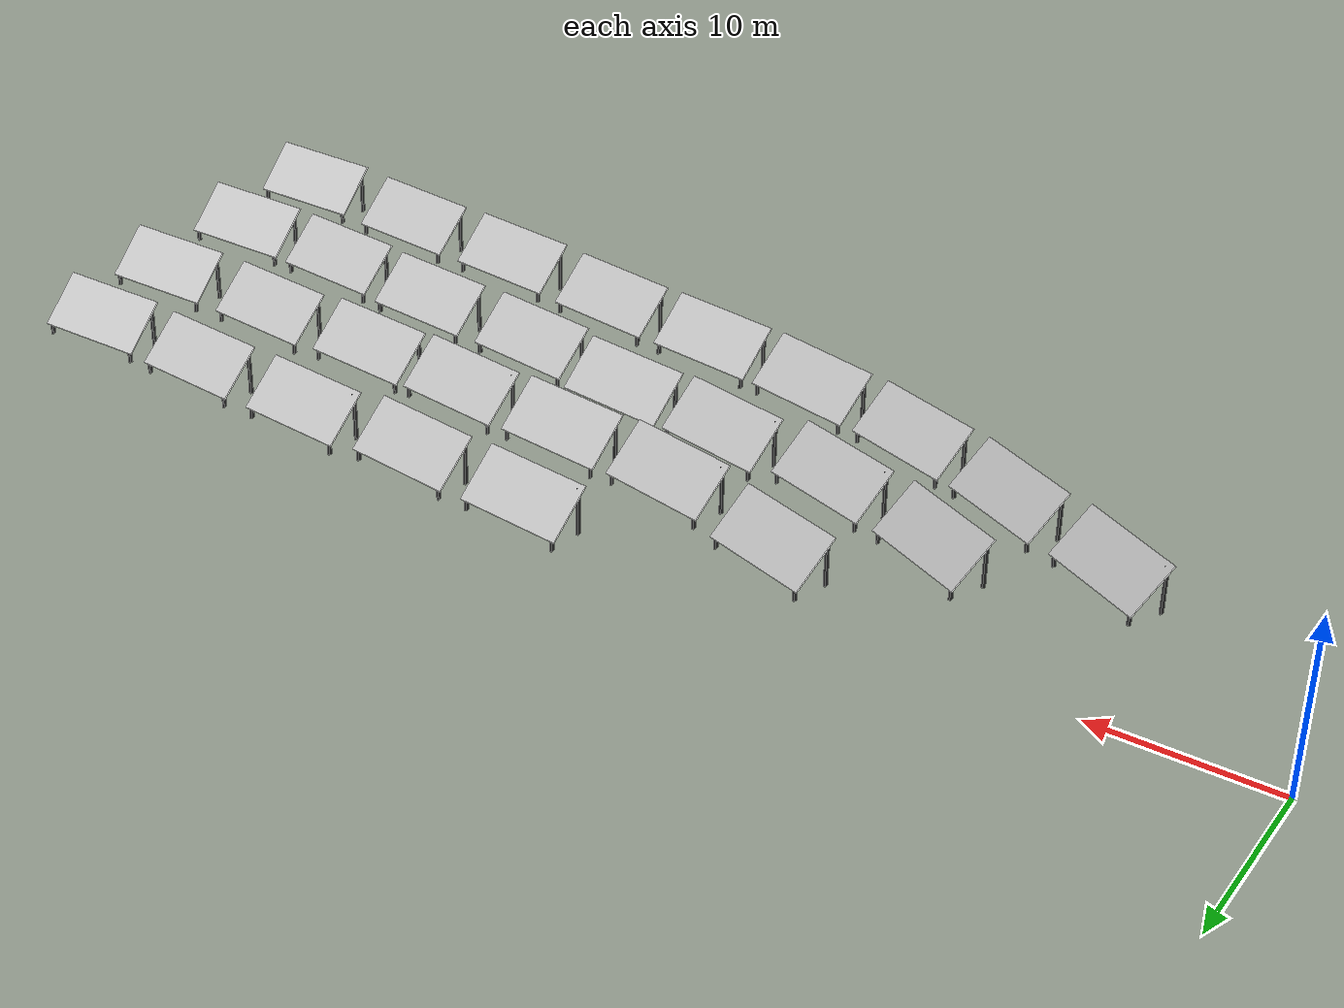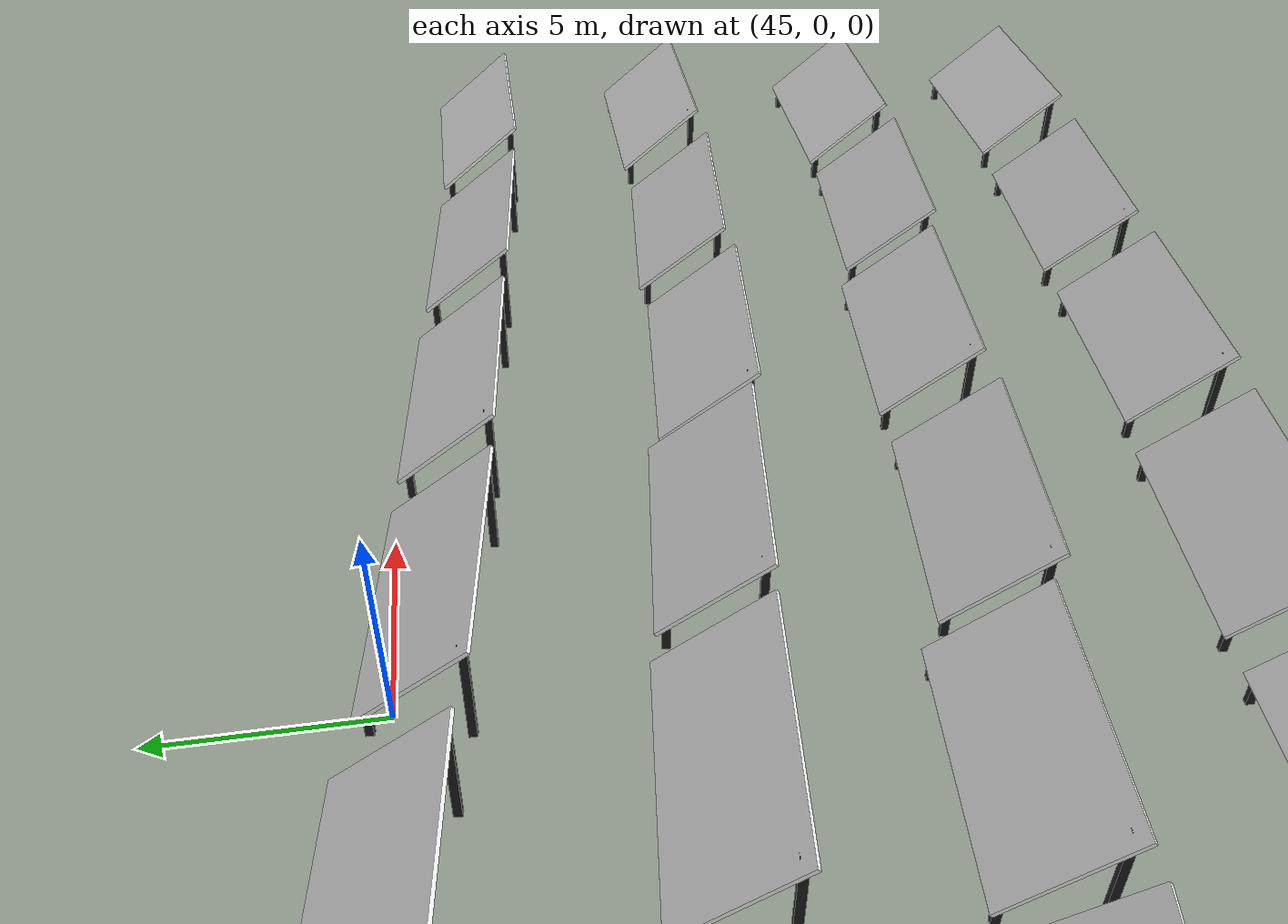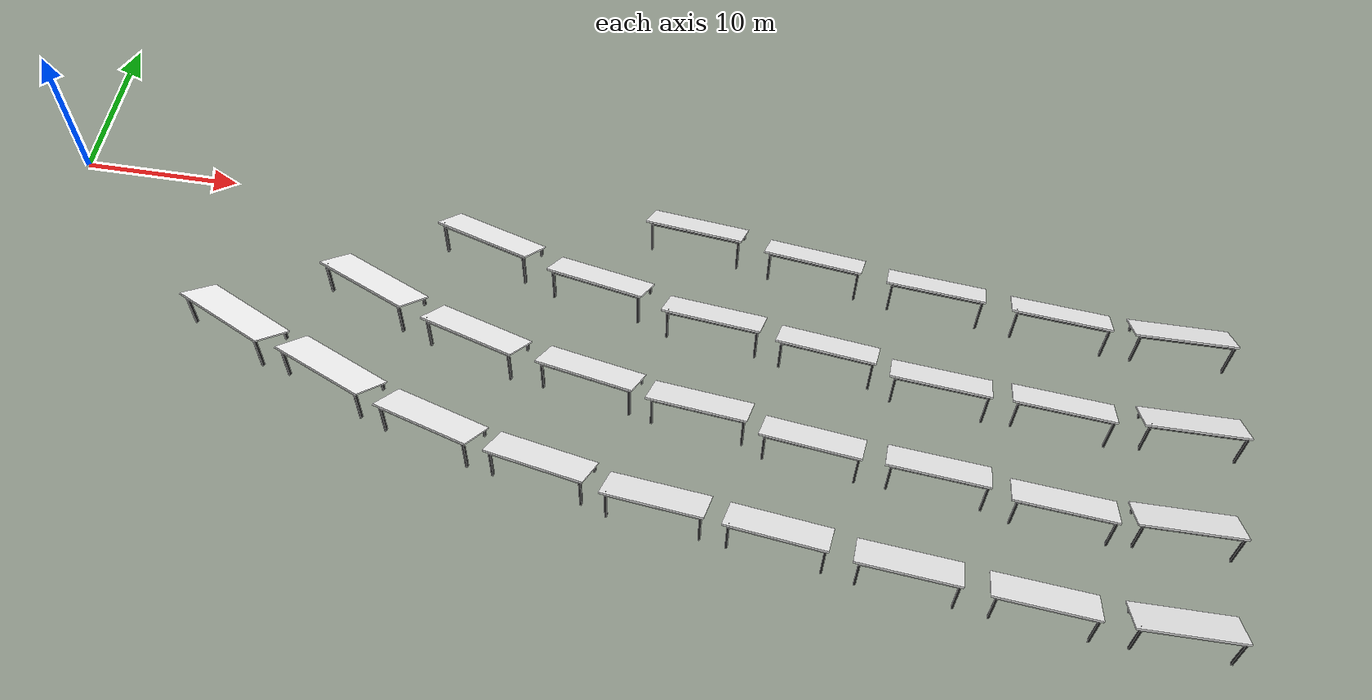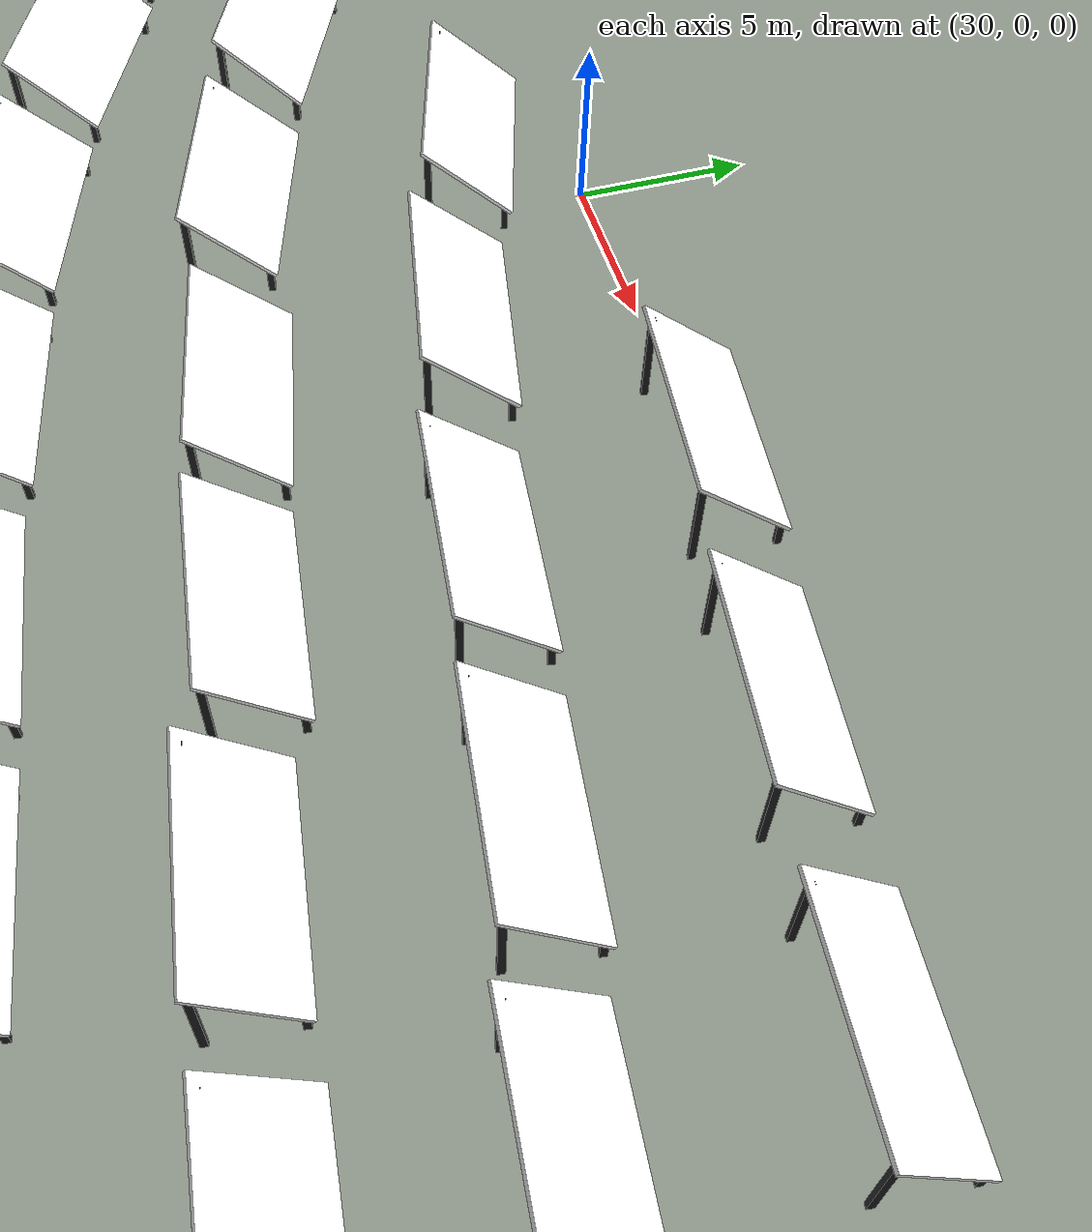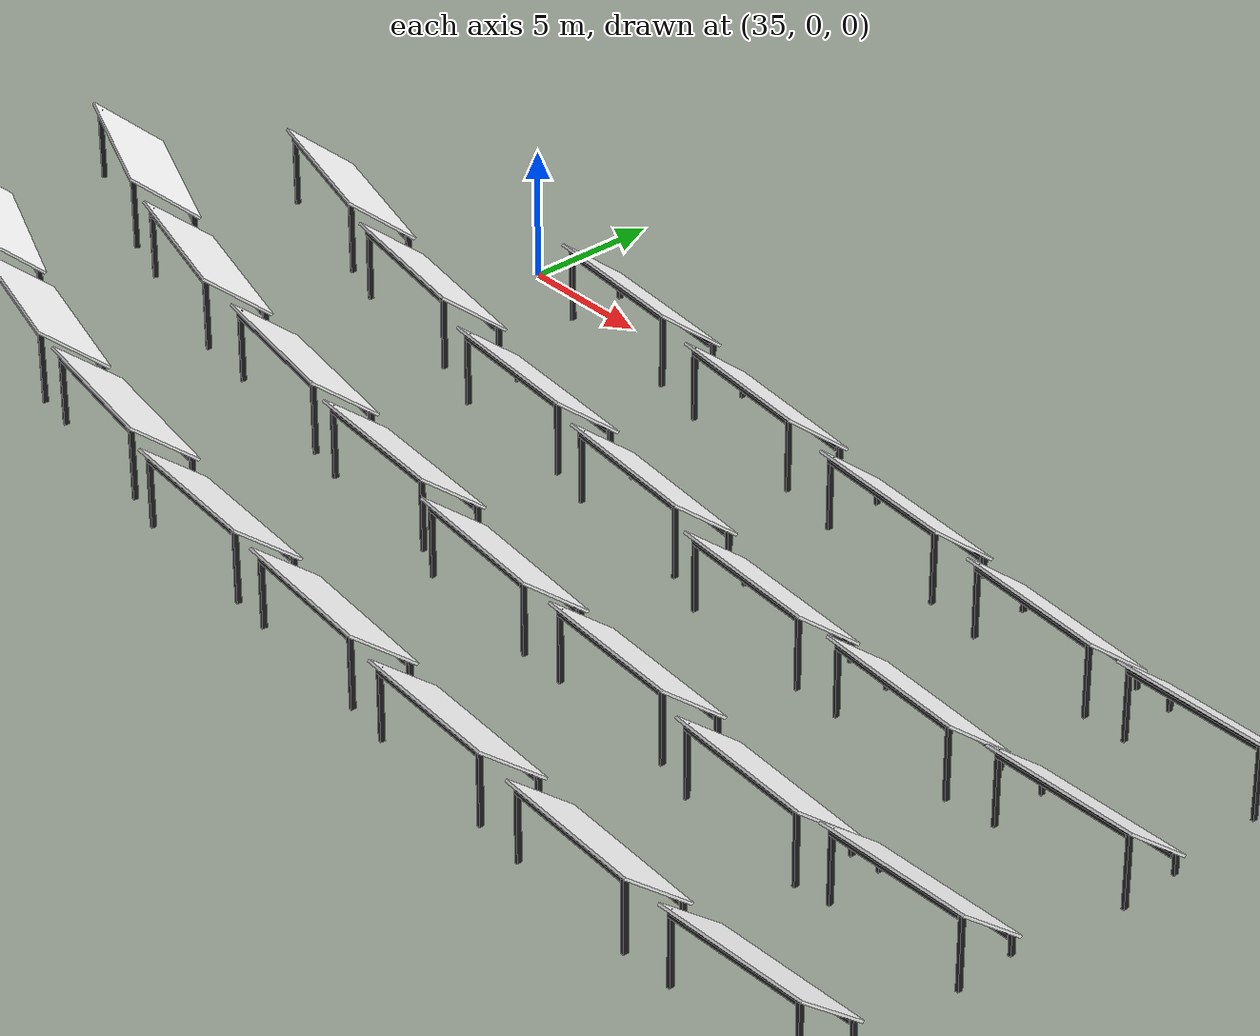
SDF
<sdf version="1.6">
 <world name="default">
  <light name="sun" type="directional">
   <cast_shadows>0</cast_shadows>
   <pose>0 0 10 0 -0 0</pose>
   <diffuse>0.8 0.8 0.8 1</diffuse>
   <specular>0.2 0.2 0.2 1</specular>
   <attenuation>
    <range>1000</range>
    <constant>0.9</constant>
    <linear>0.01</linear>
    <quadratic>0.001</quadratic>
   </attenuation>
   <direction>-0.5 0.1 -0.9</direction>
  </light>
  <gravity>0 0 -9.8</gravity>
  <magnetic_field>6e-06 2.3e-05 -4.2e-05</magnetic_field>
  <atmosphere type="adiabatic"/>
  <physics name="default_physics" default="0" type="ode">
   <max_step_size>0.001</max_step_size>
   <real_time_factor>1</real_time_factor>
   <real_time_update_rate>1000</real_time_update_rate>
  </physics>
  <scene><ambient>0.4 0.4 0.4 1</ambient><background>0.7 0.7 0.7 1</background><shadows>0</shadows></scene>
  <spherical_coordinates>
   <surface_model>EARTH_WGS84</surface_model>
   <latitude_deg>0</latitude_deg>
   <longitude_deg>0</longitude_deg>
   <elevation>0</elevation>
   <heading_deg>0</heading_deg>
  </spherical_coordinates>
  <model name="new_solar">
   <static>1</static>
   <link name="link_1">
    <inertial>
     <mass>1.98638</mass>
     <inertia><ixx>1.74251</ixx><ixy>0</ixy><ixz>0</ixz><iyy>6.11467</iyy><iyz>0</iyz><izz>7.85383</izz></inertia>
    </inertial>
    <pose>-0.040001 0.043327 0.560753 -0.688467 0 0</pose>
    <visual name="visual">
     <geometry><box><size>6.07696 3.24293 0.100789</size></box></geometry>
     <material>
      <lighting>1</lighting>
      <script>
       <uri>model://new_solar/materials/scripts</uri>
       <uri>model://new_solar/materials/textures</uri>
       <name>solar</name>
      </script>
      <shader type="pixel"><normal_map>__default__</normal_map></shader>
      <ambient>1 1 1 1</ambient>
      <diffuse>1 1 1 1</diffuse>
      <specular>0 0 0 1</specular>
      <emissive>0 0 0 1</emissive>
     </material>
    </visual>
    <collision name="collision">
     <geometry><box><size>6.07696 3.24293 0.100789</size></box></geometry>
     <surface>
      <friction>
       <ode><mu>1</mu><mu2>1</mu2><fdir1>0 0 0</fdir1><slip1>0</slip1><slip2>0</slip2></ode>
       <torsional>
        <coefficient>1</coefficient>
        <patch_radius>0</patch_radius>
        <surface_radius>0</surface_radius>
        <use_patch_radius>1</use_patch_radius>
        <ode><slip>0</slip></ode>
       </torsional>
      </friction>
      <bounce><restitution_coefficient>0</restitution_coefficient><threshold>1e+06</threshold></bounce>
      <contact>
       <collide_without_contact>0</collide_without_contact>
       <collide_without_contact_bitmask>1</collide_without_contact_bitmask>
       <collide_bitmask>1</collide_bitmask>
       <ode>
        <soft_cfm>0</soft_cfm>
        <soft_erp>0.2</soft_erp>
        <kp>1e+13</kp>
        <kd>1</kd>
        <max_vel>0.01</max_vel>
        <min_depth>0</min_depth>
       </ode>
       <bullet>
        <split_impulse>1</split_impulse>
        <split_impulse_penetration_threshold>-0.01</split_impulse_penetration_threshold>
        <soft_cfm>0</soft_cfm>
        <soft_erp>0.2</soft_erp>
        <kp>1e+13</kp>
        <kd>1</kd>
       </bullet>
      </contact>
     </surface>
    </collision>
   </link>
   <link name="link_2">
    <inertial>
     <mass>0.0207671</mass>
     <inertia>
      <ixx>0.0012143</ixx>
      <ixy>0</ixy>
      <ixz>0</ixz>
      <iyy>0.00118465</iyy>
      <iyz>0</iyz>
      <izz>9.301e-05</izz>
     </inertia>
    </inertial>
    <pose>2.8032 1.09463 -0.744944 0 -0 0</pose>
    <visual name="visual">
     <geometry><box><size>0.135288 0.188253 0.81623</size></box></geometry>
     <material>
      <lighting>1</lighting>
      <script><uri>file://media/materials/scripts/gazebo.material</uri><name>Gazebo/Black</name></script>
      <shader type="pixel"><normal_map>__default__</normal_map></shader>
      <ambient>0 0 0 1</ambient>
      <diffuse>0 0 0 1</diffuse>
      <specular>0.1 0.1 0.1 1</specular>
      <emissive>0 0 0 1</emissive>
     </material>
    </visual>
    <collision name="collision">
     <geometry><box><size>0.135288 0.188253 0.81623</size></box></geometry>
     <surface>
      <friction>
       <ode><mu>1</mu><mu2>1</mu2><fdir1>0 0 0</fdir1><slip1>0</slip1><slip2>0</slip2></ode>
       <torsional>
        <coefficient>1</coefficient>
        <patch_radius>0</patch_radius>
        <surface_radius>0</surface_radius>
        <use_patch_radius>1</use_patch_radius>
        <ode><slip>0</slip></ode>
       </torsional>
      </friction>
      <bounce><restitution_coefficient>0</restitution_coefficient><threshold>1e+06</threshold></bounce>
      <contact>
       <collide_without_contact>0</collide_without_contact>
       <collide_without_contact_bitmask>1</collide_without_contact_bitmask>
       <collide_bitmask>1</collide_bitmask>
       <ode>
        <soft_cfm>0</soft_cfm>
        <soft_erp>0.2</soft_erp>
        <kp>1e+13</kp>
        <kd>1</kd>
        <max_vel>0.01</max_vel>
        <min_depth>0</min_depth>
       </ode>
       <bullet>
        <split_impulse>1</split_impulse>
        <split_impulse_penetration_threshold>-0.01</split_impulse_penetration_threshold>
        <soft_cfm>0</soft_cfm>
        <soft_erp>0.2</soft_erp>
        <kp>1e+13</kp>
        <kd>1</kd>
       </bullet>
      </contact>
     </surface>
    </collision>
   </link>
   <link name="link_2_clone">
    <inertial>
     <mass>0.0207671</mass>
     <inertia>
      <ixx>0.0012143</ixx>
      <ixy>0</ixy>
      <ixz>0</ixz>
      <iyy>0.00118465</iyy>
      <iyz>0</iyz>
      <izz>9.301e-05</izz>
     </inertia>
    </inertial>
    <pose>-2.7581 1.05673 -0.787934 0 -0 0</pose>
    <visual name="visual">
     <geometry><box><size>0.135288 0.188253 0.81623</size></box></geometry>
     <material>
      <lighting>1</lighting>
      <script><uri>file://media/materials/scripts/gazebo.material</uri><name>Gazebo/Black</name></script>
      <shader type="pixel"><normal_map>__default__</normal_map></shader>
      <ambient>0 0 0 1</ambient>
      <diffuse>0 0 0 1</diffuse>
      <specular>0.1 0.1 0.1 1</specular>
      <emissive>0 0 0 1</emissive>
     </material>
    </visual>
    <collision name="collision">
     <geometry><box><size>0.135288 0.188253 0.81623</size></box></geometry>
     <surface>
      <friction>
       <ode><mu>1</mu><mu2>1</mu2><fdir1>0 0 0</fdir1><slip1>0</slip1><slip2>0</slip2></ode>
       <torsional>
        <coefficient>1</coefficient>
        <patch_radius>0</patch_radius>
        <surface_radius>0</surface_radius>
        <use_patch_radius>1</use_patch_radius>
        <ode><slip>0</slip></ode>
       </torsional>
      </friction>
      <bounce><restitution_coefficient>0</restitution_coefficient><threshold>1e+06</threshold></bounce>
      <contact>
       <collide_without_contact>0</collide_without_contact>
       <collide_without_contact_bitmask>1</collide_without_contact_bitmask>
       <collide_bitmask>1</collide_bitmask>
       <ode>
        <soft_cfm>0</soft_cfm>
        <soft_erp>0.2</soft_erp>
        <kp>1e+13</kp>
        <kd>1</kd>
        <max_vel>0.01</max_vel>
        <min_depth>0</min_depth>
       </ode>
       <bullet>
        <split_impulse>1</split_impulse>
        <split_impulse_penetration_threshold>-0.01</split_impulse_penetration_threshold>
        <soft_cfm>0</soft_cfm>
        <soft_erp>0.2</soft_erp>
        <kp>1e+13</kp>
        <kd>1</kd>
       </bullet>
      </contact>
     </surface>
    </collision>
   </link>
   <link name="link_2_clone_clone_clone">
    <inertial>
     <mass>0.0712376</mass>
     <inertia>
      <ixx>0.0467501</ixx>
      <ixy>0</ixy>
      <ixz>0</ixz>
      <iyy>0.0466484</iyy>
      <iyz>0</iyz>
      <izz>0.00031904</izz>
     </inertia>
    </inertial>
    <pose>2.7925 -1.06517 0.041693 0 -0 0</pose>
    <visual name="visual">
     <geometry><box><size>0.135288 0.188253 2.79994</size></box></geometry>
     <material>
      <lighting>1</lighting>
      <script><uri>file://media/materials/scripts/gazebo.material</uri><name>Gazebo/Black</name></script>
      <shader type="pixel"><normal_map>__default__</normal_map></shader>
      <ambient>0 0 0 1</ambient>
      <diffuse>0 0 0 1</diffuse>
      <specular>0.1 0.1 0.1 1</specular>
      <emissive>0 0 0 1</emissive>
     </material>
    </visual>
    <collision name="collision">
     <geometry><box><size>0.135288 0.188253 2.79994</size></box></geometry>
     <surface>
      <friction>
       <ode><mu>1</mu><mu2>1</mu2><fdir1>0 0 0</fdir1><slip1>0</slip1><slip2>0</slip2></ode>
       <torsional>
        <coefficient>1</coefficient>
        <patch_radius>0</patch_radius>
        <surface_radius>0</surface_radius>
        <use_patch_radius>1</use_patch_radius>
        <ode><slip>0</slip></ode>
       </torsional>
      </friction>
      <bounce><restitution_coefficient>0</restitution_coefficient><threshold>1e+06</threshold></bounce>
      <contact>
       <collide_without_contact>0</collide_without_contact>
       <collide_without_contact_bitmask>1</collide_without_contact_bitmask>
       <collide_bitmask>1</collide_bitmask>
       <ode>
        <soft_cfm>0</soft_cfm>
        <soft_erp>0.2</soft_erp>
        <kp>1e+13</kp>
        <kd>1</kd>
        <max_vel>0.01</max_vel>
        <min_depth>0</min_depth>
       </ode>
       <bullet>
        <split_impulse>1</split_impulse>
        <split_impulse_penetration_threshold>-0.01</split_impulse_penetration_threshold>
        <soft_cfm>0</soft_cfm>
        <soft_erp>0.2</soft_erp>
        <kp>1e+13</kp>
        <kd>1</kd>
       </bullet>
      </contact>
     </surface>
    </collision>
   </link>
   <link name="link_2_clone_clone_clone_clone">
    <inertial>
     <mass>0.0712376</mass>
     <inertia>
      <ixx>0.0467501</ixx>
      <ixy>0</ixy>
      <ixz>0</ixz>
      <iyy>0.0466484</iyy>
      <iyz>0</iyz>
      <izz>0.00031904</izz>
     </inertia>
    </inertial>
    <pose>-2.71279 -1.03577 0.041693 0 -0 0</pose>
    <visual name="visual">
     <geometry><box><size>0.135288 0.188253 2.79994</size></box></geometry>
     <material>
      <lighting>1</lighting>
      <script><uri>file://media/materials/scripts/gazebo.material</uri><name>Gazebo/Black</name></script>
      <shader type="pixel"><normal_map>__default__</normal_map></shader>
      <ambient>0 0 0 1</ambient>
      <diffuse>0 0 0 1</diffuse>
      <specular>0.1 0.1 0.1 1</specular>
      <emissive>0 0 0 1</emissive>
     </material>
    </visual>
    <collision name="collision">
     <geometry><box><size>0.135288 0.188253 2.79994</size></box></geometry>
     <surface>
      <friction>
       <ode><mu>1</mu><mu2>1</mu2><fdir1>0 0 0</fdir1><slip1>0</slip1><slip2>0</slip2></ode>
       <torsional>
        <coefficient>1</coefficient>
        <patch_radius>0</patch_radius>
        <surface_radius>0</surface_radius>
        <use_patch_radius>1</use_patch_radius>
        <ode><slip>0</slip></ode>
       </torsional>
      </friction>
      <bounce><restitution_coefficient>0</restitution_coefficient><threshold>1e+06</threshold></bounce>
      <contact>
       <collide_without_contact>0</collide_without_contact>
       <collide_without_contact_bitmask>1</collide_without_contact_bitmask>
       <collide_bitmask>1</collide_bitmask>
       <ode>
        <soft_cfm>0</soft_cfm>
        <soft_erp>0.2</soft_erp>
        <kp>1e+13</kp>
        <kd>1</kd>
        <max_vel>0.01</max_vel>
        <min_depth>0</min_depth>
       </ode>
       <bullet>
        <split_impulse>1</split_impulse>
        <split_impulse_penetration_threshold>-0.01</split_impulse_penetration_threshold>
        <soft_cfm>0</soft_cfm>
        <soft_erp>0.2</soft_erp>
        <kp>1e+13</kp>
        <kd>1</kd>
       </bullet>
      </contact>
     </surface>
    </collision>
   </link>
   <link name="link_3">
    <inertial>
     <mass>0.133626</mass>
     <inertia>
      <ixx>0.00054826</ixx>
      <ixy>0</ixy>
      <ixz>0</ixz>
      <iyy>0.330433</iyy>
      <iyz>0</iyz>
      <izz>0.330457</izz>
     </inertia>
    </inertial>
    <pose>0 1.04453 -0.461177 0 -0 0</pose>
    <visual name="visual">
     <geometry><box><size>5.44521 0.160272 0.153456</size></box></geometry>
     <material>
      <lighting>1</lighting>
      <script><uri>file://media/materials/scripts/gazebo.material</uri><name>Gazebo/Black</name></script>
      <shader type="pixel"><normal_map>__default__</normal_map></shader>
      <ambient>0 0 0 1</ambient>
      <diffuse>0 0 0 1</diffuse>
      <specular>0.1 0.1 0.1 1</specular>
      <emissive>0 0 0 1</emissive>
     </material>
    </visual>
    <collision name="collision">
     <geometry><box><size>5.44521 0.160272 0.153456</size></box></geometry>
     <surface>
      <friction>
       <ode><mu>1</mu><mu2>1</mu2><fdir1>0 0 0</fdir1><slip1>0</slip1><slip2>0</slip2></ode>
       <torsional>
        <coefficient>1</coefficient>
        <patch_radius>0</patch_radius>
        <surface_radius>0</surface_radius>
        <use_patch_radius>1</use_patch_radius>
        <ode><slip>0</slip></ode>
       </torsional>
      </friction>
      <bounce><restitution_coefficient>0</restitution_coefficient><threshold>1e+06</threshold></bounce>
      <contact>
       <collide_without_contact>0</collide_without_contact>
       <collide_without_contact_bitmask>1</collide_without_contact_bitmask>
       <collide_bitmask>1</collide_bitmask>
       <ode>
        <soft_cfm>0</soft_cfm>
        <soft_erp>0.2</soft_erp>
        <kp>1e+13</kp>
        <kd>1</kd>
        <max_vel>0.01</max_vel>
        <min_depth>0</min_depth>
       </ode>
       <bullet>
        <split_impulse>1</split_impulse>
        <split_impulse_penetration_threshold>-0.01</split_impulse_penetration_threshold>
        <soft_cfm>0</soft_cfm>
        <soft_erp>0.2</soft_erp>
        <kp>1e+13</kp>
        <kd>1</kd>
       </bullet>
      </contact>
     </surface>
    </collision>
   </link>
   <link name="link_3_clone">
    <inertial>
     <mass>0.133626</mass>
     <inertia>
      <ixx>0.00054826</ixx>
      <ixy>0</ixy>
      <ixz>0</ixz>
      <iyy>0.330433</iyy>
      <iyz>0</iyz>
      <izz>0.330457</izz>
     </inertia>
    </inertial>
    <pose>-0.0149 -1.07367 1.34991 0 -0 0</pose>
    <visual name="visual">
     <geometry><box><size>5.44521 0.160272 0.153456</size></box></geometry>
     <material>
      <lighting>1</lighting>
      <script><uri>file://media/materials/scripts/gazebo.material</uri><name>Gazebo/Black</name></script>
      <shader type="pixel"><normal_map>__default__</normal_map></shader>
      <ambient>0 0 0 1</ambient>
      <diffuse>0 0 0 1</diffuse>
      <specular>0.1 0.1 0.1 1</specular>
      <emissive>0 0 0 1</emissive>
     </material>
    </visual>
    <collision name="collision">
     <geometry><box><size>5.44521 0.160272 0.153456</size></box></geometry>
     <surface>
      <friction>
       <ode><mu>1</mu><mu2>1</mu2><fdir1>0 0 0</fdir1><slip1>0</slip1><slip2>0</slip2></ode>
       <torsional>
        <coefficient>1</coefficient>
        <patch_radius>0</patch_radius>
        <surface_radius>0</surface_radius>
        <use_patch_radius>1</use_patch_radius>
        <ode><slip>0</slip></ode>
       </torsional>
      </friction>
      <bounce><restitution_coefficient>0</restitution_coefficient><threshold>1e+06</threshold></bounce>
      <contact>
       <collide_without_contact>0</collide_without_contact>
       <collide_without_contact_bitmask>1</collide_without_contact_bitmask>
       <collide_bitmask>1</collide_bitmask>
       <ode>
        <soft_cfm>0</soft_cfm>
        <soft_erp>0.2</soft_erp>
        <kp>1e+13</kp>
        <kd>1</kd>
        <max_vel>0.01</max_vel>
        <min_depth>0</min_depth>
       </ode>
       <bullet>
        <split_impulse>1</split_impulse>
        <split_impulse_penetration_threshold>-0.01</split_impulse_penetration_threshold>
        <soft_cfm>0</soft_cfm>
        <soft_erp>0.2</soft_erp>
        <kp>1e+13</kp>
        <kd>1</kd>
       </bullet>
      </contact>
     </surface>
    </collision>
   </link>
   <pose>69.9777 -21.6584 0.102643 0 -0 0</pose>
  </model>
  <model name="new_solar_clone">
   <static>1</static>
   <link name="link_1">
    <inertial>
     <mass>1.98638</mass>
     <inertia><ixx>1.74251</ixx><ixy>0</ixy><ixz>0</ixz><iyy>6.11467</iyy><iyz>0</iyz><izz>7.85383</izz></inertia>
    </inertial>
    <pose>-0.040001 0.043327 0.560753 -0.688467 0 0</pose>
    <visual name="visual">
     <geometry><box><size>6.07696 3.24293 0.100789</size></box></geometry>
     <material>
      <lighting>1</lighting>
      <script>
       <uri>model://new_solar/materials/scripts</uri>
       <uri>model://new_solar/materials/textures</uri>
       <name>solar</name>
      </script>
      <shader type="pixel"><normal_map>__default__</normal_map></shader>
      <ambient>1 1 1 1</ambient>
      <diffuse>1 1 1 1</diffuse>
      <specular>0 0 0 1</specular>
      <emissive>0 0 0 1</emissive>
     </material>
    </visual>
    <collision name="collision">
     <geometry><box><size>6.07696 3.24293 0.100789</size></box></geometry>
     <surface>
      <friction>
       <ode><mu>1</mu><mu2>1</mu2><fdir1>0 0 0</fdir1><slip1>0</slip1><slip2>0</slip2></ode>
       <torsional>
        <coefficient>1</coefficient>
        <patch_radius>0</patch_radius>
        <surface_radius>0</surface_radius>
        <use_patch_radius>1</use_patch_radius>
        <ode><slip>0</slip></ode>
       </torsional>
      </friction>
      <bounce><restitution_coefficient>0</restitution_coefficient><threshold>1e+06</threshold></bounce>
      <contact>
       <collide_without_contact>0</collide_without_contact>
       <collide_without_contact_bitmask>1</collide_without_contact_bitmask>
       <collide_bitmask>1</collide_bitmask>
       <ode>
        <soft_cfm>0</soft_cfm>
        <soft_erp>0.2</soft_erp>
        <kp>1e+13</kp>
        <kd>1</kd>
        <max_vel>0.01</max_vel>
        <min_depth>0</min_depth>
       </ode>
       <bullet>
        <split_impulse>1</split_impulse>
        <split_impulse_penetration_threshold>-0.01</split_impulse_penetration_threshold>
        <soft_cfm>0</soft_cfm>
        <soft_erp>0.2</soft_erp>
        <kp>1e+13</kp>
        <kd>1</kd>
       </bullet>
      </contact>
     </surface>
    </collision>
   </link>
   <link name="link_2">
    <inertial>
     <mass>0.0207671</mass>
     <inertia>
      <ixx>0.0012143</ixx>
      <ixy>0</ixy>
      <ixz>0</ixz>
      <iyy>0.00118465</iyy>
      <iyz>0</iyz>
      <izz>9.301e-05</izz>
     </inertia>
    </inertial>
    <pose>2.8032 1.09463 -0.744944 0 -0 0</pose>
    <visual name="visual">
     <geometry><box><size>0.135288 0.188253 0.81623</size></box></geometry>
     <material>
      <lighting>1</lighting>
      <script><uri>file://media/materials/scripts/gazebo.material</uri><name>Gazebo/Black</name></script>
      <shader type="pixel"><normal_map>__default__</normal_map></shader>
      <ambient>0 0 0 1</ambient>
      <diffuse>0 0 0 1</diffuse>
      <specular>0.1 0.1 0.1 1</specular>
      <emissive>0 0 0 1</emissive>
     </material>
    </visual>
    <collision name="collision">
     <geometry><box><size>0.135288 0.188253 0.81623</size></box></geometry>
     <surface>
      <friction>
       <ode><mu>1</mu><mu2>1</mu2><fdir1>0 0 0</fdir1><slip1>0</slip1><slip2>0</slip2></ode>
       <torsional>
        <coefficient>1</coefficient>
        <patch_radius>0</patch_radius>
        <surface_radius>0</surface_radius>
        <use_patch_radius>1</use_patch_radius>
        <ode><slip>0</slip></ode>
       </torsional>
      </friction>
      <bounce><restitution_coefficient>0</restitution_coefficient><threshold>1e+06</threshold></bounce>
      <contact>
       <collide_without_contact>0</collide_without_contact>
       <collide_without_contact_bitmask>1</collide_without_contact_bitmask>
       <collide_bitmask>1</collide_bitmask>
       <ode>
        <soft_cfm>0</soft_cfm>
        <soft_erp>0.2</soft_erp>
        <kp>1e+13</kp>
        <kd>1</kd>
        <max_vel>0.01</max_vel>
        <min_depth>0</min_depth>
       </ode>
       <bullet>
        <split_impulse>1</split_impulse>
        <split_impulse_penetration_threshold>-0.01</split_impulse_penetration_threshold>
        <soft_cfm>0</soft_cfm>
        <soft_erp>0.2</soft_erp>
        <kp>1e+13</kp>
        <kd>1</kd>
       </bullet>
      </contact>
     </surface>
    </collision>
   </link>
   <link name="link_2_clone">
    <inertial>
     <mass>0.0207671</mass>
     <inertia>
      <ixx>0.0012143</ixx>
      <ixy>0</ixy>
      <ixz>0</ixz>
      <iyy>0.00118465</iyy>
      <iyz>0</iyz>
      <izz>9.301e-05</izz>
     </inertia>
    </inertial>
    <pose>-2.7581 1.05673 -0.787934 0 -0 0</pose>
    <visual name="visual">
     <geometry><box><size>0.135288 0.188253 0.81623</size></box></geometry>
     <material>
      <lighting>1</lighting>
      <script><uri>file://media/materials/scripts/gazebo.material</uri><name>Gazebo/Black</name></script>
      <shader type="pixel"><normal_map>__default__</normal_map></shader>
      <ambient>0 0 0 1</ambient>
      <diffuse>0 0 0 1</diffuse>
      <specular>0.1 0.1 0.1 1</specular>
      <emissive>0 0 0 1</emissive>
     </material>
    </visual>
    <collision name="collision">
     <geometry><box><size>0.135288 0.188253 0.81623</size></box></geometry>
     <surface>
      <friction>
       <ode><mu>1</mu><mu2>1</mu2><fdir1>0 0 0</fdir1><slip1>0</slip1><slip2>0</slip2></ode>
       <torsional>
        <coefficient>1</coefficient>
        <patch_radius>0</patch_radius>
        <surface_radius>0</surface_radius>
        <use_patch_radius>1</use_patch_radius>
        <ode><slip>0</slip></ode>
       </torsional>
      </friction>
      <bounce><restitution_coefficient>0</restitution_coefficient><threshold>1e+06</threshold></bounce>
      <contact>
       <collide_without_contact>0</collide_without_contact>
       <collide_without_contact_bitmask>1</collide_without_contact_bitmask>
       <collide_bitmask>1</collide_bitmask>
       <ode>
        <soft_cfm>0</soft_cfm>
        <soft_erp>0.2</soft_erp>
        <kp>1e+13</kp>
        <kd>1</kd>
        <max_vel>0.01</max_vel>
        <min_depth>0</min_depth>
       </ode>
       <bullet>
        <split_impulse>1</split_impulse>
        <split_impulse_penetration_threshold>-0.01</split_impulse_penetration_threshold>
        <soft_cfm>0</soft_cfm>
        <soft_erp>0.2</soft_erp>
        <kp>1e+13</kp>
        <kd>1</kd>
       </bullet>
      </contact>
     </surface>
    </collision>
   </link>
   <link name="link_2_clone_clone_clone">
    <inertial>
     <mass>0.0712376</mass>
     <inertia>
      <ixx>0.0467501</ixx>
      <ixy>0</ixy>
      <ixz>0</ixz>
      <iyy>0.0466484</iyy>
      <iyz>0</iyz>
      <izz>0.00031904</izz>
     </inertia>
    </inertial>
    <pose>2.7925 -1.06517 0.041693 0 -0 0</pose>
    <visual name="visual">
     <geometry><box><size>0.135288 0.188253 2.79994</size></box></geometry>
     <material>
      <lighting>1</lighting>
      <script><uri>file://media/materials/scripts/gazebo.material</uri><name>Gazebo/Black</name></script>
      <shader type="pixel"><normal_map>__default__</normal_map></shader>
      <ambient>0 0 0 1</ambient>
      <diffuse>0 0 0 1</diffuse>
      <specular>0.1 0.1 0.1 1</specular>
      <emissive>0 0 0 1</emissive>
     </material>
    </visual>
    <collision name="collision">
     <geometry><box><size>0.135288 0.188253 2.79994</size></box></geometry>
     <surface>
      <friction>
       <ode><mu>1</mu><mu2>1</mu2><fdir1>0 0 0</fdir1><slip1>0</slip1><slip2>0</slip2></ode>
       <torsional>
        <coefficient>1</coefficient>
        <patch_radius>0</patch_radius>
        <surface_radius>0</surface_radius>
        <use_patch_radius>1</use_patch_radius>
        <ode><slip>0</slip></ode>
       </torsional>
      </friction>
      <bounce><restitution_coefficient>0</restitution_coefficient><threshold>1e+06</threshold></bounce>
      <contact>
       <collide_without_contact>0</collide_without_contact>
       <collide_without_contact_bitmask>1</collide_without_contact_bitmask>
       <collide_bitmask>1</collide_bitmask>
       <ode>
        <soft_cfm>0</soft_cfm>
        <soft_erp>0.2</soft_erp>
        <kp>1e+13</kp>
        <kd>1</kd>
        <max_vel>0.01</max_vel>
        <min_depth>0</min_depth>
       </ode>
       <bullet>
        <split_impulse>1</split_impulse>
        <split_impulse_penetration_threshold>-0.01</split_impulse_penetration_threshold>
        <soft_cfm>0</soft_cfm>
        <soft_erp>0.2</soft_erp>
        <kp>1e+13</kp>
        <kd>1</kd>
       </bullet>
      </contact>
     </surface>
    </collision>
   </link>
   <link name="link_2_clone_clone_clone_clone">
    <inertial>
     <mass>0.0712376</mass>
     <inertia>
      <ixx>0.0467501</ixx>
      <ixy>0</ixy>
      <ixz>0</ixz>
      <iyy>0.0466484</iyy>
      <iyz>0</iyz>
      <izz>0.00031904</izz>
     </inertia>
    </inertial>
    <pose>-2.71279 -1.03577 0.041693 0 -0 0</pose>
    <visual name="visual">
     <geometry><box><size>0.135288 0.188253 2.79994</size></box></geometry>
     <material>
      <lighting>1</lighting>
      <script><uri>file://media/materials/scripts/gazebo.material</uri><name>Gazebo/Black</name></script>
      <shader type="pixel"><normal_map>__default__</normal_map></shader>
      <ambient>0 0 0 1</ambient>
      <diffuse>0 0 0 1</diffuse>
      <specular>0.1 0.1 0.1 1</specular>
      <emissive>0 0 0 1</emissive>
     </material>
    </visual>
    <collision name="collision">
     <geometry><box><size>0.135288 0.188253 2.79994</size></box></geometry>
     <surface>
      <friction>
       <ode><mu>1</mu><mu2>1</mu2><fdir1>0 0 0</fdir1><slip1>0</slip1><slip2>0</slip2></ode>
       <torsional>
        <coefficient>1</coefficient>
        <patch_radius>0</patch_radius>
        <surface_radius>0</surface_radius>
        <use_patch_radius>1</use_patch_radius>
        <ode><slip>0</slip></ode>
       </torsional>
      </friction>
      <bounce><restitution_coefficient>0</restitution_coefficient><threshold>1e+06</threshold></bounce>
      <contact>
       <collide_without_contact>0</collide_without_contact>
       <collide_without_contact_bitmask>1</collide_without_contact_bitmask>
       <collide_bitmask>1</collide_bitmask>
       <ode>
        <soft_cfm>0</soft_cfm>
        <soft_erp>0.2</soft_erp>
        <kp>1e+13</kp>
        <kd>1</kd>
        <max_vel>0.01</max_vel>
        <min_depth>0</min_depth>
       </ode>
       <bullet>
        <split_impulse>1</split_impulse>
        <split_impulse_penetration_threshold>-0.01</split_impulse_penetration_threshold>
        <soft_cfm>0</soft_cfm>
        <soft_erp>0.2</soft_erp>
        <kp>1e+13</kp>
        <kd>1</kd>
       </bullet>
      </contact>
     </surface>
    </collision>
   </link>
   <link name="link_3">
    <inertial>
     <mass>0.133626</mass>
     <inertia>
      <ixx>0.00054826</ixx>
      <ixy>0</ixy>
      <ixz>0</ixz>
      <iyy>0.330433</iyy>
      <iyz>0</iyz>
      <izz>0.330457</izz>
     </inertia>
    </inertial>
    <pose>0 1.04453 -0.461177 0 -0 0</pose>
    <visual name="visual">
     <geometry><box><size>5.44521 0.160272 0.153456</size></box></geometry>
     <material>
      <lighting>1</lighting>
      <script><uri>file://media/materials/scripts/gazebo.material</uri><name>Gazebo/Black</name></script>
      <shader type="pixel"><normal_map>__default__</normal_map></shader>
      <ambient>0 0 0 1</ambient>
      <diffuse>0 0 0 1</diffuse>
      <specular>0.1 0.1 0.1 1</specular>
      <emissive>0 0 0 1</emissive>
     </material>
    </visual>
    <collision name="collision">
     <geometry><box><size>5.44521 0.160272 0.153456</size></box></geometry>
     <surface>
      <friction>
       <ode><mu>1</mu><mu2>1</mu2><fdir1>0 0 0</fdir1><slip1>0</slip1><slip2>0</slip2></ode>
       <torsional>
        <coefficient>1</coefficient>
        <patch_radius>0</patch_radius>
        <surface_radius>0</surface_radius>
        <use_patch_radius>1</use_patch_radius>
        <ode><slip>0</slip></ode>
       </torsional>
      </friction>
      <bounce><restitution_coefficient>0</restitution_coefficient><threshold>1e+06</threshold></bounce>
      <contact>
       <collide_without_contact>0</collide_without_contact>
       <collide_without_contact_bitmask>1</collide_without_contact_bitmask>
       <collide_bitmask>1</collide_bitmask>
       <ode>
        <soft_cfm>0</soft_cfm>
        <soft_erp>0.2</soft_erp>
        <kp>1e+13</kp>
        <kd>1</kd>
        <max_vel>0.01</max_vel>
        <min_depth>0</min_depth>
       </ode>
       <bullet>
        <split_impulse>1</split_impulse>
        <split_impulse_penetration_threshold>-0.01</split_impulse_penetration_threshold>
        <soft_cfm>0</soft_cfm>
        <soft_erp>0.2</soft_erp>
        <kp>1e+13</kp>
        <kd>1</kd>
       </bullet>
      </contact>
     </surface>
    </collision>
   </link>
   <link name="link_3_clone">
    <inertial>
     <mass>0.133626</mass>
     <inertia>
      <ixx>0.00054826</ixx>
      <ixy>0</ixy>
      <ixz>0</ixz>
      <iyy>0.330433</iyy>
      <iyz>0</iyz>
      <izz>0.330457</izz>
     </inertia>
    </inertial>
    <pose>-0.0149 -1.07367 1.34991 0 -0 0</pose>
    <visual name="visual">
     <geometry><box><size>5.44521 0.160272 0.153456</size></box></geometry>
     <material>
      <lighting>1</lighting>
      <script><uri>file://media/materials/scripts/gazebo.material</uri><name>Gazebo/Black</name></script>
      <shader type="pixel"><normal_map>__default__</normal_map></shader>
      <ambient>0 0 0 1</ambient>
      <diffuse>0 0 0 1</diffuse>
      <specular>0.1 0.1 0.1 1</specular>
      <emissive>0 0 0 1</emissive>
     </material>
    </visual>
    <collision name="collision">
     <geometry><box><size>5.44521 0.160272 0.153456</size></box></geometry>
     <surface>
      <friction>
       <ode><mu>1</mu><mu2>1</mu2><fdir1>0 0 0</fdir1><slip1>0</slip1><slip2>0</slip2></ode>
       <torsional>
        <coefficient>1</coefficient>
        <patch_radius>0</patch_radius>
        <surface_radius>0</surface_radius>
        <use_patch_radius>1</use_patch_radius>
        <ode><slip>0</slip></ode>
       </torsional>
      </friction>
      <bounce><restitution_coefficient>0</restitution_coefficient><threshold>1e+06</threshold></bounce>
      <contact>
       <collide_without_contact>0</collide_without_contact>
       <collide_without_contact_bitmask>1</collide_without_contact_bitmask>
       <collide_bitmask>1</collide_bitmask>
       <ode>
        <soft_cfm>0</soft_cfm>
        <soft_erp>0.2</soft_erp>
        <kp>1e+13</kp>
        <kd>1</kd>
        <max_vel>0.01</max_vel>
        <min_depth>0</min_depth>
       </ode>
       <bullet>
        <split_impulse>1</split_impulse>
        <split_impulse_penetration_threshold>-0.01</split_impulse_penetration_threshold>
        <soft_cfm>0</soft_cfm>
        <soft_erp>0.2</soft_erp>
        <kp>1e+13</kp>
        <kd>1</kd>
       </bullet>
      </contact>
     </surface>
    </collision>
   </link>
   <pose>62.4094 -21.2355 -0 0 0 -0.092845</pose>
  </model>
  <model name="new_solar_clone_clone">
   <static>1</static>
   <link name="link_1">
    <inertial>
     <mass>1.98638</mass>
     <inertia><ixx>1.74251</ixx><ixy>0</ixy><ixz>0</ixz><iyy>6.11467</iyy><iyz>0</iyz><izz>7.85383</izz></inertia>
    </inertial>
    <pose>-0.040001 0.043327 0.560753 -0.688467 0 0</pose>
    <visual name="visual">
     <geometry><box><size>6.07696 3.24293 0.100789</size></box></geometry>
     <material>
      <lighting>1</lighting>
      <script>
       <uri>model://new_solar/materials/scripts</uri>
       <uri>model://new_solar/materials/textures</uri>
       <name>solar</name>
      </script>
      <shader type="pixel"><normal_map>__default__</normal_map></shader>
      <ambient>1 1 1 1</ambient>
      <diffuse>1 1 1 1</diffuse>
      <specular>0 0 0 1</specular>
      <emissive>0 0 0 1</emissive>
     </material>
    </visual>
    <collision name="collision">
     <geometry><box><size>6.07696 3.24293 0.100789</size></box></geometry>
     <surface>
      <friction>
       <ode><mu>1</mu><mu2>1</mu2><fdir1>0 0 0</fdir1><slip1>0</slip1><slip2>0</slip2></ode>
       <torsional>
        <coefficient>1</coefficient>
        <patch_radius>0</patch_radius>
        <surface_radius>0</surface_radius>
        <use_patch_radius>1</use_patch_radius>
        <ode><slip>0</slip></ode>
       </torsional>
      </friction>
      <bounce><restitution_coefficient>0</restitution_coefficient><threshold>1e+06</threshold></bounce>
      <contact>
       <collide_without_contact>0</collide_without_contact>
       <collide_without_contact_bitmask>1</collide_without_contact_bitmask>
       <collide_bitmask>1</collide_bitmask>
       <ode>
        <soft_cfm>0</soft_cfm>
        <soft_erp>0.2</soft_erp>
        <kp>1e+13</kp>
        <kd>1</kd>
        <max_vel>0.01</max_vel>
        <min_depth>0</min_depth>
       </ode>
       <bullet>
        <split_impulse>1</split_impulse>
        <split_impulse_penetration_threshold>-0.01</split_impulse_penetration_threshold>
        <soft_cfm>0</soft_cfm>
        <soft_erp>0.2</soft_erp>
        <kp>1e+13</kp>
        <kd>1</kd>
       </bullet>
      </contact>
     </surface>
    </collision>
   </link>
   <link name="link_2">
    <inertial>
     <mass>0.0207671</mass>
     <inertia>
      <ixx>0.0012143</ixx>
      <ixy>0</ixy>
      <ixz>0</ixz>
      <iyy>0.00118465</iyy>
      <iyz>0</iyz>
      <izz>9.301e-05</izz>
     </inertia>
    </inertial>
    <pose>2.8032 1.09463 -0.744944 0 -0 0</pose>
    <visual name="visual">
     <geometry><box><size>0.135288 0.188253 0.81623</size></box></geometry>
     <material>
      <lighting>1</lighting>
      <script><uri>file://media/materials/scripts/gazebo.material</uri><name>Gazebo/Black</name></script>
      <shader type="pixel"><normal_map>__default__</normal_map></shader>
      <ambient>0 0 0 1</ambient>
      <diffuse>0 0 0 1</diffuse>
      <specular>0.1 0.1 0.1 1</specular>
      <emissive>0 0 0 1</emissive>
     </material>
    </visual>
    <collision name="collision">
     <geometry><box><size>0.135288 0.188253 0.81623</size></box></geometry>
     <surface>
      <friction>
       <ode><mu>1</mu><mu2>1</mu2><fdir1>0 0 0</fdir1><slip1>0</slip1><slip2>0</slip2></ode>
       <torsional>
        <coefficient>1</coefficient>
        <patch_radius>0</patch_radius>
        <surface_radius>0</surface_radius>
        <use_patch_radius>1</use_patch_radius>
        <ode><slip>0</slip></ode>
       </torsional>
      </friction>
      <bounce><restitution_coefficient>0</restitution_coefficient><threshold>1e+06</threshold></bounce>
      <contact>
       <collide_without_contact>0</collide_without_contact>
       <collide_without_contact_bitmask>1</collide_without_contact_bitmask>
       <collide_bitmask>1</collide_bitmask>
       <ode>
        <soft_cfm>0</soft_cfm>
        <soft_erp>0.2</soft_erp>
        <kp>1e+13</kp>
        <kd>1</kd>
        <max_vel>0.01</max_vel>
        <min_depth>0</min_depth>
       </ode>
       <bullet>
        <split_impulse>1</split_impulse>
        <split_impulse_penetration_threshold>-0.01</split_impulse_penetration_threshold>
        <soft_cfm>0</soft_cfm>
        <soft_erp>0.2</soft_erp>
        <kp>1e+13</kp>
        <kd>1</kd>
       </bullet>
      </contact>
     </surface>
    </collision>
   </link>
   <link name="link_2_clone">
    <inertial>
     <mass>0.0207671</mass>
     <inertia>
      <ixx>0.0012143</ixx>
      <ixy>0</ixy>
      <ixz>0</ixz>
      <iyy>0.00118465</iyy>
      <iyz>0</iyz>
      <izz>9.301e-05</izz>
     </inertia>
    </inertial>
    <pose>-2.7581 1.05673 -0.787934 0 -0 0</pose>
    <visual name="visual">
     <geometry><box><size>0.135288 0.188253 0.81623</size></box></geometry>
     <material>
      <lighting>1</lighting>
      <script><uri>file://media/materials/scripts/gazebo.material</uri><name>Gazebo/Black</name></script>
      <shader type="pixel"><normal_map>__default__</normal_map></shader>
      <ambient>0 0 0 1</ambient>
      <diffuse>0 0 0 1</diffuse>
      <specular>0.1 0.1 0.1 1</specular>
      <emissive>0 0 0 1</emissive>
     </material>
    </visual>
    <collision name="collision">
     <geometry><box><size>0.135288 0.188253 0.81623</size></box></geometry>
     <surface>
      <friction>
       <ode><mu>1</mu><mu2>1</mu2><fdir1>0 0 0</fdir1><slip1>0</slip1><slip2>0</slip2></ode>
       <torsional>
        <coefficient>1</coefficient>
        <patch_radius>0</patch_radius>
        <surface_radius>0</surface_radius>
        <use_patch_radius>1</use_patch_radius>
        <ode><slip>0</slip></ode>
       </torsional>
      </friction>
      <bounce><restitution_coefficient>0</restitution_coefficient><threshold>1e+06</threshold></bounce>
      <contact>
       <collide_without_contact>0</collide_without_contact>
       <collide_without_contact_bitmask>1</collide_without_contact_bitmask>
       <collide_bitmask>1</collide_bitmask>
       <ode>
        <soft_cfm>0</soft_cfm>
        <soft_erp>0.2</soft_erp>
        <kp>1e+13</kp>
        <kd>1</kd>
        <max_vel>0.01</max_vel>
        <min_depth>0</min_depth>
       </ode>
       <bullet>
        <split_impulse>1</split_impulse>
        <split_impulse_penetration_threshold>-0.01</split_impulse_penetration_threshold>
        <soft_cfm>0</soft_cfm>
        <soft_erp>0.2</soft_erp>
        <kp>1e+13</kp>
        <kd>1</kd>
       </bullet>
      </contact>
     </surface>
    </collision>
   </link>
   <link name="link_2_clone_clone_clone">
    <inertial>
     <mass>0.0712376</mass>
     <inertia>
      <ixx>0.0467501</ixx>
      <ixy>0</ixy>
      <ixz>0</ixz>
      <iyy>0.0466484</iyy>
      <iyz>0</iyz>
      <izz>0.00031904</izz>
     </inertia>
    </inertial>
    <pose>2.7925 -1.06517 0.041693 0 -0 0</pose>
    <visual name="visual">
     <geometry><box><size>0.135288 0.188253 2.79994</size></box></geometry>
     <material>
      <lighting>1</lighting>
      <script><uri>file://media/materials/scripts/gazebo.material</uri><name>Gazebo/Black</name></script>
      <shader type="pixel"><normal_map>__default__</normal_map></shader>
      <ambient>0 0 0 1</ambient>
      <diffuse>0 0 0 1</diffuse>
      <specular>0.1 0.1 0.1 1</specular>
      <emissive>0 0 0 1</emissive>
     </material>
    </visual>
    <collision name="collision">
     <geometry><box><size>0.135288 0.188253 2.79994</size></box></geometry>
     <surface>
      <friction>
       <ode><mu>1</mu><mu2>1</mu2><fdir1>0 0 0</fdir1><slip1>0</slip1><slip2>0</slip2></ode>
       <torsional>
        <coefficient>1</coefficient>
        <patch_radius>0</patch_radius>
        <surface_radius>0</surface_radius>
        <use_patch_radius>1</use_patch_radius>
        <ode><slip>0</slip></ode>
       </torsional>
      </friction>
      <bounce><restitution_coefficient>0</restitution_coefficient><threshold>1e+06</threshold></bounce>
      <contact>
       <collide_without_contact>0</collide_without_contact>
       <collide_without_contact_bitmask>1</collide_without_contact_bitmask>
       <collide_bitmask>1</collide_bitmask>
       <ode>
        <soft_cfm>0</soft_cfm>
        <soft_erp>0.2</soft_erp>
        <kp>1e+13</kp>
        <kd>1</kd>
        <max_vel>0.01</max_vel>
        <min_depth>0</min_depth>
       </ode>
       <bullet>
        <split_impulse>1</split_impulse>
        <split_impulse_penetration_threshold>-0.01</split_impulse_penetration_threshold>
        <soft_cfm>0</soft_cfm>
        <soft_erp>0.2</soft_erp>
        <kp>1e+13</kp>
        <kd>1</kd>
       </bullet>
      </contact>
     </surface>
    </collision>
   </link>
   <link name="link_2_clone_clone_clone_clone">
    <inertial>
     <mass>0.0712376</mass>
     <inertia>
      <ixx>0.0467501</ixx>
      <ixy>0</ixy>
      <ixz>0</ixz>
      <iyy>0.0466484</iyy>
      <iyz>0</iyz>
      <izz>0.00031904</izz>
     </inertia>
    </inertial>
    <pose>-2.71279 -1.03577 0.041693 0 -0 0</pose>
    <visual name="visual">
     <geometry><box><size>0.135288 0.188253 2.79994</size></box></geometry>
     <material>
      <lighting>1</lighting>
      <script><uri>file://media/materials/scripts/gazebo.material</uri><name>Gazebo/Black</name></script>
      <shader type="pixel"><normal_map>__default__</normal_map></shader>
      <ambient>0 0 0 1</ambient>
      <diffuse>0 0 0 1</diffuse>
      <specular>0.1 0.1 0.1 1</specular>
      <emissive>0 0 0 1</emissive>
     </material>
    </visual>
    <collision name="collision">
     <geometry><box><size>0.135288 0.188253 2.79994</size></box></geometry>
     <surface>
      <friction>
       <ode><mu>1</mu><mu2>1</mu2><fdir1>0 0 0</fdir1><slip1>0</slip1><slip2>0</slip2></ode>
       <torsional>
        <coefficient>1</coefficient>
        <patch_radius>0</patch_radius>
        <surface_radius>0</surface_radius>
        <use_patch_radius>1</use_patch_radius>
        <ode><slip>0</slip></ode>
       </torsional>
      </friction>
      <bounce><restitution_coefficient>0</restitution_coefficient><threshold>1e+06</threshold></bounce>
      <contact>
       <collide_without_contact>0</collide_without_contact>
       <collide_without_contact_bitmask>1</collide_without_contact_bitmask>
       <collide_bitmask>1</collide_bitmask>
       <ode>
        <soft_cfm>0</soft_cfm>
        <soft_erp>0.2</soft_erp>
        <kp>1e+13</kp>
        <kd>1</kd>
        <max_vel>0.01</max_vel>
        <min_depth>0</min_depth>
       </ode>
       <bullet>
        <split_impulse>1</split_impulse>
        <split_impulse_penetration_threshold>-0.01</split_impulse_penetration_threshold>
        <soft_cfm>0</soft_cfm>
        <soft_erp>0.2</soft_erp>
        <kp>1e+13</kp>
        <kd>1</kd>
       </bullet>
      </contact>
     </surface>
    </collision>
   </link>
   <link name="link_3">
    <inertial>
     <mass>0.133626</mass>
     <inertia>
      <ixx>0.00054826</ixx>
      <ixy>0</ixy>
      <ixz>0</ixz>
      <iyy>0.330433</iyy>
      <iyz>0</iyz>
      <izz>0.330457</izz>
     </inertia>
    </inertial>
    <pose>0 1.04453 -0.461177 0 -0 0</pose>
    <visual name="visual">
     <geometry><box><size>5.44521 0.160272 0.153456</size></box></geometry>
     <material>
      <lighting>1</lighting>
      <script><uri>file://media/materials/scripts/gazebo.material</uri><name>Gazebo/Black</name></script>
      <shader type="pixel"><normal_map>__default__</normal_map></shader>
      <ambient>0 0 0 1</ambient>
      <diffuse>0 0 0 1</diffuse>
      <specular>0.1 0.1 0.1 1</specular>
      <emissive>0 0 0 1</emissive>
     </material>
    </visual>
    <collision name="collision">
     <geometry><box><size>5.44521 0.160272 0.153456</size></box></geometry>
     <surface>
      <friction>
       <ode><mu>1</mu><mu2>1</mu2><fdir1>0 0 0</fdir1><slip1>0</slip1><slip2>0</slip2></ode>
       <torsional>
        <coefficient>1</coefficient>
        <patch_radius>0</patch_radius>
        <surface_radius>0</surface_radius>
        <use_patch_radius>1</use_patch_radius>
        <ode><slip>0</slip></ode>
       </torsional>
      </friction>
      <bounce><restitution_coefficient>0</restitution_coefficient><threshold>1e+06</threshold></bounce>
      <contact>
       <collide_without_contact>0</collide_without_contact>
       <collide_without_contact_bitmask>1</collide_without_contact_bitmask>
       <collide_bitmask>1</collide_bitmask>
       <ode>
        <soft_cfm>0</soft_cfm>
        <soft_erp>0.2</soft_erp>
        <kp>1e+13</kp>
        <kd>1</kd>
        <max_vel>0.01</max_vel>
        <min_depth>0</min_depth>
       </ode>
       <bullet>
        <split_impulse>1</split_impulse>
        <split_impulse_penetration_threshold>-0.01</split_impulse_penetration_threshold>
        <soft_cfm>0</soft_cfm>
        <soft_erp>0.2</soft_erp>
        <kp>1e+13</kp>
        <kd>1</kd>
       </bullet>
      </contact>
     </surface>
    </collision>
   </link>
   <link name="link_3_clone">
    <inertial>
     <mass>0.133626</mass>
     <inertia>
      <ixx>0.00054826</ixx>
      <ixy>0</ixy>
      <ixz>0</ixz>
      <iyy>0.330433</iyy>
      <iyz>0</iyz>
      <izz>0.330457</izz>
     </inertia>
    </inertial>
    <pose>-0.0149 -1.07367 1.34991 0 -0 0</pose>
    <visual name="visual">
     <geometry><box><size>5.44521 0.160272 0.153456</size></box></geometry>
     <material>
      <lighting>1</lighting>
      <script><uri>file://media/materials/scripts/gazebo.material</uri><name>Gazebo/Black</name></script>
      <shader type="pixel"><normal_map>__default__</normal_map></shader>
      <ambient>0 0 0 1</ambient>
      <diffuse>0 0 0 1</diffuse>
      <specular>0.1 0.1 0.1 1</specular>
      <emissive>0 0 0 1</emissive>
     </material>
    </visual>
    <collision name="collision">
     <geometry><box><size>5.44521 0.160272 0.153456</size></box></geometry>
     <surface>
      <friction>
       <ode><mu>1</mu><mu2>1</mu2><fdir1>0 0 0</fdir1><slip1>0</slip1><slip2>0</slip2></ode>
       <torsional>
        <coefficient>1</coefficient>
        <patch_radius>0</patch_radius>
        <surface_radius>0</surface_radius>
        <use_patch_radius>1</use_patch_radius>
        <ode><slip>0</slip></ode>
       </torsional>
      </friction>
      <bounce><restitution_coefficient>0</restitution_coefficient><threshold>1e+06</threshold></bounce>
      <contact>
       <collide_without_contact>0</collide_without_contact>
       <collide_without_contact_bitmask>1</collide_without_contact_bitmask>
       <collide_bitmask>1</collide_bitmask>
       <ode>
        <soft_cfm>0</soft_cfm>
        <soft_erp>0.2</soft_erp>
        <kp>1e+13</kp>
        <kd>1</kd>
        <max_vel>0.01</max_vel>
        <min_depth>0</min_depth>
       </ode>
       <bullet>
        <split_impulse>1</split_impulse>
        <split_impulse_penetration_threshold>-0.01</split_impulse_penetration_threshold>
        <soft_cfm>0</soft_cfm>
        <soft_erp>0.2</soft_erp>
        <kp>1e+13</kp>
        <kd>1</kd>
       </bullet>
      </contact>
     </surface>
    </collision>
   </link>
   <pose>54.9135 -20.4779 0.144066 0 0 -0.096105</pose>
  </model>
  <model name="new_solar_clone_clone_clone">
   <static>1</static>
   <link name="link_1">
    <inertial>
     <mass>1.98638</mass>
     <inertia><ixx>1.74251</ixx><ixy>0</ixy><ixz>0</ixz><iyy>6.11467</iyy><iyz>0</iyz><izz>7.85383</izz></inertia>
    </inertial>
    <pose>-0.040001 0.043327 0.560753 -0.688467 0 0</pose>
    <visual name="visual">
     <geometry><box><size>6.07696 3.24293 0.100789</size></box></geometry>
     <material>
      <lighting>1</lighting>
      <script>
       <uri>model://new_solar/materials/scripts</uri>
       <uri>model://new_solar/materials/textures</uri>
       <name>solar</name>
      </script>
      <shader type="pixel"><normal_map>__default__</normal_map></shader>
      <ambient>1 1 1 1</ambient>
      <diffuse>1 1 1 1</diffuse>
      <specular>0 0 0 1</specular>
      <emissive>0 0 0 1</emissive>
     </material>
    </visual>
    <collision name="collision">
     <geometry><box><size>6.07696 3.24293 0.100789</size></box></geometry>
     <surface>
      <friction>
       <ode><mu>1</mu><mu2>1</mu2><fdir1>0 0 0</fdir1><slip1>0</slip1><slip2>0</slip2></ode>
       <torsional>
        <coefficient>1</coefficient>
        <patch_radius>0</patch_radius>
        <surface_radius>0</surface_radius>
        <use_patch_radius>1</use_patch_radius>
        <ode><slip>0</slip></ode>
       </torsional>
      </friction>
      <bounce><restitution_coefficient>0</restitution_coefficient><threshold>1e+06</threshold></bounce>
      <contact>
       <collide_without_contact>0</collide_without_contact>
       <collide_without_contact_bitmask>1</collide_without_contact_bitmask>
       <collide_bitmask>1</collide_bitmask>
       <ode>
        <soft_cfm>0</soft_cfm>
        <soft_erp>0.2</soft_erp>
        <kp>1e+13</kp>
        <kd>1</kd>
        <max_vel>0.01</max_vel>
        <min_depth>0</min_depth>
       </ode>
       <bullet>
        <split_impulse>1</split_impulse>
        <split_impulse_penetration_threshold>-0.01</split_impulse_penetration_threshold>
        <soft_cfm>0</soft_cfm>
        <soft_erp>0.2</soft_erp>
        <kp>1e+13</kp>
        <kd>1</kd>
       </bullet>
      </contact>
     </surface>
    </collision>
   </link>
   <link name="link_2">
    <inertial>
     <mass>0.0207671</mass>
     <inertia>
      <ixx>0.0012143</ixx>
      <ixy>0</ixy>
      <ixz>0</ixz>
      <iyy>0.00118465</iyy>
      <iyz>0</iyz>
      <izz>9.301e-05</izz>
     </inertia>
    </inertial>
    <pose>2.8032 1.09463 -0.744944 0 -0 0</pose>
    <visual name="visual">
     <geometry><box><size>0.135288 0.188253 0.81623</size></box></geometry>
     <material>
      <lighting>1</lighting>
      <script><uri>file://media/materials/scripts/gazebo.material</uri><name>Gazebo/Black</name></script>
      <shader type="pixel"><normal_map>__default__</normal_map></shader>
      <ambient>0 0 0 1</ambient>
      <diffuse>0 0 0 1</diffuse>
      <specular>0.1 0.1 0.1 1</specular>
      <emissive>0 0 0 1</emissive>
     </material>
    </visual>
    <collision name="collision">
     <geometry><box><size>0.135288 0.188253 0.81623</size></box></geometry>
     <surface>
      <friction>
       <ode><mu>1</mu><mu2>1</mu2><fdir1>0 0 0</fdir1><slip1>0</slip1><slip2>0</slip2></ode>
       <torsional>
        <coefficient>1</coefficient>
        <patch_radius>0</patch_radius>
        <surface_radius>0</surface_radius>
        <use_patch_radius>1</use_patch_radius>
        <ode><slip>0</slip></ode>
       </torsional>
      </friction>
      <bounce><restitution_coefficient>0</restitution_coefficient><threshold>1e+06</threshold></bounce>
      <contact>
       <collide_without_contact>0</collide_without_contact>
       <collide_without_contact_bitmask>1</collide_without_contact_bitmask>
       <collide_bitmask>1</collide_bitmask>
       <ode>
        <soft_cfm>0</soft_cfm>
        <soft_erp>0.2</soft_erp>
        <kp>1e+13</kp>
        <kd>1</kd>
        <max_vel>0.01</max_vel>
        <min_depth>0</min_depth>
       </ode>
       <bullet>
        <split_impulse>1</split_impulse>
        <split_impulse_penetration_threshold>-0.01</split_impulse_penetration_threshold>
        <soft_cfm>0</soft_cfm>
        <soft_erp>0.2</soft_erp>
        <kp>1e+13</kp>
        <kd>1</kd>
       </bullet>
      </contact>
     </surface>
    </collision>
   </link>
   <link name="link_2_clone">
    <inertial>
     <mass>0.0207671</mass>
     <inertia>
      <ixx>0.0012143</ixx>
      <ixy>0</ixy>
      <ixz>0</ixz>
      <iyy>0.00118465</iyy>
      <iyz>0</iyz>
      <izz>9.301e-05</izz>
     </inertia>
    </inertial>
    <pose>-2.7581 1.05673 -0.787934 0 -0 0</pose>
    <visual name="visual">
     <geometry><box><size>0.135288 0.188253 0.81623</size></box></geometry>
     <material>
      <lighting>1</lighting>
      <script><uri>file://media/materials/scripts/gazebo.material</uri><name>Gazebo/Black</name></script>
      <shader type="pixel"><normal_map>__default__</normal_map></shader>
      <ambient>0 0 0 1</ambient>
      <diffuse>0 0 0 1</diffuse>
      <specular>0.1 0.1 0.1 1</specular>
      <emissive>0 0 0 1</emissive>
     </material>
    </visual>
    <collision name="collision">
     <geometry><box><size>0.135288 0.188253 0.81623</size></box></geometry>
     <surface>
      <friction>
       <ode><mu>1</mu><mu2>1</mu2><fdir1>0 0 0</fdir1><slip1>0</slip1><slip2>0</slip2></ode>
       <torsional>
        <coefficient>1</coefficient>
        <patch_radius>0</patch_radius>
        <surface_radius>0</surface_radius>
        <use_patch_radius>1</use_patch_radius>
        <ode><slip>0</slip></ode>
       </torsional>
      </friction>
      <bounce><restitution_coefficient>0</restitution_coefficient><threshold>1e+06</threshold></bounce>
      <contact>
       <collide_without_contact>0</collide_without_contact>
       <collide_without_contact_bitmask>1</collide_without_contact_bitmask>
       <collide_bitmask>1</collide_bitmask>
       <ode>
        <soft_cfm>0</soft_cfm>
        <soft_erp>0.2</soft_erp>
        <kp>1e+13</kp>
        <kd>1</kd>
        <max_vel>0.01</max_vel>
        <min_depth>0</min_depth>
       </ode>
       <bullet>
        <split_impulse>1</split_impulse>
        <split_impulse_penetration_threshold>-0.01</split_impulse_penetration_threshold>
        <soft_cfm>0</soft_cfm>
        <soft_erp>0.2</soft_erp>
        <kp>1e+13</kp>
        <kd>1</kd>
       </bullet>
      </contact>
     </surface>
    </collision>
   </link>
   <link name="link_2_clone_clone_clone">
    <inertial>
     <mass>0.0712376</mass>
     <inertia>
      <ixx>0.0467501</ixx>
      <ixy>0</ixy>
      <ixz>0</ixz>
      <iyy>0.0466484</iyy>
      <iyz>0</iyz>
      <izz>0.00031904</izz>
     </inertia>
    </inertial>
    <pose>2.7925 -1.06517 0.041693 0 -0 0</pose>
    <visual name="visual">
     <geometry><box><size>0.135288 0.188253 2.79994</size></box></geometry>
     <material>
      <lighting>1</lighting>
      <script><uri>file://media/materials/scripts/gazebo.material</uri><name>Gazebo/Black</name></script>
      <shader type="pixel"><normal_map>__default__</normal_map></shader>
      <ambient>0 0 0 1</ambient>
      <diffuse>0 0 0 1</diffuse>
      <specular>0.1 0.1 0.1 1</specular>
      <emissive>0 0 0 1</emissive>
     </material>
    </visual>
    <collision name="collision">
     <geometry><box><size>0.135288 0.188253 2.79994</size></box></geometry>
     <surface>
      <friction>
       <ode><mu>1</mu><mu2>1</mu2><fdir1>0 0 0</fdir1><slip1>0</slip1><slip2>0</slip2></ode>
       <torsional>
        <coefficient>1</coefficient>
        <patch_radius>0</patch_radius>
        <surface_radius>0</surface_radius>
        <use_patch_radius>1</use_patch_radius>
        <ode><slip>0</slip></ode>
       </torsional>
      </friction>
      <bounce><restitution_coefficient>0</restitution_coefficient><threshold>1e+06</threshold></bounce>
      <contact>
       <collide_without_contact>0</collide_without_contact>
       <collide_without_contact_bitmask>1</collide_without_contact_bitmask>
       <collide_bitmask>1</collide_bitmask>
       <ode>
        <soft_cfm>0</soft_cfm>
        <soft_erp>0.2</soft_erp>
        <kp>1e+13</kp>
        <kd>1</kd>
        <max_vel>0.01</max_vel>
        <min_depth>0</min_depth>
       </ode>
       <bullet>
        <split_impulse>1</split_impulse>
        <split_impulse_penetration_threshold>-0.01</split_impulse_penetration_threshold>
        <soft_cfm>0</soft_cfm>
        <soft_erp>0.2</soft_erp>
        <kp>1e+13</kp>
        <kd>1</kd>
       </bullet>
      </contact>
     </surface>
    </collision>
   </link>
   <link name="link_2_clone_clone_clone_clone">
    <inertial>
     <mass>0.0712376</mass>
     <inertia>
      <ixx>0.0467501</ixx>
      <ixy>0</ixy>
      <ixz>0</ixz>
      <iyy>0.0466484</iyy>
      <iyz>0</iyz>
      <izz>0.00031904</izz>
     </inertia>
    </inertial>
    <pose>-2.71279 -1.03577 0.041693 0 -0 0</pose>
    <visual name="visual">
     <geometry><box><size>0.135288 0.188253 2.79994</size></box></geometry>
     <material>
      <lighting>1</lighting>
      <script><uri>file://media/materials/scripts/gazebo.material</uri><name>Gazebo/Black</name></script>
      <shader type="pixel"><normal_map>__default__</normal_map></shader>
      <ambient>0 0 0 1</ambient>
      <diffuse>0 0 0 1</diffuse>
      <specular>0.1 0.1 0.1 1</specular>
      <emissive>0 0 0 1</emissive>
     </material>
    </visual>
    <collision name="collision">
     <geometry><box><size>0.135288 0.188253 2.79994</size></box></geometry>
     <surface>
      <friction>
       <ode><mu>1</mu><mu2>1</mu2><fdir1>0 0 0</fdir1><slip1>0</slip1><slip2>0</slip2></ode>
       <torsional>
        <coefficient>1</coefficient>
        <patch_radius>0</patch_radius>
        <surface_radius>0</surface_radius>
        <use_patch_radius>1</use_patch_radius>
        <ode><slip>0</slip></ode>
       </torsional>
      </friction>
      <bounce><restitution_coefficient>0</restitution_coefficient><threshold>1e+06</threshold></bounce>
      <contact>
       <collide_without_contact>0</collide_without_contact>
       <collide_without_contact_bitmask>1</collide_without_contact_bitmask>
       <collide_bitmask>1</collide_bitmask>
       <ode>
        <soft_cfm>0</soft_cfm>
        <soft_erp>0.2</soft_erp>
        <kp>1e+13</kp>
        <kd>1</kd>
        <max_vel>0.01</max_vel>
        <min_depth>0</min_depth>
       </ode>
       <bullet>
        <split_impulse>1</split_impulse>
        <split_impulse_penetration_threshold>-0.01</split_impulse_penetration_threshold>
        <soft_cfm>0</soft_cfm>
        <soft_erp>0.2</soft_erp>
        <kp>1e+13</kp>
        <kd>1</kd>
       </bullet>
      </contact>
     </surface>
    </collision>
   </link>
   <link name="link_3">
    <inertial>
     <mass>0.133626</mass>
     <inertia>
      <ixx>0.00054826</ixx>
      <ixy>0</ixy>
      <ixz>0</ixz>
      <iyy>0.330433</iyy>
      <iyz>0</iyz>
      <izz>0.330457</izz>
     </inertia>
    </inertial>
    <pose>0 1.04453 -0.461177 0 -0 0</pose>
    <visual name="visual">
     <geometry><box><size>5.44521 0.160272 0.153456</size></box></geometry>
     <material>
      <lighting>1</lighting>
      <script><uri>file://media/materials/scripts/gazebo.material</uri><name>Gazebo/Black</name></script>
      <shader type="pixel"><normal_map>__default__</normal_map></shader>
      <ambient>0 0 0 1</ambient>
      <diffuse>0 0 0 1</diffuse>
      <specular>0.1 0.1 0.1 1</specular>
      <emissive>0 0 0 1</emissive>
     </material>
    </visual>
    <collision name="collision">
     <geometry><box><size>5.44521 0.160272 0.153456</size></box></geometry>
     <surface>
      <friction>
       <ode><mu>1</mu><mu2>1</mu2><fdir1>0 0 0</fdir1><slip1>0</slip1><slip2>0</slip2></ode>
       <torsional>
        <coefficient>1</coefficient>
        <patch_radius>0</patch_radius>
        <surface_radius>0</surface_radius>
        <use_patch_radius>1</use_patch_radius>
        <ode><slip>0</slip></ode>
       </torsional>
      </friction>
      <bounce><restitution_coefficient>0</restitution_coefficient><threshold>1e+06</threshold></bounce>
      <contact>
       <collide_without_contact>0</collide_without_contact>
       <collide_without_contact_bitmask>1</collide_without_contact_bitmask>
       <collide_bitmask>1</collide_bitmask>
       <ode>
        <soft_cfm>0</soft_cfm>
        <soft_erp>0.2</soft_erp>
        <kp>1e+13</kp>
        <kd>1</kd>
        <max_vel>0.01</max_vel>
        <min_depth>0</min_depth>
       </ode>
       <bullet>
        <split_impulse>1</split_impulse>
        <split_impulse_penetration_threshold>-0.01</split_impulse_penetration_threshold>
        <soft_cfm>0</soft_cfm>
        <soft_erp>0.2</soft_erp>
        <kp>1e+13</kp>
        <kd>1</kd>
       </bullet>
      </contact>
     </surface>
    </collision>
   </link>
   <link name="link_3_clone">
    <inertial>
     <mass>0.133626</mass>
     <inertia>
      <ixx>0.00054826</ixx>
      <ixy>0</ixy>
      <ixz>0</ixz>
      <iyy>0.330433</iyy>
      <iyz>0</iyz>
      <izz>0.330457</izz>
     </inertia>
    </inertial>
    <pose>-0.0149 -1.07367 1.34991 0 -0 0</pose>
    <visual name="visual">
     <geometry><box><size>5.44521 0.160272 0.153456</size></box></geometry>
     <material>
      <lighting>1</lighting>
      <script><uri>file://media/materials/scripts/gazebo.material</uri><name>Gazebo/Black</name></script>
      <shader type="pixel"><normal_map>__default__</normal_map></shader>
      <ambient>0 0 0 1</ambient>
      <diffuse>0 0 0 1</diffuse>
      <specular>0.1 0.1 0.1 1</specular>
      <emissive>0 0 0 1</emissive>
     </material>
    </visual>
    <collision name="collision">
     <geometry><box><size>5.44521 0.160272 0.153456</size></box></geometry>
     <surface>
      <friction>
       <ode><mu>1</mu><mu2>1</mu2><fdir1>0 0 0</fdir1><slip1>0</slip1><slip2>0</slip2></ode>
       <torsional>
        <coefficient>1</coefficient>
        <patch_radius>0</patch_radius>
        <surface_radius>0</surface_radius>
        <use_patch_radius>1</use_patch_radius>
        <ode><slip>0</slip></ode>
       </torsional>
      </friction>
      <bounce><restitution_coefficient>0</restitution_coefficient><threshold>1e+06</threshold></bounce>
      <contact>
       <collide_without_contact>0</collide_without_contact>
       <collide_without_contact_bitmask>1</collide_without_contact_bitmask>
       <collide_bitmask>1</collide_bitmask>
       <ode>
        <soft_cfm>0</soft_cfm>
        <soft_erp>0.2</soft_erp>
        <kp>1e+13</kp>
        <kd>1</kd>
        <max_vel>0.01</max_vel>
        <min_depth>0</min_depth>
       </ode>
       <bullet>
        <split_impulse>1</split_impulse>
        <split_impulse_penetration_threshold>-0.01</split_impulse_penetration_threshold>
        <soft_cfm>0</soft_cfm>
        <soft_erp>0.2</soft_erp>
        <kp>1e+13</kp>
        <kd>1</kd>
       </bullet>
      </contact>
     </surface>
    </collision>
   </link>
   <pose>47.5546 -19.4741 0.192912 0 0 -0.123914</pose>
  </model>
  <model name="new_solar_clone_clone_clone_clone">
   <static>1</static>
   <link name="link_1">
    <inertial>
     <mass>1.98638</mass>
     <inertia><ixx>1.74251</ixx><ixy>0</ixy><ixz>0</ixz><iyy>6.11467</iyy><iyz>0</iyz><izz>7.85383</izz></inertia>
    </inertial>
    <pose>-0.040001 0.043327 0.560753 -0.688467 0 0</pose>
    <visual name="visual">
     <geometry><box><size>6.07696 3.24293 0.100789</size></box></geometry>
     <material>
      <lighting>1</lighting>
      <script>
       <uri>model://new_solar/materials/scripts</uri>
       <uri>model://new_solar/materials/textures</uri>
       <name>solar</name>
      </script>
      <shader type="pixel"><normal_map>__default__</normal_map></shader>
      <ambient>1 1 1 1</ambient>
      <diffuse>1 1 1 1</diffuse>
      <specular>0 0 0 1</specular>
      <emissive>0 0 0 1</emissive>
     </material>
    </visual>
    <collision name="collision">
     <geometry><box><size>6.07696 3.24293 0.100789</size></box></geometry>
     <surface>
      <friction>
       <ode><mu>1</mu><mu2>1</mu2><fdir1>0 0 0</fdir1><slip1>0</slip1><slip2>0</slip2></ode>
       <torsional>
        <coefficient>1</coefficient>
        <patch_radius>0</patch_radius>
        <surface_radius>0</surface_radius>
        <use_patch_radius>1</use_patch_radius>
        <ode><slip>0</slip></ode>
       </torsional>
      </friction>
      <bounce><restitution_coefficient>0</restitution_coefficient><threshold>1e+06</threshold></bounce>
      <contact>
       <collide_without_contact>0</collide_without_contact>
       <collide_without_contact_bitmask>1</collide_without_contact_bitmask>
       <collide_bitmask>1</collide_bitmask>
       <ode>
        <soft_cfm>0</soft_cfm>
        <soft_erp>0.2</soft_erp>
        <kp>1e+13</kp>
        <kd>1</kd>
        <max_vel>0.01</max_vel>
        <min_depth>0</min_depth>
       </ode>
       <bullet>
        <split_impulse>1</split_impulse>
        <split_impulse_penetration_threshold>-0.01</split_impulse_penetration_threshold>
        <soft_cfm>0</soft_cfm>
        <soft_erp>0.2</soft_erp>
        <kp>1e+13</kp>
        <kd>1</kd>
       </bullet>
      </contact>
     </surface>
    </collision>
   </link>
   <link name="link_2">
    <inertial>
     <mass>0.0207671</mass>
     <inertia>
      <ixx>0.0012143</ixx>
      <ixy>0</ixy>
      <ixz>0</ixz>
      <iyy>0.00118465</iyy>
      <iyz>0</iyz>
      <izz>9.301e-05</izz>
     </inertia>
    </inertial>
    <pose>2.8032 1.09463 -0.744944 0 -0 0</pose>
    <visual name="visual">
     <geometry><box><size>0.135288 0.188253 0.81623</size></box></geometry>
     <material>
      <lighting>1</lighting>
      <script><uri>file://media/materials/scripts/gazebo.material</uri><name>Gazebo/Black</name></script>
      <shader type="pixel"><normal_map>__default__</normal_map></shader>
      <ambient>0 0 0 1</ambient>
      <diffuse>0 0 0 1</diffuse>
      <specular>0.1 0.1 0.1 1</specular>
      <emissive>0 0 0 1</emissive>
     </material>
    </visual>
    <collision name="collision">
     <geometry><box><size>0.135288 0.188253 0.81623</size></box></geometry>
     <surface>
      <friction>
       <ode><mu>1</mu><mu2>1</mu2><fdir1>0 0 0</fdir1><slip1>0</slip1><slip2>0</slip2></ode>
       <torsional>
        <coefficient>1</coefficient>
        <patch_radius>0</patch_radius>
        <surface_radius>0</surface_radius>
        <use_patch_radius>1</use_patch_radius>
        <ode><slip>0</slip></ode>
       </torsional>
      </friction>
      <bounce><restitution_coefficient>0</restitution_coefficient><threshold>1e+06</threshold></bounce>
      <contact>
       <collide_without_contact>0</collide_without_contact>
       <collide_without_contact_bitmask>1</collide_without_contact_bitmask>
       <collide_bitmask>1</collide_bitmask>
       <ode>
        <soft_cfm>0</soft_cfm>
        <soft_erp>0.2</soft_erp>
        <kp>1e+13</kp>
        <kd>1</kd>
        <max_vel>0.01</max_vel>
        <min_depth>0</min_depth>
       </ode>
       <bullet>
        <split_impulse>1</split_impulse>
        <split_impulse_penetration_threshold>-0.01</split_impulse_penetration_threshold>
        <soft_cfm>0</soft_cfm>
        <soft_erp>0.2</soft_erp>
        <kp>1e+13</kp>
        <kd>1</kd>
       </bullet>
      </contact>
     </surface>
    </collision>
   </link>
   <link name="link_2_clone">
    <inertial>
     <mass>0.0207671</mass>
     <inertia>
      <ixx>0.0012143</ixx>
      <ixy>0</ixy>
      <ixz>0</ixz>
      <iyy>0.00118465</iyy>
      <iyz>0</iyz>
      <izz>9.301e-05</izz>
     </inertia>
    </inertial>
    <pose>-2.7581 1.05673 -0.787934 0 -0 0</pose>
    <visual name="visual">
     <geometry><box><size>0.135288 0.188253 0.81623</size></box></geometry>
     <material>
      <lighting>1</lighting>
      <script><uri>file://media/materials/scripts/gazebo.material</uri><name>Gazebo/Black</name></script>
      <shader type="pixel"><normal_map>__default__</normal_map></shader>
      <ambient>0 0 0 1</ambient>
      <diffuse>0 0 0 1</diffuse>
      <specular>0.1 0.1 0.1 1</specular>
      <emissive>0 0 0 1</emissive>
     </material>
    </visual>
    <collision name="collision">
     <geometry><box><size>0.135288 0.188253 0.81623</size></box></geometry>
     <surface>
      <friction>
       <ode><mu>1</mu><mu2>1</mu2><fdir1>0 0 0</fdir1><slip1>0</slip1><slip2>0</slip2></ode>
       <torsional>
        <coefficient>1</coefficient>
        <patch_radius>0</patch_radius>
        <surface_radius>0</surface_radius>
        <use_patch_radius>1</use_patch_radius>
        <ode><slip>0</slip></ode>
       </torsional>
      </friction>
      <bounce><restitution_coefficient>0</restitution_coefficient><threshold>1e+06</threshold></bounce>
      <contact>
       <collide_without_contact>0</collide_without_contact>
       <collide_without_contact_bitmask>1</collide_without_contact_bitmask>
       <collide_bitmask>1</collide_bitmask>
       <ode>
        <soft_cfm>0</soft_cfm>
        <soft_erp>0.2</soft_erp>
        <kp>1e+13</kp>
        <kd>1</kd>
        <max_vel>0.01</max_vel>
        <min_depth>0</min_depth>
       </ode>
       <bullet>
        <split_impulse>1</split_impulse>
        <split_impulse_penetration_threshold>-0.01</split_impulse_penetration_threshold>
        <soft_cfm>0</soft_cfm>
        <soft_erp>0.2</soft_erp>
        <kp>1e+13</kp>
        <kd>1</kd>
       </bullet>
      </contact>
     </surface>
    </collision>
   </link>
   <link name="link_2_clone_clone_clone">
    <inertial>
     <mass>0.0712376</mass>
     <inertia>
      <ixx>0.0467501</ixx>
      <ixy>0</ixy>
      <ixz>0</ixz>
      <iyy>0.0466484</iyy>
      <iyz>0</iyz>
      <izz>0.00031904</izz>
     </inertia>
    </inertial>
    <pose>2.7925 -1.06517 0.041693 0 -0 0</pose>
    <visual name="visual">
     <geometry><box><size>0.135288 0.188253 2.79994</size></box></geometry>
     <material>
      <lighting>1</lighting>
      <script><uri>file://media/materials/scripts/gazebo.material</uri><name>Gazebo/Black</name></script>
      <shader type="pixel"><normal_map>__default__</normal_map></shader>
      <ambient>0 0 0 1</ambient>
      <diffuse>0 0 0 1</diffuse>
      <specular>0.1 0.1 0.1 1</specular>
      <emissive>0 0 0 1</emissive>
     </material>
    </visual>
    <collision name="collision">
     <geometry><box><size>0.135288 0.188253 2.79994</size></box></geometry>
     <surface>
      <friction>
       <ode><mu>1</mu><mu2>1</mu2><fdir1>0 0 0</fdir1><slip1>0</slip1><slip2>0</slip2></ode>
       <torsional>
        <coefficient>1</coefficient>
        <patch_radius>0</patch_radius>
        <surface_radius>0</surface_radius>
        <use_patch_radius>1</use_patch_radius>
        <ode><slip>0</slip></ode>
       </torsional>
      </friction>
      <bounce><restitution_coefficient>0</restitution_coefficient><threshold>1e+06</threshold></bounce>
      <contact>
       <collide_without_contact>0</collide_without_contact>
       <collide_without_contact_bitmask>1</collide_without_contact_bitmask>
       <collide_bitmask>1</collide_bitmask>
       <ode>
        <soft_cfm>0</soft_cfm>
        <soft_erp>0.2</soft_erp>
        <kp>1e+13</kp>
        <kd>1</kd>
        <max_vel>0.01</max_vel>
        <min_depth>0</min_depth>
       </ode>
       <bullet>
        <split_impulse>1</split_impulse>
        <split_impulse_penetration_threshold>-0.01</split_impulse_penetration_threshold>
        <soft_cfm>0</soft_cfm>
        <soft_erp>0.2</soft_erp>
        <kp>1e+13</kp>
        <kd>1</kd>
       </bullet>
      </contact>
     </surface>
    </collision>
   </link>
   <link name="link_2_clone_clone_clone_clone">
    <inertial>
     <mass>0.0712376</mass>
     <inertia>
      <ixx>0.0467501</ixx>
      <ixy>0</ixy>
      <ixz>0</ixz>
      <iyy>0.0466484</iyy>
      <iyz>0</iyz>
      <izz>0.00031904</izz>
     </inertia>
    </inertial>
    <pose>-2.71279 -1.03577 0.041693 0 -0 0</pose>
    <visual name="visual">
     <geometry><box><size>0.135288 0.188253 2.79994</size></box></geometry>
     <material>
      <lighting>1</lighting>
      <script><uri>file://media/materials/scripts/gazebo.material</uri><name>Gazebo/Black</name></script>
      <shader type="pixel"><normal_map>__default__</normal_map></shader>
      <ambient>0 0 0 1</ambient>
      <diffuse>0 0 0 1</diffuse>
      <specular>0.1 0.1 0.1 1</specular>
      <emissive>0 0 0 1</emissive>
     </material>
    </visual>
    <collision name="collision">
     <geometry><box><size>0.135288 0.188253 2.79994</size></box></geometry>
     <surface>
      <friction>
       <ode><mu>1</mu><mu2>1</mu2><fdir1>0 0 0</fdir1><slip1>0</slip1><slip2>0</slip2></ode>
       <torsional>
        <coefficient>1</coefficient>
        <patch_radius>0</patch_radius>
        <surface_radius>0</surface_radius>
        <use_patch_radius>1</use_patch_radius>
        <ode><slip>0</slip></ode>
       </torsional>
      </friction>
      <bounce><restitution_coefficient>0</restitution_coefficient><threshold>1e+06</threshold></bounce>
      <contact>
       <collide_without_contact>0</collide_without_contact>
       <collide_without_contact_bitmask>1</collide_without_contact_bitmask>
       <collide_bitmask>1</collide_bitmask>
       <ode>
        <soft_cfm>0</soft_cfm>
        <soft_erp>0.2</soft_erp>
        <kp>1e+13</kp>
        <kd>1</kd>
        <max_vel>0.01</max_vel>
        <min_depth>0</min_depth>
       </ode>
       <bullet>
        <split_impulse>1</split_impulse>
        <split_impulse_penetration_threshold>-0.01</split_impulse_penetration_threshold>
        <soft_cfm>0</soft_cfm>
        <soft_erp>0.2</soft_erp>
        <kp>1e+13</kp>
        <kd>1</kd>
       </bullet>
      </contact>
     </surface>
    </collision>
   </link>
   <link name="link_3">
    <inertial>
     <mass>0.133626</mass>
     <inertia>
      <ixx>0.00054826</ixx>
      <ixy>0</ixy>
      <ixz>0</ixz>
      <iyy>0.330433</iyy>
      <iyz>0</iyz>
      <izz>0.330457</izz>
     </inertia>
    </inertial>
    <pose>0 1.04453 -0.461177 0 -0 0</pose>
    <visual name="visual">
     <geometry><box><size>5.44521 0.160272 0.153456</size></box></geometry>
     <material>
      <lighting>1</lighting>
      <script><uri>file://media/materials/scripts/gazebo.material</uri><name>Gazebo/Black</name></script>
      <shader type="pixel"><normal_map>__default__</normal_map></shader>
      <ambient>0 0 0 1</ambient>
      <diffuse>0 0 0 1</diffuse>
      <specular>0.1 0.1 0.1 1</specular>
      <emissive>0 0 0 1</emissive>
     </material>
    </visual>
    <collision name="collision">
     <geometry><box><size>5.44521 0.160272 0.153456</size></box></geometry>
     <surface>
      <friction>
       <ode><mu>1</mu><mu2>1</mu2><fdir1>0 0 0</fdir1><slip1>0</slip1><slip2>0</slip2></ode>
       <torsional>
        <coefficient>1</coefficient>
        <patch_radius>0</patch_radius>
        <surface_radius>0</surface_radius>
        <use_patch_radius>1</use_patch_radius>
        <ode><slip>0</slip></ode>
       </torsional>
      </friction>
      <bounce><restitution_coefficient>0</restitution_coefficient><threshold>1e+06</threshold></bounce>
      <contact>
       <collide_without_contact>0</collide_without_contact>
       <collide_without_contact_bitmask>1</collide_without_contact_bitmask>
       <collide_bitmask>1</collide_bitmask>
       <ode>
        <soft_cfm>0</soft_cfm>
        <soft_erp>0.2</soft_erp>
        <kp>1e+13</kp>
        <kd>1</kd>
        <max_vel>0.01</max_vel>
        <min_depth>0</min_depth>
       </ode>
       <bullet>
        <split_impulse>1</split_impulse>
        <split_impulse_penetration_threshold>-0.01</split_impulse_penetration_threshold>
        <soft_cfm>0</soft_cfm>
        <soft_erp>0.2</soft_erp>
        <kp>1e+13</kp>
        <kd>1</kd>
       </bullet>
      </contact>
     </surface>
    </collision>
   </link>
   <link name="link_3_clone">
    <inertial>
     <mass>0.133626</mass>
     <inertia>
      <ixx>0.00054826</ixx>
      <ixy>0</ixy>
      <ixz>0</ixz>
      <iyy>0.330433</iyy>
      <iyz>0</iyz>
      <izz>0.330457</izz>
     </inertia>
    </inertial>
    <pose>-0.0149 -1.07367 1.34991 0 -0 0</pose>
    <visual name="visual">
     <geometry><box><size>5.44521 0.160272 0.153456</size></box></geometry>
     <material>
      <lighting>1</lighting>
      <script><uri>file://media/materials/scripts/gazebo.material</uri><name>Gazebo/Black</name></script>
      <shader type="pixel"><normal_map>__default__</normal_map></shader>
      <ambient>0 0 0 1</ambient>
      <diffuse>0 0 0 1</diffuse>
      <specular>0.1 0.1 0.1 1</specular>
      <emissive>0 0 0 1</emissive>
     </material>
    </visual>
    <collision name="collision">
     <geometry><box><size>5.44521 0.160272 0.153456</size></box></geometry>
     <surface>
      <friction>
       <ode><mu>1</mu><mu2>1</mu2><fdir1>0 0 0</fdir1><slip1>0</slip1><slip2>0</slip2></ode>
       <torsional>
        <coefficient>1</coefficient>
        <patch_radius>0</patch_radius>
        <surface_radius>0</surface_radius>
        <use_patch_radius>1</use_patch_radius>
        <ode><slip>0</slip></ode>
       </torsional>
      </friction>
      <bounce><restitution_coefficient>0</restitution_coefficient><threshold>1e+06</threshold></bounce>
      <contact>
       <collide_without_contact>0</collide_without_contact>
       <collide_without_contact_bitmask>1</collide_without_contact_bitmask>
       <collide_bitmask>1</collide_bitmask>
       <ode>
        <soft_cfm>0</soft_cfm>
        <soft_erp>0.2</soft_erp>
        <kp>1e+13</kp>
        <kd>1</kd>
        <max_vel>0.01</max_vel>
        <min_depth>0</min_depth>
       </ode>
       <bullet>
        <split_impulse>1</split_impulse>
        <split_impulse_penetration_threshold>-0.01</split_impulse_penetration_threshold>
        <soft_cfm>0</soft_cfm>
        <soft_erp>0.2</soft_erp>
        <kp>1e+13</kp>
        <kd>1</kd>
       </bullet>
      </contact>
     </surface>
    </collision>
   </link>
   <pose>40.4955 -18.618 0.290692 -0 -0 -0.110824</pose>
  </model>
  <model name="new_solar_clone_clone_clone_clone_clone">
   <static>1</static>
   <link name="link_1">
    <inertial>
     <mass>1.98638</mass>
     <inertia><ixx>1.74251</ixx><ixy>0</ixy><ixz>0</ixz><iyy>6.11467</iyy><iyz>0</iyz><izz>7.85383</izz></inertia>
    </inertial>
    <pose>-0.040001 0.043327 0.560753 -0.688467 0 0</pose>
    <visual name="visual">
     <geometry><box><size>6.07696 3.24293 0.100789</size></box></geometry>
     <material>
      <lighting>1</lighting>
      <script>
       <uri>model://new_solar/materials/scripts</uri>
       <uri>model://new_solar/materials/textures</uri>
       <name>solar</name>
      </script>
      <shader type="pixel"><normal_map>__default__</normal_map></shader>
      <ambient>1 1 1 1</ambient>
      <diffuse>1 1 1 1</diffuse>
      <specular>0 0 0 1</specular>
      <emissive>0 0 0 1</emissive>
     </material>
    </visual>
    <collision name="collision">
     <geometry><box><size>6.07696 3.24293 0.100789</size></box></geometry>
     <surface>
      <friction>
       <ode><mu>1</mu><mu2>1</mu2><fdir1>0 0 0</fdir1><slip1>0</slip1><slip2>0</slip2></ode>
       <torsional>
        <coefficient>1</coefficient>
        <patch_radius>0</patch_radius>
        <surface_radius>0</surface_radius>
        <use_patch_radius>1</use_patch_radius>
        <ode><slip>0</slip></ode>
       </torsional>
      </friction>
      <bounce><restitution_coefficient>0</restitution_coefficient><threshold>1e+06</threshold></bounce>
      <contact>
       <collide_without_contact>0</collide_without_contact>
       <collide_without_contact_bitmask>1</collide_without_contact_bitmask>
       <collide_bitmask>1</collide_bitmask>
       <ode>
        <soft_cfm>0</soft_cfm>
        <soft_erp>0.2</soft_erp>
        <kp>1e+13</kp>
        <kd>1</kd>
        <max_vel>0.01</max_vel>
        <min_depth>0</min_depth>
       </ode>
       <bullet>
        <split_impulse>1</split_impulse>
        <split_impulse_penetration_threshold>-0.01</split_impulse_penetration_threshold>
        <soft_cfm>0</soft_cfm>
        <soft_erp>0.2</soft_erp>
        <kp>1e+13</kp>
        <kd>1</kd>
       </bullet>
      </contact>
     </surface>
    </collision>
   </link>
   <link name="link_2">
    <inertial>
     <mass>0.0207671</mass>
     <inertia>
      <ixx>0.0012143</ixx>
      <ixy>0</ixy>
      <ixz>0</ixz>
      <iyy>0.00118465</iyy>
      <iyz>0</iyz>
      <izz>9.301e-05</izz>
     </inertia>
    </inertial>
    <pose>2.8032 1.09463 -0.744944 0 -0 0</pose>
    <visual name="visual">
     <geometry><box><size>0.135288 0.188253 0.81623</size></box></geometry>
     <material>
      <lighting>1</lighting>
      <script><uri>file://media/materials/scripts/gazebo.material</uri><name>Gazebo/Black</name></script>
      <shader type="pixel"><normal_map>__default__</normal_map></shader>
      <ambient>0 0 0 1</ambient>
      <diffuse>0 0 0 1</diffuse>
      <specular>0.1 0.1 0.1 1</specular>
      <emissive>0 0 0 1</emissive>
     </material>
    </visual>
    <collision name="collision">
     <geometry><box><size>0.135288 0.188253 0.81623</size></box></geometry>
     <surface>
      <friction>
       <ode><mu>1</mu><mu2>1</mu2><fdir1>0 0 0</fdir1><slip1>0</slip1><slip2>0</slip2></ode>
       <torsional>
        <coefficient>1</coefficient>
        <patch_radius>0</patch_radius>
        <surface_radius>0</surface_radius>
        <use_patch_radius>1</use_patch_radius>
        <ode><slip>0</slip></ode>
       </torsional>
      </friction>
      <bounce><restitution_coefficient>0</restitution_coefficient><threshold>1e+06</threshold></bounce>
      <contact>
       <collide_without_contact>0</collide_without_contact>
       <collide_without_contact_bitmask>1</collide_without_contact_bitmask>
       <collide_bitmask>1</collide_bitmask>
       <ode>
        <soft_cfm>0</soft_cfm>
        <soft_erp>0.2</soft_erp>
        <kp>1e+13</kp>
        <kd>1</kd>
        <max_vel>0.01</max_vel>
        <min_depth>0</min_depth>
       </ode>
       <bullet>
        <split_impulse>1</split_impulse>
        <split_impulse_penetration_threshold>-0.01</split_impulse_penetration_threshold>
        <soft_cfm>0</soft_cfm>
        <soft_erp>0.2</soft_erp>
        <kp>1e+13</kp>
        <kd>1</kd>
       </bullet>
      </contact>
     </surface>
    </collision>
   </link>
   <link name="link_2_clone">
    <inertial>
     <mass>0.0207671</mass>
     <inertia>
      <ixx>0.0012143</ixx>
      <ixy>0</ixy>
      <ixz>0</ixz>
      <iyy>0.00118465</iyy>
      <iyz>0</iyz>
      <izz>9.301e-05</izz>
     </inertia>
    </inertial>
    <pose>-2.7581 1.05673 -0.787934 0 -0 0</pose>
    <visual name="visual">
     <geometry><box><size>0.135288 0.188253 0.81623</size></box></geometry>
     <material>
      <lighting>1</lighting>
      <script><uri>file://media/materials/scripts/gazebo.material</uri><name>Gazebo/Black</name></script>
      <shader type="pixel"><normal_map>__default__</normal_map></shader>
      <ambient>0 0 0 1</ambient>
      <diffuse>0 0 0 1</diffuse>
      <specular>0.1 0.1 0.1 1</specular>
      <emissive>0 0 0 1</emissive>
     </material>
    </visual>
    <collision name="collision">
     <geometry><box><size>0.135288 0.188253 0.81623</size></box></geometry>
     <surface>
      <friction>
       <ode><mu>1</mu><mu2>1</mu2><fdir1>0 0 0</fdir1><slip1>0</slip1><slip2>0</slip2></ode>
       <torsional>
        <coefficient>1</coefficient>
        <patch_radius>0</patch_radius>
        <surface_radius>0</surface_radius>
        <use_patch_radius>1</use_patch_radius>
        <ode><slip>0</slip></ode>
       </torsional>
      </friction>
      <bounce><restitution_coefficient>0</restitution_coefficient><threshold>1e+06</threshold></bounce>
      <contact>
       <collide_without_contact>0</collide_without_contact>
       <collide_without_contact_bitmask>1</collide_without_contact_bitmask>
       <collide_bitmask>1</collide_bitmask>
       <ode>
        <soft_cfm>0</soft_cfm>
        <soft_erp>0.2</soft_erp>
        <kp>1e+13</kp>
        <kd>1</kd>
        <max_vel>0.01</max_vel>
        <min_depth>0</min_depth>
       </ode>
       <bullet>
        <split_impulse>1</split_impulse>
        <split_impulse_penetration_threshold>-0.01</split_impulse_penetration_threshold>
        <soft_cfm>0</soft_cfm>
        <soft_erp>0.2</soft_erp>
        <kp>1e+13</kp>
        <kd>1</kd>
       </bullet>
      </contact>
     </surface>
    </collision>
   </link>
   <link name="link_2_clone_clone_clone">
    <inertial>
     <mass>0.0712376</mass>
     <inertia>
      <ixx>0.0467501</ixx>
      <ixy>0</ixy>
      <ixz>0</ixz>
      <iyy>0.0466484</iyy>
      <iyz>0</iyz>
      <izz>0.00031904</izz>
     </inertia>
    </inertial>
    <pose>2.7925 -1.06517 0.041693 0 -0 0</pose>
    <visual name="visual">
     <geometry><box><size>0.135288 0.188253 2.79994</size></box></geometry>
     <material>
      <lighting>1</lighting>
      <script><uri>file://media/materials/scripts/gazebo.material</uri><name>Gazebo/Black</name></script>
      <shader type="pixel"><normal_map>__default__</normal_map></shader>
      <ambient>0 0 0 1</ambient>
      <diffuse>0 0 0 1</diffuse>
      <specular>0.1 0.1 0.1 1</specular>
      <emissive>0 0 0 1</emissive>
     </material>
    </visual>
    <collision name="collision">
     <geometry><box><size>0.135288 0.188253 2.79994</size></box></geometry>
     <surface>
      <friction>
       <ode><mu>1</mu><mu2>1</mu2><fdir1>0 0 0</fdir1><slip1>0</slip1><slip2>0</slip2></ode>
       <torsional>
        <coefficient>1</coefficient>
        <patch_radius>0</patch_radius>
        <surface_radius>0</surface_radius>
        <use_patch_radius>1</use_patch_radius>
        <ode><slip>0</slip></ode>
       </torsional>
      </friction>
      <bounce><restitution_coefficient>0</restitution_coefficient><threshold>1e+06</threshold></bounce>
      <contact>
       <collide_without_contact>0</collide_without_contact>
       <collide_without_contact_bitmask>1</collide_without_contact_bitmask>
       <collide_bitmask>1</collide_bitmask>
       <ode>
        <soft_cfm>0</soft_cfm>
        <soft_erp>0.2</soft_erp>
        <kp>1e+13</kp>
        <kd>1</kd>
        <max_vel>0.01</max_vel>
        <min_depth>0</min_depth>
       </ode>
       <bullet>
        <split_impulse>1</split_impulse>
        <split_impulse_penetration_threshold>-0.01</split_impulse_penetration_threshold>
        <soft_cfm>0</soft_cfm>
        <soft_erp>0.2</soft_erp>
        <kp>1e+13</kp>
        <kd>1</kd>
       </bullet>
      </contact>
     </surface>
    </collision>
   </link>
   <link name="link_2_clone_clone_clone_clone">
    <inertial>
     <mass>0.0712376</mass>
     <inertia>
      <ixx>0.0467501</ixx>
      <ixy>0</ixy>
      <ixz>0</ixz>
      <iyy>0.0466484</iyy>
      <iyz>0</iyz>
      <izz>0.00031904</izz>
     </inertia>
    </inertial>
    <pose>-2.71279 -1.03577 0.041693 0 -0 0</pose>
    <visual name="visual">
     <geometry><box><size>0.135288 0.188253 2.79994</size></box></geometry>
     <material>
      <lighting>1</lighting>
      <script><uri>file://media/materials/scripts/gazebo.material</uri><name>Gazebo/Black</name></script>
      <shader type="pixel"><normal_map>__default__</normal_map></shader>
      <ambient>0 0 0 1</ambient>
      <diffuse>0 0 0 1</diffuse>
      <specular>0.1 0.1 0.1 1</specular>
      <emissive>0 0 0 1</emissive>
     </material>
    </visual>
    <collision name="collision">
     <geometry><box><size>0.135288 0.188253 2.79994</size></box></geometry>
     <surface>
      <friction>
       <ode><mu>1</mu><mu2>1</mu2><fdir1>0 0 0</fdir1><slip1>0</slip1><slip2>0</slip2></ode>
       <torsional>
        <coefficient>1</coefficient>
        <patch_radius>0</patch_radius>
        <surface_radius>0</surface_radius>
        <use_patch_radius>1</use_patch_radius>
        <ode><slip>0</slip></ode>
       </torsional>
      </friction>
      <bounce><restitution_coefficient>0</restitution_coefficient><threshold>1e+06</threshold></bounce>
      <contact>
       <collide_without_contact>0</collide_without_contact>
       <collide_without_contact_bitmask>1</collide_without_contact_bitmask>
       <collide_bitmask>1</collide_bitmask>
       <ode>
        <soft_cfm>0</soft_cfm>
        <soft_erp>0.2</soft_erp>
        <kp>1e+13</kp>
        <kd>1</kd>
        <max_vel>0.01</max_vel>
        <min_depth>0</min_depth>
       </ode>
       <bullet>
        <split_impulse>1</split_impulse>
        <split_impulse_penetration_threshold>-0.01</split_impulse_penetration_threshold>
        <soft_cfm>0</soft_cfm>
        <soft_erp>0.2</soft_erp>
        <kp>1e+13</kp>
        <kd>1</kd>
       </bullet>
      </contact>
     </surface>
    </collision>
   </link>
   <link name="link_3">
    <inertial>
     <mass>0.133626</mass>
     <inertia>
      <ixx>0.00054826</ixx>
      <ixy>0</ixy>
      <ixz>0</ixz>
      <iyy>0.330433</iyy>
      <iyz>0</iyz>
      <izz>0.330457</izz>
     </inertia>
    </inertial>
    <pose>0 1.04453 -0.461177 0 -0 0</pose>
    <visual name="visual">
     <geometry><box><size>5.44521 0.160272 0.153456</size></box></geometry>
     <material>
      <lighting>1</lighting>
      <script><uri>file://media/materials/scripts/gazebo.material</uri><name>Gazebo/Black</name></script>
      <shader type="pixel"><normal_map>__default__</normal_map></shader>
      <ambient>0 0 0 1</ambient>
      <diffuse>0 0 0 1</diffuse>
      <specular>0.1 0.1 0.1 1</specular>
      <emissive>0 0 0 1</emissive>
     </material>
    </visual>
    <collision name="collision">
     <geometry><box><size>5.44521 0.160272 0.153456</size></box></geometry>
     <surface>
      <friction>
       <ode><mu>1</mu><mu2>1</mu2><fdir1>0 0 0</fdir1><slip1>0</slip1><slip2>0</slip2></ode>
       <torsional>
        <coefficient>1</coefficient>
        <patch_radius>0</patch_radius>
        <surface_radius>0</surface_radius>
        <use_patch_radius>1</use_patch_radius>
        <ode><slip>0</slip></ode>
       </torsional>
      </friction>
      <bounce><restitution_coefficient>0</restitution_coefficient><threshold>1e+06</threshold></bounce>
      <contact>
       <collide_without_contact>0</collide_without_contact>
       <collide_without_contact_bitmask>1</collide_without_contact_bitmask>
       <collide_bitmask>1</collide_bitmask>
       <ode>
        <soft_cfm>0</soft_cfm>
        <soft_erp>0.2</soft_erp>
        <kp>1e+13</kp>
        <kd>1</kd>
        <max_vel>0.01</max_vel>
        <min_depth>0</min_depth>
       </ode>
       <bullet>
        <split_impulse>1</split_impulse>
        <split_impulse_penetration_threshold>-0.01</split_impulse_penetration_threshold>
        <soft_cfm>0</soft_cfm>
        <soft_erp>0.2</soft_erp>
        <kp>1e+13</kp>
        <kd>1</kd>
       </bullet>
      </contact>
     </surface>
    </collision>
   </link>
   <link name="link_3_clone">
    <inertial>
     <mass>0.133626</mass>
     <inertia>
      <ixx>0.00054826</ixx>
      <ixy>0</ixy>
      <ixz>0</ixz>
      <iyy>0.330433</iyy>
      <iyz>0</iyz>
      <izz>0.330457</izz>
     </inertia>
    </inertial>
    <pose>-0.0149 -1.07367 1.34991 0 -0 0</pose>
    <visual name="visual">
     <geometry><box><size>5.44521 0.160272 0.153456</size></box></geometry>
     <material>
      <lighting>1</lighting>
      <script><uri>file://media/materials/scripts/gazebo.material</uri><name>Gazebo/Black</name></script>
      <shader type="pixel"><normal_map>__default__</normal_map></shader>
      <ambient>0 0 0 1</ambient>
      <diffuse>0 0 0 1</diffuse>
      <specular>0.1 0.1 0.1 1</specular>
      <emissive>0 0 0 1</emissive>
     </material>
    </visual>
    <collision name="collision">
     <geometry><box><size>5.44521 0.160272 0.153456</size></box></geometry>
     <surface>
      <friction>
       <ode><mu>1</mu><mu2>1</mu2><fdir1>0 0 0</fdir1><slip1>0</slip1><slip2>0</slip2></ode>
       <torsional>
        <coefficient>1</coefficient>
        <patch_radius>0</patch_radius>
        <surface_radius>0</surface_radius>
        <use_patch_radius>1</use_patch_radius>
        <ode><slip>0</slip></ode>
       </torsional>
      </friction>
      <bounce><restitution_coefficient>0</restitution_coefficient><threshold>1e+06</threshold></bounce>
      <contact>
       <collide_without_contact>0</collide_without_contact>
       <collide_without_contact_bitmask>1</collide_without_contact_bitmask>
       <collide_bitmask>1</collide_bitmask>
       <ode>
        <soft_cfm>0</soft_cfm>
        <soft_erp>0.2</soft_erp>
        <kp>1e+13</kp>
        <kd>1</kd>
        <max_vel>0.01</max_vel>
        <min_depth>0</min_depth>
       </ode>
       <bullet>
        <split_impulse>1</split_impulse>
        <split_impulse_penetration_threshold>-0.01</split_impulse_penetration_threshold>
        <soft_cfm>0</soft_cfm>
        <soft_erp>0.2</soft_erp>
        <kp>1e+13</kp>
        <kd>1</kd>
       </bullet>
      </contact>
     </surface>
    </collision>
   </link>
   <pose>33.6279 -17.3737 0.511677 0 0 -0.189864</pose>
  </model>
  <model name="new_solar_clone_clone_clone_clone_clone_clone">
   <static>1</static>
   <link name="link_1">
    <inertial>
     <mass>1.98638</mass>
     <inertia><ixx>1.74251</ixx><ixy>0</ixy><ixz>0</ixz><iyy>6.11467</iyy><iyz>0</iyz><izz>7.85383</izz></inertia>
    </inertial>
    <pose>-0.040001 0.043327 0.560753 -0.688467 0 0</pose>
    <visual name="visual">
     <geometry><box><size>6.07696 3.24293 0.100789</size></box></geometry>
     <material>
      <lighting>1</lighting>
      <script>
       <uri>model://new_solar/materials/scripts</uri>
       <uri>model://new_solar/materials/textures</uri>
       <name>solar</name>
      </script>
      <shader type="pixel"><normal_map>__default__</normal_map></shader>
      <ambient>1 1 1 1</ambient>
      <diffuse>1 1 1 1</diffuse>
      <specular>0 0 0 1</specular>
      <emissive>0 0 0 1</emissive>
     </material>
    </visual>
    <collision name="collision">
     <geometry><box><size>6.07696 3.24293 0.100789</size></box></geometry>
     <surface>
      <friction>
       <ode><mu>1</mu><mu2>1</mu2><fdir1>0 0 0</fdir1><slip1>0</slip1><slip2>0</slip2></ode>
       <torsional>
        <coefficient>1</coefficient>
        <patch_radius>0</patch_radius>
        <surface_radius>0</surface_radius>
        <use_patch_radius>1</use_patch_radius>
        <ode><slip>0</slip></ode>
       </torsional>
      </friction>
      <bounce><restitution_coefficient>0</restitution_coefficient><threshold>1e+06</threshold></bounce>
      <contact>
       <collide_without_contact>0</collide_without_contact>
       <collide_without_contact_bitmask>1</collide_without_contact_bitmask>
       <collide_bitmask>1</collide_bitmask>
       <ode>
        <soft_cfm>0</soft_cfm>
        <soft_erp>0.2</soft_erp>
        <kp>1e+13</kp>
        <kd>1</kd>
        <max_vel>0.01</max_vel>
        <min_depth>0</min_depth>
       </ode>
       <bullet>
        <split_impulse>1</split_impulse>
        <split_impulse_penetration_threshold>-0.01</split_impulse_penetration_threshold>
        <soft_cfm>0</soft_cfm>
        <soft_erp>0.2</soft_erp>
        <kp>1e+13</kp>
        <kd>1</kd>
       </bullet>
      </contact>
     </surface>
    </collision>
   </link>
   <link name="link_2">
    <inertial>
     <mass>0.0207671</mass>
     <inertia>
      <ixx>0.0012143</ixx>
      <ixy>0</ixy>
      <ixz>0</ixz>
      <iyy>0.00118465</iyy>
      <iyz>0</iyz>
      <izz>9.301e-05</izz>
     </inertia>
    </inertial>
    <pose>2.8032 1.09463 -0.744944 0 -0 0</pose>
    <visual name="visual">
     <geometry><box><size>0.135288 0.188253 0.81623</size></box></geometry>
     <material>
      <lighting>1</lighting>
      <script><uri>file://media/materials/scripts/gazebo.material</uri><name>Gazebo/Black</name></script>
      <shader type="pixel"><normal_map>__default__</normal_map></shader>
      <ambient>0 0 0 1</ambient>
      <diffuse>0 0 0 1</diffuse>
      <specular>0.1 0.1 0.1 1</specular>
      <emissive>0 0 0 1</emissive>
     </material>
    </visual>
    <collision name="collision">
     <geometry><box><size>0.135288 0.188253 0.81623</size></box></geometry>
     <surface>
      <friction>
       <ode><mu>1</mu><mu2>1</mu2><fdir1>0 0 0</fdir1><slip1>0</slip1><slip2>0</slip2></ode>
       <torsional>
        <coefficient>1</coefficient>
        <patch_radius>0</patch_radius>
        <surface_radius>0</surface_radius>
        <use_patch_radius>1</use_patch_radius>
        <ode><slip>0</slip></ode>
       </torsional>
      </friction>
      <bounce><restitution_coefficient>0</restitution_coefficient><threshold>1e+06</threshold></bounce>
      <contact>
       <collide_without_contact>0</collide_without_contact>
       <collide_without_contact_bitmask>1</collide_without_contact_bitmask>
       <collide_bitmask>1</collide_bitmask>
       <ode>
        <soft_cfm>0</soft_cfm>
        <soft_erp>0.2</soft_erp>
        <kp>1e+13</kp>
        <kd>1</kd>
        <max_vel>0.01</max_vel>
        <min_depth>0</min_depth>
       </ode>
       <bullet>
        <split_impulse>1</split_impulse>
        <split_impulse_penetration_threshold>-0.01</split_impulse_penetration_threshold>
        <soft_cfm>0</soft_cfm>
        <soft_erp>0.2</soft_erp>
        <kp>1e+13</kp>
        <kd>1</kd>
       </bullet>
      </contact>
     </surface>
    </collision>
   </link>
   <link name="link_2_clone">
    <inertial>
     <mass>0.0207671</mass>
     <inertia>
      <ixx>0.0012143</ixx>
      <ixy>0</ixy>
      <ixz>0</ixz>
      <iyy>0.00118465</iyy>
      <iyz>0</iyz>
      <izz>9.301e-05</izz>
     </inertia>
    </inertial>
    <pose>-2.7581 1.05673 -0.787934 0 -0 0</pose>
    <visual name="visual">
     <geometry><box><size>0.135288 0.188253 0.81623</size></box></geometry>
     <material>
      <lighting>1</lighting>
      <script><uri>file://media/materials/scripts/gazebo.material</uri><name>Gazebo/Black</name></script>
      <shader type="pixel"><normal_map>__default__</normal_map></shader>
      <ambient>0 0 0 1</ambient>
      <diffuse>0 0 0 1</diffuse>
      <specular>0.1 0.1 0.1 1</specular>
      <emissive>0 0 0 1</emissive>
     </material>
    </visual>
    <collision name="collision">
     <geometry><box><size>0.135288 0.188253 0.81623</size></box></geometry>
     <surface>
      <friction>
       <ode><mu>1</mu><mu2>1</mu2><fdir1>0 0 0</fdir1><slip1>0</slip1><slip2>0</slip2></ode>
       <torsional>
        <coefficient>1</coefficient>
        <patch_radius>0</patch_radius>
        <surface_radius>0</surface_radius>
        <use_patch_radius>1</use_patch_radius>
        <ode><slip>0</slip></ode>
       </torsional>
      </friction>
      <bounce><restitution_coefficient>0</restitution_coefficient><threshold>1e+06</threshold></bounce>
      <contact>
       <collide_without_contact>0</collide_without_contact>
       <collide_without_contact_bitmask>1</collide_without_contact_bitmask>
       <collide_bitmask>1</collide_bitmask>
       <ode>
        <soft_cfm>0</soft_cfm>
        <soft_erp>0.2</soft_erp>
        <kp>1e+13</kp>
        <kd>1</kd>
        <max_vel>0.01</max_vel>
        <min_depth>0</min_depth>
       </ode>
       <bullet>
        <split_impulse>1</split_impulse>
        <split_impulse_penetration_threshold>-0.01</split_impulse_penetration_threshold>
        <soft_cfm>0</soft_cfm>
        <soft_erp>0.2</soft_erp>
        <kp>1e+13</kp>
        <kd>1</kd>
       </bullet>
      </contact>
     </surface>
    </collision>
   </link>
   <link name="link_2_clone_clone_clone">
    <inertial>
     <mass>0.0712376</mass>
     <inertia>
      <ixx>0.0467501</ixx>
      <ixy>0</ixy>
      <ixz>0</ixz>
      <iyy>0.0466484</iyy>
      <iyz>0</iyz>
      <izz>0.00031904</izz>
     </inertia>
    </inertial>
    <pose>2.7925 -1.06517 0.041693 0 -0 0</pose>
    <visual name="visual">
     <geometry><box><size>0.135288 0.188253 2.79994</size></box></geometry>
     <material>
      <lighting>1</lighting>
      <script><uri>file://media/materials/scripts/gazebo.material</uri><name>Gazebo/Black</name></script>
      <shader type="pixel"><normal_map>__default__</normal_map></shader>
      <ambient>0 0 0 1</ambient>
      <diffuse>0 0 0 1</diffuse>
      <specular>0.1 0.1 0.1 1</specular>
      <emissive>0 0 0 1</emissive>
     </material>
    </visual>
    <collision name="collision">
     <geometry><box><size>0.135288 0.188253 2.79994</size></box></geometry>
     <surface>
      <friction>
       <ode><mu>1</mu><mu2>1</mu2><fdir1>0 0 0</fdir1><slip1>0</slip1><slip2>0</slip2></ode>
       <torsional>
        <coefficient>1</coefficient>
        <patch_radius>0</patch_radius>
        <surface_radius>0</surface_radius>
        <use_patch_radius>1</use_patch_radius>
        <ode><slip>0</slip></ode>
       </torsional>
      </friction>
      <bounce><restitution_coefficient>0</restitution_coefficient><threshold>1e+06</threshold></bounce>
      <contact>
       <collide_without_contact>0</collide_without_contact>
       <collide_without_contact_bitmask>1</collide_without_contact_bitmask>
       <collide_bitmask>1</collide_bitmask>
       <ode>
        <soft_cfm>0</soft_cfm>
        <soft_erp>0.2</soft_erp>
        <kp>1e+13</kp>
        <kd>1</kd>
        <max_vel>0.01</max_vel>
        <min_depth>0</min_depth>
       </ode>
       <bullet>
        <split_impulse>1</split_impulse>
        <split_impulse_penetration_threshold>-0.01</split_impulse_penetration_threshold>
        <soft_cfm>0</soft_cfm>
        <soft_erp>0.2</soft_erp>
        <kp>1e+13</kp>
        <kd>1</kd>
       </bullet>
      </contact>
     </surface>
    </collision>
   </link>
   <link name="link_2_clone_clone_clone_clone">
    <inertial>
     <mass>0.0712376</mass>
     <inertia>
      <ixx>0.0467501</ixx>
      <ixy>0</ixy>
      <ixz>0</ixz>
      <iyy>0.0466484</iyy>
      <iyz>0</iyz>
      <izz>0.00031904</izz>
     </inertia>
    </inertial>
    <pose>-2.71279 -1.03577 0.041693 0 -0 0</pose>
    <visual name="visual">
     <geometry><box><size>0.135288 0.188253 2.79994</size></box></geometry>
     <material>
      <lighting>1</lighting>
      <script><uri>file://media/materials/scripts/gazebo.material</uri><name>Gazebo/Black</name></script>
      <shader type="pixel"><normal_map>__default__</normal_map></shader>
      <ambient>0 0 0 1</ambient>
      <diffuse>0 0 0 1</diffuse>
      <specular>0.1 0.1 0.1 1</specular>
      <emissive>0 0 0 1</emissive>
     </material>
    </visual>
    <collision name="collision">
     <geometry><box><size>0.135288 0.188253 2.79994</size></box></geometry>
     <surface>
      <friction>
       <ode><mu>1</mu><mu2>1</mu2><fdir1>0 0 0</fdir1><slip1>0</slip1><slip2>0</slip2></ode>
       <torsional>
        <coefficient>1</coefficient>
        <patch_radius>0</patch_radius>
        <surface_radius>0</surface_radius>
        <use_patch_radius>1</use_patch_radius>
        <ode><slip>0</slip></ode>
       </torsional>
      </friction>
      <bounce><restitution_coefficient>0</restitution_coefficient><threshold>1e+06</threshold></bounce>
      <contact>
       <collide_without_contact>0</collide_without_contact>
       <collide_without_contact_bitmask>1</collide_without_contact_bitmask>
       <collide_bitmask>1</collide_bitmask>
       <ode>
        <soft_cfm>0</soft_cfm>
        <soft_erp>0.2</soft_erp>
        <kp>1e+13</kp>
        <kd>1</kd>
        <max_vel>0.01</max_vel>
        <min_depth>0</min_depth>
       </ode>
       <bullet>
        <split_impulse>1</split_impulse>
        <split_impulse_penetration_threshold>-0.01</split_impulse_penetration_threshold>
        <soft_cfm>0</soft_cfm>
        <soft_erp>0.2</soft_erp>
        <kp>1e+13</kp>
        <kd>1</kd>
       </bullet>
      </contact>
     </surface>
    </collision>
   </link>
   <link name="link_3">
    <inertial>
     <mass>0.133626</mass>
     <inertia>
      <ixx>0.00054826</ixx>
      <ixy>0</ixy>
      <ixz>0</ixz>
      <iyy>0.330433</iyy>
      <iyz>0</iyz>
      <izz>0.330457</izz>
     </inertia>
    </inertial>
    <pose>0 1.04453 -0.461177 0 -0 0</pose>
    <visual name="visual">
     <geometry><box><size>5.44521 0.160272 0.153456</size></box></geometry>
     <material>
      <lighting>1</lighting>
      <script><uri>file://media/materials/scripts/gazebo.material</uri><name>Gazebo/Black</name></script>
      <shader type="pixel"><normal_map>__default__</normal_map></shader>
      <ambient>0 0 0 1</ambient>
      <diffuse>0 0 0 1</diffuse>
      <specular>0.1 0.1 0.1 1</specular>
      <emissive>0 0 0 1</emissive>
     </material>
    </visual>
    <collision name="collision">
     <geometry><box><size>5.44521 0.160272 0.153456</size></box></geometry>
     <surface>
      <friction>
       <ode><mu>1</mu><mu2>1</mu2><fdir1>0 0 0</fdir1><slip1>0</slip1><slip2>0</slip2></ode>
       <torsional>
        <coefficient>1</coefficient>
        <patch_radius>0</patch_radius>
        <surface_radius>0</surface_radius>
        <use_patch_radius>1</use_patch_radius>
        <ode><slip>0</slip></ode>
       </torsional>
      </friction>
      <bounce><restitution_coefficient>0</restitution_coefficient><threshold>1e+06</threshold></bounce>
      <contact>
       <collide_without_contact>0</collide_without_contact>
       <collide_without_contact_bitmask>1</collide_without_contact_bitmask>
       <collide_bitmask>1</collide_bitmask>
       <ode>
        <soft_cfm>0</soft_cfm>
        <soft_erp>0.2</soft_erp>
        <kp>1e+13</kp>
        <kd>1</kd>
        <max_vel>0.01</max_vel>
        <min_depth>0</min_depth>
       </ode>
       <bullet>
        <split_impulse>1</split_impulse>
        <split_impulse_penetration_threshold>-0.01</split_impulse_penetration_threshold>
        <soft_cfm>0</soft_cfm>
        <soft_erp>0.2</soft_erp>
        <kp>1e+13</kp>
        <kd>1</kd>
       </bullet>
      </contact>
     </surface>
    </collision>
   </link>
   <link name="link_3_clone">
    <inertial>
     <mass>0.133626</mass>
     <inertia>
      <ixx>0.00054826</ixx>
      <ixy>0</ixy>
      <ixz>0</ixz>
      <iyy>0.330433</iyy>
      <iyz>0</iyz>
      <izz>0.330457</izz>
     </inertia>
    </inertial>
    <pose>-0.0149 -1.07367 1.34991 0 -0 0</pose>
    <visual name="visual">
     <geometry><box><size>5.44521 0.160272 0.153456</size></box></geometry>
     <material>
      <lighting>1</lighting>
      <script><uri>file://media/materials/scripts/gazebo.material</uri><name>Gazebo/Black</name></script>
      <shader type="pixel"><normal_map>__default__</normal_map></shader>
      <ambient>0 0 0 1</ambient>
      <diffuse>0 0 0 1</diffuse>
      <specular>0.1 0.1 0.1 1</specular>
      <emissive>0 0 0 1</emissive>
     </material>
    </visual>
    <collision name="collision">
     <geometry><box><size>5.44521 0.160272 0.153456</size></box></geometry>
     <surface>
      <friction>
       <ode><mu>1</mu><mu2>1</mu2><fdir1>0 0 0</fdir1><slip1>0</slip1><slip2>0</slip2></ode>
       <torsional>
        <coefficient>1</coefficient>
        <patch_radius>0</patch_radius>
        <surface_radius>0</surface_radius>
        <use_patch_radius>1</use_patch_radius>
        <ode><slip>0</slip></ode>
       </torsional>
      </friction>
      <bounce><restitution_coefficient>0</restitution_coefficient><threshold>1e+06</threshold></bounce>
      <contact>
       <collide_without_contact>0</collide_without_contact>
       <collide_without_contact_bitmask>1</collide_without_contact_bitmask>
       <collide_bitmask>1</collide_bitmask>
       <ode>
        <soft_cfm>0</soft_cfm>
        <soft_erp>0.2</soft_erp>
        <kp>1e+13</kp>
        <kd>1</kd>
        <max_vel>0.01</max_vel>
        <min_depth>0</min_depth>
       </ode>
       <bullet>
        <split_impulse>1</split_impulse>
        <split_impulse_penetration_threshold>-0.01</split_impulse_penetration_threshold>
        <soft_cfm>0</soft_cfm>
        <soft_erp>0.2</soft_erp>
        <kp>1e+13</kp>
        <kd>1</kd>
       </bullet>
      </contact>
     </surface>
    </collision>
   </link>
   <pose>26.8086 -15.7698 0.561327 0 -0 -0.294368</pose>
  </model>
  <model name="new_solar_clone_clone_clone_clone_clone_clone_clone">
   <static>1</static>
   <link name="link_1">
    <inertial>
     <mass>1.98638</mass>
     <inertia><ixx>1.74251</ixx><ixy>0</ixy><ixz>0</ixz><iyy>6.11467</iyy><iyz>0</iyz><izz>7.85383</izz></inertia>
    </inertial>
    <pose>-0.040001 0.043327 0.560753 -0.688467 0 0</pose>
    <visual name="visual">
     <geometry><box><size>6.07696 3.24293 0.100789</size></box></geometry>
     <material>
      <lighting>1</lighting>
      <script>
       <uri>model://new_solar/materials/scripts</uri>
       <uri>model://new_solar/materials/textures</uri>
       <name>solar</name>
      </script>
      <shader type="pixel"><normal_map>__default__</normal_map></shader>
      <ambient>1 1 1 1</ambient>
      <diffuse>1 1 1 1</diffuse>
      <specular>0 0 0 1</specular>
      <emissive>0 0 0 1</emissive>
     </material>
    </visual>
    <collision name="collision">
     <geometry><box><size>6.07696 3.24293 0.100789</size></box></geometry>
     <surface>
      <friction>
       <ode><mu>1</mu><mu2>1</mu2><fdir1>0 0 0</fdir1><slip1>0</slip1><slip2>0</slip2></ode>
       <torsional>
        <coefficient>1</coefficient>
        <patch_radius>0</patch_radius>
        <surface_radius>0</surface_radius>
        <use_patch_radius>1</use_patch_radius>
        <ode><slip>0</slip></ode>
       </torsional>
      </friction>
      <bounce><restitution_coefficient>0</restitution_coefficient><threshold>1e+06</threshold></bounce>
      <contact>
       <collide_without_contact>0</collide_without_contact>
       <collide_without_contact_bitmask>1</collide_without_contact_bitmask>
       <collide_bitmask>1</collide_bitmask>
       <ode>
        <soft_cfm>0</soft_cfm>
        <soft_erp>0.2</soft_erp>
        <kp>1e+13</kp>
        <kd>1</kd>
        <max_vel>0.01</max_vel>
        <min_depth>0</min_depth>
       </ode>
       <bullet>
        <split_impulse>1</split_impulse>
        <split_impulse_penetration_threshold>-0.01</split_impulse_penetration_threshold>
        <soft_cfm>0</soft_cfm>
        <soft_erp>0.2</soft_erp>
        <kp>1e+13</kp>
        <kd>1</kd>
       </bullet>
      </contact>
     </surface>
    </collision>
   </link>
   <link name="link_2">
    <inertial>
     <mass>0.0207671</mass>
     <inertia>
      <ixx>0.0012143</ixx>
      <ixy>0</ixy>
      <ixz>0</ixz>
      <iyy>0.00118465</iyy>
      <iyz>0</iyz>
      <izz>9.301e-05</izz>
     </inertia>
    </inertial>
    <pose>2.8032 1.09463 -0.744944 0 -0 0</pose>
    <visual name="visual">
     <geometry><box><size>0.135288 0.188253 0.81623</size></box></geometry>
     <material>
      <lighting>1</lighting>
      <script><uri>file://media/materials/scripts/gazebo.material</uri><name>Gazebo/Black</name></script>
      <shader type="pixel"><normal_map>__default__</normal_map></shader>
      <ambient>0 0 0 1</ambient>
      <diffuse>0 0 0 1</diffuse>
      <specular>0.1 0.1 0.1 1</specular>
      <emissive>0 0 0 1</emissive>
     </material>
    </visual>
    <collision name="collision">
     <geometry><box><size>0.135288 0.188253 0.81623</size></box></geometry>
     <surface>
      <friction>
       <ode><mu>1</mu><mu2>1</mu2><fdir1>0 0 0</fdir1><slip1>0</slip1><slip2>0</slip2></ode>
       <torsional>
        <coefficient>1</coefficient>
        <patch_radius>0</patch_radius>
        <surface_radius>0</surface_radius>
        <use_patch_radius>1</use_patch_radius>
        <ode><slip>0</slip></ode>
       </torsional>
      </friction>
      <bounce><restitution_coefficient>0</restitution_coefficient><threshold>1e+06</threshold></bounce>
      <contact>
       <collide_without_contact>0</collide_without_contact>
       <collide_without_contact_bitmask>1</collide_without_contact_bitmask>
       <collide_bitmask>1</collide_bitmask>
       <ode>
        <soft_cfm>0</soft_cfm>
        <soft_erp>0.2</soft_erp>
        <kp>1e+13</kp>
        <kd>1</kd>
        <max_vel>0.01</max_vel>
        <min_depth>0</min_depth>
       </ode>
       <bullet>
        <split_impulse>1</split_impulse>
        <split_impulse_penetration_threshold>-0.01</split_impulse_penetration_threshold>
        <soft_cfm>0</soft_cfm>
        <soft_erp>0.2</soft_erp>
        <kp>1e+13</kp>
        <kd>1</kd>
       </bullet>
      </contact>
     </surface>
    </collision>
   </link>
   <link name="link_2_clone">
    <inertial>
     <mass>0.0207671</mass>
     <inertia>
      <ixx>0.0012143</ixx>
      <ixy>0</ixy>
      <ixz>0</ixz>
      <iyy>0.00118465</iyy>
      <iyz>0</iyz>
      <izz>9.301e-05</izz>
     </inertia>
    </inertial>
    <pose>-2.7581 1.05673 -0.787934 0 -0 0</pose>
    <visual name="visual">
     <geometry><box><size>0.135288 0.188253 0.81623</size></box></geometry>
     <material>
      <lighting>1</lighting>
      <script><uri>file://media/materials/scripts/gazebo.material</uri><name>Gazebo/Black</name></script>
      <shader type="pixel"><normal_map>__default__</normal_map></shader>
      <ambient>0 0 0 1</ambient>
      <diffuse>0 0 0 1</diffuse>
      <specular>0.1 0.1 0.1 1</specular>
      <emissive>0 0 0 1</emissive>
     </material>
    </visual>
    <collision name="collision">
     <geometry><box><size>0.135288 0.188253 0.81623</size></box></geometry>
     <surface>
      <friction>
       <ode><mu>1</mu><mu2>1</mu2><fdir1>0 0 0</fdir1><slip1>0</slip1><slip2>0</slip2></ode>
       <torsional>
        <coefficient>1</coefficient>
        <patch_radius>0</patch_radius>
        <surface_radius>0</surface_radius>
        <use_patch_radius>1</use_patch_radius>
        <ode><slip>0</slip></ode>
       </torsional>
      </friction>
      <bounce><restitution_coefficient>0</restitution_coefficient><threshold>1e+06</threshold></bounce>
      <contact>
       <collide_without_contact>0</collide_without_contact>
       <collide_without_contact_bitmask>1</collide_without_contact_bitmask>
       <collide_bitmask>1</collide_bitmask>
       <ode>
        <soft_cfm>0</soft_cfm>
        <soft_erp>0.2</soft_erp>
        <kp>1e+13</kp>
        <kd>1</kd>
        <max_vel>0.01</max_vel>
        <min_depth>0</min_depth>
       </ode>
       <bullet>
        <split_impulse>1</split_impulse>
        <split_impulse_penetration_threshold>-0.01</split_impulse_penetration_threshold>
        <soft_cfm>0</soft_cfm>
        <soft_erp>0.2</soft_erp>
        <kp>1e+13</kp>
        <kd>1</kd>
       </bullet>
      </contact>
     </surface>
    </collision>
   </link>
   <link name="link_2_clone_clone_clone">
    <inertial>
     <mass>0.0712376</mass>
     <inertia>
      <ixx>0.0467501</ixx>
      <ixy>0</ixy>
      <ixz>0</ixz>
      <iyy>0.0466484</iyy>
      <iyz>0</iyz>
      <izz>0.00031904</izz>
     </inertia>
    </inertial>
    <pose>2.7925 -1.06517 0.041693 0 -0 0</pose>
    <visual name="visual">
     <geometry><box><size>0.135288 0.188253 2.79994</size></box></geometry>
     <material>
      <lighting>1</lighting>
      <script><uri>file://media/materials/scripts/gazebo.material</uri><name>Gazebo/Black</name></script>
      <shader type="pixel"><normal_map>__default__</normal_map></shader>
      <ambient>0 0 0 1</ambient>
      <diffuse>0 0 0 1</diffuse>
      <specular>0.1 0.1 0.1 1</specular>
      <emissive>0 0 0 1</emissive>
     </material>
    </visual>
    <collision name="collision">
     <geometry><box><size>0.135288 0.188253 2.79994</size></box></geometry>
     <surface>
      <friction>
       <ode><mu>1</mu><mu2>1</mu2><fdir1>0 0 0</fdir1><slip1>0</slip1><slip2>0</slip2></ode>
       <torsional>
        <coefficient>1</coefficient>
        <patch_radius>0</patch_radius>
        <surface_radius>0</surface_radius>
        <use_patch_radius>1</use_patch_radius>
        <ode><slip>0</slip></ode>
       </torsional>
      </friction>
      <bounce><restitution_coefficient>0</restitution_coefficient><threshold>1e+06</threshold></bounce>
      <contact>
       <collide_without_contact>0</collide_without_contact>
       <collide_without_contact_bitmask>1</collide_without_contact_bitmask>
       <collide_bitmask>1</collide_bitmask>
       <ode>
        <soft_cfm>0</soft_cfm>
        <soft_erp>0.2</soft_erp>
        <kp>1e+13</kp>
        <kd>1</kd>
        <max_vel>0.01</max_vel>
        <min_depth>0</min_depth>
       </ode>
       <bullet>
        <split_impulse>1</split_impulse>
        <split_impulse_penetration_threshold>-0.01</split_impulse_penetration_threshold>
        <soft_cfm>0</soft_cfm>
        <soft_erp>0.2</soft_erp>
        <kp>1e+13</kp>
        <kd>1</kd>
       </bullet>
      </contact>
     </surface>
    </collision>
   </link>
   <link name="link_2_clone_clone_clone_clone">
    <inertial>
     <mass>0.0712376</mass>
     <inertia>
      <ixx>0.0467501</ixx>
      <ixy>0</ixy>
      <ixz>0</ixz>
      <iyy>0.0466484</iyy>
      <iyz>0</iyz>
      <izz>0.00031904</izz>
     </inertia>
    </inertial>
    <pose>-2.71279 -1.03577 0.041693 0 -0 0</pose>
    <visual name="visual">
     <geometry><box><size>0.135288 0.188253 2.79994</size></box></geometry>
     <material>
      <lighting>1</lighting>
      <script><uri>file://media/materials/scripts/gazebo.material</uri><name>Gazebo/Black</name></script>
      <shader type="pixel"><normal_map>__default__</normal_map></shader>
      <ambient>0 0 0 1</ambient>
      <diffuse>0 0 0 1</diffuse>
      <specular>0.1 0.1 0.1 1</specular>
      <emissive>0 0 0 1</emissive>
     </material>
    </visual>
    <collision name="collision">
     <geometry><box><size>0.135288 0.188253 2.79994</size></box></geometry>
     <surface>
      <friction>
       <ode><mu>1</mu><mu2>1</mu2><fdir1>0 0 0</fdir1><slip1>0</slip1><slip2>0</slip2></ode>
       <torsional>
        <coefficient>1</coefficient>
        <patch_radius>0</patch_radius>
        <surface_radius>0</surface_radius>
        <use_patch_radius>1</use_patch_radius>
        <ode><slip>0</slip></ode>
       </torsional>
      </friction>
      <bounce><restitution_coefficient>0</restitution_coefficient><threshold>1e+06</threshold></bounce>
      <contact>
       <collide_without_contact>0</collide_without_contact>
       <collide_without_contact_bitmask>1</collide_without_contact_bitmask>
       <collide_bitmask>1</collide_bitmask>
       <ode>
        <soft_cfm>0</soft_cfm>
        <soft_erp>0.2</soft_erp>
        <kp>1e+13</kp>
        <kd>1</kd>
        <max_vel>0.01</max_vel>
        <min_depth>0</min_depth>
       </ode>
       <bullet>
        <split_impulse>1</split_impulse>
        <split_impulse_penetration_threshold>-0.01</split_impulse_penetration_threshold>
        <soft_cfm>0</soft_cfm>
        <soft_erp>0.2</soft_erp>
        <kp>1e+13</kp>
        <kd>1</kd>
       </bullet>
      </contact>
     </surface>
    </collision>
   </link>
   <link name="link_3">
    <inertial>
     <mass>0.133626</mass>
     <inertia>
      <ixx>0.00054826</ixx>
      <ixy>0</ixy>
      <ixz>0</ixz>
      <iyy>0.330433</iyy>
      <iyz>0</iyz>
      <izz>0.330457</izz>
     </inertia>
    </inertial>
    <pose>0 1.04453 -0.461177 0 -0 0</pose>
    <visual name="visual">
     <geometry><box><size>5.44521 0.160272 0.153456</size></box></geometry>
     <material>
      <lighting>1</lighting>
      <script><uri>file://media/materials/scripts/gazebo.material</uri><name>Gazebo/Black</name></script>
      <shader type="pixel"><normal_map>__default__</normal_map></shader>
      <ambient>0 0 0 1</ambient>
      <diffuse>0 0 0 1</diffuse>
      <specular>0.1 0.1 0.1 1</specular>
      <emissive>0 0 0 1</emissive>
     </material>
    </visual>
    <collision name="collision">
     <geometry><box><size>5.44521 0.160272 0.153456</size></box></geometry>
     <surface>
      <friction>
       <ode><mu>1</mu><mu2>1</mu2><fdir1>0 0 0</fdir1><slip1>0</slip1><slip2>0</slip2></ode>
       <torsional>
        <coefficient>1</coefficient>
        <patch_radius>0</patch_radius>
        <surface_radius>0</surface_radius>
        <use_patch_radius>1</use_patch_radius>
        <ode><slip>0</slip></ode>
       </torsional>
      </friction>
      <bounce><restitution_coefficient>0</restitution_coefficient><threshold>1e+06</threshold></bounce>
      <contact>
       <collide_without_contact>0</collide_without_contact>
       <collide_without_contact_bitmask>1</collide_without_contact_bitmask>
       <collide_bitmask>1</collide_bitmask>
       <ode>
        <soft_cfm>0</soft_cfm>
        <soft_erp>0.2</soft_erp>
        <kp>1e+13</kp>
        <kd>1</kd>
        <max_vel>0.01</max_vel>
        <min_depth>0</min_depth>
       </ode>
       <bullet>
        <split_impulse>1</split_impulse>
        <split_impulse_penetration_threshold>-0.01</split_impulse_penetration_threshold>
        <soft_cfm>0</soft_cfm>
        <soft_erp>0.2</soft_erp>
        <kp>1e+13</kp>
        <kd>1</kd>
       </bullet>
      </contact>
     </surface>
    </collision>
   </link>
   <link name="link_3_clone">
    <inertial>
     <mass>0.133626</mass>
     <inertia>
      <ixx>0.00054826</ixx>
      <ixy>0</ixy>
      <ixz>0</ixz>
      <iyy>0.330433</iyy>
      <iyz>0</iyz>
      <izz>0.330457</izz>
     </inertia>
    </inertial>
    <pose>-0.0149 -1.07367 1.34991 0 -0 0</pose>
    <visual name="visual">
     <geometry><box><size>5.44521 0.160272 0.153456</size></box></geometry>
     <material>
      <lighting>1</lighting>
      <script><uri>file://media/materials/scripts/gazebo.material</uri><name>Gazebo/Black</name></script>
      <shader type="pixel"><normal_map>__default__</normal_map></shader>
      <ambient>0 0 0 1</ambient>
      <diffuse>0 0 0 1</diffuse>
      <specular>0.1 0.1 0.1 1</specular>
      <emissive>0 0 0 1</emissive>
     </material>
    </visual>
    <collision name="collision">
     <geometry><box><size>5.44521 0.160272 0.153456</size></box></geometry>
     <surface>
      <friction>
       <ode><mu>1</mu><mu2>1</mu2><fdir1>0 0 0</fdir1><slip1>0</slip1><slip2>0</slip2></ode>
       <torsional>
        <coefficient>1</coefficient>
        <patch_radius>0</patch_radius>
        <surface_radius>0</surface_radius>
        <use_patch_radius>1</use_patch_radius>
        <ode><slip>0</slip></ode>
       </torsional>
      </friction>
      <bounce><restitution_coefficient>0</restitution_coefficient><threshold>1e+06</threshold></bounce>
      <contact>
       <collide_without_contact>0</collide_without_contact>
       <collide_without_contact_bitmask>1</collide_without_contact_bitmask>
       <collide_bitmask>1</collide_bitmask>
       <ode>
        <soft_cfm>0</soft_cfm>
        <soft_erp>0.2</soft_erp>
        <kp>1e+13</kp>
        <kd>1</kd>
        <max_vel>0.01</max_vel>
        <min_depth>0</min_depth>
       </ode>
       <bullet>
        <split_impulse>1</split_impulse>
        <split_impulse_penetration_threshold>-0.01</split_impulse_penetration_threshold>
        <soft_cfm>0</soft_cfm>
        <soft_erp>0.2</soft_erp>
        <kp>1e+13</kp>
        <kd>1</kd>
       </bullet>
      </contact>
     </surface>
    </collision>
   </link>
   <pose>20.165 -13.3306 0.680589 0 0 -0.414516</pose>
  </model>
  <model name="new_solar_clone_clone_clone_clone_clone_clone_clone_0">
   <static>1</static>
   <link name="link_1">
    <inertial>
     <mass>1.98638</mass>
     <inertia><ixx>1.74251</ixx><ixy>0</ixy><ixz>0</ixz><iyy>6.11467</iyy><iyz>0</iyz><izz>7.85383</izz></inertia>
    </inertial>
    <pose>-0.040001 0.043327 0.560753 -0.688467 0 0</pose>
    <visual name="visual">
     <geometry><box><size>6.07696 3.24293 0.100789</size></box></geometry>
     <material>
      <lighting>1</lighting>
      <script>
       <uri>model://new_solar/materials/scripts</uri>
       <uri>model://new_solar/materials/textures</uri>
       <name>solar</name>
      </script>
      <shader type="pixel"><normal_map>__default__</normal_map></shader>
      <ambient>1 1 1 1</ambient>
      <diffuse>1 1 1 1</diffuse>
      <specular>0 0 0 1</specular>
      <emissive>0 0 0 1</emissive>
     </material>
    </visual>
    <collision name="collision">
     <geometry><box><size>6.07696 3.24293 0.100789</size></box></geometry>
     <surface>
      <friction>
       <ode><mu>1</mu><mu2>1</mu2><fdir1>0 0 0</fdir1><slip1>0</slip1><slip2>0</slip2></ode>
       <torsional>
        <coefficient>1</coefficient>
        <patch_radius>0</patch_radius>
        <surface_radius>0</surface_radius>
        <use_patch_radius>1</use_patch_radius>
        <ode><slip>0</slip></ode>
       </torsional>
      </friction>
      <bounce><restitution_coefficient>0</restitution_coefficient><threshold>1e+06</threshold></bounce>
      <contact>
       <collide_without_contact>0</collide_without_contact>
       <collide_without_contact_bitmask>1</collide_without_contact_bitmask>
       <collide_bitmask>1</collide_bitmask>
       <ode>
        <soft_cfm>0</soft_cfm>
        <soft_erp>0.2</soft_erp>
        <kp>1e+13</kp>
        <kd>1</kd>
        <max_vel>0.01</max_vel>
        <min_depth>0</min_depth>
       </ode>
       <bullet>
        <split_impulse>1</split_impulse>
        <split_impulse_penetration_threshold>-0.01</split_impulse_penetration_threshold>
        <soft_cfm>0</soft_cfm>
        <soft_erp>0.2</soft_erp>
        <kp>1e+13</kp>
        <kd>1</kd>
       </bullet>
      </contact>
     </surface>
    </collision>
   </link>
   <link name="link_2">
    <inertial>
     <mass>0.0207671</mass>
     <inertia>
      <ixx>0.0012143</ixx>
      <ixy>0</ixy>
      <ixz>0</ixz>
      <iyy>0.00118465</iyy>
      <iyz>0</iyz>
      <izz>9.301e-05</izz>
     </inertia>
    </inertial>
    <pose>2.8032 1.09463 -0.744944 0 -0 0</pose>
    <visual name="visual">
     <geometry><box><size>0.135288 0.188253 0.81623</size></box></geometry>
     <material>
      <lighting>1</lighting>
      <script><uri>file://media/materials/scripts/gazebo.material</uri><name>Gazebo/Black</name></script>
      <shader type="pixel"><normal_map>__default__</normal_map></shader>
      <ambient>0 0 0 1</ambient>
      <diffuse>0 0 0 1</diffuse>
      <specular>0.1 0.1 0.1 1</specular>
      <emissive>0 0 0 1</emissive>
     </material>
    </visual>
    <collision name="collision">
     <geometry><box><size>0.135288 0.188253 0.81623</size></box></geometry>
     <surface>
      <friction>
       <ode><mu>1</mu><mu2>1</mu2><fdir1>0 0 0</fdir1><slip1>0</slip1><slip2>0</slip2></ode>
       <torsional>
        <coefficient>1</coefficient>
        <patch_radius>0</patch_radius>
        <surface_radius>0</surface_radius>
        <use_patch_radius>1</use_patch_radius>
        <ode><slip>0</slip></ode>
       </torsional>
      </friction>
      <bounce><restitution_coefficient>0</restitution_coefficient><threshold>1e+06</threshold></bounce>
      <contact>
       <collide_without_contact>0</collide_without_contact>
       <collide_without_contact_bitmask>1</collide_without_contact_bitmask>
       <collide_bitmask>1</collide_bitmask>
       <ode>
        <soft_cfm>0</soft_cfm>
        <soft_erp>0.2</soft_erp>
        <kp>1e+13</kp>
        <kd>1</kd>
        <max_vel>0.01</max_vel>
        <min_depth>0</min_depth>
       </ode>
       <bullet>
        <split_impulse>1</split_impulse>
        <split_impulse_penetration_threshold>-0.01</split_impulse_penetration_threshold>
        <soft_cfm>0</soft_cfm>
        <soft_erp>0.2</soft_erp>
        <kp>1e+13</kp>
        <kd>1</kd>
       </bullet>
      </contact>
     </surface>
    </collision>
   </link>
   <link name="link_2_clone">
    <inertial>
     <mass>0.0207671</mass>
     <inertia>
      <ixx>0.0012143</ixx>
      <ixy>0</ixy>
      <ixz>0</ixz>
      <iyy>0.00118465</iyy>
      <iyz>0</iyz>
      <izz>9.301e-05</izz>
     </inertia>
    </inertial>
    <pose>-2.7581 1.05673 -0.787934 0 -0 0</pose>
    <visual name="visual">
     <geometry><box><size>0.135288 0.188253 0.81623</size></box></geometry>
     <material>
      <lighting>1</lighting>
      <script><uri>file://media/materials/scripts/gazebo.material</uri><name>Gazebo/Black</name></script>
      <shader type="pixel"><normal_map>__default__</normal_map></shader>
      <ambient>0 0 0 1</ambient>
      <diffuse>0 0 0 1</diffuse>
      <specular>0.1 0.1 0.1 1</specular>
      <emissive>0 0 0 1</emissive>
     </material>
    </visual>
    <collision name="collision">
     <geometry><box><size>0.135288 0.188253 0.81623</size></box></geometry>
     <surface>
      <friction>
       <ode><mu>1</mu><mu2>1</mu2><fdir1>0 0 0</fdir1><slip1>0</slip1><slip2>0</slip2></ode>
       <torsional>
        <coefficient>1</coefficient>
        <patch_radius>0</patch_radius>
        <surface_radius>0</surface_radius>
        <use_patch_radius>1</use_patch_radius>
        <ode><slip>0</slip></ode>
       </torsional>
      </friction>
      <bounce><restitution_coefficient>0</restitution_coefficient><threshold>1e+06</threshold></bounce>
      <contact>
       <collide_without_contact>0</collide_without_contact>
       <collide_without_contact_bitmask>1</collide_without_contact_bitmask>
       <collide_bitmask>1</collide_bitmask>
       <ode>
        <soft_cfm>0</soft_cfm>
        <soft_erp>0.2</soft_erp>
        <kp>1e+13</kp>
        <kd>1</kd>
        <max_vel>0.01</max_vel>
        <min_depth>0</min_depth>
       </ode>
       <bullet>
        <split_impulse>1</split_impulse>
        <split_impulse_penetration_threshold>-0.01</split_impulse_penetration_threshold>
        <soft_cfm>0</soft_cfm>
        <soft_erp>0.2</soft_erp>
        <kp>1e+13</kp>
        <kd>1</kd>
       </bullet>
      </contact>
     </surface>
    </collision>
   </link>
   <link name="link_2_clone_clone_clone">
    <inertial>
     <mass>0.0712376</mass>
     <inertia>
      <ixx>0.0467501</ixx>
      <ixy>0</ixy>
      <ixz>0</ixz>
      <iyy>0.0466484</iyy>
      <iyz>0</iyz>
      <izz>0.00031904</izz>
     </inertia>
    </inertial>
    <pose>2.7925 -1.06517 0.041693 0 -0 0</pose>
    <visual name="visual">
     <geometry><box><size>0.135288 0.188253 2.79994</size></box></geometry>
     <material>
      <lighting>1</lighting>
      <script><uri>file://media/materials/scripts/gazebo.material</uri><name>Gazebo/Black</name></script>
      <shader type="pixel"><normal_map>__default__</normal_map></shader>
      <ambient>0 0 0 1</ambient>
      <diffuse>0 0 0 1</diffuse>
      <specular>0.1 0.1 0.1 1</specular>
      <emissive>0 0 0 1</emissive>
     </material>
    </visual>
    <collision name="collision">
     <geometry><box><size>0.135288 0.188253 2.79994</size></box></geometry>
     <surface>
      <friction>
       <ode><mu>1</mu><mu2>1</mu2><fdir1>0 0 0</fdir1><slip1>0</slip1><slip2>0</slip2></ode>
       <torsional>
        <coefficient>1</coefficient>
        <patch_radius>0</patch_radius>
        <surface_radius>0</surface_radius>
        <use_patch_radius>1</use_patch_radius>
        <ode><slip>0</slip></ode>
       </torsional>
      </friction>
      <bounce><restitution_coefficient>0</restitution_coefficient><threshold>1e+06</threshold></bounce>
      <contact>
       <collide_without_contact>0</collide_without_contact>
       <collide_without_contact_bitmask>1</collide_without_contact_bitmask>
       <collide_bitmask>1</collide_bitmask>
       <ode>
        <soft_cfm>0</soft_cfm>
        <soft_erp>0.2</soft_erp>
        <kp>1e+13</kp>
        <kd>1</kd>
        <max_vel>0.01</max_vel>
        <min_depth>0</min_depth>
       </ode>
       <bullet>
        <split_impulse>1</split_impulse>
        <split_impulse_penetration_threshold>-0.01</split_impulse_penetration_threshold>
        <soft_cfm>0</soft_cfm>
        <soft_erp>0.2</soft_erp>
        <kp>1e+13</kp>
        <kd>1</kd>
       </bullet>
      </contact>
     </surface>
    </collision>
   </link>
   <link name="link_2_clone_clone_clone_clone">
    <inertial>
     <mass>0.0712376</mass>
     <inertia>
      <ixx>0.0467501</ixx>
      <ixy>0</ixy>
      <ixz>0</ixz>
      <iyy>0.0466484</iyy>
      <iyz>0</iyz>
      <izz>0.00031904</izz>
     </inertia>
    </inertial>
    <pose>-2.71279 -1.03577 0.041693 0 -0 0</pose>
    <visual name="visual">
     <geometry><box><size>0.135288 0.188253 2.79994</size></box></geometry>
     <material>
      <lighting>1</lighting>
      <script><uri>file://media/materials/scripts/gazebo.material</uri><name>Gazebo/Black</name></script>
      <shader type="pixel"><normal_map>__default__</normal_map></shader>
      <ambient>0 0 0 1</ambient>
      <diffuse>0 0 0 1</diffuse>
      <specular>0.1 0.1 0.1 1</specular>
      <emissive>0 0 0 1</emissive>
     </material>
    </visual>
    <collision name="collision">
     <geometry><box><size>0.135288 0.188253 2.79994</size></box></geometry>
     <surface>
      <friction>
       <ode><mu>1</mu><mu2>1</mu2><fdir1>0 0 0</fdir1><slip1>0</slip1><slip2>0</slip2></ode>
       <torsional>
        <coefficient>1</coefficient>
        <patch_radius>0</patch_radius>
        <surface_radius>0</surface_radius>
        <use_patch_radius>1</use_patch_radius>
        <ode><slip>0</slip></ode>
       </torsional>
      </friction>
      <bounce><restitution_coefficient>0</restitution_coefficient><threshold>1e+06</threshold></bounce>
      <contact>
       <collide_without_contact>0</collide_without_contact>
       <collide_without_contact_bitmask>1</collide_without_contact_bitmask>
       <collide_bitmask>1</collide_bitmask>
       <ode>
        <soft_cfm>0</soft_cfm>
        <soft_erp>0.2</soft_erp>
        <kp>1e+13</kp>
        <kd>1</kd>
        <max_vel>0.01</max_vel>
        <min_depth>0</min_depth>
       </ode>
       <bullet>
        <split_impulse>1</split_impulse>
        <split_impulse_penetration_threshold>-0.01</split_impulse_penetration_threshold>
        <soft_cfm>0</soft_cfm>
        <soft_erp>0.2</soft_erp>
        <kp>1e+13</kp>
        <kd>1</kd>
       </bullet>
      </contact>
     </surface>
    </collision>
   </link>
   <link name="link_3">
    <inertial>
     <mass>0.133626</mass>
     <inertia>
      <ixx>0.00054826</ixx>
      <ixy>0</ixy>
      <ixz>0</ixz>
      <iyy>0.330433</iyy>
      <iyz>0</iyz>
      <izz>0.330457</izz>
     </inertia>
    </inertial>
    <pose>0 1.04453 -0.461177 0 -0 0</pose>
    <visual name="visual">
     <geometry><box><size>5.44521 0.160272 0.153456</size></box></geometry>
     <material>
      <lighting>1</lighting>
      <script><uri>file://media/materials/scripts/gazebo.material</uri><name>Gazebo/Black</name></script>
      <shader type="pixel"><normal_map>__default__</normal_map></shader>
      <ambient>0 0 0 1</ambient>
      <diffuse>0 0 0 1</diffuse>
      <specular>0.1 0.1 0.1 1</specular>
      <emissive>0 0 0 1</emissive>
     </material>
    </visual>
    <collision name="collision">
     <geometry><box><size>5.44521 0.160272 0.153456</size></box></geometry>
     <surface>
      <friction>
       <ode><mu>1</mu><mu2>1</mu2><fdir1>0 0 0</fdir1><slip1>0</slip1><slip2>0</slip2></ode>
       <torsional>
        <coefficient>1</coefficient>
        <patch_radius>0</patch_radius>
        <surface_radius>0</surface_radius>
        <use_patch_radius>1</use_patch_radius>
        <ode><slip>0</slip></ode>
       </torsional>
      </friction>
      <bounce><restitution_coefficient>0</restitution_coefficient><threshold>1e+06</threshold></bounce>
      <contact>
       <collide_without_contact>0</collide_without_contact>
       <collide_without_contact_bitmask>1</collide_without_contact_bitmask>
       <collide_bitmask>1</collide_bitmask>
       <ode>
        <soft_cfm>0</soft_cfm>
        <soft_erp>0.2</soft_erp>
        <kp>1e+13</kp>
        <kd>1</kd>
        <max_vel>0.01</max_vel>
        <min_depth>0</min_depth>
       </ode>
       <bullet>
        <split_impulse>1</split_impulse>
        <split_impulse_penetration_threshold>-0.01</split_impulse_penetration_threshold>
        <soft_cfm>0</soft_cfm>
        <soft_erp>0.2</soft_erp>
        <kp>1e+13</kp>
        <kd>1</kd>
       </bullet>
      </contact>
     </surface>
    </collision>
   </link>
   <link name="link_3_clone">
    <inertial>
     <mass>0.133626</mass>
     <inertia>
      <ixx>0.00054826</ixx>
      <ixy>0</ixy>
      <ixz>0</ixz>
      <iyy>0.330433</iyy>
      <iyz>0</iyz>
      <izz>0.330457</izz>
     </inertia>
    </inertial>
    <pose>-0.0149 -1.07367 1.34991 0 -0 0</pose>
    <visual name="visual">
     <geometry><box><size>5.44521 0.160272 0.153456</size></box></geometry>
     <material>
      <lighting>1</lighting>
      <script><uri>file://media/materials/scripts/gazebo.material</uri><name>Gazebo/Black</name></script>
      <shader type="pixel"><normal_map>__default__</normal_map></shader>
      <ambient>0 0 0 1</ambient>
      <diffuse>0 0 0 1</diffuse>
      <specular>0.1 0.1 0.1 1</specular>
      <emissive>0 0 0 1</emissive>
     </material>
    </visual>
    <collision name="collision">
     <geometry><box><size>5.44521 0.160272 0.153456</size></box></geometry>
     <surface>
      <friction>
       <ode><mu>1</mu><mu2>1</mu2><fdir1>0 0 0</fdir1><slip1>0</slip1><slip2>0</slip2></ode>
       <torsional>
        <coefficient>1</coefficient>
        <patch_radius>0</patch_radius>
        <surface_radius>0</surface_radius>
        <use_patch_radius>1</use_patch_radius>
        <ode><slip>0</slip></ode>
       </torsional>
      </friction>
      <bounce><restitution_coefficient>0</restitution_coefficient><threshold>1e+06</threshold></bounce>
      <contact>
       <collide_without_contact>0</collide_without_contact>
       <collide_without_contact_bitmask>1</collide_without_contact_bitmask>
       <collide_bitmask>1</collide_bitmask>
       <ode>
        <soft_cfm>0</soft_cfm>
        <soft_erp>0.2</soft_erp>
        <kp>1e+13</kp>
        <kd>1</kd>
        <max_vel>0.01</max_vel>
        <min_depth>0</min_depth>
       </ode>
       <bullet>
        <split_impulse>1</split_impulse>
        <split_impulse_penetration_threshold>-0.01</split_impulse_penetration_threshold>
        <soft_cfm>0</soft_cfm>
        <soft_erp>0.2</soft_erp>
        <kp>1e+13</kp>
        <kd>1</kd>
       </bullet>
      </contact>
     </surface>
    </collision>
   </link>
   <pose>13.4131 -10.5999 0.657168 0 0 -0.449194</pose>
  </model>
  <model name="new_solar_clone_0">
   <static>1</static>
   <link name="link_1">
    <inertial>
     <mass>1.98638</mass>
     <inertia><ixx>1.74251</ixx><ixy>0</ixy><ixz>0</ixz><iyy>6.11467</iyy><iyz>0</iyz><izz>7.85383</izz></inertia>
    </inertial>
    <pose>-0.040001 0.043327 0.560753 -0.688467 0 0</pose>
    <visual name="visual">
     <geometry><box><size>6.07696 3.24293 0.100789</size></box></geometry>
     <material>
      <lighting>1</lighting>
      <script>
       <uri>model://new_solar/materials/scripts</uri>
       <uri>model://new_solar/materials/textures</uri>
       <name>solar</name>
      </script>
      <shader type="pixel"><normal_map>__default__</normal_map></shader>
      <ambient>1 1 1 1</ambient>
      <diffuse>1 1 1 1</diffuse>
      <specular>0 0 0 1</specular>
      <emissive>0 0 0 1</emissive>
     </material>
    </visual>
    <collision name="collision">
     <geometry><box><size>6.07696 3.24293 0.100789</size></box></geometry>
     <surface>
      <friction>
       <ode><mu>1</mu><mu2>1</mu2><fdir1>0 0 0</fdir1><slip1>0</slip1><slip2>0</slip2></ode>
       <torsional>
        <coefficient>1</coefficient>
        <patch_radius>0</patch_radius>
        <surface_radius>0</surface_radius>
        <use_patch_radius>1</use_patch_radius>
        <ode><slip>0</slip></ode>
       </torsional>
      </friction>
      <bounce><restitution_coefficient>0</restitution_coefficient><threshold>1e+06</threshold></bounce>
      <contact>
       <collide_without_contact>0</collide_without_contact>
       <collide_without_contact_bitmask>1</collide_without_contact_bitmask>
       <collide_bitmask>1</collide_bitmask>
       <ode>
        <soft_cfm>0</soft_cfm>
        <soft_erp>0.2</soft_erp>
        <kp>1e+13</kp>
        <kd>1</kd>
        <max_vel>0.01</max_vel>
        <min_depth>0</min_depth>
       </ode>
       <bullet>
        <split_impulse>1</split_impulse>
        <split_impulse_penetration_threshold>-0.01</split_impulse_penetration_threshold>
        <soft_cfm>0</soft_cfm>
        <soft_erp>0.2</soft_erp>
        <kp>1e+13</kp>
        <kd>1</kd>
       </bullet>
      </contact>
     </surface>
    </collision>
   </link>
   <link name="link_2">
    <inertial>
     <mass>0.0207671</mass>
     <inertia>
      <ixx>0.0012143</ixx>
      <ixy>0</ixy>
      <ixz>0</ixz>
      <iyy>0.00118465</iyy>
      <iyz>0</iyz>
      <izz>9.301e-05</izz>
     </inertia>
    </inertial>
    <pose>2.8032 1.09463 -0.744944 0 -0 0</pose>
    <visual name="visual">
     <geometry><box><size>0.135288 0.188253 0.81623</size></box></geometry>
     <material>
      <lighting>1</lighting>
      <script><uri>file://media/materials/scripts/gazebo.material</uri><name>Gazebo/Black</name></script>
      <shader type="pixel"><normal_map>__default__</normal_map></shader>
      <ambient>0 0 0 1</ambient>
      <diffuse>0 0 0 1</diffuse>
      <specular>0.1 0.1 0.1 1</specular>
      <emissive>0 0 0 1</emissive>
     </material>
    </visual>
    <collision name="collision">
     <geometry><box><size>0.135288 0.188253 0.81623</size></box></geometry>
     <surface>
      <friction>
       <ode><mu>1</mu><mu2>1</mu2><fdir1>0 0 0</fdir1><slip1>0</slip1><slip2>0</slip2></ode>
       <torsional>
        <coefficient>1</coefficient>
        <patch_radius>0</patch_radius>
        <surface_radius>0</surface_radius>
        <use_patch_radius>1</use_patch_radius>
        <ode><slip>0</slip></ode>
       </torsional>
      </friction>
      <bounce><restitution_coefficient>0</restitution_coefficient><threshold>1e+06</threshold></bounce>
      <contact>
       <collide_without_contact>0</collide_without_contact>
       <collide_without_contact_bitmask>1</collide_without_contact_bitmask>
       <collide_bitmask>1</collide_bitmask>
       <ode>
        <soft_cfm>0</soft_cfm>
        <soft_erp>0.2</soft_erp>
        <kp>1e+13</kp>
        <kd>1</kd>
        <max_vel>0.01</max_vel>
        <min_depth>0</min_depth>
       </ode>
       <bullet>
        <split_impulse>1</split_impulse>
        <split_impulse_penetration_threshold>-0.01</split_impulse_penetration_threshold>
        <soft_cfm>0</soft_cfm>
        <soft_erp>0.2</soft_erp>
        <kp>1e+13</kp>
        <kd>1</kd>
       </bullet>
      </contact>
     </surface>
    </collision>
   </link>
   <link name="link_2_clone">
    <inertial>
     <mass>0.0207671</mass>
     <inertia>
      <ixx>0.0012143</ixx>
      <ixy>0</ixy>
      <ixz>0</ixz>
      <iyy>0.00118465</iyy>
      <iyz>0</iyz>
      <izz>9.301e-05</izz>
     </inertia>
    </inertial>
    <pose>-2.7581 1.05673 -0.787934 0 -0 0</pose>
    <visual name="visual">
     <geometry><box><size>0.135288 0.188253 0.81623</size></box></geometry>
     <material>
      <lighting>1</lighting>
      <script><uri>file://media/materials/scripts/gazebo.material</uri><name>Gazebo/Black</name></script>
      <shader type="pixel"><normal_map>__default__</normal_map></shader>
      <ambient>0 0 0 1</ambient>
      <diffuse>0 0 0 1</diffuse>
      <specular>0.1 0.1 0.1 1</specular>
      <emissive>0 0 0 1</emissive>
     </material>
    </visual>
    <collision name="collision">
     <geometry><box><size>0.135288 0.188253 0.81623</size></box></geometry>
     <surface>
      <friction>
       <ode><mu>1</mu><mu2>1</mu2><fdir1>0 0 0</fdir1><slip1>0</slip1><slip2>0</slip2></ode>
       <torsional>
        <coefficient>1</coefficient>
        <patch_radius>0</patch_radius>
        <surface_radius>0</surface_radius>
        <use_patch_radius>1</use_patch_radius>
        <ode><slip>0</slip></ode>
       </torsional>
      </friction>
      <bounce><restitution_coefficient>0</restitution_coefficient><threshold>1e+06</threshold></bounce>
      <contact>
       <collide_without_contact>0</collide_without_contact>
       <collide_without_contact_bitmask>1</collide_without_contact_bitmask>
       <collide_bitmask>1</collide_bitmask>
       <ode>
        <soft_cfm>0</soft_cfm>
        <soft_erp>0.2</soft_erp>
        <kp>1e+13</kp>
        <kd>1</kd>
        <max_vel>0.01</max_vel>
        <min_depth>0</min_depth>
       </ode>
       <bullet>
        <split_impulse>1</split_impulse>
        <split_impulse_penetration_threshold>-0.01</split_impulse_penetration_threshold>
        <soft_cfm>0</soft_cfm>
        <soft_erp>0.2</soft_erp>
        <kp>1e+13</kp>
        <kd>1</kd>
       </bullet>
      </contact>
     </surface>
    </collision>
   </link>
   <link name="link_2_clone_clone_clone">
    <inertial>
     <mass>0.0712376</mass>
     <inertia>
      <ixx>0.0467501</ixx>
      <ixy>0</ixy>
      <ixz>0</ixz>
      <iyy>0.0466484</iyy>
      <iyz>0</iyz>
      <izz>0.00031904</izz>
     </inertia>
    </inertial>
    <pose>2.7925 -1.06517 0.041693 0 -0 0</pose>
    <visual name="visual">
     <geometry><box><size>0.135288 0.188253 2.79994</size></box></geometry>
     <material>
      <lighting>1</lighting>
      <script><uri>file://media/materials/scripts/gazebo.material</uri><name>Gazebo/Black</name></script>
      <shader type="pixel"><normal_map>__default__</normal_map></shader>
      <ambient>0 0 0 1</ambient>
      <diffuse>0 0 0 1</diffuse>
      <specular>0.1 0.1 0.1 1</specular>
      <emissive>0 0 0 1</emissive>
     </material>
    </visual>
    <collision name="collision">
     <geometry><box><size>0.135288 0.188253 2.79994</size></box></geometry>
     <surface>
      <friction>
       <ode><mu>1</mu><mu2>1</mu2><fdir1>0 0 0</fdir1><slip1>0</slip1><slip2>0</slip2></ode>
       <torsional>
        <coefficient>1</coefficient>
        <patch_radius>0</patch_radius>
        <surface_radius>0</surface_radius>
        <use_patch_radius>1</use_patch_radius>
        <ode><slip>0</slip></ode>
       </torsional>
      </friction>
      <bounce><restitution_coefficient>0</restitution_coefficient><threshold>1e+06</threshold></bounce>
      <contact>
       <collide_without_contact>0</collide_without_contact>
       <collide_without_contact_bitmask>1</collide_without_contact_bitmask>
       <collide_bitmask>1</collide_bitmask>
       <ode>
        <soft_cfm>0</soft_cfm>
        <soft_erp>0.2</soft_erp>
        <kp>1e+13</kp>
        <kd>1</kd>
        <max_vel>0.01</max_vel>
        <min_depth>0</min_depth>
       </ode>
       <bullet>
        <split_impulse>1</split_impulse>
        <split_impulse_penetration_threshold>-0.01</split_impulse_penetration_threshold>
        <soft_cfm>0</soft_cfm>
        <soft_erp>0.2</soft_erp>
        <kp>1e+13</kp>
        <kd>1</kd>
       </bullet>
      </contact>
     </surface>
    </collision>
   </link>
   <link name="link_2_clone_clone_clone_clone">
    <inertial>
     <mass>0.0712376</mass>
     <inertia>
      <ixx>0.0467501</ixx>
      <ixy>0</ixy>
      <ixz>0</ixz>
      <iyy>0.0466484</iyy>
      <iyz>0</iyz>
      <izz>0.00031904</izz>
     </inertia>
    </inertial>
    <pose>-2.71279 -1.03577 0.041693 0 -0 0</pose>
    <visual name="visual">
     <geometry><box><size>0.135288 0.188253 2.79994</size></box></geometry>
     <material>
      <lighting>1</lighting>
      <script><uri>file://media/materials/scripts/gazebo.material</uri><name>Gazebo/Black</name></script>
      <shader type="pixel"><normal_map>__default__</normal_map></shader>
      <ambient>0 0 0 1</ambient>
      <diffuse>0 0 0 1</diffuse>
      <specular>0.1 0.1 0.1 1</specular>
      <emissive>0 0 0 1</emissive>
     </material>
    </visual>
    <collision name="collision">
     <geometry><box><size>0.135288 0.188253 2.79994</size></box></geometry>
     <surface>
      <friction>
       <ode><mu>1</mu><mu2>1</mu2><fdir1>0 0 0</fdir1><slip1>0</slip1><slip2>0</slip2></ode>
       <torsional>
        <coefficient>1</coefficient>
        <patch_radius>0</patch_radius>
        <surface_radius>0</surface_radius>
        <use_patch_radius>1</use_patch_radius>
        <ode><slip>0</slip></ode>
       </torsional>
      </friction>
      <bounce><restitution_coefficient>0</restitution_coefficient><threshold>1e+06</threshold></bounce>
      <contact>
       <collide_without_contact>0</collide_without_contact>
       <collide_without_contact_bitmask>1</collide_without_contact_bitmask>
       <collide_bitmask>1</collide_bitmask>
       <ode>
        <soft_cfm>0</soft_cfm>
        <soft_erp>0.2</soft_erp>
        <kp>1e+13</kp>
        <kd>1</kd>
        <max_vel>0.01</max_vel>
        <min_depth>0</min_depth>
       </ode>
       <bullet>
        <split_impulse>1</split_impulse>
        <split_impulse_penetration_threshold>-0.01</split_impulse_penetration_threshold>
        <soft_cfm>0</soft_cfm>
        <soft_erp>0.2</soft_erp>
        <kp>1e+13</kp>
        <kd>1</kd>
       </bullet>
      </contact>
     </surface>
    </collision>
   </link>
   <link name="link_3">
    <inertial>
     <mass>0.133626</mass>
     <inertia>
      <ixx>0.00054826</ixx>
      <ixy>0</ixy>
      <ixz>0</ixz>
      <iyy>0.330433</iyy>
      <iyz>0</iyz>
      <izz>0.330457</izz>
     </inertia>
    </inertial>
    <pose>0 1.04453 -0.461177 0 -0 0</pose>
    <visual name="visual">
     <geometry><box><size>5.44521 0.160272 0.153456</size></box></geometry>
     <material>
      <lighting>1</lighting>
      <script><uri>file://media/materials/scripts/gazebo.material</uri><name>Gazebo/Black</name></script>
      <shader type="pixel"><normal_map>__default__</normal_map></shader>
      <ambient>0 0 0 1</ambient>
      <diffuse>0 0 0 1</diffuse>
      <specular>0.1 0.1 0.1 1</specular>
      <emissive>0 0 0 1</emissive>
     </material>
    </visual>
    <collision name="collision">
     <geometry><box><size>5.44521 0.160272 0.153456</size></box></geometry>
     <surface>
      <friction>
       <ode><mu>1</mu><mu2>1</mu2><fdir1>0 0 0</fdir1><slip1>0</slip1><slip2>0</slip2></ode>
       <torsional>
        <coefficient>1</coefficient>
        <patch_radius>0</patch_radius>
        <surface_radius>0</surface_radius>
        <use_patch_radius>1</use_patch_radius>
        <ode><slip>0</slip></ode>
       </torsional>
      </friction>
      <bounce><restitution_coefficient>0</restitution_coefficient><threshold>1e+06</threshold></bounce>
      <contact>
       <collide_without_contact>0</collide_without_contact>
       <collide_without_contact_bitmask>1</collide_without_contact_bitmask>
       <collide_bitmask>1</collide_bitmask>
       <ode>
        <soft_cfm>0</soft_cfm>
        <soft_erp>0.2</soft_erp>
        <kp>1e+13</kp>
        <kd>1</kd>
        <max_vel>0.01</max_vel>
        <min_depth>0</min_depth>
       </ode>
       <bullet>
        <split_impulse>1</split_impulse>
        <split_impulse_penetration_threshold>-0.01</split_impulse_penetration_threshold>
        <soft_cfm>0</soft_cfm>
        <soft_erp>0.2</soft_erp>
        <kp>1e+13</kp>
        <kd>1</kd>
       </bullet>
      </contact>
     </surface>
    </collision>
   </link>
   <link name="link_3_clone">
    <inertial>
     <mass>0.133626</mass>
     <inertia>
      <ixx>0.00054826</ixx>
      <ixy>0</ixy>
      <ixz>0</ixz>
      <iyy>0.330433</iyy>
      <iyz>0</iyz>
      <izz>0.330457</izz>
     </inertia>
    </inertial>
    <pose>-0.0149 -1.07367 1.34991 0 -0 0</pose>
    <visual name="visual">
     <geometry><box><size>5.44521 0.160272 0.153456</size></box></geometry>
     <material>
      <lighting>1</lighting>
      <script><uri>file://media/materials/scripts/gazebo.material</uri><name>Gazebo/Black</name></script>
      <shader type="pixel"><normal_map>__default__</normal_map></shader>
      <ambient>0 0 0 1</ambient>
      <diffuse>0 0 0 1</diffuse>
      <specular>0.1 0.1 0.1 1</specular>
      <emissive>0 0 0 1</emissive>
     </material>
    </visual>
    <collision name="collision">
     <geometry><box><size>5.44521 0.160272 0.153456</size></box></geometry>
     <surface>
      <friction>
       <ode><mu>1</mu><mu2>1</mu2><fdir1>0 0 0</fdir1><slip1>0</slip1><slip2>0</slip2></ode>
       <torsional>
        <coefficient>1</coefficient>
        <patch_radius>0</patch_radius>
        <surface_radius>0</surface_radius>
        <use_patch_radius>1</use_patch_radius>
        <ode><slip>0</slip></ode>
       </torsional>
      </friction>
      <bounce><restitution_coefficient>0</restitution_coefficient><threshold>1e+06</threshold></bounce>
      <contact>
       <collide_without_contact>0</collide_without_contact>
       <collide_without_contact_bitmask>1</collide_without_contact_bitmask>
       <collide_bitmask>1</collide_bitmask>
       <ode>
        <soft_cfm>0</soft_cfm>
        <soft_erp>0.2</soft_erp>
        <kp>1e+13</kp>
        <kd>1</kd>
        <max_vel>0.01</max_vel>
        <min_depth>0</min_depth>
       </ode>
       <bullet>
        <split_impulse>1</split_impulse>
        <split_impulse_penetration_threshold>-0.01</split_impulse_penetration_threshold>
        <soft_cfm>0</soft_cfm>
        <soft_erp>0.2</soft_erp>
        <kp>1e+13</kp>
        <kd>1</kd>
       </bullet>
      </contact>
     </surface>
    </collision>
   </link>
   <pose>70.2113 -15.4384 0.102643 0 -0 0</pose>
  </model>
  <model name="new_solar_clone_clone_0">
   <static>1</static>
   <link name="link_1">
    <inertial>
     <mass>1.98638</mass>
     <inertia><ixx>1.74251</ixx><ixy>0</ixy><ixz>0</ixz><iyy>6.11467</iyy><iyz>0</iyz><izz>7.85383</izz></inertia>
    </inertial>
    <pose>-0.040001 0.043327 0.560753 -0.688467 0 0</pose>
    <visual name="visual">
     <geometry><box><size>6.07696 3.24293 0.100789</size></box></geometry>
     <material>
      <lighting>1</lighting>
      <script>
       <uri>model://new_solar/materials/scripts</uri>
       <uri>model://new_solar/materials/textures</uri>
       <name>solar</name>
      </script>
      <shader type="pixel"><normal_map>__default__</normal_map></shader>
      <ambient>1 1 1 1</ambient>
      <diffuse>1 1 1 1</diffuse>
      <specular>0 0 0 1</specular>
      <emissive>0 0 0 1</emissive>
     </material>
    </visual>
    <collision name="collision">
     <geometry><box><size>6.07696 3.24293 0.100789</size></box></geometry>
     <surface>
      <friction>
       <ode><mu>1</mu><mu2>1</mu2><fdir1>0 0 0</fdir1><slip1>0</slip1><slip2>0</slip2></ode>
       <torsional>
        <coefficient>1</coefficient>
        <patch_radius>0</patch_radius>
        <surface_radius>0</surface_radius>
        <use_patch_radius>1</use_patch_radius>
        <ode><slip>0</slip></ode>
       </torsional>
      </friction>
      <bounce><restitution_coefficient>0</restitution_coefficient><threshold>1e+06</threshold></bounce>
      <contact>
       <collide_without_contact>0</collide_without_contact>
       <collide_without_contact_bitmask>1</collide_without_contact_bitmask>
       <collide_bitmask>1</collide_bitmask>
       <ode>
        <soft_cfm>0</soft_cfm>
        <soft_erp>0.2</soft_erp>
        <kp>1e+13</kp>
        <kd>1</kd>
        <max_vel>0.01</max_vel>
        <min_depth>0</min_depth>
       </ode>
       <bullet>
        <split_impulse>1</split_impulse>
        <split_impulse_penetration_threshold>-0.01</split_impulse_penetration_threshold>
        <soft_cfm>0</soft_cfm>
        <soft_erp>0.2</soft_erp>
        <kp>1e+13</kp>
        <kd>1</kd>
       </bullet>
      </contact>
     </surface>
    </collision>
   </link>
   <link name="link_2">
    <inertial>
     <mass>0.0207671</mass>
     <inertia>
      <ixx>0.0012143</ixx>
      <ixy>0</ixy>
      <ixz>0</ixz>
      <iyy>0.00118465</iyy>
      <iyz>0</iyz>
      <izz>9.301e-05</izz>
     </inertia>
    </inertial>
    <pose>2.8032 1.09463 -0.744944 0 -0 0</pose>
    <visual name="visual">
     <geometry><box><size>0.135288 0.188253 0.81623</size></box></geometry>
     <material>
      <lighting>1</lighting>
      <script><uri>file://media/materials/scripts/gazebo.material</uri><name>Gazebo/Black</name></script>
      <shader type="pixel"><normal_map>__default__</normal_map></shader>
      <ambient>0 0 0 1</ambient>
      <diffuse>0 0 0 1</diffuse>
      <specular>0.1 0.1 0.1 1</specular>
      <emissive>0 0 0 1</emissive>
     </material>
    </visual>
    <collision name="collision">
     <geometry><box><size>0.135288 0.188253 0.81623</size></box></geometry>
     <surface>
      <friction>
       <ode><mu>1</mu><mu2>1</mu2><fdir1>0 0 0</fdir1><slip1>0</slip1><slip2>0</slip2></ode>
       <torsional>
        <coefficient>1</coefficient>
        <patch_radius>0</patch_radius>
        <surface_radius>0</surface_radius>
        <use_patch_radius>1</use_patch_radius>
        <ode><slip>0</slip></ode>
       </torsional>
      </friction>
      <bounce><restitution_coefficient>0</restitution_coefficient><threshold>1e+06</threshold></bounce>
      <contact>
       <collide_without_contact>0</collide_without_contact>
       <collide_without_contact_bitmask>1</collide_without_contact_bitmask>
       <collide_bitmask>1</collide_bitmask>
       <ode>
        <soft_cfm>0</soft_cfm>
        <soft_erp>0.2</soft_erp>
        <kp>1e+13</kp>
        <kd>1</kd>
        <max_vel>0.01</max_vel>
        <min_depth>0</min_depth>
       </ode>
       <bullet>
        <split_impulse>1</split_impulse>
        <split_impulse_penetration_threshold>-0.01</split_impulse_penetration_threshold>
        <soft_cfm>0</soft_cfm>
        <soft_erp>0.2</soft_erp>
        <kp>1e+13</kp>
        <kd>1</kd>
       </bullet>
      </contact>
     </surface>
    </collision>
   </link>
   <link name="link_2_clone">
    <inertial>
     <mass>0.0207671</mass>
     <inertia>
      <ixx>0.0012143</ixx>
      <ixy>0</ixy>
      <ixz>0</ixz>
      <iyy>0.00118465</iyy>
      <iyz>0</iyz>
      <izz>9.301e-05</izz>
     </inertia>
    </inertial>
    <pose>-2.7581 1.05673 -0.787934 0 -0 0</pose>
    <visual name="visual">
     <geometry><box><size>0.135288 0.188253 0.81623</size></box></geometry>
     <material>
      <lighting>1</lighting>
      <script><uri>file://media/materials/scripts/gazebo.material</uri><name>Gazebo/Black</name></script>
      <shader type="pixel"><normal_map>__default__</normal_map></shader>
      <ambient>0 0 0 1</ambient>
      <diffuse>0 0 0 1</diffuse>
      <specular>0.1 0.1 0.1 1</specular>
      <emissive>0 0 0 1</emissive>
     </material>
    </visual>
    <collision name="collision">
     <geometry><box><size>0.135288 0.188253 0.81623</size></box></geometry>
     <surface>
      <friction>
       <ode><mu>1</mu><mu2>1</mu2><fdir1>0 0 0</fdir1><slip1>0</slip1><slip2>0</slip2></ode>
       <torsional>
        <coefficient>1</coefficient>
        <patch_radius>0</patch_radius>
        <surface_radius>0</surface_radius>
        <use_patch_radius>1</use_patch_radius>
        <ode><slip>0</slip></ode>
       </torsional>
      </friction>
      <bounce><restitution_coefficient>0</restitution_coefficient><threshold>1e+06</threshold></bounce>
      <contact>
       <collide_without_contact>0</collide_without_contact>
       <collide_without_contact_bitmask>1</collide_without_contact_bitmask>
       <collide_bitmask>1</collide_bitmask>
       <ode>
        <soft_cfm>0</soft_cfm>
        <soft_erp>0.2</soft_erp>
        <kp>1e+13</kp>
        <kd>1</kd>
        <max_vel>0.01</max_vel>
        <min_depth>0</min_depth>
       </ode>
       <bullet>
        <split_impulse>1</split_impulse>
        <split_impulse_penetration_threshold>-0.01</split_impulse_penetration_threshold>
        <soft_cfm>0</soft_cfm>
        <soft_erp>0.2</soft_erp>
        <kp>1e+13</kp>
        <kd>1</kd>
       </bullet>
      </contact>
     </surface>
    </collision>
   </link>
   <link name="link_2_clone_clone_clone">
    <inertial>
     <mass>0.0712376</mass>
     <inertia>
      <ixx>0.0467501</ixx>
      <ixy>0</ixy>
      <ixz>0</ixz>
      <iyy>0.0466484</iyy>
      <iyz>0</iyz>
      <izz>0.00031904</izz>
     </inertia>
    </inertial>
    <pose>2.7925 -1.06517 0.041693 0 -0 0</pose>
    <visual name="visual">
     <geometry><box><size>0.135288 0.188253 2.79994</size></box></geometry>
     <material>
      <lighting>1</lighting>
      <script><uri>file://media/materials/scripts/gazebo.material</uri><name>Gazebo/Black</name></script>
      <shader type="pixel"><normal_map>__default__</normal_map></shader>
      <ambient>0 0 0 1</ambient>
      <diffuse>0 0 0 1</diffuse>
      <specular>0.1 0.1 0.1 1</specular>
      <emissive>0 0 0 1</emissive>
     </material>
    </visual>
    <collision name="collision">
     <geometry><box><size>0.135288 0.188253 2.79994</size></box></geometry>
     <surface>
      <friction>
       <ode><mu>1</mu><mu2>1</mu2><fdir1>0 0 0</fdir1><slip1>0</slip1><slip2>0</slip2></ode>
       <torsional>
        <coefficient>1</coefficient>
        <patch_radius>0</patch_radius>
        <surface_radius>0</surface_radius>
        <use_patch_radius>1</use_patch_radius>
        <ode><slip>0</slip></ode>
       </torsional>
      </friction>
      <bounce><restitution_coefficient>0</restitution_coefficient><threshold>1e+06</threshold></bounce>
      <contact>
       <collide_without_contact>0</collide_without_contact>
       <collide_without_contact_bitmask>1</collide_without_contact_bitmask>
       <collide_bitmask>1</collide_bitmask>
       <ode>
        <soft_cfm>0</soft_cfm>
        <soft_erp>0.2</soft_erp>
        <kp>1e+13</kp>
        <kd>1</kd>
        <max_vel>0.01</max_vel>
        <min_depth>0</min_depth>
       </ode>
       <bullet>
        <split_impulse>1</split_impulse>
        <split_impulse_penetration_threshold>-0.01</split_impulse_penetration_threshold>
        <soft_cfm>0</soft_cfm>
        <soft_erp>0.2</soft_erp>
        <kp>1e+13</kp>
        <kd>1</kd>
       </bullet>
      </contact>
     </surface>
    </collision>
   </link>
   <link name="link_2_clone_clone_clone_clone">
    <inertial>
     <mass>0.0712376</mass>
     <inertia>
      <ixx>0.0467501</ixx>
      <ixy>0</ixy>
      <ixz>0</ixz>
      <iyy>0.0466484</iyy>
      <iyz>0</iyz>
      <izz>0.00031904</izz>
     </inertia>
    </inertial>
    <pose>-2.71279 -1.03577 0.041693 0 -0 0</pose>
    <visual name="visual">
     <geometry><box><size>0.135288 0.188253 2.79994</size></box></geometry>
     <material>
      <lighting>1</lighting>
      <script><uri>file://media/materials/scripts/gazebo.material</uri><name>Gazebo/Black</name></script>
      <shader type="pixel"><normal_map>__default__</normal_map></shader>
      <ambient>0 0 0 1</ambient>
      <diffuse>0 0 0 1</diffuse>
      <specular>0.1 0.1 0.1 1</specular>
      <emissive>0 0 0 1</emissive>
     </material>
    </visual>
    <collision name="collision">
     <geometry><box><size>0.135288 0.188253 2.79994</size></box></geometry>
     <surface>
      <friction>
       <ode><mu>1</mu><mu2>1</mu2><fdir1>0 0 0</fdir1><slip1>0</slip1><slip2>0</slip2></ode>
       <torsional>
        <coefficient>1</coefficient>
        <patch_radius>0</patch_radius>
        <surface_radius>0</surface_radius>
        <use_patch_radius>1</use_patch_radius>
        <ode><slip>0</slip></ode>
       </torsional>
      </friction>
      <bounce><restitution_coefficient>0</restitution_coefficient><threshold>1e+06</threshold></bounce>
      <contact>
       <collide_without_contact>0</collide_without_contact>
       <collide_without_contact_bitmask>1</collide_without_contact_bitmask>
       <collide_bitmask>1</collide_bitmask>
       <ode>
        <soft_cfm>0</soft_cfm>
        <soft_erp>0.2</soft_erp>
        <kp>1e+13</kp>
        <kd>1</kd>
        <max_vel>0.01</max_vel>
        <min_depth>0</min_depth>
       </ode>
       <bullet>
        <split_impulse>1</split_impulse>
        <split_impulse_penetration_threshold>-0.01</split_impulse_penetration_threshold>
        <soft_cfm>0</soft_cfm>
        <soft_erp>0.2</soft_erp>
        <kp>1e+13</kp>
        <kd>1</kd>
       </bullet>
      </contact>
     </surface>
    </collision>
   </link>
   <link name="link_3">
    <inertial>
     <mass>0.133626</mass>
     <inertia>
      <ixx>0.00054826</ixx>
      <ixy>0</ixy>
      <ixz>0</ixz>
      <iyy>0.330433</iyy>
      <iyz>0</iyz>
      <izz>0.330457</izz>
     </inertia>
    </inertial>
    <pose>0 1.04453 -0.461177 0 -0 0</pose>
    <visual name="visual">
     <geometry><box><size>5.44521 0.160272 0.153456</size></box></geometry>
     <material>
      <lighting>1</lighting>
      <script><uri>file://media/materials/scripts/gazebo.material</uri><name>Gazebo/Black</name></script>
      <shader type="pixel"><normal_map>__default__</normal_map></shader>
      <ambient>0 0 0 1</ambient>
      <diffuse>0 0 0 1</diffuse>
      <specular>0.1 0.1 0.1 1</specular>
      <emissive>0 0 0 1</emissive>
     </material>
    </visual>
    <collision name="collision">
     <geometry><box><size>5.44521 0.160272 0.153456</size></box></geometry>
     <surface>
      <friction>
       <ode><mu>1</mu><mu2>1</mu2><fdir1>0 0 0</fdir1><slip1>0</slip1><slip2>0</slip2></ode>
       <torsional>
        <coefficient>1</coefficient>
        <patch_radius>0</patch_radius>
        <surface_radius>0</surface_radius>
        <use_patch_radius>1</use_patch_radius>
        <ode><slip>0</slip></ode>
       </torsional>
      </friction>
      <bounce><restitution_coefficient>0</restitution_coefficient><threshold>1e+06</threshold></bounce>
      <contact>
       <collide_without_contact>0</collide_without_contact>
       <collide_without_contact_bitmask>1</collide_without_contact_bitmask>
       <collide_bitmask>1</collide_bitmask>
       <ode>
        <soft_cfm>0</soft_cfm>
        <soft_erp>0.2</soft_erp>
        <kp>1e+13</kp>
        <kd>1</kd>
        <max_vel>0.01</max_vel>
        <min_depth>0</min_depth>
       </ode>
       <bullet>
        <split_impulse>1</split_impulse>
        <split_impulse_penetration_threshold>-0.01</split_impulse_penetration_threshold>
        <soft_cfm>0</soft_cfm>
        <soft_erp>0.2</soft_erp>
        <kp>1e+13</kp>
        <kd>1</kd>
       </bullet>
      </contact>
     </surface>
    </collision>
   </link>
   <link name="link_3_clone">
    <inertial>
     <mass>0.133626</mass>
     <inertia>
      <ixx>0.00054826</ixx>
      <ixy>0</ixy>
      <ixz>0</ixz>
      <iyy>0.330433</iyy>
      <iyz>0</iyz>
      <izz>0.330457</izz>
     </inertia>
    </inertial>
    <pose>-0.0149 -1.07367 1.34991 0 -0 0</pose>
    <visual name="visual">
     <geometry><box><size>5.44521 0.160272 0.153456</size></box></geometry>
     <material>
      <lighting>1</lighting>
      <script><uri>file://media/materials/scripts/gazebo.material</uri><name>Gazebo/Black</name></script>
      <shader type="pixel"><normal_map>__default__</normal_map></shader>
      <ambient>0 0 0 1</ambient>
      <diffuse>0 0 0 1</diffuse>
      <specular>0.1 0.1 0.1 1</specular>
      <emissive>0 0 0 1</emissive>
     </material>
    </visual>
    <collision name="collision">
     <geometry><box><size>5.44521 0.160272 0.153456</size></box></geometry>
     <surface>
      <friction>
       <ode><mu>1</mu><mu2>1</mu2><fdir1>0 0 0</fdir1><slip1>0</slip1><slip2>0</slip2></ode>
       <torsional>
        <coefficient>1</coefficient>
        <patch_radius>0</patch_radius>
        <surface_radius>0</surface_radius>
        <use_patch_radius>1</use_patch_radius>
        <ode><slip>0</slip></ode>
       </torsional>
      </friction>
      <bounce><restitution_coefficient>0</restitution_coefficient><threshold>1e+06</threshold></bounce>
      <contact>
       <collide_without_contact>0</collide_without_contact>
       <collide_without_contact_bitmask>1</collide_without_contact_bitmask>
       <collide_bitmask>1</collide_bitmask>
       <ode>
        <soft_cfm>0</soft_cfm>
        <soft_erp>0.2</soft_erp>
        <kp>1e+13</kp>
        <kd>1</kd>
        <max_vel>0.01</max_vel>
        <min_depth>0</min_depth>
       </ode>
       <bullet>
        <split_impulse>1</split_impulse>
        <split_impulse_penetration_threshold>-0.01</split_impulse_penetration_threshold>
        <soft_cfm>0</soft_cfm>
        <soft_erp>0.2</soft_erp>
        <kp>1e+13</kp>
        <kd>1</kd>
       </bullet>
      </contact>
     </surface>
    </collision>
   </link>
   <pose>63.3702 -15.2202 0 0 0 -0.092845</pose>
  </model>
  <model name="new_solar_clone_clone_clone_0">
   <static>1</static>
   <link name="link_1">
    <inertial>
     <mass>1.98638</mass>
     <inertia><ixx>1.74251</ixx><ixy>0</ixy><ixz>0</ixz><iyy>6.11467</iyy><iyz>0</iyz><izz>7.85383</izz></inertia>
    </inertial>
    <pose>-0.040001 0.043327 0.560753 -0.688467 0 0</pose>
    <visual name="visual">
     <geometry><box><size>6.07696 3.24293 0.100789</size></box></geometry>
     <material>
      <lighting>1</lighting>
      <script>
       <uri>model://new_solar/materials/scripts</uri>
       <uri>model://new_solar/materials/textures</uri>
       <name>solar</name>
      </script>
      <shader type="pixel"><normal_map>__default__</normal_map></shader>
      <ambient>1 1 1 1</ambient>
      <diffuse>1 1 1 1</diffuse>
      <specular>0 0 0 1</specular>
      <emissive>0 0 0 1</emissive>
     </material>
    </visual>
    <collision name="collision">
     <geometry><box><size>6.07696 3.24293 0.100789</size></box></geometry>
     <surface>
      <friction>
       <ode><mu>1</mu><mu2>1</mu2><fdir1>0 0 0</fdir1><slip1>0</slip1><slip2>0</slip2></ode>
       <torsional>
        <coefficient>1</coefficient>
        <patch_radius>0</patch_radius>
        <surface_radius>0</surface_radius>
        <use_patch_radius>1</use_patch_radius>
        <ode><slip>0</slip></ode>
       </torsional>
      </friction>
      <bounce><restitution_coefficient>0</restitution_coefficient><threshold>1e+06</threshold></bounce>
      <contact>
       <collide_without_contact>0</collide_without_contact>
       <collide_without_contact_bitmask>1</collide_without_contact_bitmask>
       <collide_bitmask>1</collide_bitmask>
       <ode>
        <soft_cfm>0</soft_cfm>
        <soft_erp>0.2</soft_erp>
        <kp>1e+13</kp>
        <kd>1</kd>
        <max_vel>0.01</max_vel>
        <min_depth>0</min_depth>
       </ode>
       <bullet>
        <split_impulse>1</split_impulse>
        <split_impulse_penetration_threshold>-0.01</split_impulse_penetration_threshold>
        <soft_cfm>0</soft_cfm>
        <soft_erp>0.2</soft_erp>
        <kp>1e+13</kp>
        <kd>1</kd>
       </bullet>
      </contact>
     </surface>
    </collision>
   </link>
   <link name="link_2">
    <inertial>
     <mass>0.0207671</mass>
     <inertia>
      <ixx>0.0012143</ixx>
      <ixy>0</ixy>
      <ixz>0</ixz>
      <iyy>0.00118465</iyy>
      <iyz>0</iyz>
      <izz>9.301e-05</izz>
     </inertia>
    </inertial>
    <pose>2.8032 1.09463 -0.744944 0 -0 0</pose>
    <visual name="visual">
     <geometry><box><size>0.135288 0.188253 0.81623</size></box></geometry>
     <material>
      <lighting>1</lighting>
      <script><uri>file://media/materials/scripts/gazebo.material</uri><name>Gazebo/Black</name></script>
      <shader type="pixel"><normal_map>__default__</normal_map></shader>
      <ambient>0 0 0 1</ambient>
      <diffuse>0 0 0 1</diffuse>
      <specular>0.1 0.1 0.1 1</specular>
      <emissive>0 0 0 1</emissive>
     </material>
    </visual>
    <collision name="collision">
     <geometry><box><size>0.135288 0.188253 0.81623</size></box></geometry>
     <surface>
      <friction>
       <ode><mu>1</mu><mu2>1</mu2><fdir1>0 0 0</fdir1><slip1>0</slip1><slip2>0</slip2></ode>
       <torsional>
        <coefficient>1</coefficient>
        <patch_radius>0</patch_radius>
        <surface_radius>0</surface_radius>
        <use_patch_radius>1</use_patch_radius>
        <ode><slip>0</slip></ode>
       </torsional>
      </friction>
      <bounce><restitution_coefficient>0</restitution_coefficient><threshold>1e+06</threshold></bounce>
      <contact>
       <collide_without_contact>0</collide_without_contact>
       <collide_without_contact_bitmask>1</collide_without_contact_bitmask>
       <collide_bitmask>1</collide_bitmask>
       <ode>
        <soft_cfm>0</soft_cfm>
        <soft_erp>0.2</soft_erp>
        <kp>1e+13</kp>
        <kd>1</kd>
        <max_vel>0.01</max_vel>
        <min_depth>0</min_depth>
       </ode>
       <bullet>
        <split_impulse>1</split_impulse>
        <split_impulse_penetration_threshold>-0.01</split_impulse_penetration_threshold>
        <soft_cfm>0</soft_cfm>
        <soft_erp>0.2</soft_erp>
        <kp>1e+13</kp>
        <kd>1</kd>
       </bullet>
      </contact>
     </surface>
    </collision>
   </link>
   <link name="link_2_clone">
    <inertial>
     <mass>0.0207671</mass>
     <inertia>
      <ixx>0.0012143</ixx>
      <ixy>0</ixy>
      <ixz>0</ixz>
      <iyy>0.00118465</iyy>
      <iyz>0</iyz>
      <izz>9.301e-05</izz>
     </inertia>
    </inertial>
    <pose>-2.7581 1.05673 -0.787934 0 -0 0</pose>
    <visual name="visual">
     <geometry><box><size>0.135288 0.188253 0.81623</size></box></geometry>
     <material>
      <lighting>1</lighting>
      <script><uri>file://media/materials/scripts/gazebo.material</uri><name>Gazebo/Black</name></script>
      <shader type="pixel"><normal_map>__default__</normal_map></shader>
      <ambient>0 0 0 1</ambient>
      <diffuse>0 0 0 1</diffuse>
      <specular>0.1 0.1 0.1 1</specular>
      <emissive>0 0 0 1</emissive>
     </material>
    </visual>
    <collision name="collision">
     <geometry><box><size>0.135288 0.188253 0.81623</size></box></geometry>
     <surface>
      <friction>
       <ode><mu>1</mu><mu2>1</mu2><fdir1>0 0 0</fdir1><slip1>0</slip1><slip2>0</slip2></ode>
       <torsional>
        <coefficient>1</coefficient>
        <patch_radius>0</patch_radius>
        <surface_radius>0</surface_radius>
        <use_patch_radius>1</use_patch_radius>
        <ode><slip>0</slip></ode>
       </torsional>
      </friction>
      <bounce><restitution_coefficient>0</restitution_coefficient><threshold>1e+06</threshold></bounce>
      <contact>
       <collide_without_contact>0</collide_without_contact>
       <collide_without_contact_bitmask>1</collide_without_contact_bitmask>
       <collide_bitmask>1</collide_bitmask>
       <ode>
        <soft_cfm>0</soft_cfm>
        <soft_erp>0.2</soft_erp>
        <kp>1e+13</kp>
        <kd>1</kd>
        <max_vel>0.01</max_vel>
        <min_depth>0</min_depth>
       </ode>
       <bullet>
        <split_impulse>1</split_impulse>
        <split_impulse_penetration_threshold>-0.01</split_impulse_penetration_threshold>
        <soft_cfm>0</soft_cfm>
        <soft_erp>0.2</soft_erp>
        <kp>1e+13</kp>
        <kd>1</kd>
       </bullet>
      </contact>
     </surface>
    </collision>
   </link>
   <link name="link_2_clone_clone_clone">
    <inertial>
     <mass>0.0712376</mass>
     <inertia>
      <ixx>0.0467501</ixx>
      <ixy>0</ixy>
      <ixz>0</ixz>
      <iyy>0.0466484</iyy>
      <iyz>0</iyz>
      <izz>0.00031904</izz>
     </inertia>
    </inertial>
    <pose>2.7925 -1.06517 0.041693 0 -0 0</pose>
    <visual name="visual">
     <geometry><box><size>0.135288 0.188253 2.79994</size></box></geometry>
     <material>
      <lighting>1</lighting>
      <script><uri>file://media/materials/scripts/gazebo.material</uri><name>Gazebo/Black</name></script>
      <shader type="pixel"><normal_map>__default__</normal_map></shader>
      <ambient>0 0 0 1</ambient>
      <diffuse>0 0 0 1</diffuse>
      <specular>0.1 0.1 0.1 1</specular>
      <emissive>0 0 0 1</emissive>
     </material>
    </visual>
    <collision name="collision">
     <geometry><box><size>0.135288 0.188253 2.79994</size></box></geometry>
     <surface>
      <friction>
       <ode><mu>1</mu><mu2>1</mu2><fdir1>0 0 0</fdir1><slip1>0</slip1><slip2>0</slip2></ode>
       <torsional>
        <coefficient>1</coefficient>
        <patch_radius>0</patch_radius>
        <surface_radius>0</surface_radius>
        <use_patch_radius>1</use_patch_radius>
        <ode><slip>0</slip></ode>
       </torsional>
      </friction>
      <bounce><restitution_coefficient>0</restitution_coefficient><threshold>1e+06</threshold></bounce>
      <contact>
       <collide_without_contact>0</collide_without_contact>
       <collide_without_contact_bitmask>1</collide_without_contact_bitmask>
       <collide_bitmask>1</collide_bitmask>
       <ode>
        <soft_cfm>0</soft_cfm>
        <soft_erp>0.2</soft_erp>
        <kp>1e+13</kp>
        <kd>1</kd>
        <max_vel>0.01</max_vel>
        <min_depth>0</min_depth>
       </ode>
       <bullet>
        <split_impulse>1</split_impulse>
        <split_impulse_penetration_threshold>-0.01</split_impulse_penetration_threshold>
        <soft_cfm>0</soft_cfm>
        <soft_erp>0.2</soft_erp>
        <kp>1e+13</kp>
        <kd>1</kd>
       </bullet>
      </contact>
     </surface>
    </collision>
   </link>
   <link name="link_2_clone_clone_clone_clone">
    <inertial>
     <mass>0.0712376</mass>
     <inertia>
      <ixx>0.0467501</ixx>
      <ixy>0</ixy>
      <ixz>0</ixz>
      <iyy>0.0466484</iyy>
      <iyz>0</iyz>
      <izz>0.00031904</izz>
     </inertia>
    </inertial>
    <pose>-2.71279 -1.03577 0.041693 0 -0 0</pose>
    <visual name="visual">
     <geometry><box><size>0.135288 0.188253 2.79994</size></box></geometry>
     <material>
      <lighting>1</lighting>
      <script><uri>file://media/materials/scripts/gazebo.material</uri><name>Gazebo/Black</name></script>
      <shader type="pixel"><normal_map>__default__</normal_map></shader>
      <ambient>0 0 0 1</ambient>
      <diffuse>0 0 0 1</diffuse>
      <specular>0.1 0.1 0.1 1</specular>
      <emissive>0 0 0 1</emissive>
     </material>
    </visual>
    <collision name="collision">
     <geometry><box><size>0.135288 0.188253 2.79994</size></box></geometry>
     <surface>
      <friction>
       <ode><mu>1</mu><mu2>1</mu2><fdir1>0 0 0</fdir1><slip1>0</slip1><slip2>0</slip2></ode>
       <torsional>
        <coefficient>1</coefficient>
        <patch_radius>0</patch_radius>
        <surface_radius>0</surface_radius>
        <use_patch_radius>1</use_patch_radius>
        <ode><slip>0</slip></ode>
       </torsional>
      </friction>
      <bounce><restitution_coefficient>0</restitution_coefficient><threshold>1e+06</threshold></bounce>
      <contact>
       <collide_without_contact>0</collide_without_contact>
       <collide_without_contact_bitmask>1</collide_without_contact_bitmask>
       <collide_bitmask>1</collide_bitmask>
       <ode>
        <soft_cfm>0</soft_cfm>
        <soft_erp>0.2</soft_erp>
        <kp>1e+13</kp>
        <kd>1</kd>
        <max_vel>0.01</max_vel>
        <min_depth>0</min_depth>
       </ode>
       <bullet>
        <split_impulse>1</split_impulse>
        <split_impulse_penetration_threshold>-0.01</split_impulse_penetration_threshold>
        <soft_cfm>0</soft_cfm>
        <soft_erp>0.2</soft_erp>
        <kp>1e+13</kp>
        <kd>1</kd>
       </bullet>
      </contact>
     </surface>
    </collision>
   </link>
   <link name="link_3">
    <inertial>
     <mass>0.133626</mass>
     <inertia>
      <ixx>0.00054826</ixx>
      <ixy>0</ixy>
      <ixz>0</ixz>
      <iyy>0.330433</iyy>
      <iyz>0</iyz>
      <izz>0.330457</izz>
     </inertia>
    </inertial>
    <pose>0 1.04453 -0.461177 0 -0 0</pose>
    <visual name="visual">
     <geometry><box><size>5.44521 0.160272 0.153456</size></box></geometry>
     <material>
      <lighting>1</lighting>
      <script><uri>file://media/materials/scripts/gazebo.material</uri><name>Gazebo/Black</name></script>
      <shader type="pixel"><normal_map>__default__</normal_map></shader>
      <ambient>0 0 0 1</ambient>
      <diffuse>0 0 0 1</diffuse>
      <specular>0.1 0.1 0.1 1</specular>
      <emissive>0 0 0 1</emissive>
     </material>
    </visual>
    <collision name="collision">
     <geometry><box><size>5.44521 0.160272 0.153456</size></box></geometry>
     <surface>
      <friction>
       <ode><mu>1</mu><mu2>1</mu2><fdir1>0 0 0</fdir1><slip1>0</slip1><slip2>0</slip2></ode>
       <torsional>
        <coefficient>1</coefficient>
        <patch_radius>0</patch_radius>
        <surface_radius>0</surface_radius>
        <use_patch_radius>1</use_patch_radius>
        <ode><slip>0</slip></ode>
       </torsional>
      </friction>
      <bounce><restitution_coefficient>0</restitution_coefficient><threshold>1e+06</threshold></bounce>
      <contact>
       <collide_without_contact>0</collide_without_contact>
       <collide_without_contact_bitmask>1</collide_without_contact_bitmask>
       <collide_bitmask>1</collide_bitmask>
       <ode>
        <soft_cfm>0</soft_cfm>
        <soft_erp>0.2</soft_erp>
        <kp>1e+13</kp>
        <kd>1</kd>
        <max_vel>0.01</max_vel>
        <min_depth>0</min_depth>
       </ode>
       <bullet>
        <split_impulse>1</split_impulse>
        <split_impulse_penetration_threshold>-0.01</split_impulse_penetration_threshold>
        <soft_cfm>0</soft_cfm>
        <soft_erp>0.2</soft_erp>
        <kp>1e+13</kp>
        <kd>1</kd>
       </bullet>
      </contact>
     </surface>
    </collision>
   </link>
   <link name="link_3_clone">
    <inertial>
     <mass>0.133626</mass>
     <inertia>
      <ixx>0.00054826</ixx>
      <ixy>0</ixy>
      <ixz>0</ixz>
      <iyy>0.330433</iyy>
      <iyz>0</iyz>
      <izz>0.330457</izz>
     </inertia>
    </inertial>
    <pose>-0.0149 -1.07367 1.34991 0 -0 0</pose>
    <visual name="visual">
     <geometry><box><size>5.44521 0.160272 0.153456</size></box></geometry>
     <material>
      <lighting>1</lighting>
      <script><uri>file://media/materials/scripts/gazebo.material</uri><name>Gazebo/Black</name></script>
      <shader type="pixel"><normal_map>__default__</normal_map></shader>
      <ambient>0 0 0 1</ambient>
      <diffuse>0 0 0 1</diffuse>
      <specular>0.1 0.1 0.1 1</specular>
      <emissive>0 0 0 1</emissive>
     </material>
    </visual>
    <collision name="collision">
     <geometry><box><size>5.44521 0.160272 0.153456</size></box></geometry>
     <surface>
      <friction>
       <ode><mu>1</mu><mu2>1</mu2><fdir1>0 0 0</fdir1><slip1>0</slip1><slip2>0</slip2></ode>
       <torsional>
        <coefficient>1</coefficient>
        <patch_radius>0</patch_radius>
        <surface_radius>0</surface_radius>
        <use_patch_radius>1</use_patch_radius>
        <ode><slip>0</slip></ode>
       </torsional>
      </friction>
      <bounce><restitution_coefficient>0</restitution_coefficient><threshold>1e+06</threshold></bounce>
      <contact>
       <collide_without_contact>0</collide_without_contact>
       <collide_without_contact_bitmask>1</collide_without_contact_bitmask>
       <collide_bitmask>1</collide_bitmask>
       <ode>
        <soft_cfm>0</soft_cfm>
        <soft_erp>0.2</soft_erp>
        <kp>1e+13</kp>
        <kd>1</kd>
        <max_vel>0.01</max_vel>
        <min_depth>0</min_depth>
       </ode>
       <bullet>
        <split_impulse>1</split_impulse>
        <split_impulse_penetration_threshold>-0.01</split_impulse_penetration_threshold>
        <soft_cfm>0</soft_cfm>
        <soft_erp>0.2</soft_erp>
        <kp>1e+13</kp>
        <kd>1</kd>
       </bullet>
      </contact>
     </surface>
    </collision>
   </link>
   <pose>56.2109 -14.1838 0.144066 0 0 -0.096105</pose>
  </model>
  <model name="new_solar_clone_clone_clone_clone_0">
   <static>1</static>
   <link name="link_1">
    <inertial>
     <mass>1.98638</mass>
     <inertia><ixx>1.74251</ixx><ixy>0</ixy><ixz>0</ixz><iyy>6.11467</iyy><iyz>0</iyz><izz>7.85383</izz></inertia>
    </inertial>
    <pose>-0.040001 0.043327 0.560753 -0.688467 0 0</pose>
    <visual name="visual">
     <geometry><box><size>6.07696 3.24293 0.100789</size></box></geometry>
     <material>
      <lighting>1</lighting>
      <script>
       <uri>model://new_solar/materials/scripts</uri>
       <uri>model://new_solar/materials/textures</uri>
       <name>solar</name>
      </script>
      <shader type="pixel"><normal_map>__default__</normal_map></shader>
      <ambient>1 1 1 1</ambient>
      <diffuse>1 1 1 1</diffuse>
      <specular>0 0 0 1</specular>
      <emissive>0 0 0 1</emissive>
     </material>
    </visual>
    <collision name="collision">
     <geometry><box><size>6.07696 3.24293 0.100789</size></box></geometry>
     <surface>
      <friction>
       <ode><mu>1</mu><mu2>1</mu2><fdir1>0 0 0</fdir1><slip1>0</slip1><slip2>0</slip2></ode>
       <torsional>
        <coefficient>1</coefficient>
        <patch_radius>0</patch_radius>
        <surface_radius>0</surface_radius>
        <use_patch_radius>1</use_patch_radius>
        <ode><slip>0</slip></ode>
       </torsional>
      </friction>
      <bounce><restitution_coefficient>0</restitution_coefficient><threshold>1e+06</threshold></bounce>
      <contact>
       <collide_without_contact>0</collide_without_contact>
       <collide_without_contact_bitmask>1</collide_without_contact_bitmask>
       <collide_bitmask>1</collide_bitmask>
       <ode>
        <soft_cfm>0</soft_cfm>
        <soft_erp>0.2</soft_erp>
        <kp>1e+13</kp>
        <kd>1</kd>
        <max_vel>0.01</max_vel>
        <min_depth>0</min_depth>
       </ode>
       <bullet>
        <split_impulse>1</split_impulse>
        <split_impulse_penetration_threshold>-0.01</split_impulse_penetration_threshold>
        <soft_cfm>0</soft_cfm>
        <soft_erp>0.2</soft_erp>
        <kp>1e+13</kp>
        <kd>1</kd>
       </bullet>
      </contact>
     </surface>
    </collision>
   </link>
   <link name="link_2">
    <inertial>
     <mass>0.0207671</mass>
     <inertia>
      <ixx>0.0012143</ixx>
      <ixy>0</ixy>
      <ixz>0</ixz>
      <iyy>0.00118465</iyy>
      <iyz>0</iyz>
      <izz>9.301e-05</izz>
     </inertia>
    </inertial>
    <pose>2.8032 1.09463 -0.744944 0 -0 0</pose>
    <visual name="visual">
     <geometry><box><size>0.135288 0.188253 0.81623</size></box></geometry>
     <material>
      <lighting>1</lighting>
      <script><uri>file://media/materials/scripts/gazebo.material</uri><name>Gazebo/Black</name></script>
      <shader type="pixel"><normal_map>__default__</normal_map></shader>
      <ambient>0 0 0 1</ambient>
      <diffuse>0 0 0 1</diffuse>
      <specular>0.1 0.1 0.1 1</specular>
      <emissive>0 0 0 1</emissive>
     </material>
    </visual>
    <collision name="collision">
     <geometry><box><size>0.135288 0.188253 0.81623</size></box></geometry>
     <surface>
      <friction>
       <ode><mu>1</mu><mu2>1</mu2><fdir1>0 0 0</fdir1><slip1>0</slip1><slip2>0</slip2></ode>
       <torsional>
        <coefficient>1</coefficient>
        <patch_radius>0</patch_radius>
        <surface_radius>0</surface_radius>
        <use_patch_radius>1</use_patch_radius>
        <ode><slip>0</slip></ode>
       </torsional>
      </friction>
      <bounce><restitution_coefficient>0</restitution_coefficient><threshold>1e+06</threshold></bounce>
      <contact>
       <collide_without_contact>0</collide_without_contact>
       <collide_without_contact_bitmask>1</collide_without_contact_bitmask>
       <collide_bitmask>1</collide_bitmask>
       <ode>
        <soft_cfm>0</soft_cfm>
        <soft_erp>0.2</soft_erp>
        <kp>1e+13</kp>
        <kd>1</kd>
        <max_vel>0.01</max_vel>
        <min_depth>0</min_depth>
       </ode>
       <bullet>
        <split_impulse>1</split_impulse>
        <split_impulse_penetration_threshold>-0.01</split_impulse_penetration_threshold>
        <soft_cfm>0</soft_cfm>
        <soft_erp>0.2</soft_erp>
        <kp>1e+13</kp>
        <kd>1</kd>
       </bullet>
      </contact>
     </surface>
    </collision>
   </link>
   <link name="link_2_clone">
    <inertial>
     <mass>0.0207671</mass>
     <inertia>
      <ixx>0.0012143</ixx>
      <ixy>0</ixy>
      <ixz>0</ixz>
      <iyy>0.00118465</iyy>
      <iyz>0</iyz>
      <izz>9.301e-05</izz>
     </inertia>
    </inertial>
    <pose>-2.7581 1.05673 -0.787934 0 -0 0</pose>
    <visual name="visual">
     <geometry><box><size>0.135288 0.188253 0.81623</size></box></geometry>
     <material>
      <lighting>1</lighting>
      <script><uri>file://media/materials/scripts/gazebo.material</uri><name>Gazebo/Black</name></script>
      <shader type="pixel"><normal_map>__default__</normal_map></shader>
      <ambient>0 0 0 1</ambient>
      <diffuse>0 0 0 1</diffuse>
      <specular>0.1 0.1 0.1 1</specular>
      <emissive>0 0 0 1</emissive>
     </material>
    </visual>
    <collision name="collision">
     <geometry><box><size>0.135288 0.188253 0.81623</size></box></geometry>
     <surface>
      <friction>
       <ode><mu>1</mu><mu2>1</mu2><fdir1>0 0 0</fdir1><slip1>0</slip1><slip2>0</slip2></ode>
       <torsional>
        <coefficient>1</coefficient>
        <patch_radius>0</patch_radius>
        <surface_radius>0</surface_radius>
        <use_patch_radius>1</use_patch_radius>
        <ode><slip>0</slip></ode>
       </torsional>
      </friction>
      <bounce><restitution_coefficient>0</restitution_coefficient><threshold>1e+06</threshold></bounce>
      <contact>
       <collide_without_contact>0</collide_without_contact>
       <collide_without_contact_bitmask>1</collide_without_contact_bitmask>
       <collide_bitmask>1</collide_bitmask>
       <ode>
        <soft_cfm>0</soft_cfm>
        <soft_erp>0.2</soft_erp>
        <kp>1e+13</kp>
        <kd>1</kd>
        <max_vel>0.01</max_vel>
        <min_depth>0</min_depth>
       </ode>
       <bullet>
        <split_impulse>1</split_impulse>
        <split_impulse_penetration_threshold>-0.01</split_impulse_penetration_threshold>
        <soft_cfm>0</soft_cfm>
        <soft_erp>0.2</soft_erp>
        <kp>1e+13</kp>
        <kd>1</kd>
       </bullet>
      </contact>
     </surface>
    </collision>
   </link>
   <link name="link_2_clone_clone_clone">
    <inertial>
     <mass>0.0712376</mass>
     <inertia>
      <ixx>0.0467501</ixx>
      <ixy>0</ixy>
      <ixz>0</ixz>
      <iyy>0.0466484</iyy>
      <iyz>0</iyz>
      <izz>0.00031904</izz>
     </inertia>
    </inertial>
    <pose>2.7925 -1.06517 0.041693 0 -0 0</pose>
    <visual name="visual">
     <geometry><box><size>0.135288 0.188253 2.79994</size></box></geometry>
     <material>
      <lighting>1</lighting>
      <script><uri>file://media/materials/scripts/gazebo.material</uri><name>Gazebo/Black</name></script>
      <shader type="pixel"><normal_map>__default__</normal_map></shader>
      <ambient>0 0 0 1</ambient>
      <diffuse>0 0 0 1</diffuse>
      <specular>0.1 0.1 0.1 1</specular>
      <emissive>0 0 0 1</emissive>
     </material>
    </visual>
    <collision name="collision">
     <geometry><box><size>0.135288 0.188253 2.79994</size></box></geometry>
     <surface>
      <friction>
       <ode><mu>1</mu><mu2>1</mu2><fdir1>0 0 0</fdir1><slip1>0</slip1><slip2>0</slip2></ode>
       <torsional>
        <coefficient>1</coefficient>
        <patch_radius>0</patch_radius>
        <surface_radius>0</surface_radius>
        <use_patch_radius>1</use_patch_radius>
        <ode><slip>0</slip></ode>
       </torsional>
      </friction>
      <bounce><restitution_coefficient>0</restitution_coefficient><threshold>1e+06</threshold></bounce>
      <contact>
       <collide_without_contact>0</collide_without_contact>
       <collide_without_contact_bitmask>1</collide_without_contact_bitmask>
       <collide_bitmask>1</collide_bitmask>
       <ode>
        <soft_cfm>0</soft_cfm>
        <soft_erp>0.2</soft_erp>
        <kp>1e+13</kp>
        <kd>1</kd>
        <max_vel>0.01</max_vel>
        <min_depth>0</min_depth>
       </ode>
       <bullet>
        <split_impulse>1</split_impulse>
        <split_impulse_penetration_threshold>-0.01</split_impulse_penetration_threshold>
        <soft_cfm>0</soft_cfm>
        <soft_erp>0.2</soft_erp>
        <kp>1e+13</kp>
        <kd>1</kd>
       </bullet>
      </contact>
     </surface>
    </collision>
   </link>
   <link name="link_2_clone_clone_clone_clone">
    <inertial>
     <mass>0.0712376</mass>
     <inertia>
      <ixx>0.0467501</ixx>
      <ixy>0</ixy>
      <ixz>0</ixz>
      <iyy>0.0466484</iyy>
      <iyz>0</iyz>
      <izz>0.00031904</izz>
     </inertia>
    </inertial>
    <pose>-2.71279 -1.03577 0.041693 0 -0 0</pose>
    <visual name="visual">
     <geometry><box><size>0.135288 0.188253 2.79994</size></box></geometry>
     <material>
      <lighting>1</lighting>
      <script><uri>file://media/materials/scripts/gazebo.material</uri><name>Gazebo/Black</name></script>
      <shader type="pixel"><normal_map>__default__</normal_map></shader>
      <ambient>0 0 0 1</ambient>
      <diffuse>0 0 0 1</diffuse>
      <specular>0.1 0.1 0.1 1</specular>
      <emissive>0 0 0 1</emissive>
     </material>
    </visual>
    <collision name="collision">
     <geometry><box><size>0.135288 0.188253 2.79994</size></box></geometry>
     <surface>
      <friction>
       <ode><mu>1</mu><mu2>1</mu2><fdir1>0 0 0</fdir1><slip1>0</slip1><slip2>0</slip2></ode>
       <torsional>
        <coefficient>1</coefficient>
        <patch_radius>0</patch_radius>
        <surface_radius>0</surface_radius>
        <use_patch_radius>1</use_patch_radius>
        <ode><slip>0</slip></ode>
       </torsional>
      </friction>
      <bounce><restitution_coefficient>0</restitution_coefficient><threshold>1e+06</threshold></bounce>
      <contact>
       <collide_without_contact>0</collide_without_contact>
       <collide_without_contact_bitmask>1</collide_without_contact_bitmask>
       <collide_bitmask>1</collide_bitmask>
       <ode>
        <soft_cfm>0</soft_cfm>
        <soft_erp>0.2</soft_erp>
        <kp>1e+13</kp>
        <kd>1</kd>
        <max_vel>0.01</max_vel>
        <min_depth>0</min_depth>
       </ode>
       <bullet>
        <split_impulse>1</split_impulse>
        <split_impulse_penetration_threshold>-0.01</split_impulse_penetration_threshold>
        <soft_cfm>0</soft_cfm>
        <soft_erp>0.2</soft_erp>
        <kp>1e+13</kp>
        <kd>1</kd>
       </bullet>
      </contact>
     </surface>
    </collision>
   </link>
   <link name="link_3">
    <inertial>
     <mass>0.133626</mass>
     <inertia>
      <ixx>0.00054826</ixx>
      <ixy>0</ixy>
      <ixz>0</ixz>
      <iyy>0.330433</iyy>
      <iyz>0</iyz>
      <izz>0.330457</izz>
     </inertia>
    </inertial>
    <pose>0 1.04453 -0.461177 0 -0 0</pose>
    <visual name="visual">
     <geometry><box><size>5.44521 0.160272 0.153456</size></box></geometry>
     <material>
      <lighting>1</lighting>
      <script><uri>file://media/materials/scripts/gazebo.material</uri><name>Gazebo/Black</name></script>
      <shader type="pixel"><normal_map>__default__</normal_map></shader>
      <ambient>0 0 0 1</ambient>
      <diffuse>0 0 0 1</diffuse>
      <specular>0.1 0.1 0.1 1</specular>
      <emissive>0 0 0 1</emissive>
     </material>
    </visual>
    <collision name="collision">
     <geometry><box><size>5.44521 0.160272 0.153456</size></box></geometry>
     <surface>
      <friction>
       <ode><mu>1</mu><mu2>1</mu2><fdir1>0 0 0</fdir1><slip1>0</slip1><slip2>0</slip2></ode>
       <torsional>
        <coefficient>1</coefficient>
        <patch_radius>0</patch_radius>
        <surface_radius>0</surface_radius>
        <use_patch_radius>1</use_patch_radius>
        <ode><slip>0</slip></ode>
       </torsional>
      </friction>
      <bounce><restitution_coefficient>0</restitution_coefficient><threshold>1e+06</threshold></bounce>
      <contact>
       <collide_without_contact>0</collide_without_contact>
       <collide_without_contact_bitmask>1</collide_without_contact_bitmask>
       <collide_bitmask>1</collide_bitmask>
       <ode>
        <soft_cfm>0</soft_cfm>
        <soft_erp>0.2</soft_erp>
        <kp>1e+13</kp>
        <kd>1</kd>
        <max_vel>0.01</max_vel>
        <min_depth>0</min_depth>
       </ode>
       <bullet>
        <split_impulse>1</split_impulse>
        <split_impulse_penetration_threshold>-0.01</split_impulse_penetration_threshold>
        <soft_cfm>0</soft_cfm>
        <soft_erp>0.2</soft_erp>
        <kp>1e+13</kp>
        <kd>1</kd>
       </bullet>
      </contact>
     </surface>
    </collision>
   </link>
   <link name="link_3_clone">
    <inertial>
     <mass>0.133626</mass>
     <inertia>
      <ixx>0.00054826</ixx>
      <ixy>0</ixy>
      <ixz>0</ixz>
      <iyy>0.330433</iyy>
      <iyz>0</iyz>
      <izz>0.330457</izz>
     </inertia>
    </inertial>
    <pose>-0.0149 -1.07367 1.34991 0 -0 0</pose>
    <visual name="visual">
     <geometry><box><size>5.44521 0.160272 0.153456</size></box></geometry>
     <material>
      <lighting>1</lighting>
      <script><uri>file://media/materials/scripts/gazebo.material</uri><name>Gazebo/Black</name></script>
      <shader type="pixel"><normal_map>__default__</normal_map></shader>
      <ambient>0 0 0 1</ambient>
      <diffuse>0 0 0 1</diffuse>
      <specular>0.1 0.1 0.1 1</specular>
      <emissive>0 0 0 1</emissive>
     </material>
    </visual>
    <collision name="collision">
     <geometry><box><size>5.44521 0.160272 0.153456</size></box></geometry>
     <surface>
      <friction>
       <ode><mu>1</mu><mu2>1</mu2><fdir1>0 0 0</fdir1><slip1>0</slip1><slip2>0</slip2></ode>
       <torsional>
        <coefficient>1</coefficient>
        <patch_radius>0</patch_radius>
        <surface_radius>0</surface_radius>
        <use_patch_radius>1</use_patch_radius>
        <ode><slip>0</slip></ode>
       </torsional>
      </friction>
      <bounce><restitution_coefficient>0</restitution_coefficient><threshold>1e+06</threshold></bounce>
      <contact>
       <collide_without_contact>0</collide_without_contact>
       <collide_without_contact_bitmask>1</collide_without_contact_bitmask>
       <collide_bitmask>1</collide_bitmask>
       <ode>
        <soft_cfm>0</soft_cfm>
        <soft_erp>0.2</soft_erp>
        <kp>1e+13</kp>
        <kd>1</kd>
        <max_vel>0.01</max_vel>
        <min_depth>0</min_depth>
       </ode>
       <bullet>
        <split_impulse>1</split_impulse>
        <split_impulse_penetration_threshold>-0.01</split_impulse_penetration_threshold>
        <soft_cfm>0</soft_cfm>
        <soft_erp>0.2</soft_erp>
        <kp>1e+13</kp>
        <kd>1</kd>
       </bullet>
      </contact>
     </surface>
    </collision>
   </link>
   <pose>48.9039 -13.4677 0.192912 0 0 -0.123914</pose>
  </model>
  <model name="new_solar_clone_clone_clone_clone_clone_0">
   <static>1</static>
   <link name="link_1">
    <inertial>
     <mass>1.98638</mass>
     <inertia><ixx>1.74251</ixx><ixy>0</ixy><ixz>0</ixz><iyy>6.11467</iyy><iyz>0</iyz><izz>7.85383</izz></inertia>
    </inertial>
    <pose>-0.040001 0.043327 0.560753 -0.688467 0 0</pose>
    <visual name="visual">
     <geometry><box><size>6.07696 3.24293 0.100789</size></box></geometry>
     <material>
      <lighting>1</lighting>
      <script>
       <uri>model://new_solar/materials/scripts</uri>
       <uri>model://new_solar/materials/textures</uri>
       <name>solar</name>
      </script>
      <shader type="pixel"><normal_map>__default__</normal_map></shader>
      <ambient>1 1 1 1</ambient>
      <diffuse>1 1 1 1</diffuse>
      <specular>0 0 0 1</specular>
      <emissive>0 0 0 1</emissive>
     </material>
    </visual>
    <collision name="collision">
     <geometry><box><size>6.07696 3.24293 0.100789</size></box></geometry>
     <surface>
      <friction>
       <ode><mu>1</mu><mu2>1</mu2><fdir1>0 0 0</fdir1><slip1>0</slip1><slip2>0</slip2></ode>
       <torsional>
        <coefficient>1</coefficient>
        <patch_radius>0</patch_radius>
        <surface_radius>0</surface_radius>
        <use_patch_radius>1</use_patch_radius>
        <ode><slip>0</slip></ode>
       </torsional>
      </friction>
      <bounce><restitution_coefficient>0</restitution_coefficient><threshold>1e+06</threshold></bounce>
      <contact>
       <collide_without_contact>0</collide_without_contact>
       <collide_without_contact_bitmask>1</collide_without_contact_bitmask>
       <collide_bitmask>1</collide_bitmask>
       <ode>
        <soft_cfm>0</soft_cfm>
        <soft_erp>0.2</soft_erp>
        <kp>1e+13</kp>
        <kd>1</kd>
        <max_vel>0.01</max_vel>
        <min_depth>0</min_depth>
       </ode>
       <bullet>
        <split_impulse>1</split_impulse>
        <split_impulse_penetration_threshold>-0.01</split_impulse_penetration_threshold>
        <soft_cfm>0</soft_cfm>
        <soft_erp>0.2</soft_erp>
        <kp>1e+13</kp>
        <kd>1</kd>
       </bullet>
      </contact>
     </surface>
    </collision>
   </link>
   <link name="link_2">
    <inertial>
     <mass>0.0207671</mass>
     <inertia>
      <ixx>0.0012143</ixx>
      <ixy>0</ixy>
      <ixz>0</ixz>
      <iyy>0.00118465</iyy>
      <iyz>0</iyz>
      <izz>9.301e-05</izz>
     </inertia>
    </inertial>
    <pose>2.8032 1.09463 -0.744944 0 -0 0</pose>
    <visual name="visual">
     <geometry><box><size>0.135288 0.188253 0.81623</size></box></geometry>
     <material>
      <lighting>1</lighting>
      <script><uri>file://media/materials/scripts/gazebo.material</uri><name>Gazebo/Black</name></script>
      <shader type="pixel"><normal_map>__default__</normal_map></shader>
      <ambient>0 0 0 1</ambient>
      <diffuse>0 0 0 1</diffuse>
      <specular>0.1 0.1 0.1 1</specular>
      <emissive>0 0 0 1</emissive>
     </material>
    </visual>
    <collision name="collision">
     <geometry><box><size>0.135288 0.188253 0.81623</size></box></geometry>
     <surface>
      <friction>
       <ode><mu>1</mu><mu2>1</mu2><fdir1>0 0 0</fdir1><slip1>0</slip1><slip2>0</slip2></ode>
       <torsional>
        <coefficient>1</coefficient>
        <patch_radius>0</patch_radius>
        <surface_radius>0</surface_radius>
        <use_patch_radius>1</use_patch_radius>
        <ode><slip>0</slip></ode>
       </torsional>
      </friction>
      <bounce><restitution_coefficient>0</restitution_coefficient><threshold>1e+06</threshold></bounce>
      <contact>
       <collide_without_contact>0</collide_without_contact>
       <collide_without_contact_bitmask>1</collide_without_contact_bitmask>
       <collide_bitmask>1</collide_bitmask>
       <ode>
        <soft_cfm>0</soft_cfm>
        <soft_erp>0.2</soft_erp>
        <kp>1e+13</kp>
        <kd>1</kd>
        <max_vel>0.01</max_vel>
        <min_depth>0</min_depth>
       </ode>
       <bullet>
        <split_impulse>1</split_impulse>
        <split_impulse_penetration_threshold>-0.01</split_impulse_penetration_threshold>
        <soft_cfm>0</soft_cfm>
        <soft_erp>0.2</soft_erp>
        <kp>1e+13</kp>
        <kd>1</kd>
       </bullet>
      </contact>
     </surface>
    </collision>
   </link>
   <link name="link_2_clone">
    <inertial>
     <mass>0.0207671</mass>
     <inertia>
      <ixx>0.0012143</ixx>
      <ixy>0</ixy>
      <ixz>0</ixz>
      <iyy>0.00118465</iyy>
      <iyz>0</iyz>
      <izz>9.301e-05</izz>
     </inertia>
    </inertial>
    <pose>-2.7581 1.05673 -0.787934 0 -0 0</pose>
    <visual name="visual">
     <geometry><box><size>0.135288 0.188253 0.81623</size></box></geometry>
     <material>
      <lighting>1</lighting>
      <script><uri>file://media/materials/scripts/gazebo.material</uri><name>Gazebo/Black</name></script>
      <shader type="pixel"><normal_map>__default__</normal_map></shader>
      <ambient>0 0 0 1</ambient>
      <diffuse>0 0 0 1</diffuse>
      <specular>0.1 0.1 0.1 1</specular>
      <emissive>0 0 0 1</emissive>
     </material>
    </visual>
    <collision name="collision">
     <geometry><box><size>0.135288 0.188253 0.81623</size></box></geometry>
     <surface>
      <friction>
       <ode><mu>1</mu><mu2>1</mu2><fdir1>0 0 0</fdir1><slip1>0</slip1><slip2>0</slip2></ode>
       <torsional>
        <coefficient>1</coefficient>
        <patch_radius>0</patch_radius>
        <surface_radius>0</surface_radius>
        <use_patch_radius>1</use_patch_radius>
        <ode><slip>0</slip></ode>
       </torsional>
      </friction>
      <bounce><restitution_coefficient>0</restitution_coefficient><threshold>1e+06</threshold></bounce>
      <contact>
       <collide_without_contact>0</collide_without_contact>
       <collide_without_contact_bitmask>1</collide_without_contact_bitmask>
       <collide_bitmask>1</collide_bitmask>
       <ode>
        <soft_cfm>0</soft_cfm>
        <soft_erp>0.2</soft_erp>
        <kp>1e+13</kp>
        <kd>1</kd>
        <max_vel>0.01</max_vel>
        <min_depth>0</min_depth>
       </ode>
       <bullet>
        <split_impulse>1</split_impulse>
        <split_impulse_penetration_threshold>-0.01</split_impulse_penetration_threshold>
        <soft_cfm>0</soft_cfm>
        <soft_erp>0.2</soft_erp>
        <kp>1e+13</kp>
        <kd>1</kd>
       </bullet>
      </contact>
     </surface>
    </collision>
   </link>
   <link name="link_2_clone_clone_clone">
    <inertial>
     <mass>0.0712376</mass>
     <inertia>
      <ixx>0.0467501</ixx>
      <ixy>0</ixy>
      <ixz>0</ixz>
      <iyy>0.0466484</iyy>
      <iyz>0</iyz>
      <izz>0.00031904</izz>
     </inertia>
    </inertial>
    <pose>2.7925 -1.06517 0.041693 0 -0 0</pose>
    <visual name="visual">
     <geometry><box><size>0.135288 0.188253 2.79994</size></box></geometry>
     <material>
      <lighting>1</lighting>
      <script><uri>file://media/materials/scripts/gazebo.material</uri><name>Gazebo/Black</name></script>
      <shader type="pixel"><normal_map>__default__</normal_map></shader>
      <ambient>0 0 0 1</ambient>
      <diffuse>0 0 0 1</diffuse>
      <specular>0.1 0.1 0.1 1</specular>
      <emissive>0 0 0 1</emissive>
     </material>
    </visual>
    <collision name="collision">
     <geometry><box><size>0.135288 0.188253 2.79994</size></box></geometry>
     <surface>
      <friction>
       <ode><mu>1</mu><mu2>1</mu2><fdir1>0 0 0</fdir1><slip1>0</slip1><slip2>0</slip2></ode>
       <torsional>
        <coefficient>1</coefficient>
        <patch_radius>0</patch_radius>
        <surface_radius>0</surface_radius>
        <use_patch_radius>1</use_patch_radius>
        <ode><slip>0</slip></ode>
       </torsional>
      </friction>
      <bounce><restitution_coefficient>0</restitution_coefficient><threshold>1e+06</threshold></bounce>
      <contact>
       <collide_without_contact>0</collide_without_contact>
       <collide_without_contact_bitmask>1</collide_without_contact_bitmask>
       <collide_bitmask>1</collide_bitmask>
       <ode>
        <soft_cfm>0</soft_cfm>
        <soft_erp>0.2</soft_erp>
        <kp>1e+13</kp>
        <kd>1</kd>
        <max_vel>0.01</max_vel>
        <min_depth>0</min_depth>
       </ode>
       <bullet>
        <split_impulse>1</split_impulse>
        <split_impulse_penetration_threshold>-0.01</split_impulse_penetration_threshold>
        <soft_cfm>0</soft_cfm>
        <soft_erp>0.2</soft_erp>
        <kp>1e+13</kp>
        <kd>1</kd>
       </bullet>
      </contact>
     </surface>
    </collision>
   </link>
   <link name="link_2_clone_clone_clone_clone">
    <inertial>
     <mass>0.0712376</mass>
     <inertia>
      <ixx>0.0467501</ixx>
      <ixy>0</ixy>
      <ixz>0</ixz>
      <iyy>0.0466484</iyy>
      <iyz>0</iyz>
      <izz>0.00031904</izz>
     </inertia>
    </inertial>
    <pose>-2.71279 -1.03577 0.041693 0 -0 0</pose>
    <visual name="visual">
     <geometry><box><size>0.135288 0.188253 2.79994</size></box></geometry>
     <material>
      <lighting>1</lighting>
      <script><uri>file://media/materials/scripts/gazebo.material</uri><name>Gazebo/Black</name></script>
      <shader type="pixel"><normal_map>__default__</normal_map></shader>
      <ambient>0 0 0 1</ambient>
      <diffuse>0 0 0 1</diffuse>
      <specular>0.1 0.1 0.1 1</specular>
      <emissive>0 0 0 1</emissive>
     </material>
    </visual>
    <collision name="collision">
     <geometry><box><size>0.135288 0.188253 2.79994</size></box></geometry>
     <surface>
      <friction>
       <ode><mu>1</mu><mu2>1</mu2><fdir1>0 0 0</fdir1><slip1>0</slip1><slip2>0</slip2></ode>
       <torsional>
        <coefficient>1</coefficient>
        <patch_radius>0</patch_radius>
        <surface_radius>0</surface_radius>
        <use_patch_radius>1</use_patch_radius>
        <ode><slip>0</slip></ode>
       </torsional>
      </friction>
      <bounce><restitution_coefficient>0</restitution_coefficient><threshold>1e+06</threshold></bounce>
      <contact>
       <collide_without_contact>0</collide_without_contact>
       <collide_without_contact_bitmask>1</collide_without_contact_bitmask>
       <collide_bitmask>1</collide_bitmask>
       <ode>
        <soft_cfm>0</soft_cfm>
        <soft_erp>0.2</soft_erp>
        <kp>1e+13</kp>
        <kd>1</kd>
        <max_vel>0.01</max_vel>
        <min_depth>0</min_depth>
       </ode>
       <bullet>
        <split_impulse>1</split_impulse>
        <split_impulse_penetration_threshold>-0.01</split_impulse_penetration_threshold>
        <soft_cfm>0</soft_cfm>
        <soft_erp>0.2</soft_erp>
        <kp>1e+13</kp>
        <kd>1</kd>
       </bullet>
      </contact>
     </surface>
    </collision>
   </link>
   <link name="link_3">
    <inertial>
     <mass>0.133626</mass>
     <inertia>
      <ixx>0.00054826</ixx>
      <ixy>0</ixy>
      <ixz>0</ixz>
      <iyy>0.330433</iyy>
      <iyz>0</iyz>
      <izz>0.330457</izz>
     </inertia>
    </inertial>
    <pose>0 1.04453 -0.461177 0 -0 0</pose>
    <visual name="visual">
     <geometry><box><size>5.44521 0.160272 0.153456</size></box></geometry>
     <material>
      <lighting>1</lighting>
      <script><uri>file://media/materials/scripts/gazebo.material</uri><name>Gazebo/Black</name></script>
      <shader type="pixel"><normal_map>__default__</normal_map></shader>
      <ambient>0 0 0 1</ambient>
      <diffuse>0 0 0 1</diffuse>
      <specular>0.1 0.1 0.1 1</specular>
      <emissive>0 0 0 1</emissive>
     </material>
    </visual>
    <collision name="collision">
     <geometry><box><size>5.44521 0.160272 0.153456</size></box></geometry>
     <surface>
      <friction>
       <ode><mu>1</mu><mu2>1</mu2><fdir1>0 0 0</fdir1><slip1>0</slip1><slip2>0</slip2></ode>
       <torsional>
        <coefficient>1</coefficient>
        <patch_radius>0</patch_radius>
        <surface_radius>0</surface_radius>
        <use_patch_radius>1</use_patch_radius>
        <ode><slip>0</slip></ode>
       </torsional>
      </friction>
      <bounce><restitution_coefficient>0</restitution_coefficient><threshold>1e+06</threshold></bounce>
      <contact>
       <collide_without_contact>0</collide_without_contact>
       <collide_without_contact_bitmask>1</collide_without_contact_bitmask>
       <collide_bitmask>1</collide_bitmask>
       <ode>
        <soft_cfm>0</soft_cfm>
        <soft_erp>0.2</soft_erp>
        <kp>1e+13</kp>
        <kd>1</kd>
        <max_vel>0.01</max_vel>
        <min_depth>0</min_depth>
       </ode>
       <bullet>
        <split_impulse>1</split_impulse>
        <split_impulse_penetration_threshold>-0.01</split_impulse_penetration_threshold>
        <soft_cfm>0</soft_cfm>
        <soft_erp>0.2</soft_erp>
        <kp>1e+13</kp>
        <kd>1</kd>
       </bullet>
      </contact>
     </surface>
    </collision>
   </link>
   <link name="link_3_clone">
    <inertial>
     <mass>0.133626</mass>
     <inertia>
      <ixx>0.00054826</ixx>
      <ixy>0</ixy>
      <ixz>0</ixz>
      <iyy>0.330433</iyy>
      <iyz>0</iyz>
      <izz>0.330457</izz>
     </inertia>
    </inertial>
    <pose>-0.0149 -1.07367 1.34991 0 -0 0</pose>
    <visual name="visual">
     <geometry><box><size>5.44521 0.160272 0.153456</size></box></geometry>
     <material>
      <lighting>1</lighting>
      <script><uri>file://media/materials/scripts/gazebo.material</uri><name>Gazebo/Black</name></script>
      <shader type="pixel"><normal_map>__default__</normal_map></shader>
      <ambient>0 0 0 1</ambient>
      <diffuse>0 0 0 1</diffuse>
      <specular>0.1 0.1 0.1 1</specular>
      <emissive>0 0 0 1</emissive>
     </material>
    </visual>
    <collision name="collision">
     <geometry><box><size>5.44521 0.160272 0.153456</size></box></geometry>
     <surface>
      <friction>
       <ode><mu>1</mu><mu2>1</mu2><fdir1>0 0 0</fdir1><slip1>0</slip1><slip2>0</slip2></ode>
       <torsional>
        <coefficient>1</coefficient>
        <patch_radius>0</patch_radius>
        <surface_radius>0</surface_radius>
        <use_patch_radius>1</use_patch_radius>
        <ode><slip>0</slip></ode>
       </torsional>
      </friction>
      <bounce><restitution_coefficient>0</restitution_coefficient><threshold>1e+06</threshold></bounce>
      <contact>
       <collide_without_contact>0</collide_without_contact>
       <collide_without_contact_bitmask>1</collide_without_contact_bitmask>
       <collide_bitmask>1</collide_bitmask>
       <ode>
        <soft_cfm>0</soft_cfm>
        <soft_erp>0.2</soft_erp>
        <kp>1e+13</kp>
        <kd>1</kd>
        <max_vel>0.01</max_vel>
        <min_depth>0</min_depth>
       </ode>
       <bullet>
        <split_impulse>1</split_impulse>
        <split_impulse_penetration_threshold>-0.01</split_impulse_penetration_threshold>
        <soft_cfm>0</soft_cfm>
        <soft_erp>0.2</soft_erp>
        <kp>1e+13</kp>
        <kd>1</kd>
       </bullet>
      </contact>
     </surface>
    </collision>
   </link>
   <pose>42.128 -12.1251 0.290692 0 0 -0.110824</pose>
  </model>
  <model name="new_solar_clone_clone_clone_clone_clone_clone_0">
   <static>1</static>
   <link name="link_1">
    <inertial>
     <mass>1.98638</mass>
     <inertia><ixx>1.74251</ixx><ixy>0</ixy><ixz>0</ixz><iyy>6.11467</iyy><iyz>0</iyz><izz>7.85383</izz></inertia>
    </inertial>
    <pose>-0.040001 0.043327 0.560753 -0.688467 0 0</pose>
    <visual name="visual">
     <geometry><box><size>6.07696 3.24293 0.100789</size></box></geometry>
     <material>
      <lighting>1</lighting>
      <script>
       <uri>model://new_solar/materials/scripts</uri>
       <uri>model://new_solar/materials/textures</uri>
       <name>solar</name>
      </script>
      <shader type="pixel"><normal_map>__default__</normal_map></shader>
      <ambient>1 1 1 1</ambient>
      <diffuse>1 1 1 1</diffuse>
      <specular>0 0 0 1</specular>
      <emissive>0 0 0 1</emissive>
     </material>
    </visual>
    <collision name="collision">
     <geometry><box><size>6.07696 3.24293 0.100789</size></box></geometry>
     <surface>
      <friction>
       <ode><mu>1</mu><mu2>1</mu2><fdir1>0 0 0</fdir1><slip1>0</slip1><slip2>0</slip2></ode>
       <torsional>
        <coefficient>1</coefficient>
        <patch_radius>0</patch_radius>
        <surface_radius>0</surface_radius>
        <use_patch_radius>1</use_patch_radius>
        <ode><slip>0</slip></ode>
       </torsional>
      </friction>
      <bounce><restitution_coefficient>0</restitution_coefficient><threshold>1e+06</threshold></bounce>
      <contact>
       <collide_without_contact>0</collide_without_contact>
       <collide_without_contact_bitmask>1</collide_without_contact_bitmask>
       <collide_bitmask>1</collide_bitmask>
       <ode>
        <soft_cfm>0</soft_cfm>
        <soft_erp>0.2</soft_erp>
        <kp>1e+13</kp>
        <kd>1</kd>
        <max_vel>0.01</max_vel>
        <min_depth>0</min_depth>
       </ode>
       <bullet>
        <split_impulse>1</split_impulse>
        <split_impulse_penetration_threshold>-0.01</split_impulse_penetration_threshold>
        <soft_cfm>0</soft_cfm>
        <soft_erp>0.2</soft_erp>
        <kp>1e+13</kp>
        <kd>1</kd>
       </bullet>
      </contact>
     </surface>
    </collision>
   </link>
   <link name="link_2">
    <inertial>
     <mass>0.0207671</mass>
     <inertia>
      <ixx>0.0012143</ixx>
      <ixy>0</ixy>
      <ixz>0</ixz>
      <iyy>0.00118465</iyy>
      <iyz>0</iyz>
      <izz>9.301e-05</izz>
     </inertia>
    </inertial>
    <pose>2.8032 1.09463 -0.744944 0 -0 0</pose>
    <visual name="visual">
     <geometry><box><size>0.135288 0.188253 0.81623</size></box></geometry>
     <material>
      <lighting>1</lighting>
      <script><uri>file://media/materials/scripts/gazebo.material</uri><name>Gazebo/Black</name></script>
      <shader type="pixel"><normal_map>__default__</normal_map></shader>
      <ambient>0 0 0 1</ambient>
      <diffuse>0 0 0 1</diffuse>
      <specular>0.1 0.1 0.1 1</specular>
      <emissive>0 0 0 1</emissive>
     </material>
    </visual>
    <collision name="collision">
     <geometry><box><size>0.135288 0.188253 0.81623</size></box></geometry>
     <surface>
      <friction>
       <ode><mu>1</mu><mu2>1</mu2><fdir1>0 0 0</fdir1><slip1>0</slip1><slip2>0</slip2></ode>
       <torsional>
        <coefficient>1</coefficient>
        <patch_radius>0</patch_radius>
        <surface_radius>0</surface_radius>
        <use_patch_radius>1</use_patch_radius>
        <ode><slip>0</slip></ode>
       </torsional>
      </friction>
      <bounce><restitution_coefficient>0</restitution_coefficient><threshold>1e+06</threshold></bounce>
      <contact>
       <collide_without_contact>0</collide_without_contact>
       <collide_without_contact_bitmask>1</collide_without_contact_bitmask>
       <collide_bitmask>1</collide_bitmask>
       <ode>
        <soft_cfm>0</soft_cfm>
        <soft_erp>0.2</soft_erp>
        <kp>1e+13</kp>
        <kd>1</kd>
        <max_vel>0.01</max_vel>
        <min_depth>0</min_depth>
       </ode>
       <bullet>
        <split_impulse>1</split_impulse>
        <split_impulse_penetration_threshold>-0.01</split_impulse_penetration_threshold>
        <soft_cfm>0</soft_cfm>
        <soft_erp>0.2</soft_erp>
        <kp>1e+13</kp>
        <kd>1</kd>
       </bullet>
      </contact>
     </surface>
    </collision>
   </link>
   <link name="link_2_clone">
    <inertial>
     <mass>0.0207671</mass>
     <inertia>
      <ixx>0.0012143</ixx>
      <ixy>0</ixy>
      <ixz>0</ixz>
      <iyy>0.00118465</iyy>
      <iyz>0</iyz>
      <izz>9.301e-05</izz>
     </inertia>
    </inertial>
    <pose>-2.7581 1.05673 -0.787934 0 -0 0</pose>
    <visual name="visual">
     <geometry><box><size>0.135288 0.188253 0.81623</size></box></geometry>
     <material>
      <lighting>1</lighting>
      <script><uri>file://media/materials/scripts/gazebo.material</uri><name>Gazebo/Black</name></script>
      <shader type="pixel"><normal_map>__default__</normal_map></shader>
      <ambient>0 0 0 1</ambient>
      <diffuse>0 0 0 1</diffuse>
      <specular>0.1 0.1 0.1 1</specular>
      <emissive>0 0 0 1</emissive>
     </material>
    </visual>
    <collision name="collision">
     <geometry><box><size>0.135288 0.188253 0.81623</size></box></geometry>
     <surface>
      <friction>
       <ode><mu>1</mu><mu2>1</mu2><fdir1>0 0 0</fdir1><slip1>0</slip1><slip2>0</slip2></ode>
       <torsional>
        <coefficient>1</coefficient>
        <patch_radius>0</patch_radius>
        <surface_radius>0</surface_radius>
        <use_patch_radius>1</use_patch_radius>
        <ode><slip>0</slip></ode>
       </torsional>
      </friction>
      <bounce><restitution_coefficient>0</restitution_coefficient><threshold>1e+06</threshold></bounce>
      <contact>
       <collide_without_contact>0</collide_without_contact>
       <collide_without_contact_bitmask>1</collide_without_contact_bitmask>
       <collide_bitmask>1</collide_bitmask>
       <ode>
        <soft_cfm>0</soft_cfm>
        <soft_erp>0.2</soft_erp>
        <kp>1e+13</kp>
        <kd>1</kd>
        <max_vel>0.01</max_vel>
        <min_depth>0</min_depth>
       </ode>
       <bullet>
        <split_impulse>1</split_impulse>
        <split_impulse_penetration_threshold>-0.01</split_impulse_penetration_threshold>
        <soft_cfm>0</soft_cfm>
        <soft_erp>0.2</soft_erp>
        <kp>1e+13</kp>
        <kd>1</kd>
       </bullet>
      </contact>
     </surface>
    </collision>
   </link>
   <link name="link_2_clone_clone_clone">
    <inertial>
     <mass>0.0712376</mass>
     <inertia>
      <ixx>0.0467501</ixx>
      <ixy>0</ixy>
      <ixz>0</ixz>
      <iyy>0.0466484</iyy>
      <iyz>0</iyz>
      <izz>0.00031904</izz>
     </inertia>
    </inertial>
    <pose>2.7925 -1.06517 0.041693 0 -0 0</pose>
    <visual name="visual">
     <geometry><box><size>0.135288 0.188253 2.79994</size></box></geometry>
     <material>
      <lighting>1</lighting>
      <script><uri>file://media/materials/scripts/gazebo.material</uri><name>Gazebo/Black</name></script>
      <shader type="pixel"><normal_map>__default__</normal_map></shader>
      <ambient>0 0 0 1</ambient>
      <diffuse>0 0 0 1</diffuse>
      <specular>0.1 0.1 0.1 1</specular>
      <emissive>0 0 0 1</emissive>
     </material>
    </visual>
    <collision name="collision">
     <geometry><box><size>0.135288 0.188253 2.79994</size></box></geometry>
     <surface>
      <friction>
       <ode><mu>1</mu><mu2>1</mu2><fdir1>0 0 0</fdir1><slip1>0</slip1><slip2>0</slip2></ode>
       <torsional>
        <coefficient>1</coefficient>
        <patch_radius>0</patch_radius>
        <surface_radius>0</surface_radius>
        <use_patch_radius>1</use_patch_radius>
        <ode><slip>0</slip></ode>
       </torsional>
      </friction>
      <bounce><restitution_coefficient>0</restitution_coefficient><threshold>1e+06</threshold></bounce>
      <contact>
       <collide_without_contact>0</collide_without_contact>
       <collide_without_contact_bitmask>1</collide_without_contact_bitmask>
       <collide_bitmask>1</collide_bitmask>
       <ode>
        <soft_cfm>0</soft_cfm>
        <soft_erp>0.2</soft_erp>
        <kp>1e+13</kp>
        <kd>1</kd>
        <max_vel>0.01</max_vel>
        <min_depth>0</min_depth>
       </ode>
       <bullet>
        <split_impulse>1</split_impulse>
        <split_impulse_penetration_threshold>-0.01</split_impulse_penetration_threshold>
        <soft_cfm>0</soft_cfm>
        <soft_erp>0.2</soft_erp>
        <kp>1e+13</kp>
        <kd>1</kd>
       </bullet>
      </contact>
     </surface>
    </collision>
   </link>
   <link name="link_2_clone_clone_clone_clone">
    <inertial>
     <mass>0.0712376</mass>
     <inertia>
      <ixx>0.0467501</ixx>
      <ixy>0</ixy>
      <ixz>0</ixz>
      <iyy>0.0466484</iyy>
      <iyz>0</iyz>
      <izz>0.00031904</izz>
     </inertia>
    </inertial>
    <pose>-2.71279 -1.03577 0.041693 0 -0 0</pose>
    <visual name="visual">
     <geometry><box><size>0.135288 0.188253 2.79994</size></box></geometry>
     <material>
      <lighting>1</lighting>
      <script><uri>file://media/materials/scripts/gazebo.material</uri><name>Gazebo/Black</name></script>
      <shader type="pixel"><normal_map>__default__</normal_map></shader>
      <ambient>0 0 0 1</ambient>
      <diffuse>0 0 0 1</diffuse>
      <specular>0.1 0.1 0.1 1</specular>
      <emissive>0 0 0 1</emissive>
     </material>
    </visual>
    <collision name="collision">
     <geometry><box><size>0.135288 0.188253 2.79994</size></box></geometry>
     <surface>
      <friction>
       <ode><mu>1</mu><mu2>1</mu2><fdir1>0 0 0</fdir1><slip1>0</slip1><slip2>0</slip2></ode>
       <torsional>
        <coefficient>1</coefficient>
        <patch_radius>0</patch_radius>
        <surface_radius>0</surface_radius>
        <use_patch_radius>1</use_patch_radius>
        <ode><slip>0</slip></ode>
       </torsional>
      </friction>
      <bounce><restitution_coefficient>0</restitution_coefficient><threshold>1e+06</threshold></bounce>
      <contact>
       <collide_without_contact>0</collide_without_contact>
       <collide_without_contact_bitmask>1</collide_without_contact_bitmask>
       <collide_bitmask>1</collide_bitmask>
       <ode>
        <soft_cfm>0</soft_cfm>
        <soft_erp>0.2</soft_erp>
        <kp>1e+13</kp>
        <kd>1</kd>
        <max_vel>0.01</max_vel>
        <min_depth>0</min_depth>
       </ode>
       <bullet>
        <split_impulse>1</split_impulse>
        <split_impulse_penetration_threshold>-0.01</split_impulse_penetration_threshold>
        <soft_cfm>0</soft_cfm>
        <soft_erp>0.2</soft_erp>
        <kp>1e+13</kp>
        <kd>1</kd>
       </bullet>
      </contact>
     </surface>
    </collision>
   </link>
   <link name="link_3">
    <inertial>
     <mass>0.133626</mass>
     <inertia>
      <ixx>0.00054826</ixx>
      <ixy>0</ixy>
      <ixz>0</ixz>
      <iyy>0.330433</iyy>
      <iyz>0</iyz>
      <izz>0.330457</izz>
     </inertia>
    </inertial>
    <pose>0 1.04453 -0.461177 0 -0 0</pose>
    <visual name="visual">
     <geometry><box><size>5.44521 0.160272 0.153456</size></box></geometry>
     <material>
      <lighting>1</lighting>
      <script><uri>file://media/materials/scripts/gazebo.material</uri><name>Gazebo/Black</name></script>
      <shader type="pixel"><normal_map>__default__</normal_map></shader>
      <ambient>0 0 0 1</ambient>
      <diffuse>0 0 0 1</diffuse>
      <specular>0.1 0.1 0.1 1</specular>
      <emissive>0 0 0 1</emissive>
     </material>
    </visual>
    <collision name="collision">
     <geometry><box><size>5.44521 0.160272 0.153456</size></box></geometry>
     <surface>
      <friction>
       <ode><mu>1</mu><mu2>1</mu2><fdir1>0 0 0</fdir1><slip1>0</slip1><slip2>0</slip2></ode>
       <torsional>
        <coefficient>1</coefficient>
        <patch_radius>0</patch_radius>
        <surface_radius>0</surface_radius>
        <use_patch_radius>1</use_patch_radius>
        <ode><slip>0</slip></ode>
       </torsional>
      </friction>
      <bounce><restitution_coefficient>0</restitution_coefficient><threshold>1e+06</threshold></bounce>
      <contact>
       <collide_without_contact>0</collide_without_contact>
       <collide_without_contact_bitmask>1</collide_without_contact_bitmask>
       <collide_bitmask>1</collide_bitmask>
       <ode>
        <soft_cfm>0</soft_cfm>
        <soft_erp>0.2</soft_erp>
        <kp>1e+13</kp>
        <kd>1</kd>
        <max_vel>0.01</max_vel>
        <min_depth>0</min_depth>
       </ode>
       <bullet>
        <split_impulse>1</split_impulse>
        <split_impulse_penetration_threshold>-0.01</split_impulse_penetration_threshold>
        <soft_cfm>0</soft_cfm>
        <soft_erp>0.2</soft_erp>
        <kp>1e+13</kp>
        <kd>1</kd>
       </bullet>
      </contact>
     </surface>
    </collision>
   </link>
   <link name="link_3_clone">
    <inertial>
     <mass>0.133626</mass>
     <inertia>
      <ixx>0.00054826</ixx>
      <ixy>0</ixy>
      <ixz>0</ixz>
      <iyy>0.330433</iyy>
      <iyz>0</iyz>
      <izz>0.330457</izz>
     </inertia>
    </inertial>
    <pose>-0.0149 -1.07367 1.34991 0 -0 0</pose>
    <visual name="visual">
     <geometry><box><size>5.44521 0.160272 0.153456</size></box></geometry>
     <material>
      <lighting>1</lighting>
      <script><uri>file://media/materials/scripts/gazebo.material</uri><name>Gazebo/Black</name></script>
      <shader type="pixel"><normal_map>__default__</normal_map></shader>
      <ambient>0 0 0 1</ambient>
      <diffuse>0 0 0 1</diffuse>
      <specular>0.1 0.1 0.1 1</specular>
      <emissive>0 0 0 1</emissive>
     </material>
    </visual>
    <collision name="collision">
     <geometry><box><size>5.44521 0.160272 0.153456</size></box></geometry>
     <surface>
      <friction>
       <ode><mu>1</mu><mu2>1</mu2><fdir1>0 0 0</fdir1><slip1>0</slip1><slip2>0</slip2></ode>
       <torsional>
        <coefficient>1</coefficient>
        <patch_radius>0</patch_radius>
        <surface_radius>0</surface_radius>
        <use_patch_radius>1</use_patch_radius>
        <ode><slip>0</slip></ode>
       </torsional>
      </friction>
      <bounce><restitution_coefficient>0</restitution_coefficient><threshold>1e+06</threshold></bounce>
      <contact>
       <collide_without_contact>0</collide_without_contact>
       <collide_without_contact_bitmask>1</collide_without_contact_bitmask>
       <collide_bitmask>1</collide_bitmask>
       <ode>
        <soft_cfm>0</soft_cfm>
        <soft_erp>0.2</soft_erp>
        <kp>1e+13</kp>
        <kd>1</kd>
        <max_vel>0.01</max_vel>
        <min_depth>0</min_depth>
       </ode>
       <bullet>
        <split_impulse>1</split_impulse>
        <split_impulse_penetration_threshold>-0.01</split_impulse_penetration_threshold>
        <soft_cfm>0</soft_cfm>
        <soft_erp>0.2</soft_erp>
        <kp>1e+13</kp>
        <kd>1</kd>
       </bullet>
      </contact>
     </surface>
    </collision>
   </link>
   <pose>35.4064 -11.041 0.511677 0 0 -0.189864</pose>
  </model>
  <model name="new_solar_clone_clone_clone_clone_clone_clone_clone_1">
   <static>1</static>
   <link name="link_1">
    <inertial>
     <mass>1.98638</mass>
     <inertia><ixx>1.74251</ixx><ixy>0</ixy><ixz>0</ixz><iyy>6.11467</iyy><iyz>0</iyz><izz>7.85383</izz></inertia>
    </inertial>
    <pose>-0.040001 0.043327 0.560753 -0.688467 0 0</pose>
    <visual name="visual">
     <geometry><box><size>6.07696 3.24293 0.100789</size></box></geometry>
     <material>
      <lighting>1</lighting>
      <script>
       <uri>model://new_solar/materials/scripts</uri>
       <uri>model://new_solar/materials/textures</uri>
       <name>solar</name>
      </script>
      <shader type="pixel"><normal_map>__default__</normal_map></shader>
      <ambient>1 1 1 1</ambient>
      <diffuse>1 1 1 1</diffuse>
      <specular>0 0 0 1</specular>
      <emissive>0 0 0 1</emissive>
     </material>
    </visual>
    <collision name="collision">
     <geometry><box><size>6.07696 3.24293 0.100789</size></box></geometry>
     <surface>
      <friction>
       <ode><mu>1</mu><mu2>1</mu2><fdir1>0 0 0</fdir1><slip1>0</slip1><slip2>0</slip2></ode>
       <torsional>
        <coefficient>1</coefficient>
        <patch_radius>0</patch_radius>
        <surface_radius>0</surface_radius>
        <use_patch_radius>1</use_patch_radius>
        <ode><slip>0</slip></ode>
       </torsional>
      </friction>
      <bounce><restitution_coefficient>0</restitution_coefficient><threshold>1e+06</threshold></bounce>
      <contact>
       <collide_without_contact>0</collide_without_contact>
       <collide_without_contact_bitmask>1</collide_without_contact_bitmask>
       <collide_bitmask>1</collide_bitmask>
       <ode>
        <soft_cfm>0</soft_cfm>
        <soft_erp>0.2</soft_erp>
        <kp>1e+13</kp>
        <kd>1</kd>
        <max_vel>0.01</max_vel>
        <min_depth>0</min_depth>
       </ode>
       <bullet>
        <split_impulse>1</split_impulse>
        <split_impulse_penetration_threshold>-0.01</split_impulse_penetration_threshold>
        <soft_cfm>0</soft_cfm>
        <soft_erp>0.2</soft_erp>
        <kp>1e+13</kp>
        <kd>1</kd>
       </bullet>
      </contact>
     </surface>
    </collision>
   </link>
   <link name="link_2">
    <inertial>
     <mass>0.0207671</mass>
     <inertia>
      <ixx>0.0012143</ixx>
      <ixy>0</ixy>
      <ixz>0</ixz>
      <iyy>0.00118465</iyy>
      <iyz>0</iyz>
      <izz>9.301e-05</izz>
     </inertia>
    </inertial>
    <pose>2.8032 1.09463 -0.744944 0 -0 0</pose>
    <visual name="visual">
     <geometry><box><size>0.135288 0.188253 0.81623</size></box></geometry>
     <material>
      <lighting>1</lighting>
      <script><uri>file://media/materials/scripts/gazebo.material</uri><name>Gazebo/Black</name></script>
      <shader type="pixel"><normal_map>__default__</normal_map></shader>
      <ambient>0 0 0 1</ambient>
      <diffuse>0 0 0 1</diffuse>
      <specular>0.1 0.1 0.1 1</specular>
      <emissive>0 0 0 1</emissive>
     </material>
    </visual>
    <collision name="collision">
     <geometry><box><size>0.135288 0.188253 0.81623</size></box></geometry>
     <surface>
      <friction>
       <ode><mu>1</mu><mu2>1</mu2><fdir1>0 0 0</fdir1><slip1>0</slip1><slip2>0</slip2></ode>
       <torsional>
        <coefficient>1</coefficient>
        <patch_radius>0</patch_radius>
        <surface_radius>0</surface_radius>
        <use_patch_radius>1</use_patch_radius>
        <ode><slip>0</slip></ode>
       </torsional>
      </friction>
      <bounce><restitution_coefficient>0</restitution_coefficient><threshold>1e+06</threshold></bounce>
      <contact>
       <collide_without_contact>0</collide_without_contact>
       <collide_without_contact_bitmask>1</collide_without_contact_bitmask>
       <collide_bitmask>1</collide_bitmask>
       <ode>
        <soft_cfm>0</soft_cfm>
        <soft_erp>0.2</soft_erp>
        <kp>1e+13</kp>
        <kd>1</kd>
        <max_vel>0.01</max_vel>
        <min_depth>0</min_depth>
       </ode>
       <bullet>
        <split_impulse>1</split_impulse>
        <split_impulse_penetration_threshold>-0.01</split_impulse_penetration_threshold>
        <soft_cfm>0</soft_cfm>
        <soft_erp>0.2</soft_erp>
        <kp>1e+13</kp>
        <kd>1</kd>
       </bullet>
      </contact>
     </surface>
    </collision>
   </link>
   <link name="link_2_clone">
    <inertial>
     <mass>0.0207671</mass>
     <inertia>
      <ixx>0.0012143</ixx>
      <ixy>0</ixy>
      <ixz>0</ixz>
      <iyy>0.00118465</iyy>
      <iyz>0</iyz>
      <izz>9.301e-05</izz>
     </inertia>
    </inertial>
    <pose>-2.7581 1.05673 -0.787934 0 -0 0</pose>
    <visual name="visual">
     <geometry><box><size>0.135288 0.188253 0.81623</size></box></geometry>
     <material>
      <lighting>1</lighting>
      <script><uri>file://media/materials/scripts/gazebo.material</uri><name>Gazebo/Black</name></script>
      <shader type="pixel"><normal_map>__default__</normal_map></shader>
      <ambient>0 0 0 1</ambient>
      <diffuse>0 0 0 1</diffuse>
      <specular>0.1 0.1 0.1 1</specular>
      <emissive>0 0 0 1</emissive>
     </material>
    </visual>
    <collision name="collision">
     <geometry><box><size>0.135288 0.188253 0.81623</size></box></geometry>
     <surface>
      <friction>
       <ode><mu>1</mu><mu2>1</mu2><fdir1>0 0 0</fdir1><slip1>0</slip1><slip2>0</slip2></ode>
       <torsional>
        <coefficient>1</coefficient>
        <patch_radius>0</patch_radius>
        <surface_radius>0</surface_radius>
        <use_patch_radius>1</use_patch_radius>
        <ode><slip>0</slip></ode>
       </torsional>
      </friction>
      <bounce><restitution_coefficient>0</restitution_coefficient><threshold>1e+06</threshold></bounce>
      <contact>
       <collide_without_contact>0</collide_without_contact>
       <collide_without_contact_bitmask>1</collide_without_contact_bitmask>
       <collide_bitmask>1</collide_bitmask>
       <ode>
        <soft_cfm>0</soft_cfm>
        <soft_erp>0.2</soft_erp>
        <kp>1e+13</kp>
        <kd>1</kd>
        <max_vel>0.01</max_vel>
        <min_depth>0</min_depth>
       </ode>
       <bullet>
        <split_impulse>1</split_impulse>
        <split_impulse_penetration_threshold>-0.01</split_impulse_penetration_threshold>
        <soft_cfm>0</soft_cfm>
        <soft_erp>0.2</soft_erp>
        <kp>1e+13</kp>
        <kd>1</kd>
       </bullet>
      </contact>
     </surface>
    </collision>
   </link>
   <link name="link_2_clone_clone_clone">
    <inertial>
     <mass>0.0712376</mass>
     <inertia>
      <ixx>0.0467501</ixx>
      <ixy>0</ixy>
      <ixz>0</ixz>
      <iyy>0.0466484</iyy>
      <iyz>0</iyz>
      <izz>0.00031904</izz>
     </inertia>
    </inertial>
    <pose>2.7925 -1.06517 0.041693 0 -0 0</pose>
    <visual name="visual">
     <geometry><box><size>0.135288 0.188253 2.79994</size></box></geometry>
     <material>
      <lighting>1</lighting>
      <script><uri>file://media/materials/scripts/gazebo.material</uri><name>Gazebo/Black</name></script>
      <shader type="pixel"><normal_map>__default__</normal_map></shader>
      <ambient>0 0 0 1</ambient>
      <diffuse>0 0 0 1</diffuse>
      <specular>0.1 0.1 0.1 1</specular>
      <emissive>0 0 0 1</emissive>
     </material>
    </visual>
    <collision name="collision">
     <geometry><box><size>0.135288 0.188253 2.79994</size></box></geometry>
     <surface>
      <friction>
       <ode><mu>1</mu><mu2>1</mu2><fdir1>0 0 0</fdir1><slip1>0</slip1><slip2>0</slip2></ode>
       <torsional>
        <coefficient>1</coefficient>
        <patch_radius>0</patch_radius>
        <surface_radius>0</surface_radius>
        <use_patch_radius>1</use_patch_radius>
        <ode><slip>0</slip></ode>
       </torsional>
      </friction>
      <bounce><restitution_coefficient>0</restitution_coefficient><threshold>1e+06</threshold></bounce>
      <contact>
       <collide_without_contact>0</collide_without_contact>
       <collide_without_contact_bitmask>1</collide_without_contact_bitmask>
       <collide_bitmask>1</collide_bitmask>
       <ode>
        <soft_cfm>0</soft_cfm>
        <soft_erp>0.2</soft_erp>
        <kp>1e+13</kp>
        <kd>1</kd>
        <max_vel>0.01</max_vel>
        <min_depth>0</min_depth>
       </ode>
       <bullet>
        <split_impulse>1</split_impulse>
        <split_impulse_penetration_threshold>-0.01</split_impulse_penetration_threshold>
        <soft_cfm>0</soft_cfm>
        <soft_erp>0.2</soft_erp>
        <kp>1e+13</kp>
        <kd>1</kd>
       </bullet>
      </contact>
     </surface>
    </collision>
   </link>
   <link name="link_2_clone_clone_clone_clone">
    <inertial>
     <mass>0.0712376</mass>
     <inertia>
      <ixx>0.0467501</ixx>
      <ixy>0</ixy>
      <ixz>0</ixz>
      <iyy>0.0466484</iyy>
      <iyz>0</iyz>
      <izz>0.00031904</izz>
     </inertia>
    </inertial>
    <pose>-2.71279 -1.03577 0.041693 0 -0 0</pose>
    <visual name="visual">
     <geometry><box><size>0.135288 0.188253 2.79994</size></box></geometry>
     <material>
      <lighting>1</lighting>
      <script><uri>file://media/materials/scripts/gazebo.material</uri><name>Gazebo/Black</name></script>
      <shader type="pixel"><normal_map>__default__</normal_map></shader>
      <ambient>0 0 0 1</ambient>
      <diffuse>0 0 0 1</diffuse>
      <specular>0.1 0.1 0.1 1</specular>
      <emissive>0 0 0 1</emissive>
     </material>
    </visual>
    <collision name="collision">
     <geometry><box><size>0.135288 0.188253 2.79994</size></box></geometry>
     <surface>
      <friction>
       <ode><mu>1</mu><mu2>1</mu2><fdir1>0 0 0</fdir1><slip1>0</slip1><slip2>0</slip2></ode>
       <torsional>
        <coefficient>1</coefficient>
        <patch_radius>0</patch_radius>
        <surface_radius>0</surface_radius>
        <use_patch_radius>1</use_patch_radius>
        <ode><slip>0</slip></ode>
       </torsional>
      </friction>
      <bounce><restitution_coefficient>0</restitution_coefficient><threshold>1e+06</threshold></bounce>
      <contact>
       <collide_without_contact>0</collide_without_contact>
       <collide_without_contact_bitmask>1</collide_without_contact_bitmask>
       <collide_bitmask>1</collide_bitmask>
       <ode>
        <soft_cfm>0</soft_cfm>
        <soft_erp>0.2</soft_erp>
        <kp>1e+13</kp>
        <kd>1</kd>
        <max_vel>0.01</max_vel>
        <min_depth>0</min_depth>
       </ode>
       <bullet>
        <split_impulse>1</split_impulse>
        <split_impulse_penetration_threshold>-0.01</split_impulse_penetration_threshold>
        <soft_cfm>0</soft_cfm>
        <soft_erp>0.2</soft_erp>
        <kp>1e+13</kp>
        <kd>1</kd>
       </bullet>
      </contact>
     </surface>
    </collision>
   </link>
   <link name="link_3">
    <inertial>
     <mass>0.133626</mass>
     <inertia>
      <ixx>0.00054826</ixx>
      <ixy>0</ixy>
      <ixz>0</ixz>
      <iyy>0.330433</iyy>
      <iyz>0</iyz>
      <izz>0.330457</izz>
     </inertia>
    </inertial>
    <pose>0 1.04453 -0.461177 0 -0 0</pose>
    <visual name="visual">
     <geometry><box><size>5.44521 0.160272 0.153456</size></box></geometry>
     <material>
      <lighting>1</lighting>
      <script><uri>file://media/materials/scripts/gazebo.material</uri><name>Gazebo/Black</name></script>
      <shader type="pixel"><normal_map>__default__</normal_map></shader>
      <ambient>0 0 0 1</ambient>
      <diffuse>0 0 0 1</diffuse>
      <specular>0.1 0.1 0.1 1</specular>
      <emissive>0 0 0 1</emissive>
     </material>
    </visual>
    <collision name="collision">
     <geometry><box><size>5.44521 0.160272 0.153456</size></box></geometry>
     <surface>
      <friction>
       <ode><mu>1</mu><mu2>1</mu2><fdir1>0 0 0</fdir1><slip1>0</slip1><slip2>0</slip2></ode>
       <torsional>
        <coefficient>1</coefficient>
        <patch_radius>0</patch_radius>
        <surface_radius>0</surface_radius>
        <use_patch_radius>1</use_patch_radius>
        <ode><slip>0</slip></ode>
       </torsional>
      </friction>
      <bounce><restitution_coefficient>0</restitution_coefficient><threshold>1e+06</threshold></bounce>
      <contact>
       <collide_without_contact>0</collide_without_contact>
       <collide_without_contact_bitmask>1</collide_without_contact_bitmask>
       <collide_bitmask>1</collide_bitmask>
       <ode>
        <soft_cfm>0</soft_cfm>
        <soft_erp>0.2</soft_erp>
        <kp>1e+13</kp>
        <kd>1</kd>
        <max_vel>0.01</max_vel>
        <min_depth>0</min_depth>
       </ode>
       <bullet>
        <split_impulse>1</split_impulse>
        <split_impulse_penetration_threshold>-0.01</split_impulse_penetration_threshold>
        <soft_cfm>0</soft_cfm>
        <soft_erp>0.2</soft_erp>
        <kp>1e+13</kp>
        <kd>1</kd>
       </bullet>
      </contact>
     </surface>
    </collision>
   </link>
   <link name="link_3_clone">
    <inertial>
     <mass>0.133626</mass>
     <inertia>
      <ixx>0.00054826</ixx>
      <ixy>0</ixy>
      <ixz>0</ixz>
      <iyy>0.330433</iyy>
      <iyz>0</iyz>
      <izz>0.330457</izz>
     </inertia>
    </inertial>
    <pose>-0.0149 -1.07367 1.34991 0 -0 0</pose>
    <visual name="visual">
     <geometry><box><size>5.44521 0.160272 0.153456</size></box></geometry>
     <material>
      <lighting>1</lighting>
      <script><uri>file://media/materials/scripts/gazebo.material</uri><name>Gazebo/Black</name></script>
      <shader type="pixel"><normal_map>__default__</normal_map></shader>
      <ambient>0 0 0 1</ambient>
      <diffuse>0 0 0 1</diffuse>
      <specular>0.1 0.1 0.1 1</specular>
      <emissive>0 0 0 1</emissive>
     </material>
    </visual>
    <collision name="collision">
     <geometry><box><size>5.44521 0.160272 0.153456</size></box></geometry>
     <surface>
      <friction>
       <ode><mu>1</mu><mu2>1</mu2><fdir1>0 0 0</fdir1><slip1>0</slip1><slip2>0</slip2></ode>
       <torsional>
        <coefficient>1</coefficient>
        <patch_radius>0</patch_radius>
        <surface_radius>0</surface_radius>
        <use_patch_radius>1</use_patch_radius>
        <ode><slip>0</slip></ode>
       </torsional>
      </friction>
      <bounce><restitution_coefficient>0</restitution_coefficient><threshold>1e+06</threshold></bounce>
      <contact>
       <collide_without_contact>0</collide_without_contact>
       <collide_without_contact_bitmask>1</collide_without_contact_bitmask>
       <collide_bitmask>1</collide_bitmask>
       <ode>
        <soft_cfm>0</soft_cfm>
        <soft_erp>0.2</soft_erp>
        <kp>1e+13</kp>
        <kd>1</kd>
        <max_vel>0.01</max_vel>
        <min_depth>0</min_depth>
       </ode>
       <bullet>
        <split_impulse>1</split_impulse>
        <split_impulse_penetration_threshold>-0.01</split_impulse_penetration_threshold>
        <soft_cfm>0</soft_cfm>
        <soft_erp>0.2</soft_erp>
        <kp>1e+13</kp>
        <kd>1</kd>
       </bullet>
      </contact>
     </surface>
    </collision>
   </link>
   <pose>28.2074 -9.70069 0.923081 0 0 -0.294368</pose>
  </model>
  <model name="new_solar_clone_clone_clone_clone_clone_clone_clone_clone">
   <static>1</static>
   <link name="link_1">
    <inertial>
     <mass>1.98638</mass>
     <inertia><ixx>1.74251</ixx><ixy>0</ixy><ixz>0</ixz><iyy>6.11467</iyy><iyz>0</iyz><izz>7.85383</izz></inertia>
    </inertial>
    <pose>-0.040001 0.043327 0.560753 -0.688467 0 0</pose>
    <visual name="visual">
     <geometry><box><size>6.07696 3.24293 0.100789</size></box></geometry>
     <material>
      <lighting>1</lighting>
      <script>
       <uri>model://new_solar/materials/scripts</uri>
       <uri>model://new_solar/materials/textures</uri>
       <name>solar</name>
      </script>
      <shader type="pixel"><normal_map>__default__</normal_map></shader>
      <ambient>1 1 1 1</ambient>
      <diffuse>1 1 1 1</diffuse>
      <specular>0 0 0 1</specular>
      <emissive>0 0 0 1</emissive>
     </material>
    </visual>
    <collision name="collision">
     <geometry><box><size>6.07696 3.24293 0.100789</size></box></geometry>
     <surface>
      <friction>
       <ode><mu>1</mu><mu2>1</mu2><fdir1>0 0 0</fdir1><slip1>0</slip1><slip2>0</slip2></ode>
       <torsional>
        <coefficient>1</coefficient>
        <patch_radius>0</patch_radius>
        <surface_radius>0</surface_radius>
        <use_patch_radius>1</use_patch_radius>
        <ode><slip>0</slip></ode>
       </torsional>
      </friction>
      <bounce><restitution_coefficient>0</restitution_coefficient><threshold>1e+06</threshold></bounce>
      <contact>
       <collide_without_contact>0</collide_without_contact>
       <collide_without_contact_bitmask>1</collide_without_contact_bitmask>
       <collide_bitmask>1</collide_bitmask>
       <ode>
        <soft_cfm>0</soft_cfm>
        <soft_erp>0.2</soft_erp>
        <kp>1e+13</kp>
        <kd>1</kd>
        <max_vel>0.01</max_vel>
        <min_depth>0</min_depth>
       </ode>
       <bullet>
        <split_impulse>1</split_impulse>
        <split_impulse_penetration_threshold>-0.01</split_impulse_penetration_threshold>
        <soft_cfm>0</soft_cfm>
        <soft_erp>0.2</soft_erp>
        <kp>1e+13</kp>
        <kd>1</kd>
       </bullet>
      </contact>
     </surface>
    </collision>
   </link>
   <link name="link_2">
    <inertial>
     <mass>0.0207671</mass>
     <inertia>
      <ixx>0.0012143</ixx>
      <ixy>0</ixy>
      <ixz>0</ixz>
      <iyy>0.00118465</iyy>
      <iyz>0</iyz>
      <izz>9.301e-05</izz>
     </inertia>
    </inertial>
    <pose>2.8032 1.09463 -0.744944 0 -0 0</pose>
    <visual name="visual">
     <geometry><box><size>0.135288 0.188253 0.81623</size></box></geometry>
     <material>
      <lighting>1</lighting>
      <script><uri>file://media/materials/scripts/gazebo.material</uri><name>Gazebo/Black</name></script>
      <shader type="pixel"><normal_map>__default__</normal_map></shader>
      <ambient>0 0 0 1</ambient>
      <diffuse>0 0 0 1</diffuse>
      <specular>0.1 0.1 0.1 1</specular>
      <emissive>0 0 0 1</emissive>
     </material>
    </visual>
    <collision name="collision">
     <geometry><box><size>0.135288 0.188253 0.81623</size></box></geometry>
     <surface>
      <friction>
       <ode><mu>1</mu><mu2>1</mu2><fdir1>0 0 0</fdir1><slip1>0</slip1><slip2>0</slip2></ode>
       <torsional>
        <coefficient>1</coefficient>
        <patch_radius>0</patch_radius>
        <surface_radius>0</surface_radius>
        <use_patch_radius>1</use_patch_radius>
        <ode><slip>0</slip></ode>
       </torsional>
      </friction>
      <bounce><restitution_coefficient>0</restitution_coefficient><threshold>1e+06</threshold></bounce>
      <contact>
       <collide_without_contact>0</collide_without_contact>
       <collide_without_contact_bitmask>1</collide_without_contact_bitmask>
       <collide_bitmask>1</collide_bitmask>
       <ode>
        <soft_cfm>0</soft_cfm>
        <soft_erp>0.2</soft_erp>
        <kp>1e+13</kp>
        <kd>1</kd>
        <max_vel>0.01</max_vel>
        <min_depth>0</min_depth>
       </ode>
       <bullet>
        <split_impulse>1</split_impulse>
        <split_impulse_penetration_threshold>-0.01</split_impulse_penetration_threshold>
        <soft_cfm>0</soft_cfm>
        <soft_erp>0.2</soft_erp>
        <kp>1e+13</kp>
        <kd>1</kd>
       </bullet>
      </contact>
     </surface>
    </collision>
   </link>
   <link name="link_2_clone">
    <inertial>
     <mass>0.0207671</mass>
     <inertia>
      <ixx>0.0012143</ixx>
      <ixy>0</ixy>
      <ixz>0</ixz>
      <iyy>0.00118465</iyy>
      <iyz>0</iyz>
      <izz>9.301e-05</izz>
     </inertia>
    </inertial>
    <pose>-2.7581 1.05673 -0.787934 0 -0 0</pose>
    <visual name="visual">
     <geometry><box><size>0.135288 0.188253 0.81623</size></box></geometry>
     <material>
      <lighting>1</lighting>
      <script><uri>file://media/materials/scripts/gazebo.material</uri><name>Gazebo/Black</name></script>
      <shader type="pixel"><normal_map>__default__</normal_map></shader>
      <ambient>0 0 0 1</ambient>
      <diffuse>0 0 0 1</diffuse>
      <specular>0.1 0.1 0.1 1</specular>
      <emissive>0 0 0 1</emissive>
     </material>
    </visual>
    <collision name="collision">
     <geometry><box><size>0.135288 0.188253 0.81623</size></box></geometry>
     <surface>
      <friction>
       <ode><mu>1</mu><mu2>1</mu2><fdir1>0 0 0</fdir1><slip1>0</slip1><slip2>0</slip2></ode>
       <torsional>
        <coefficient>1</coefficient>
        <patch_radius>0</patch_radius>
        <surface_radius>0</surface_radius>
        <use_patch_radius>1</use_patch_radius>
        <ode><slip>0</slip></ode>
       </torsional>
      </friction>
      <bounce><restitution_coefficient>0</restitution_coefficient><threshold>1e+06</threshold></bounce>
      <contact>
       <collide_without_contact>0</collide_without_contact>
       <collide_without_contact_bitmask>1</collide_without_contact_bitmask>
       <collide_bitmask>1</collide_bitmask>
       <ode>
        <soft_cfm>0</soft_cfm>
        <soft_erp>0.2</soft_erp>
        <kp>1e+13</kp>
        <kd>1</kd>
        <max_vel>0.01</max_vel>
        <min_depth>0</min_depth>
       </ode>
       <bullet>
        <split_impulse>1</split_impulse>
        <split_impulse_penetration_threshold>-0.01</split_impulse_penetration_threshold>
        <soft_cfm>0</soft_cfm>
        <soft_erp>0.2</soft_erp>
        <kp>1e+13</kp>
        <kd>1</kd>
       </bullet>
      </contact>
     </surface>
    </collision>
   </link>
   <link name="link_2_clone_clone_clone">
    <inertial>
     <mass>0.0712376</mass>
     <inertia>
      <ixx>0.0467501</ixx>
      <ixy>0</ixy>
      <ixz>0</ixz>
      <iyy>0.0466484</iyy>
      <iyz>0</iyz>
      <izz>0.00031904</izz>
     </inertia>
    </inertial>
    <pose>2.7925 -1.06517 0.041693 0 -0 0</pose>
    <visual name="visual">
     <geometry><box><size>0.135288 0.188253 2.79994</size></box></geometry>
     <material>
      <lighting>1</lighting>
      <script><uri>file://media/materials/scripts/gazebo.material</uri><name>Gazebo/Black</name></script>
      <shader type="pixel"><normal_map>__default__</normal_map></shader>
      <ambient>0 0 0 1</ambient>
      <diffuse>0 0 0 1</diffuse>
      <specular>0.1 0.1 0.1 1</specular>
      <emissive>0 0 0 1</emissive>
     </material>
    </visual>
    <collision name="collision">
     <geometry><box><size>0.135288 0.188253 2.79994</size></box></geometry>
     <surface>
      <friction>
       <ode><mu>1</mu><mu2>1</mu2><fdir1>0 0 0</fdir1><slip1>0</slip1><slip2>0</slip2></ode>
       <torsional>
        <coefficient>1</coefficient>
        <patch_radius>0</patch_radius>
        <surface_radius>0</surface_radius>
        <use_patch_radius>1</use_patch_radius>
        <ode><slip>0</slip></ode>
       </torsional>
      </friction>
      <bounce><restitution_coefficient>0</restitution_coefficient><threshold>1e+06</threshold></bounce>
      <contact>
       <collide_without_contact>0</collide_without_contact>
       <collide_without_contact_bitmask>1</collide_without_contact_bitmask>
       <collide_bitmask>1</collide_bitmask>
       <ode>
        <soft_cfm>0</soft_cfm>
        <soft_erp>0.2</soft_erp>
        <kp>1e+13</kp>
        <kd>1</kd>
        <max_vel>0.01</max_vel>
        <min_depth>0</min_depth>
       </ode>
       <bullet>
        <split_impulse>1</split_impulse>
        <split_impulse_penetration_threshold>-0.01</split_impulse_penetration_threshold>
        <soft_cfm>0</soft_cfm>
        <soft_erp>0.2</soft_erp>
        <kp>1e+13</kp>
        <kd>1</kd>
       </bullet>
      </contact>
     </surface>
    </collision>
   </link>
   <link name="link_2_clone_clone_clone_clone">
    <inertial>
     <mass>0.0712376</mass>
     <inertia>
      <ixx>0.0467501</ixx>
      <ixy>0</ixy>
      <ixz>0</ixz>
      <iyy>0.0466484</iyy>
      <iyz>0</iyz>
      <izz>0.00031904</izz>
     </inertia>
    </inertial>
    <pose>-2.71279 -1.03577 0.041693 0 -0 0</pose>
    <visual name="visual">
     <geometry><box><size>0.135288 0.188253 2.79994</size></box></geometry>
     <material>
      <lighting>1</lighting>
      <script><uri>file://media/materials/scripts/gazebo.material</uri><name>Gazebo/Black</name></script>
      <shader type="pixel"><normal_map>__default__</normal_map></shader>
      <ambient>0 0 0 1</ambient>
      <diffuse>0 0 0 1</diffuse>
      <specular>0.1 0.1 0.1 1</specular>
      <emissive>0 0 0 1</emissive>
     </material>
    </visual>
    <collision name="collision">
     <geometry><box><size>0.135288 0.188253 2.79994</size></box></geometry>
     <surface>
      <friction>
       <ode><mu>1</mu><mu2>1</mu2><fdir1>0 0 0</fdir1><slip1>0</slip1><slip2>0</slip2></ode>
       <torsional>
        <coefficient>1</coefficient>
        <patch_radius>0</patch_radius>
        <surface_radius>0</surface_radius>
        <use_patch_radius>1</use_patch_radius>
        <ode><slip>0</slip></ode>
       </torsional>
      </friction>
      <bounce><restitution_coefficient>0</restitution_coefficient><threshold>1e+06</threshold></bounce>
      <contact>
       <collide_without_contact>0</collide_without_contact>
       <collide_without_contact_bitmask>1</collide_without_contact_bitmask>
       <collide_bitmask>1</collide_bitmask>
       <ode>
        <soft_cfm>0</soft_cfm>
        <soft_erp>0.2</soft_erp>
        <kp>1e+13</kp>
        <kd>1</kd>
        <max_vel>0.01</max_vel>
        <min_depth>0</min_depth>
       </ode>
       <bullet>
        <split_impulse>1</split_impulse>
        <split_impulse_penetration_threshold>-0.01</split_impulse_penetration_threshold>
        <soft_cfm>0</soft_cfm>
        <soft_erp>0.2</soft_erp>
        <kp>1e+13</kp>
        <kd>1</kd>
       </bullet>
      </contact>
     </surface>
    </collision>
   </link>
   <link name="link_3">
    <inertial>
     <mass>0.133626</mass>
     <inertia>
      <ixx>0.00054826</ixx>
      <ixy>0</ixy>
      <ixz>0</ixz>
      <iyy>0.330433</iyy>
      <iyz>0</iyz>
      <izz>0.330457</izz>
     </inertia>
    </inertial>
    <pose>0 1.04453 -0.461177 0 -0 0</pose>
    <visual name="visual">
     <geometry><box><size>5.44521 0.160272 0.153456</size></box></geometry>
     <material>
      <lighting>1</lighting>
      <script><uri>file://media/materials/scripts/gazebo.material</uri><name>Gazebo/Black</name></script>
      <shader type="pixel"><normal_map>__default__</normal_map></shader>
      <ambient>0 0 0 1</ambient>
      <diffuse>0 0 0 1</diffuse>
      <specular>0.1 0.1 0.1 1</specular>
      <emissive>0 0 0 1</emissive>
     </material>
    </visual>
    <collision name="collision">
     <geometry><box><size>5.44521 0.160272 0.153456</size></box></geometry>
     <surface>
      <friction>
       <ode><mu>1</mu><mu2>1</mu2><fdir1>0 0 0</fdir1><slip1>0</slip1><slip2>0</slip2></ode>
       <torsional>
        <coefficient>1</coefficient>
        <patch_radius>0</patch_radius>
        <surface_radius>0</surface_radius>
        <use_patch_radius>1</use_patch_radius>
        <ode><slip>0</slip></ode>
       </torsional>
      </friction>
      <bounce><restitution_coefficient>0</restitution_coefficient><threshold>1e+06</threshold></bounce>
      <contact>
       <collide_without_contact>0</collide_without_contact>
       <collide_without_contact_bitmask>1</collide_without_contact_bitmask>
       <collide_bitmask>1</collide_bitmask>
       <ode>
        <soft_cfm>0</soft_cfm>
        <soft_erp>0.2</soft_erp>
        <kp>1e+13</kp>
        <kd>1</kd>
        <max_vel>0.01</max_vel>
        <min_depth>0</min_depth>
       </ode>
       <bullet>
        <split_impulse>1</split_impulse>
        <split_impulse_penetration_threshold>-0.01</split_impulse_penetration_threshold>
        <soft_cfm>0</soft_cfm>
        <soft_erp>0.2</soft_erp>
        <kp>1e+13</kp>
        <kd>1</kd>
       </bullet>
      </contact>
     </surface>
    </collision>
   </link>
   <link name="link_3_clone">
    <inertial>
     <mass>0.133626</mass>
     <inertia>
      <ixx>0.00054826</ixx>
      <ixy>0</ixy>
      <ixz>0</ixz>
      <iyy>0.330433</iyy>
      <iyz>0</iyz>
      <izz>0.330457</izz>
     </inertia>
    </inertial>
    <pose>-0.0149 -1.07367 1.34991 0 -0 0</pose>
    <visual name="visual">
     <geometry><box><size>5.44521 0.160272 0.153456</size></box></geometry>
     <material>
      <lighting>1</lighting>
      <script><uri>file://media/materials/scripts/gazebo.material</uri><name>Gazebo/Black</name></script>
      <shader type="pixel"><normal_map>__default__</normal_map></shader>
      <ambient>0 0 0 1</ambient>
      <diffuse>0 0 0 1</diffuse>
      <specular>0.1 0.1 0.1 1</specular>
      <emissive>0 0 0 1</emissive>
     </material>
    </visual>
    <collision name="collision">
     <geometry><box><size>5.44521 0.160272 0.153456</size></box></geometry>
     <surface>
      <friction>
       <ode><mu>1</mu><mu2>1</mu2><fdir1>0 0 0</fdir1><slip1>0</slip1><slip2>0</slip2></ode>
       <torsional>
        <coefficient>1</coefficient>
        <patch_radius>0</patch_radius>
        <surface_radius>0</surface_radius>
        <use_patch_radius>1</use_patch_radius>
        <ode><slip>0</slip></ode>
       </torsional>
      </friction>
      <bounce><restitution_coefficient>0</restitution_coefficient><threshold>1e+06</threshold></bounce>
      <contact>
       <collide_without_contact>0</collide_without_contact>
       <collide_without_contact_bitmask>1</collide_without_contact_bitmask>
       <collide_bitmask>1</collide_bitmask>
       <ode>
        <soft_cfm>0</soft_cfm>
        <soft_erp>0.2</soft_erp>
        <kp>1e+13</kp>
        <kd>1</kd>
        <max_vel>0.01</max_vel>
        <min_depth>0</min_depth>
       </ode>
       <bullet>
        <split_impulse>1</split_impulse>
        <split_impulse_penetration_threshold>-0.01</split_impulse_penetration_threshold>
        <soft_cfm>0</soft_cfm>
        <soft_erp>0.2</soft_erp>
        <kp>1e+13</kp>
        <kd>1</kd>
       </bullet>
      </contact>
     </surface>
    </collision>
   </link>
   <pose>21.2945 -7.21875 1.11279 0 0 -0.414516</pose>
  </model>
  <model name="new_solar_clone_0_clone">
   <static>1</static>
   <link name="link_1">
    <inertial>
     <mass>1.98638</mass>
     <inertia><ixx>1.74251</ixx><ixy>0</ixy><ixz>0</ixz><iyy>6.11467</iyy><iyz>0</iyz><izz>7.85383</izz></inertia>
    </inertial>
    <pose>-0.040001 0.043327 0.560753 -0.688467 0 0</pose>
    <visual name="visual">
     <geometry><box><size>6.07696 3.24293 0.100789</size></box></geometry>
     <material>
      <lighting>1</lighting>
      <script>
       <uri>model://new_solar/materials/scripts</uri>
       <uri>model://new_solar/materials/textures</uri>
       <name>solar</name>
      </script>
      <shader type="pixel"><normal_map>__default__</normal_map></shader>
      <ambient>1 1 1 1</ambient>
      <diffuse>1 1 1 1</diffuse>
      <specular>0 0 0 1</specular>
      <emissive>0 0 0 1</emissive>
     </material>
    </visual>
    <collision name="collision">
     <geometry><box><size>6.07696 3.24293 0.100789</size></box></geometry>
     <surface>
      <friction>
       <ode><mu>1</mu><mu2>1</mu2><fdir1>0 0 0</fdir1><slip1>0</slip1><slip2>0</slip2></ode>
       <torsional>
        <coefficient>1</coefficient>
        <patch_radius>0</patch_radius>
        <surface_radius>0</surface_radius>
        <use_patch_radius>1</use_patch_radius>
        <ode><slip>0</slip></ode>
       </torsional>
      </friction>
      <bounce><restitution_coefficient>0</restitution_coefficient><threshold>1e+06</threshold></bounce>
      <contact>
       <collide_without_contact>0</collide_without_contact>
       <collide_without_contact_bitmask>1</collide_without_contact_bitmask>
       <collide_bitmask>1</collide_bitmask>
       <ode>
        <soft_cfm>0</soft_cfm>
        <soft_erp>0.2</soft_erp>
        <kp>1e+13</kp>
        <kd>1</kd>
        <max_vel>0.01</max_vel>
        <min_depth>0</min_depth>
       </ode>
       <bullet>
        <split_impulse>1</split_impulse>
        <split_impulse_penetration_threshold>-0.01</split_impulse_penetration_threshold>
        <soft_cfm>0</soft_cfm>
        <soft_erp>0.2</soft_erp>
        <kp>1e+13</kp>
        <kd>1</kd>
       </bullet>
      </contact>
     </surface>
    </collision>
   </link>
   <link name="link_2">
    <inertial>
     <mass>0.0207671</mass>
     <inertia>
      <ixx>0.0012143</ixx>
      <ixy>0</ixy>
      <ixz>0</ixz>
      <iyy>0.00118465</iyy>
      <iyz>0</iyz>
      <izz>9.301e-05</izz>
     </inertia>
    </inertial>
    <pose>2.8032 1.09463 -0.744944 0 -0 0</pose>
    <visual name="visual">
     <geometry><box><size>0.135288 0.188253 0.81623</size></box></geometry>
     <material>
      <lighting>1</lighting>
      <script><uri>file://media/materials/scripts/gazebo.material</uri><name>Gazebo/Black</name></script>
      <shader type="pixel"><normal_map>__default__</normal_map></shader>
      <ambient>0 0 0 1</ambient>
      <diffuse>0 0 0 1</diffuse>
      <specular>0.1 0.1 0.1 1</specular>
      <emissive>0 0 0 1</emissive>
     </material>
    </visual>
    <collision name="collision">
     <geometry><box><size>0.135288 0.188253 0.81623</size></box></geometry>
     <surface>
      <friction>
       <ode><mu>1</mu><mu2>1</mu2><fdir1>0 0 0</fdir1><slip1>0</slip1><slip2>0</slip2></ode>
       <torsional>
        <coefficient>1</coefficient>
        <patch_radius>0</patch_radius>
        <surface_radius>0</surface_radius>
        <use_patch_radius>1</use_patch_radius>
        <ode><slip>0</slip></ode>
       </torsional>
      </friction>
      <bounce><restitution_coefficient>0</restitution_coefficient><threshold>1e+06</threshold></bounce>
      <contact>
       <collide_without_contact>0</collide_without_contact>
       <collide_without_contact_bitmask>1</collide_without_contact_bitmask>
       <collide_bitmask>1</collide_bitmask>
       <ode>
        <soft_cfm>0</soft_cfm>
        <soft_erp>0.2</soft_erp>
        <kp>1e+13</kp>
        <kd>1</kd>
        <max_vel>0.01</max_vel>
        <min_depth>0</min_depth>
       </ode>
       <bullet>
        <split_impulse>1</split_impulse>
        <split_impulse_penetration_threshold>-0.01</split_impulse_penetration_threshold>
        <soft_cfm>0</soft_cfm>
        <soft_erp>0.2</soft_erp>
        <kp>1e+13</kp>
        <kd>1</kd>
       </bullet>
      </contact>
     </surface>
    </collision>
   </link>
   <link name="link_2_clone">
    <inertial>
     <mass>0.0207671</mass>
     <inertia>
      <ixx>0.0012143</ixx>
      <ixy>0</ixy>
      <ixz>0</ixz>
      <iyy>0.00118465</iyy>
      <iyz>0</iyz>
      <izz>9.301e-05</izz>
     </inertia>
    </inertial>
    <pose>-2.7581 1.05673 -0.787934 0 -0 0</pose>
    <visual name="visual">
     <geometry><box><size>0.135288 0.188253 0.81623</size></box></geometry>
     <material>
      <lighting>1</lighting>
      <script><uri>file://media/materials/scripts/gazebo.material</uri><name>Gazebo/Black</name></script>
      <shader type="pixel"><normal_map>__default__</normal_map></shader>
      <ambient>0 0 0 1</ambient>
      <diffuse>0 0 0 1</diffuse>
      <specular>0.1 0.1 0.1 1</specular>
      <emissive>0 0 0 1</emissive>
     </material>
    </visual>
    <collision name="collision">
     <geometry><box><size>0.135288 0.188253 0.81623</size></box></geometry>
     <surface>
      <friction>
       <ode><mu>1</mu><mu2>1</mu2><fdir1>0 0 0</fdir1><slip1>0</slip1><slip2>0</slip2></ode>
       <torsional>
        <coefficient>1</coefficient>
        <patch_radius>0</patch_radius>
        <surface_radius>0</surface_radius>
        <use_patch_radius>1</use_patch_radius>
        <ode><slip>0</slip></ode>
       </torsional>
      </friction>
      <bounce><restitution_coefficient>0</restitution_coefficient><threshold>1e+06</threshold></bounce>
      <contact>
       <collide_without_contact>0</collide_without_contact>
       <collide_without_contact_bitmask>1</collide_without_contact_bitmask>
       <collide_bitmask>1</collide_bitmask>
       <ode>
        <soft_cfm>0</soft_cfm>
        <soft_erp>0.2</soft_erp>
        <kp>1e+13</kp>
        <kd>1</kd>
        <max_vel>0.01</max_vel>
        <min_depth>0</min_depth>
       </ode>
       <bullet>
        <split_impulse>1</split_impulse>
        <split_impulse_penetration_threshold>-0.01</split_impulse_penetration_threshold>
        <soft_cfm>0</soft_cfm>
        <soft_erp>0.2</soft_erp>
        <kp>1e+13</kp>
        <kd>1</kd>
       </bullet>
      </contact>
     </surface>
    </collision>
   </link>
   <link name="link_2_clone_clone_clone">
    <inertial>
     <mass>0.0712376</mass>
     <inertia>
      <ixx>0.0467501</ixx>
      <ixy>0</ixy>
      <ixz>0</ixz>
      <iyy>0.0466484</iyy>
      <iyz>0</iyz>
      <izz>0.00031904</izz>
     </inertia>
    </inertial>
    <pose>2.7925 -1.06517 0.041693 0 -0 0</pose>
    <visual name="visual">
     <geometry><box><size>0.135288 0.188253 2.79994</size></box></geometry>
     <material>
      <lighting>1</lighting>
      <script><uri>file://media/materials/scripts/gazebo.material</uri><name>Gazebo/Black</name></script>
      <shader type="pixel"><normal_map>__default__</normal_map></shader>
      <ambient>0 0 0 1</ambient>
      <diffuse>0 0 0 1</diffuse>
      <specular>0.1 0.1 0.1 1</specular>
      <emissive>0 0 0 1</emissive>
     </material>
    </visual>
    <collision name="collision">
     <geometry><box><size>0.135288 0.188253 2.79994</size></box></geometry>
     <surface>
      <friction>
       <ode><mu>1</mu><mu2>1</mu2><fdir1>0 0 0</fdir1><slip1>0</slip1><slip2>0</slip2></ode>
       <torsional>
        <coefficient>1</coefficient>
        <patch_radius>0</patch_radius>
        <surface_radius>0</surface_radius>
        <use_patch_radius>1</use_patch_radius>
        <ode><slip>0</slip></ode>
       </torsional>
      </friction>
      <bounce><restitution_coefficient>0</restitution_coefficient><threshold>1e+06</threshold></bounce>
      <contact>
       <collide_without_contact>0</collide_without_contact>
       <collide_without_contact_bitmask>1</collide_without_contact_bitmask>
       <collide_bitmask>1</collide_bitmask>
       <ode>
        <soft_cfm>0</soft_cfm>
        <soft_erp>0.2</soft_erp>
        <kp>1e+13</kp>
        <kd>1</kd>
        <max_vel>0.01</max_vel>
        <min_depth>0</min_depth>
       </ode>
       <bullet>
        <split_impulse>1</split_impulse>
        <split_impulse_penetration_threshold>-0.01</split_impulse_penetration_threshold>
        <soft_cfm>0</soft_cfm>
        <soft_erp>0.2</soft_erp>
        <kp>1e+13</kp>
        <kd>1</kd>
       </bullet>
      </contact>
     </surface>
    </collision>
   </link>
   <link name="link_2_clone_clone_clone_clone">
    <inertial>
     <mass>0.0712376</mass>
     <inertia>
      <ixx>0.0467501</ixx>
      <ixy>0</ixy>
      <ixz>0</ixz>
      <iyy>0.0466484</iyy>
      <iyz>0</iyz>
      <izz>0.00031904</izz>
     </inertia>
    </inertial>
    <pose>-2.71279 -1.03577 0.041693 0 -0 0</pose>
    <visual name="visual">
     <geometry><box><size>0.135288 0.188253 2.79994</size></box></geometry>
     <material>
      <lighting>1</lighting>
      <script><uri>file://media/materials/scripts/gazebo.material</uri><name>Gazebo/Black</name></script>
      <shader type="pixel"><normal_map>__default__</normal_map></shader>
      <ambient>0 0 0 1</ambient>
      <diffuse>0 0 0 1</diffuse>
      <specular>0.1 0.1 0.1 1</specular>
      <emissive>0 0 0 1</emissive>
     </material>
    </visual>
    <collision name="collision">
     <geometry><box><size>0.135288 0.188253 2.79994</size></box></geometry>
     <surface>
      <friction>
       <ode><mu>1</mu><mu2>1</mu2><fdir1>0 0 0</fdir1><slip1>0</slip1><slip2>0</slip2></ode>
       <torsional>
        <coefficient>1</coefficient>
        <patch_radius>0</patch_radius>
        <surface_radius>0</surface_radius>
        <use_patch_radius>1</use_patch_radius>
        <ode><slip>0</slip></ode>
       </torsional>
      </friction>
      <bounce><restitution_coefficient>0</restitution_coefficient><threshold>1e+06</threshold></bounce>
      <contact>
       <collide_without_contact>0</collide_without_contact>
       <collide_without_contact_bitmask>1</collide_without_contact_bitmask>
       <collide_bitmask>1</collide_bitmask>
       <ode>
        <soft_cfm>0</soft_cfm>
        <soft_erp>0.2</soft_erp>
        <kp>1e+13</kp>
        <kd>1</kd>
        <max_vel>0.01</max_vel>
        <min_depth>0</min_depth>
       </ode>
       <bullet>
        <split_impulse>1</split_impulse>
        <split_impulse_penetration_threshold>-0.01</split_impulse_penetration_threshold>
        <soft_cfm>0</soft_cfm>
        <soft_erp>0.2</soft_erp>
        <kp>1e+13</kp>
        <kd>1</kd>
       </bullet>
      </contact>
     </surface>
    </collision>
   </link>
   <link name="link_3">
    <inertial>
     <mass>0.133626</mass>
     <inertia>
      <ixx>0.00054826</ixx>
      <ixy>0</ixy>
      <ixz>0</ixz>
      <iyy>0.330433</iyy>
      <iyz>0</iyz>
      <izz>0.330457</izz>
     </inertia>
    </inertial>
    <pose>0 1.04453 -0.461177 0 -0 0</pose>
    <visual name="visual">
     <geometry><box><size>5.44521 0.160272 0.153456</size></box></geometry>
     <material>
      <lighting>1</lighting>
      <script><uri>file://media/materials/scripts/gazebo.material</uri><name>Gazebo/Black</name></script>
      <shader type="pixel"><normal_map>__default__</normal_map></shader>
      <ambient>0 0 0 1</ambient>
      <diffuse>0 0 0 1</diffuse>
      <specular>0.1 0.1 0.1 1</specular>
      <emissive>0 0 0 1</emissive>
     </material>
    </visual>
    <collision name="collision">
     <geometry><box><size>5.44521 0.160272 0.153456</size></box></geometry>
     <surface>
      <friction>
       <ode><mu>1</mu><mu2>1</mu2><fdir1>0 0 0</fdir1><slip1>0</slip1><slip2>0</slip2></ode>
       <torsional>
        <coefficient>1</coefficient>
        <patch_radius>0</patch_radius>
        <surface_radius>0</surface_radius>
        <use_patch_radius>1</use_patch_radius>
        <ode><slip>0</slip></ode>
       </torsional>
      </friction>
      <bounce><restitution_coefficient>0</restitution_coefficient><threshold>1e+06</threshold></bounce>
      <contact>
       <collide_without_contact>0</collide_without_contact>
       <collide_without_contact_bitmask>1</collide_without_contact_bitmask>
       <collide_bitmask>1</collide_bitmask>
       <ode>
        <soft_cfm>0</soft_cfm>
        <soft_erp>0.2</soft_erp>
        <kp>1e+13</kp>
        <kd>1</kd>
        <max_vel>0.01</max_vel>
        <min_depth>0</min_depth>
       </ode>
       <bullet>
        <split_impulse>1</split_impulse>
        <split_impulse_penetration_threshold>-0.01</split_impulse_penetration_threshold>
        <soft_cfm>0</soft_cfm>
        <soft_erp>0.2</soft_erp>
        <kp>1e+13</kp>
        <kd>1</kd>
       </bullet>
      </contact>
     </surface>
    </collision>
   </link>
   <link name="link_3_clone">
    <inertial>
     <mass>0.133626</mass>
     <inertia>
      <ixx>0.00054826</ixx>
      <ixy>0</ixy>
      <ixz>0</ixz>
      <iyy>0.330433</iyy>
      <iyz>0</iyz>
      <izz>0.330457</izz>
     </inertia>
    </inertial>
    <pose>-0.0149 -1.07367 1.34991 0 -0 0</pose>
    <visual name="visual">
     <geometry><box><size>5.44521 0.160272 0.153456</size></box></geometry>
     <material>
      <lighting>1</lighting>
      <script><uri>file://media/materials/scripts/gazebo.material</uri><name>Gazebo/Black</name></script>
      <shader type="pixel"><normal_map>__default__</normal_map></shader>
      <ambient>0 0 0 1</ambient>
      <diffuse>0 0 0 1</diffuse>
      <specular>0.1 0.1 0.1 1</specular>
      <emissive>0 0 0 1</emissive>
     </material>
    </visual>
    <collision name="collision">
     <geometry><box><size>5.44521 0.160272 0.153456</size></box></geometry>
     <surface>
      <friction>
       <ode><mu>1</mu><mu2>1</mu2><fdir1>0 0 0</fdir1><slip1>0</slip1><slip2>0</slip2></ode>
       <torsional>
        <coefficient>1</coefficient>
        <patch_radius>0</patch_radius>
        <surface_radius>0</surface_radius>
        <use_patch_radius>1</use_patch_radius>
        <ode><slip>0</slip></ode>
       </torsional>
      </friction>
      <bounce><restitution_coefficient>0</restitution_coefficient><threshold>1e+06</threshold></bounce>
      <contact>
       <collide_without_contact>0</collide_without_contact>
       <collide_without_contact_bitmask>1</collide_without_contact_bitmask>
       <collide_bitmask>1</collide_bitmask>
       <ode>
        <soft_cfm>0</soft_cfm>
        <soft_erp>0.2</soft_erp>
        <kp>1e+13</kp>
        <kd>1</kd>
        <max_vel>0.01</max_vel>
        <min_depth>0</min_depth>
       </ode>
       <bullet>
        <split_impulse>1</split_impulse>
        <split_impulse_penetration_threshold>-0.01</split_impulse_penetration_threshold>
        <soft_cfm>0</soft_cfm>
        <soft_erp>0.2</soft_erp>
        <kp>1e+13</kp>
        <kd>1</kd>
       </bullet>
      </contact>
     </surface>
    </collision>
   </link>
   <pose>70.7156 -8.95166 0.102643 0 -0 0</pose>
  </model>
  <model name="new_solar_clone_clone_0_clone">
   <static>1</static>
   <link name="link_1">
    <inertial>
     <mass>1.98638</mass>
     <inertia><ixx>1.74251</ixx><ixy>0</ixy><ixz>0</ixz><iyy>6.11467</iyy><iyz>0</iyz><izz>7.85383</izz></inertia>
    </inertial>
    <pose>-0.040001 0.043327 0.560753 -0.688467 0 0</pose>
    <visual name="visual">
     <geometry><box><size>6.07696 3.24293 0.100789</size></box></geometry>
     <material>
      <lighting>1</lighting>
      <script>
       <uri>model://new_solar/materials/scripts</uri>
       <uri>model://new_solar/materials/textures</uri>
       <name>solar</name>
      </script>
      <shader type="pixel"><normal_map>__default__</normal_map></shader>
      <ambient>1 1 1 1</ambient>
      <diffuse>1 1 1 1</diffuse>
      <specular>0 0 0 1</specular>
      <emissive>0 0 0 1</emissive>
     </material>
    </visual>
    <collision name="collision">
     <geometry><box><size>6.07696 3.24293 0.100789</size></box></geometry>
     <surface>
      <friction>
       <ode><mu>1</mu><mu2>1</mu2><fdir1>0 0 0</fdir1><slip1>0</slip1><slip2>0</slip2></ode>
       <torsional>
        <coefficient>1</coefficient>
        <patch_radius>0</patch_radius>
        <surface_radius>0</surface_radius>
        <use_patch_radius>1</use_patch_radius>
        <ode><slip>0</slip></ode>
       </torsional>
      </friction>
      <bounce><restitution_coefficient>0</restitution_coefficient><threshold>1e+06</threshold></bounce>
      <contact>
       <collide_without_contact>0</collide_without_contact>
       <collide_without_contact_bitmask>1</collide_without_contact_bitmask>
       <collide_bitmask>1</collide_bitmask>
       <ode>
        <soft_cfm>0</soft_cfm>
        <soft_erp>0.2</soft_erp>
        <kp>1e+13</kp>
        <kd>1</kd>
        <max_vel>0.01</max_vel>
        <min_depth>0</min_depth>
       </ode>
       <bullet>
        <split_impulse>1</split_impulse>
        <split_impulse_penetration_threshold>-0.01</split_impulse_penetration_threshold>
        <soft_cfm>0</soft_cfm>
        <soft_erp>0.2</soft_erp>
        <kp>1e+13</kp>
        <kd>1</kd>
       </bullet>
      </contact>
     </surface>
    </collision>
   </link>
   <link name="link_2">
    <inertial>
     <mass>0.0207671</mass>
     <inertia>
      <ixx>0.0012143</ixx>
      <ixy>0</ixy>
      <ixz>0</ixz>
      <iyy>0.00118465</iyy>
      <iyz>0</iyz>
      <izz>9.301e-05</izz>
     </inertia>
    </inertial>
    <pose>2.8032 1.09463 -0.744944 0 -0 0</pose>
    <visual name="visual">
     <geometry><box><size>0.135288 0.188253 0.81623</size></box></geometry>
     <material>
      <lighting>1</lighting>
      <script><uri>file://media/materials/scripts/gazebo.material</uri><name>Gazebo/Black</name></script>
      <shader type="pixel"><normal_map>__default__</normal_map></shader>
      <ambient>0 0 0 1</ambient>
      <diffuse>0 0 0 1</diffuse>
      <specular>0.1 0.1 0.1 1</specular>
      <emissive>0 0 0 1</emissive>
     </material>
    </visual>
    <collision name="collision">
     <geometry><box><size>0.135288 0.188253 0.81623</size></box></geometry>
     <surface>
      <friction>
       <ode><mu>1</mu><mu2>1</mu2><fdir1>0 0 0</fdir1><slip1>0</slip1><slip2>0</slip2></ode>
       <torsional>
        <coefficient>1</coefficient>
        <patch_radius>0</patch_radius>
        <surface_radius>0</surface_radius>
        <use_patch_radius>1</use_patch_radius>
        <ode><slip>0</slip></ode>
       </torsional>
      </friction>
      <bounce><restitution_coefficient>0</restitution_coefficient><threshold>1e+06</threshold></bounce>
      <contact>
       <collide_without_contact>0</collide_without_contact>
       <collide_without_contact_bitmask>1</collide_without_contact_bitmask>
       <collide_bitmask>1</collide_bitmask>
       <ode>
        <soft_cfm>0</soft_cfm>
        <soft_erp>0.2</soft_erp>
        <kp>1e+13</kp>
        <kd>1</kd>
        <max_vel>0.01</max_vel>
        <min_depth>0</min_depth>
       </ode>
       <bullet>
        <split_impulse>1</split_impulse>
        <split_impulse_penetration_threshold>-0.01</split_impulse_penetration_threshold>
        <soft_cfm>0</soft_cfm>
        <soft_erp>0.2</soft_erp>
        <kp>1e+13</kp>
        <kd>1</kd>
       </bullet>
      </contact>
     </surface>
    </collision>
   </link>
   <link name="link_2_clone">
    <inertial>
     <mass>0.0207671</mass>
     <inertia>
      <ixx>0.0012143</ixx>
      <ixy>0</ixy>
      <ixz>0</ixz>
      <iyy>0.00118465</iyy>
      <iyz>0</iyz>
      <izz>9.301e-05</izz>
     </inertia>
    </inertial>
    <pose>-2.7581 1.05673 -0.787934 0 -0 0</pose>
    <visual name="visual">
     <geometry><box><size>0.135288 0.188253 0.81623</size></box></geometry>
     <material>
      <lighting>1</lighting>
      <script><uri>file://media/materials/scripts/gazebo.material</uri><name>Gazebo/Black</name></script>
      <shader type="pixel"><normal_map>__default__</normal_map></shader>
      <ambient>0 0 0 1</ambient>
      <diffuse>0 0 0 1</diffuse>
      <specular>0.1 0.1 0.1 1</specular>
      <emissive>0 0 0 1</emissive>
     </material>
    </visual>
    <collision name="collision">
     <geometry><box><size>0.135288 0.188253 0.81623</size></box></geometry>
     <surface>
      <friction>
       <ode><mu>1</mu><mu2>1</mu2><fdir1>0 0 0</fdir1><slip1>0</slip1><slip2>0</slip2></ode>
       <torsional>
        <coefficient>1</coefficient>
        <patch_radius>0</patch_radius>
        <surface_radius>0</surface_radius>
        <use_patch_radius>1</use_patch_radius>
        <ode><slip>0</slip></ode>
       </torsional>
      </friction>
      <bounce><restitution_coefficient>0</restitution_coefficient><threshold>1e+06</threshold></bounce>
      <contact>
       <collide_without_contact>0</collide_without_contact>
       <collide_without_contact_bitmask>1</collide_without_contact_bitmask>
       <collide_bitmask>1</collide_bitmask>
       <ode>
        <soft_cfm>0</soft_cfm>
        <soft_erp>0.2</soft_erp>
        <kp>1e+13</kp>
        <kd>1</kd>
        <max_vel>0.01</max_vel>
        <min_depth>0</min_depth>
       </ode>
       <bullet>
        <split_impulse>1</split_impulse>
        <split_impulse_penetration_threshold>-0.01</split_impulse_penetration_threshold>
        <soft_cfm>0</soft_cfm>
        <soft_erp>0.2</soft_erp>
        <kp>1e+13</kp>
        <kd>1</kd>
       </bullet>
      </contact>
     </surface>
    </collision>
   </link>
   <link name="link_2_clone_clone_clone">
    <inertial>
     <mass>0.0712376</mass>
     <inertia>
      <ixx>0.0467501</ixx>
      <ixy>0</ixy>
      <ixz>0</ixz>
      <iyy>0.0466484</iyy>
      <iyz>0</iyz>
      <izz>0.00031904</izz>
     </inertia>
    </inertial>
    <pose>2.7925 -1.06517 0.041693 0 -0 0</pose>
    <visual name="visual">
     <geometry><box><size>0.135288 0.188253 2.79994</size></box></geometry>
     <material>
      <lighting>1</lighting>
      <script><uri>file://media/materials/scripts/gazebo.material</uri><name>Gazebo/Black</name></script>
      <shader type="pixel"><normal_map>__default__</normal_map></shader>
      <ambient>0 0 0 1</ambient>
      <diffuse>0 0 0 1</diffuse>
      <specular>0.1 0.1 0.1 1</specular>
      <emissive>0 0 0 1</emissive>
     </material>
    </visual>
    <collision name="collision">
     <geometry><box><size>0.135288 0.188253 2.79994</size></box></geometry>
     <surface>
      <friction>
       <ode><mu>1</mu><mu2>1</mu2><fdir1>0 0 0</fdir1><slip1>0</slip1><slip2>0</slip2></ode>
       <torsional>
        <coefficient>1</coefficient>
        <patch_radius>0</patch_radius>
        <surface_radius>0</surface_radius>
        <use_patch_radius>1</use_patch_radius>
        <ode><slip>0</slip></ode>
       </torsional>
      </friction>
      <bounce><restitution_coefficient>0</restitution_coefficient><threshold>1e+06</threshold></bounce>
      <contact>
       <collide_without_contact>0</collide_without_contact>
       <collide_without_contact_bitmask>1</collide_without_contact_bitmask>
       <collide_bitmask>1</collide_bitmask>
       <ode>
        <soft_cfm>0</soft_cfm>
        <soft_erp>0.2</soft_erp>
        <kp>1e+13</kp>
        <kd>1</kd>
        <max_vel>0.01</max_vel>
        <min_depth>0</min_depth>
       </ode>
       <bullet>
        <split_impulse>1</split_impulse>
        <split_impulse_penetration_threshold>-0.01</split_impulse_penetration_threshold>
        <soft_cfm>0</soft_cfm>
        <soft_erp>0.2</soft_erp>
        <kp>1e+13</kp>
        <kd>1</kd>
       </bullet>
      </contact>
     </surface>
    </collision>
   </link>
   <link name="link_2_clone_clone_clone_clone">
    <inertial>
     <mass>0.0712376</mass>
     <inertia>
      <ixx>0.0467501</ixx>
      <ixy>0</ixy>
      <ixz>0</ixz>
      <iyy>0.0466484</iyy>
      <iyz>0</iyz>
      <izz>0.00031904</izz>
     </inertia>
    </inertial>
    <pose>-2.71279 -1.03577 0.041693 0 -0 0</pose>
    <visual name="visual">
     <geometry><box><size>0.135288 0.188253 2.79994</size></box></geometry>
     <material>
      <lighting>1</lighting>
      <script><uri>file://media/materials/scripts/gazebo.material</uri><name>Gazebo/Black</name></script>
      <shader type="pixel"><normal_map>__default__</normal_map></shader>
      <ambient>0 0 0 1</ambient>
      <diffuse>0 0 0 1</diffuse>
      <specular>0.1 0.1 0.1 1</specular>
      <emissive>0 0 0 1</emissive>
     </material>
    </visual>
    <collision name="collision">
     <geometry><box><size>0.135288 0.188253 2.79994</size></box></geometry>
     <surface>
      <friction>
       <ode><mu>1</mu><mu2>1</mu2><fdir1>0 0 0</fdir1><slip1>0</slip1><slip2>0</slip2></ode>
       <torsional>
        <coefficient>1</coefficient>
        <patch_radius>0</patch_radius>
        <surface_radius>0</surface_radius>
        <use_patch_radius>1</use_patch_radius>
        <ode><slip>0</slip></ode>
       </torsional>
      </friction>
      <bounce><restitution_coefficient>0</restitution_coefficient><threshold>1e+06</threshold></bounce>
      <contact>
       <collide_without_contact>0</collide_without_contact>
       <collide_without_contact_bitmask>1</collide_without_contact_bitmask>
       <collide_bitmask>1</collide_bitmask>
       <ode>
        <soft_cfm>0</soft_cfm>
        <soft_erp>0.2</soft_erp>
        <kp>1e+13</kp>
        <kd>1</kd>
        <max_vel>0.01</max_vel>
        <min_depth>0</min_depth>
       </ode>
       <bullet>
        <split_impulse>1</split_impulse>
        <split_impulse_penetration_threshold>-0.01</split_impulse_penetration_threshold>
        <soft_cfm>0</soft_cfm>
        <soft_erp>0.2</soft_erp>
        <kp>1e+13</kp>
        <kd>1</kd>
       </bullet>
      </contact>
     </surface>
    </collision>
   </link>
   <link name="link_3">
    <inertial>
     <mass>0.133626</mass>
     <inertia>
      <ixx>0.00054826</ixx>
      <ixy>0</ixy>
      <ixz>0</ixz>
      <iyy>0.330433</iyy>
      <iyz>0</iyz>
      <izz>0.330457</izz>
     </inertia>
    </inertial>
    <pose>0 1.04453 -0.461177 0 -0 0</pose>
    <visual name="visual">
     <geometry><box><size>5.44521 0.160272 0.153456</size></box></geometry>
     <material>
      <lighting>1</lighting>
      <script><uri>file://media/materials/scripts/gazebo.material</uri><name>Gazebo/Black</name></script>
      <shader type="pixel"><normal_map>__default__</normal_map></shader>
      <ambient>0 0 0 1</ambient>
      <diffuse>0 0 0 1</diffuse>
      <specular>0.1 0.1 0.1 1</specular>
      <emissive>0 0 0 1</emissive>
     </material>
    </visual>
    <collision name="collision">
     <geometry><box><size>5.44521 0.160272 0.153456</size></box></geometry>
     <surface>
      <friction>
       <ode><mu>1</mu><mu2>1</mu2><fdir1>0 0 0</fdir1><slip1>0</slip1><slip2>0</slip2></ode>
       <torsional>
        <coefficient>1</coefficient>
        <patch_radius>0</patch_radius>
        <surface_radius>0</surface_radius>
        <use_patch_radius>1</use_patch_radius>
        <ode><slip>0</slip></ode>
       </torsional>
      </friction>
      <bounce><restitution_coefficient>0</restitution_coefficient><threshold>1e+06</threshold></bounce>
      <contact>
       <collide_without_contact>0</collide_without_contact>
       <collide_without_contact_bitmask>1</collide_without_contact_bitmask>
       <collide_bitmask>1</collide_bitmask>
       <ode>
        <soft_cfm>0</soft_cfm>
        <soft_erp>0.2</soft_erp>
        <kp>1e+13</kp>
        <kd>1</kd>
        <max_vel>0.01</max_vel>
        <min_depth>0</min_depth>
       </ode>
       <bullet>
        <split_impulse>1</split_impulse>
        <split_impulse_penetration_threshold>-0.01</split_impulse_penetration_threshold>
        <soft_cfm>0</soft_cfm>
        <soft_erp>0.2</soft_erp>
        <kp>1e+13</kp>
        <kd>1</kd>
       </bullet>
      </contact>
     </surface>
    </collision>
   </link>
   <link name="link_3_clone">
    <inertial>
     <mass>0.133626</mass>
     <inertia>
      <ixx>0.00054826</ixx>
      <ixy>0</ixy>
      <ixz>0</ixz>
      <iyy>0.330433</iyy>
      <iyz>0</iyz>
      <izz>0.330457</izz>
     </inertia>
    </inertial>
    <pose>-0.0149 -1.07367 1.34991 0 -0 0</pose>
    <visual name="visual">
     <geometry><box><size>5.44521 0.160272 0.153456</size></box></geometry>
     <material>
      <lighting>1</lighting>
      <script><uri>file://media/materials/scripts/gazebo.material</uri><name>Gazebo/Black</name></script>
      <shader type="pixel"><normal_map>__default__</normal_map></shader>
      <ambient>0 0 0 1</ambient>
      <diffuse>0 0 0 1</diffuse>
      <specular>0.1 0.1 0.1 1</specular>
      <emissive>0 0 0 1</emissive>
     </material>
    </visual>
    <collision name="collision">
     <geometry><box><size>5.44521 0.160272 0.153456</size></box></geometry>
     <surface>
      <friction>
       <ode><mu>1</mu><mu2>1</mu2><fdir1>0 0 0</fdir1><slip1>0</slip1><slip2>0</slip2></ode>
       <torsional>
        <coefficient>1</coefficient>
        <patch_radius>0</patch_radius>
        <surface_radius>0</surface_radius>
        <use_patch_radius>1</use_patch_radius>
        <ode><slip>0</slip></ode>
       </torsional>
      </friction>
      <bounce><restitution_coefficient>0</restitution_coefficient><threshold>1e+06</threshold></bounce>
      <contact>
       <collide_without_contact>0</collide_without_contact>
       <collide_without_contact_bitmask>1</collide_without_contact_bitmask>
       <collide_bitmask>1</collide_bitmask>
       <ode>
        <soft_cfm>0</soft_cfm>
        <soft_erp>0.2</soft_erp>
        <kp>1e+13</kp>
        <kd>1</kd>
        <max_vel>0.01</max_vel>
        <min_depth>0</min_depth>
       </ode>
       <bullet>
        <split_impulse>1</split_impulse>
        <split_impulse_penetration_threshold>-0.01</split_impulse_penetration_threshold>
        <soft_cfm>0</soft_cfm>
        <soft_erp>0.2</soft_erp>
        <kp>1e+13</kp>
        <kd>1</kd>
       </bullet>
      </contact>
     </surface>
    </collision>
   </link>
   <pose>63.2686 -8.74329 0 0 0 -0.092845</pose>
  </model>
  <model name="new_solar_clone_clone_clone_0_clone">
   <static>1</static>
   <link name="link_1">
    <inertial>
     <mass>1.98638</mass>
     <inertia><ixx>1.74251</ixx><ixy>0</ixy><ixz>0</ixz><iyy>6.11467</iyy><iyz>0</iyz><izz>7.85383</izz></inertia>
    </inertial>
    <pose>-0.040001 0.043327 0.560753 -0.688467 0 0</pose>
    <visual name="visual">
     <geometry><box><size>6.07696 3.24293 0.100789</size></box></geometry>
     <material>
      <lighting>1</lighting>
      <script>
       <uri>model://new_solar/materials/scripts</uri>
       <uri>model://new_solar/materials/textures</uri>
       <name>solar</name>
      </script>
      <shader type="pixel"><normal_map>__default__</normal_map></shader>
      <ambient>1 1 1 1</ambient>
      <diffuse>1 1 1 1</diffuse>
      <specular>0 0 0 1</specular>
      <emissive>0 0 0 1</emissive>
     </material>
    </visual>
    <collision name="collision">
     <geometry><box><size>6.07696 3.24293 0.100789</size></box></geometry>
     <surface>
      <friction>
       <ode><mu>1</mu><mu2>1</mu2><fdir1>0 0 0</fdir1><slip1>0</slip1><slip2>0</slip2></ode>
       <torsional>
        <coefficient>1</coefficient>
        <patch_radius>0</patch_radius>
        <surface_radius>0</surface_radius>
        <use_patch_radius>1</use_patch_radius>
        <ode><slip>0</slip></ode>
       </torsional>
      </friction>
      <bounce><restitution_coefficient>0</restitution_coefficient><threshold>1e+06</threshold></bounce>
      <contact>
       <collide_without_contact>0</collide_without_contact>
       <collide_without_contact_bitmask>1</collide_without_contact_bitmask>
       <collide_bitmask>1</collide_bitmask>
       <ode>
        <soft_cfm>0</soft_cfm>
        <soft_erp>0.2</soft_erp>
        <kp>1e+13</kp>
        <kd>1</kd>
        <max_vel>0.01</max_vel>
        <min_depth>0</min_depth>
       </ode>
       <bullet>
        <split_impulse>1</split_impulse>
        <split_impulse_penetration_threshold>-0.01</split_impulse_penetration_threshold>
        <soft_cfm>0</soft_cfm>
        <soft_erp>0.2</soft_erp>
        <kp>1e+13</kp>
        <kd>1</kd>
       </bullet>
      </contact>
     </surface>
    </collision>
   </link>
   <link name="link_2">
    <inertial>
     <mass>0.0207671</mass>
     <inertia>
      <ixx>0.0012143</ixx>
      <ixy>0</ixy>
      <ixz>0</ixz>
      <iyy>0.00118465</iyy>
      <iyz>0</iyz>
      <izz>9.301e-05</izz>
     </inertia>
    </inertial>
    <pose>2.8032 1.09463 -0.744944 0 -0 0</pose>
    <visual name="visual">
     <geometry><box><size>0.135288 0.188253 0.81623</size></box></geometry>
     <material>
      <lighting>1</lighting>
      <script><uri>file://media/materials/scripts/gazebo.material</uri><name>Gazebo/Black</name></script>
      <shader type="pixel"><normal_map>__default__</normal_map></shader>
      <ambient>0 0 0 1</ambient>
      <diffuse>0 0 0 1</diffuse>
      <specular>0.1 0.1 0.1 1</specular>
      <emissive>0 0 0 1</emissive>
     </material>
    </visual>
    <collision name="collision">
     <geometry><box><size>0.135288 0.188253 0.81623</size></box></geometry>
     <surface>
      <friction>
       <ode><mu>1</mu><mu2>1</mu2><fdir1>0 0 0</fdir1><slip1>0</slip1><slip2>0</slip2></ode>
       <torsional>
        <coefficient>1</coefficient>
        <patch_radius>0</patch_radius>
        <surface_radius>0</surface_radius>
        <use_patch_radius>1</use_patch_radius>
        <ode><slip>0</slip></ode>
       </torsional>
      </friction>
      <bounce><restitution_coefficient>0</restitution_coefficient><threshold>1e+06</threshold></bounce>
      <contact>
       <collide_without_contact>0</collide_without_contact>
       <collide_without_contact_bitmask>1</collide_without_contact_bitmask>
       <collide_bitmask>1</collide_bitmask>
       <ode>
        <soft_cfm>0</soft_cfm>
        <soft_erp>0.2</soft_erp>
        <kp>1e+13</kp>
        <kd>1</kd>
        <max_vel>0.01</max_vel>
        <min_depth>0</min_depth>
       </ode>
       <bullet>
        <split_impulse>1</split_impulse>
        <split_impulse_penetration_threshold>-0.01</split_impulse_penetration_threshold>
        <soft_cfm>0</soft_cfm>
        <soft_erp>0.2</soft_erp>
        <kp>1e+13</kp>
        <kd>1</kd>
       </bullet>
      </contact>
     </surface>
    </collision>
   </link>
   <link name="link_2_clone">
    <inertial>
     <mass>0.0207671</mass>
     <inertia>
      <ixx>0.0012143</ixx>
      <ixy>0</ixy>
      <ixz>0</ixz>
      <iyy>0.00118465</iyy>
      <iyz>0</iyz>
      <izz>9.301e-05</izz>
     </inertia>
    </inertial>
    <pose>-2.7581 1.05673 -0.787934 0 -0 0</pose>
    <visual name="visual">
     <geometry><box><size>0.135288 0.188253 0.81623</size></box></geometry>
     <material>
      <lighting>1</lighting>
      <script><uri>file://media/materials/scripts/gazebo.material</uri><name>Gazebo/Black</name></script>
      <shader type="pixel"><normal_map>__default__</normal_map></shader>
      <ambient>0 0 0 1</ambient>
      <diffuse>0 0 0 1</diffuse>
      <specular>0.1 0.1 0.1 1</specular>
      <emissive>0 0 0 1</emissive>
     </material>
    </visual>
    <collision name="collision">
     <geometry><box><size>0.135288 0.188253 0.81623</size></box></geometry>
     <surface>
      <friction>
       <ode><mu>1</mu><mu2>1</mu2><fdir1>0 0 0</fdir1><slip1>0</slip1><slip2>0</slip2></ode>
       <torsional>
        <coefficient>1</coefficient>
        <patch_radius>0</patch_radius>
        <surface_radius>0</surface_radius>
        <use_patch_radius>1</use_patch_radius>
        <ode><slip>0</slip></ode>
       </torsional>
      </friction>
      <bounce><restitution_coefficient>0</restitution_coefficient><threshold>1e+06</threshold></bounce>
      <contact>
       <collide_without_contact>0</collide_without_contact>
       <collide_without_contact_bitmask>1</collide_without_contact_bitmask>
       <collide_bitmask>1</collide_bitmask>
       <ode>
        <soft_cfm>0</soft_cfm>
        <soft_erp>0.2</soft_erp>
        <kp>1e+13</kp>
        <kd>1</kd>
        <max_vel>0.01</max_vel>
        <min_depth>0</min_depth>
       </ode>
       <bullet>
        <split_impulse>1</split_impulse>
        <split_impulse_penetration_threshold>-0.01</split_impulse_penetration_threshold>
        <soft_cfm>0</soft_cfm>
        <soft_erp>0.2</soft_erp>
        <kp>1e+13</kp>
        <kd>1</kd>
       </bullet>
      </contact>
     </surface>
    </collision>
   </link>
   <link name="link_2_clone_clone_clone">
    <inertial>
     <mass>0.0712376</mass>
     <inertia>
      <ixx>0.0467501</ixx>
      <ixy>0</ixy>
      <ixz>0</ixz>
      <iyy>0.0466484</iyy>
      <iyz>0</iyz>
      <izz>0.00031904</izz>
     </inertia>
    </inertial>
    <pose>2.7925 -1.06517 0.041693 0 -0 0</pose>
    <visual name="visual">
     <geometry><box><size>0.135288 0.188253 2.79994</size></box></geometry>
     <material>
      <lighting>1</lighting>
      <script><uri>file://media/materials/scripts/gazebo.material</uri><name>Gazebo/Black</name></script>
      <shader type="pixel"><normal_map>__default__</normal_map></shader>
      <ambient>0 0 0 1</ambient>
      <diffuse>0 0 0 1</diffuse>
      <specular>0.1 0.1 0.1 1</specular>
      <emissive>0 0 0 1</emissive>
     </material>
    </visual>
    <collision name="collision">
     <geometry><box><size>0.135288 0.188253 2.79994</size></box></geometry>
     <surface>
      <friction>
       <ode><mu>1</mu><mu2>1</mu2><fdir1>0 0 0</fdir1><slip1>0</slip1><slip2>0</slip2></ode>
       <torsional>
        <coefficient>1</coefficient>
        <patch_radius>0</patch_radius>
        <surface_radius>0</surface_radius>
        <use_patch_radius>1</use_patch_radius>
        <ode><slip>0</slip></ode>
       </torsional>
      </friction>
      <bounce><restitution_coefficient>0</restitution_coefficient><threshold>1e+06</threshold></bounce>
      <contact>
       <collide_without_contact>0</collide_without_contact>
       <collide_without_contact_bitmask>1</collide_without_contact_bitmask>
       <collide_bitmask>1</collide_bitmask>
       <ode>
        <soft_cfm>0</soft_cfm>
        <soft_erp>0.2</soft_erp>
        <kp>1e+13</kp>
        <kd>1</kd>
        <max_vel>0.01</max_vel>
        <min_depth>0</min_depth>
       </ode>
       <bullet>
        <split_impulse>1</split_impulse>
        <split_impulse_penetration_threshold>-0.01</split_impulse_penetration_threshold>
        <soft_cfm>0</soft_cfm>
        <soft_erp>0.2</soft_erp>
        <kp>1e+13</kp>
        <kd>1</kd>
       </bullet>
      </contact>
     </surface>
    </collision>
   </link>
   <link name="link_2_clone_clone_clone_clone">
    <inertial>
     <mass>0.0712376</mass>
     <inertia>
      <ixx>0.0467501</ixx>
      <ixy>0</ixy>
      <ixz>0</ixz>
      <iyy>0.0466484</iyy>
      <iyz>0</iyz>
      <izz>0.00031904</izz>
     </inertia>
    </inertial>
    <pose>-2.71279 -1.03577 0.041693 0 -0 0</pose>
    <visual name="visual">
     <geometry><box><size>0.135288 0.188253 2.79994</size></box></geometry>
     <material>
      <lighting>1</lighting>
      <script><uri>file://media/materials/scripts/gazebo.material</uri><name>Gazebo/Black</name></script>
      <shader type="pixel"><normal_map>__default__</normal_map></shader>
      <ambient>0 0 0 1</ambient>
      <diffuse>0 0 0 1</diffuse>
      <specular>0.1 0.1 0.1 1</specular>
      <emissive>0 0 0 1</emissive>
     </material>
    </visual>
    <collision name="collision">
     <geometry><box><size>0.135288 0.188253 2.79994</size></box></geometry>
     <surface>
      <friction>
       <ode><mu>1</mu><mu2>1</mu2><fdir1>0 0 0</fdir1><slip1>0</slip1><slip2>0</slip2></ode>
       <torsional>
        <coefficient>1</coefficient>
        <patch_radius>0</patch_radius>
        <surface_radius>0</surface_radius>
        <use_patch_radius>1</use_patch_radius>
        <ode><slip>0</slip></ode>
       </torsional>
      </friction>
      <bounce><restitution_coefficient>0</restitution_coefficient><threshold>1e+06</threshold></bounce>
      <contact>
       <collide_without_contact>0</collide_without_contact>
       <collide_without_contact_bitmask>1</collide_without_contact_bitmask>
       <collide_bitmask>1</collide_bitmask>
       <ode>
        <soft_cfm>0</soft_cfm>
        <soft_erp>0.2</soft_erp>
        <kp>1e+13</kp>
        <kd>1</kd>
        <max_vel>0.01</max_vel>
        <min_depth>0</min_depth>
       </ode>
       <bullet>
        <split_impulse>1</split_impulse>
        <split_impulse_penetration_threshold>-0.01</split_impulse_penetration_threshold>
        <soft_cfm>0</soft_cfm>
        <soft_erp>0.2</soft_erp>
        <kp>1e+13</kp>
        <kd>1</kd>
       </bullet>
      </contact>
     </surface>
    </collision>
   </link>
   <link name="link_3">
    <inertial>
     <mass>0.133626</mass>
     <inertia>
      <ixx>0.00054826</ixx>
      <ixy>0</ixy>
      <ixz>0</ixz>
      <iyy>0.330433</iyy>
      <iyz>0</iyz>
      <izz>0.330457</izz>
     </inertia>
    </inertial>
    <pose>0 1.04453 -0.461177 0 -0 0</pose>
    <visual name="visual">
     <geometry><box><size>5.44521 0.160272 0.153456</size></box></geometry>
     <material>
      <lighting>1</lighting>
      <script><uri>file://media/materials/scripts/gazebo.material</uri><name>Gazebo/Black</name></script>
      <shader type="pixel"><normal_map>__default__</normal_map></shader>
      <ambient>0 0 0 1</ambient>
      <diffuse>0 0 0 1</diffuse>
      <specular>0.1 0.1 0.1 1</specular>
      <emissive>0 0 0 1</emissive>
     </material>
    </visual>
    <collision name="collision">
     <geometry><box><size>5.44521 0.160272 0.153456</size></box></geometry>
     <surface>
      <friction>
       <ode><mu>1</mu><mu2>1</mu2><fdir1>0 0 0</fdir1><slip1>0</slip1><slip2>0</slip2></ode>
       <torsional>
        <coefficient>1</coefficient>
        <patch_radius>0</patch_radius>
        <surface_radius>0</surface_radius>
        <use_patch_radius>1</use_patch_radius>
        <ode><slip>0</slip></ode>
       </torsional>
      </friction>
      <bounce><restitution_coefficient>0</restitution_coefficient><threshold>1e+06</threshold></bounce>
      <contact>
       <collide_without_contact>0</collide_without_contact>
       <collide_without_contact_bitmask>1</collide_without_contact_bitmask>
       <collide_bitmask>1</collide_bitmask>
       <ode>
        <soft_cfm>0</soft_cfm>
        <soft_erp>0.2</soft_erp>
        <kp>1e+13</kp>
        <kd>1</kd>
        <max_vel>0.01</max_vel>
        <min_depth>0</min_depth>
       </ode>
       <bullet>
        <split_impulse>1</split_impulse>
        <split_impulse_penetration_threshold>-0.01</split_impulse_penetration_threshold>
        <soft_cfm>0</soft_cfm>
        <soft_erp>0.2</soft_erp>
        <kp>1e+13</kp>
        <kd>1</kd>
       </bullet>
      </contact>
     </surface>
    </collision>
   </link>
   <link name="link_3_clone">
    <inertial>
     <mass>0.133626</mass>
     <inertia>
      <ixx>0.00054826</ixx>
      <ixy>0</ixy>
      <ixz>0</ixz>
      <iyy>0.330433</iyy>
      <iyz>0</iyz>
      <izz>0.330457</izz>
     </inertia>
    </inertial>
    <pose>-0.0149 -1.07367 1.34991 0 -0 0</pose>
    <visual name="visual">
     <geometry><box><size>5.44521 0.160272 0.153456</size></box></geometry>
     <material>
      <lighting>1</lighting>
      <script><uri>file://media/materials/scripts/gazebo.material</uri><name>Gazebo/Black</name></script>
      <shader type="pixel"><normal_map>__default__</normal_map></shader>
      <ambient>0 0 0 1</ambient>
      <diffuse>0 0 0 1</diffuse>
      <specular>0.1 0.1 0.1 1</specular>
      <emissive>0 0 0 1</emissive>
     </material>
    </visual>
    <collision name="collision">
     <geometry><box><size>5.44521 0.160272 0.153456</size></box></geometry>
     <surface>
      <friction>
       <ode><mu>1</mu><mu2>1</mu2><fdir1>0 0 0</fdir1><slip1>0</slip1><slip2>0</slip2></ode>
       <torsional>
        <coefficient>1</coefficient>
        <patch_radius>0</patch_radius>
        <surface_radius>0</surface_radius>
        <use_patch_radius>1</use_patch_radius>
        <ode><slip>0</slip></ode>
       </torsional>
      </friction>
      <bounce><restitution_coefficient>0</restitution_coefficient><threshold>1e+06</threshold></bounce>
      <contact>
       <collide_without_contact>0</collide_without_contact>
       <collide_without_contact_bitmask>1</collide_without_contact_bitmask>
       <collide_bitmask>1</collide_bitmask>
       <ode>
        <soft_cfm>0</soft_cfm>
        <soft_erp>0.2</soft_erp>
        <kp>1e+13</kp>
        <kd>1</kd>
        <max_vel>0.01</max_vel>
        <min_depth>0</min_depth>
       </ode>
       <bullet>
        <split_impulse>1</split_impulse>
        <split_impulse_penetration_threshold>-0.01</split_impulse_penetration_threshold>
        <soft_cfm>0</soft_cfm>
        <soft_erp>0.2</soft_erp>
        <kp>1e+13</kp>
        <kd>1</kd>
       </bullet>
      </contact>
     </surface>
    </collision>
   </link>
   <pose>56.0366 -8.24869 0.144066 0 0 -0.096105</pose>
  </model>
  <model name="new_solar_clone_clone_clone_clone_0_clone">
   <static>1</static>
   <link name="link_1">
    <inertial>
     <mass>1.98638</mass>
     <inertia><ixx>1.74251</ixx><ixy>0</ixy><ixz>0</ixz><iyy>6.11467</iyy><iyz>0</iyz><izz>7.85383</izz></inertia>
    </inertial>
    <pose>-0.040001 0.043327 0.560753 -0.688467 0 0</pose>
    <visual name="visual">
     <geometry><box><size>6.07696 3.24293 0.100789</size></box></geometry>
     <material>
      <lighting>1</lighting>
      <script>
       <uri>model://new_solar/materials/scripts</uri>
       <uri>model://new_solar/materials/textures</uri>
       <name>solar</name>
      </script>
      <shader type="pixel"><normal_map>__default__</normal_map></shader>
      <ambient>1 1 1 1</ambient>
      <diffuse>1 1 1 1</diffuse>
      <specular>0 0 0 1</specular>
      <emissive>0 0 0 1</emissive>
     </material>
    </visual>
    <collision name="collision">
     <geometry><box><size>6.07696 3.24293 0.100789</size></box></geometry>
     <surface>
      <friction>
       <ode><mu>1</mu><mu2>1</mu2><fdir1>0 0 0</fdir1><slip1>0</slip1><slip2>0</slip2></ode>
       <torsional>
        <coefficient>1</coefficient>
        <patch_radius>0</patch_radius>
        <surface_radius>0</surface_radius>
        <use_patch_radius>1</use_patch_radius>
        <ode><slip>0</slip></ode>
       </torsional>
      </friction>
      <bounce><restitution_coefficient>0</restitution_coefficient><threshold>1e+06</threshold></bounce>
      <contact>
       <collide_without_contact>0</collide_without_contact>
       <collide_without_contact_bitmask>1</collide_without_contact_bitmask>
       <collide_bitmask>1</collide_bitmask>
       <ode>
        <soft_cfm>0</soft_cfm>
        <soft_erp>0.2</soft_erp>
        <kp>1e+13</kp>
        <kd>1</kd>
        <max_vel>0.01</max_vel>
        <min_depth>0</min_depth>
       </ode>
       <bullet>
        <split_impulse>1</split_impulse>
        <split_impulse_penetration_threshold>-0.01</split_impulse_penetration_threshold>
        <soft_cfm>0</soft_cfm>
        <soft_erp>0.2</soft_erp>
        <kp>1e+13</kp>
        <kd>1</kd>
       </bullet>
      </contact>
     </surface>
    </collision>
   </link>
   <link name="link_2">
    <inertial>
     <mass>0.0207671</mass>
     <inertia>
      <ixx>0.0012143</ixx>
      <ixy>0</ixy>
      <ixz>0</ixz>
      <iyy>0.00118465</iyy>
      <iyz>0</iyz>
      <izz>9.301e-05</izz>
     </inertia>
    </inertial>
    <pose>2.8032 1.09463 -0.744944 0 -0 0</pose>
    <visual name="visual">
     <geometry><box><size>0.135288 0.188253 0.81623</size></box></geometry>
     <material>
      <lighting>1</lighting>
      <script><uri>file://media/materials/scripts/gazebo.material</uri><name>Gazebo/Black</name></script>
      <shader type="pixel"><normal_map>__default__</normal_map></shader>
      <ambient>0 0 0 1</ambient>
      <diffuse>0 0 0 1</diffuse>
      <specular>0.1 0.1 0.1 1</specular>
      <emissive>0 0 0 1</emissive>
     </material>
    </visual>
    <collision name="collision">
     <geometry><box><size>0.135288 0.188253 0.81623</size></box></geometry>
     <surface>
      <friction>
       <ode><mu>1</mu><mu2>1</mu2><fdir1>0 0 0</fdir1><slip1>0</slip1><slip2>0</slip2></ode>
       <torsional>
        <coefficient>1</coefficient>
        <patch_radius>0</patch_radius>
        <surface_radius>0</surface_radius>
        <use_patch_radius>1</use_patch_radius>
        <ode><slip>0</slip></ode>
       </torsional>
      </friction>
      <bounce><restitution_coefficient>0</restitution_coefficient><threshold>1e+06</threshold></bounce>
      <contact>
       <collide_without_contact>0</collide_without_contact>
       <collide_without_contact_bitmask>1</collide_without_contact_bitmask>
       <collide_bitmask>1</collide_bitmask>
       <ode>
        <soft_cfm>0</soft_cfm>
        <soft_erp>0.2</soft_erp>
        <kp>1e+13</kp>
        <kd>1</kd>
        <max_vel>0.01</max_vel>
        <min_depth>0</min_depth>
       </ode>
       <bullet>
        <split_impulse>1</split_impulse>
        <split_impulse_penetration_threshold>-0.01</split_impulse_penetration_threshold>
        <soft_cfm>0</soft_cfm>
        <soft_erp>0.2</soft_erp>
        <kp>1e+13</kp>
        <kd>1</kd>
       </bullet>
      </contact>
     </surface>
    </collision>
   </link>
   <link name="link_2_clone">
    <inertial>
     <mass>0.0207671</mass>
     <inertia>
      <ixx>0.0012143</ixx>
      <ixy>0</ixy>
      <ixz>0</ixz>
      <iyy>0.00118465</iyy>
      <iyz>0</iyz>
      <izz>9.301e-05</izz>
     </inertia>
    </inertial>
    <pose>-2.7581 1.05673 -0.787934 0 -0 0</pose>
    <visual name="visual">
     <geometry><box><size>0.135288 0.188253 0.81623</size></box></geometry>
     <material>
      <lighting>1</lighting>
      <script><uri>file://media/materials/scripts/gazebo.material</uri><name>Gazebo/Black</name></script>
      <shader type="pixel"><normal_map>__default__</normal_map></shader>
      <ambient>0 0 0 1</ambient>
      <diffuse>0 0 0 1</diffuse>
      <specular>0.1 0.1 0.1 1</specular>
      <emissive>0 0 0 1</emissive>
     </material>
    </visual>
    <collision name="collision">
     <geometry><box><size>0.135288 0.188253 0.81623</size></box></geometry>
     <surface>
      <friction>
       <ode><mu>1</mu><mu2>1</mu2><fdir1>0 0 0</fdir1><slip1>0</slip1><slip2>0</slip2></ode>
       <torsional>
        <coefficient>1</coefficient>
        <patch_radius>0</patch_radius>
        <surface_radius>0</surface_radius>
        <use_patch_radius>1</use_patch_radius>
        <ode><slip>0</slip></ode>
       </torsional>
      </friction>
      <bounce><restitution_coefficient>0</restitution_coefficient><threshold>1e+06</threshold></bounce>
      <contact>
       <collide_without_contact>0</collide_without_contact>
       <collide_without_contact_bitmask>1</collide_without_contact_bitmask>
       <collide_bitmask>1</collide_bitmask>
       <ode>
        <soft_cfm>0</soft_cfm>
        <soft_erp>0.2</soft_erp>
        <kp>1e+13</kp>
        <kd>1</kd>
        <max_vel>0.01</max_vel>
        <min_depth>0</min_depth>
       </ode>
       <bullet>
        <split_impulse>1</split_impulse>
        <split_impulse_penetration_threshold>-0.01</split_impulse_penetration_threshold>
        <soft_cfm>0</soft_cfm>
        <soft_erp>0.2</soft_erp>
        <kp>1e+13</kp>
        <kd>1</kd>
       </bullet>
      </contact>
     </surface>
    </collision>
   </link>
   <link name="link_2_clone_clone_clone">
    <inertial>
     <mass>0.0712376</mass>
     <inertia>
      <ixx>0.0467501</ixx>
      <ixy>0</ixy>
      <ixz>0</ixz>
      <iyy>0.0466484</iyy>
      <iyz>0</iyz>
      <izz>0.00031904</izz>
     </inertia>
    </inertial>
    <pose>2.7925 -1.06517 0.041693 0 -0 0</pose>
    <visual name="visual">
     <geometry><box><size>0.135288 0.188253 2.79994</size></box></geometry>
     <material>
      <lighting>1</lighting>
      <script><uri>file://media/materials/scripts/gazebo.material</uri><name>Gazebo/Black</name></script>
      <shader type="pixel"><normal_map>__default__</normal_map></shader>
      <ambient>0 0 0 1</ambient>
      <diffuse>0 0 0 1</diffuse>
      <specular>0.1 0.1 0.1 1</specular>
      <emissive>0 0 0 1</emissive>
     </material>
    </visual>
    <collision name="collision">
     <geometry><box><size>0.135288 0.188253 2.79994</size></box></geometry>
     <surface>
      <friction>
       <ode><mu>1</mu><mu2>1</mu2><fdir1>0 0 0</fdir1><slip1>0</slip1><slip2>0</slip2></ode>
       <torsional>
        <coefficient>1</coefficient>
        <patch_radius>0</patch_radius>
        <surface_radius>0</surface_radius>
        <use_patch_radius>1</use_patch_radius>
        <ode><slip>0</slip></ode>
       </torsional>
      </friction>
      <bounce><restitution_coefficient>0</restitution_coefficient><threshold>1e+06</threshold></bounce>
      <contact>
       <collide_without_contact>0</collide_without_contact>
       <collide_without_contact_bitmask>1</collide_without_contact_bitmask>
       <collide_bitmask>1</collide_bitmask>
       <ode>
        <soft_cfm>0</soft_cfm>
        <soft_erp>0.2</soft_erp>
        <kp>1e+13</kp>
        <kd>1</kd>
        <max_vel>0.01</max_vel>
        <min_depth>0</min_depth>
       </ode>
       <bullet>
        <split_impulse>1</split_impulse>
        <split_impulse_penetration_threshold>-0.01</split_impulse_penetration_threshold>
        <soft_cfm>0</soft_cfm>
        <soft_erp>0.2</soft_erp>
        <kp>1e+13</kp>
        <kd>1</kd>
       </bullet>
      </contact>
     </surface>
    </collision>
   </link>
   <link name="link_2_clone_clone_clone_clone">
    <inertial>
     <mass>0.0712376</mass>
     <inertia>
      <ixx>0.0467501</ixx>
      <ixy>0</ixy>
      <ixz>0</ixz>
      <iyy>0.0466484</iyy>
      <iyz>0</iyz>
      <izz>0.00031904</izz>
     </inertia>
    </inertial>
    <pose>-2.71279 -1.03577 0.041693 0 -0 0</pose>
    <visual name="visual">
     <geometry><box><size>0.135288 0.188253 2.79994</size></box></geometry>
     <material>
      <lighting>1</lighting>
      <script><uri>file://media/materials/scripts/gazebo.material</uri><name>Gazebo/Black</name></script>
      <shader type="pixel"><normal_map>__default__</normal_map></shader>
      <ambient>0 0 0 1</ambient>
      <diffuse>0 0 0 1</diffuse>
      <specular>0.1 0.1 0.1 1</specular>
      <emissive>0 0 0 1</emissive>
     </material>
    </visual>
    <collision name="collision">
     <geometry><box><size>0.135288 0.188253 2.79994</size></box></geometry>
     <surface>
      <friction>
       <ode><mu>1</mu><mu2>1</mu2><fdir1>0 0 0</fdir1><slip1>0</slip1><slip2>0</slip2></ode>
       <torsional>
        <coefficient>1</coefficient>
        <patch_radius>0</patch_radius>
        <surface_radius>0</surface_radius>
        <use_patch_radius>1</use_patch_radius>
        <ode><slip>0</slip></ode>
       </torsional>
      </friction>
      <bounce><restitution_coefficient>0</restitution_coefficient><threshold>1e+06</threshold></bounce>
      <contact>
       <collide_without_contact>0</collide_without_contact>
       <collide_without_contact_bitmask>1</collide_without_contact_bitmask>
       <collide_bitmask>1</collide_bitmask>
       <ode>
        <soft_cfm>0</soft_cfm>
        <soft_erp>0.2</soft_erp>
        <kp>1e+13</kp>
        <kd>1</kd>
        <max_vel>0.01</max_vel>
        <min_depth>0</min_depth>
       </ode>
       <bullet>
        <split_impulse>1</split_impulse>
        <split_impulse_penetration_threshold>-0.01</split_impulse_penetration_threshold>
        <soft_cfm>0</soft_cfm>
        <soft_erp>0.2</soft_erp>
        <kp>1e+13</kp>
        <kd>1</kd>
       </bullet>
      </contact>
     </surface>
    </collision>
   </link>
   <link name="link_3">
    <inertial>
     <mass>0.133626</mass>
     <inertia>
      <ixx>0.00054826</ixx>
      <ixy>0</ixy>
      <ixz>0</ixz>
      <iyy>0.330433</iyy>
      <iyz>0</iyz>
      <izz>0.330457</izz>
     </inertia>
    </inertial>
    <pose>0 1.04453 -0.461177 0 -0 0</pose>
    <visual name="visual">
     <geometry><box><size>5.44521 0.160272 0.153456</size></box></geometry>
     <material>
      <lighting>1</lighting>
      <script><uri>file://media/materials/scripts/gazebo.material</uri><name>Gazebo/Black</name></script>
      <shader type="pixel"><normal_map>__default__</normal_map></shader>
      <ambient>0 0 0 1</ambient>
      <diffuse>0 0 0 1</diffuse>
      <specular>0.1 0.1 0.1 1</specular>
      <emissive>0 0 0 1</emissive>
     </material>
    </visual>
    <collision name="collision">
     <geometry><box><size>5.44521 0.160272 0.153456</size></box></geometry>
     <surface>
      <friction>
       <ode><mu>1</mu><mu2>1</mu2><fdir1>0 0 0</fdir1><slip1>0</slip1><slip2>0</slip2></ode>
       <torsional>
        <coefficient>1</coefficient>
        <patch_radius>0</patch_radius>
        <surface_radius>0</surface_radius>
        <use_patch_radius>1</use_patch_radius>
        <ode><slip>0</slip></ode>
       </torsional>
      </friction>
      <bounce><restitution_coefficient>0</restitution_coefficient><threshold>1e+06</threshold></bounce>
      <contact>
       <collide_without_contact>0</collide_without_contact>
       <collide_without_contact_bitmask>1</collide_without_contact_bitmask>
       <collide_bitmask>1</collide_bitmask>
       <ode>
        <soft_cfm>0</soft_cfm>
        <soft_erp>0.2</soft_erp>
        <kp>1e+13</kp>
        <kd>1</kd>
        <max_vel>0.01</max_vel>
        <min_depth>0</min_depth>
       </ode>
       <bullet>
        <split_impulse>1</split_impulse>
        <split_impulse_penetration_threshold>-0.01</split_impulse_penetration_threshold>
        <soft_cfm>0</soft_cfm>
        <soft_erp>0.2</soft_erp>
        <kp>1e+13</kp>
        <kd>1</kd>
       </bullet>
      </contact>
     </surface>
    </collision>
   </link>
   <link name="link_3_clone">
    <inertial>
     <mass>0.133626</mass>
     <inertia>
      <ixx>0.00054826</ixx>
      <ixy>0</ixy>
      <ixz>0</ixz>
      <iyy>0.330433</iyy>
      <iyz>0</iyz>
      <izz>0.330457</izz>
     </inertia>
    </inertial>
    <pose>-0.0149 -1.07367 1.34991 0 -0 0</pose>
    <visual name="visual">
     <geometry><box><size>5.44521 0.160272 0.153456</size></box></geometry>
     <material>
      <lighting>1</lighting>
      <script><uri>file://media/materials/scripts/gazebo.material</uri><name>Gazebo/Black</name></script>
      <shader type="pixel"><normal_map>__default__</normal_map></shader>
      <ambient>0 0 0 1</ambient>
      <diffuse>0 0 0 1</diffuse>
      <specular>0.1 0.1 0.1 1</specular>
      <emissive>0 0 0 1</emissive>
     </material>
    </visual>
    <collision name="collision">
     <geometry><box><size>5.44521 0.160272 0.153456</size></box></geometry>
     <surface>
      <friction>
       <ode><mu>1</mu><mu2>1</mu2><fdir1>0 0 0</fdir1><slip1>0</slip1><slip2>0</slip2></ode>
       <torsional>
        <coefficient>1</coefficient>
        <patch_radius>0</patch_radius>
        <surface_radius>0</surface_radius>
        <use_patch_radius>1</use_patch_radius>
        <ode><slip>0</slip></ode>
       </torsional>
      </friction>
      <bounce><restitution_coefficient>0</restitution_coefficient><threshold>1e+06</threshold></bounce>
      <contact>
       <collide_without_contact>0</collide_without_contact>
       <collide_without_contact_bitmask>1</collide_without_contact_bitmask>
       <collide_bitmask>1</collide_bitmask>
       <ode>
        <soft_cfm>0</soft_cfm>
        <soft_erp>0.2</soft_erp>
        <kp>1e+13</kp>
        <kd>1</kd>
        <max_vel>0.01</max_vel>
        <min_depth>0</min_depth>
       </ode>
       <bullet>
        <split_impulse>1</split_impulse>
        <split_impulse_penetration_threshold>-0.01</split_impulse_penetration_threshold>
        <soft_cfm>0</soft_cfm>
        <soft_erp>0.2</soft_erp>
        <kp>1e+13</kp>
        <kd>1</kd>
       </bullet>
      </contact>
     </surface>
    </collision>
   </link>
   <pose>49.1723 -7.19735 0.56209 0 0 -0.123914</pose>
  </model>
  <model name="new_solar_clone_clone_clone_clone_clone_0_clone">
   <static>1</static>
   <link name="link_1">
    <inertial>
     <mass>1.98638</mass>
     <inertia><ixx>1.74251</ixx><ixy>0</ixy><ixz>0</ixz><iyy>6.11467</iyy><iyz>0</iyz><izz>7.85383</izz></inertia>
    </inertial>
    <pose>-0.040001 0.043327 0.560753 -0.688467 0 0</pose>
    <visual name="visual">
     <geometry><box><size>6.07696 3.24293 0.100789</size></box></geometry>
     <material>
      <lighting>1</lighting>
      <script>
       <uri>model://new_solar/materials/scripts</uri>
       <uri>model://new_solar/materials/textures</uri>
       <name>solar</name>
      </script>
      <shader type="pixel"><normal_map>__default__</normal_map></shader>
      <ambient>1 1 1 1</ambient>
      <diffuse>1 1 1 1</diffuse>
      <specular>0 0 0 1</specular>
      <emissive>0 0 0 1</emissive>
     </material>
    </visual>
    <collision name="collision">
     <geometry><box><size>6.07696 3.24293 0.100789</size></box></geometry>
     <surface>
      <friction>
       <ode><mu>1</mu><mu2>1</mu2><fdir1>0 0 0</fdir1><slip1>0</slip1><slip2>0</slip2></ode>
       <torsional>
        <coefficient>1</coefficient>
        <patch_radius>0</patch_radius>
        <surface_radius>0</surface_radius>
        <use_patch_radius>1</use_patch_radius>
        <ode><slip>0</slip></ode>
       </torsional>
      </friction>
      <bounce><restitution_coefficient>0</restitution_coefficient><threshold>1e+06</threshold></bounce>
      <contact>
       <collide_without_contact>0</collide_without_contact>
       <collide_without_contact_bitmask>1</collide_without_contact_bitmask>
       <collide_bitmask>1</collide_bitmask>
       <ode>
        <soft_cfm>0</soft_cfm>
        <soft_erp>0.2</soft_erp>
        <kp>1e+13</kp>
        <kd>1</kd>
        <max_vel>0.01</max_vel>
        <min_depth>0</min_depth>
       </ode>
       <bullet>
        <split_impulse>1</split_impulse>
        <split_impulse_penetration_threshold>-0.01</split_impulse_penetration_threshold>
        <soft_cfm>0</soft_cfm>
        <soft_erp>0.2</soft_erp>
        <kp>1e+13</kp>
        <kd>1</kd>
       </bullet>
      </contact>
     </surface>
    </collision>
   </link>
   <link name="link_2">
    <inertial>
     <mass>0.0207671</mass>
     <inertia>
      <ixx>0.0012143</ixx>
      <ixy>0</ixy>
      <ixz>0</ixz>
      <iyy>0.00118465</iyy>
      <iyz>0</iyz>
      <izz>9.301e-05</izz>
     </inertia>
    </inertial>
    <pose>2.8032 1.09463 -0.744944 0 -0 0</pose>
    <visual name="visual">
     <geometry><box><size>0.135288 0.188253 0.81623</size></box></geometry>
     <material>
      <lighting>1</lighting>
      <script><uri>file://media/materials/scripts/gazebo.material</uri><name>Gazebo/Black</name></script>
      <shader type="pixel"><normal_map>__default__</normal_map></shader>
      <ambient>0 0 0 1</ambient>
      <diffuse>0 0 0 1</diffuse>
      <specular>0.1 0.1 0.1 1</specular>
      <emissive>0 0 0 1</emissive>
     </material>
    </visual>
    <collision name="collision">
     <geometry><box><size>0.135288 0.188253 0.81623</size></box></geometry>
     <surface>
      <friction>
       <ode><mu>1</mu><mu2>1</mu2><fdir1>0 0 0</fdir1><slip1>0</slip1><slip2>0</slip2></ode>
       <torsional>
        <coefficient>1</coefficient>
        <patch_radius>0</patch_radius>
        <surface_radius>0</surface_radius>
        <use_patch_radius>1</use_patch_radius>
        <ode><slip>0</slip></ode>
       </torsional>
      </friction>
      <bounce><restitution_coefficient>0</restitution_coefficient><threshold>1e+06</threshold></bounce>
      <contact>
       <collide_without_contact>0</collide_without_contact>
       <collide_without_contact_bitmask>1</collide_without_contact_bitmask>
       <collide_bitmask>1</collide_bitmask>
       <ode>
        <soft_cfm>0</soft_cfm>
        <soft_erp>0.2</soft_erp>
        <kp>1e+13</kp>
        <kd>1</kd>
        <max_vel>0.01</max_vel>
        <min_depth>0</min_depth>
       </ode>
       <bullet>
        <split_impulse>1</split_impulse>
        <split_impulse_penetration_threshold>-0.01</split_impulse_penetration_threshold>
        <soft_cfm>0</soft_cfm>
        <soft_erp>0.2</soft_erp>
        <kp>1e+13</kp>
        <kd>1</kd>
       </bullet>
      </contact>
     </surface>
    </collision>
   </link>
   <link name="link_2_clone">
    <inertial>
     <mass>0.0207671</mass>
     <inertia>
      <ixx>0.0012143</ixx>
      <ixy>0</ixy>
      <ixz>0</ixz>
      <iyy>0.00118465</iyy>
      <iyz>0</iyz>
      <izz>9.301e-05</izz>
     </inertia>
    </inertial>
    <pose>-2.7581 1.05673 -0.787934 0 -0 0</pose>
    <visual name="visual">
     <geometry><box><size>0.135288 0.188253 0.81623</size></box></geometry>
     <material>
      <lighting>1</lighting>
      <script><uri>file://media/materials/scripts/gazebo.material</uri><name>Gazebo/Black</name></script>
      <shader type="pixel"><normal_map>__default__</normal_map></shader>
      <ambient>0 0 0 1</ambient>
      <diffuse>0 0 0 1</diffuse>
      <specular>0.1 0.1 0.1 1</specular>
      <emissive>0 0 0 1</emissive>
     </material>
    </visual>
    <collision name="collision">
     <geometry><box><size>0.135288 0.188253 0.81623</size></box></geometry>
     <surface>
      <friction>
       <ode><mu>1</mu><mu2>1</mu2><fdir1>0 0 0</fdir1><slip1>0</slip1><slip2>0</slip2></ode>
       <torsional>
        <coefficient>1</coefficient>
        <patch_radius>0</patch_radius>
        <surface_radius>0</surface_radius>
        <use_patch_radius>1</use_patch_radius>
        <ode><slip>0</slip></ode>
       </torsional>
      </friction>
      <bounce><restitution_coefficient>0</restitution_coefficient><threshold>1e+06</threshold></bounce>
      <contact>
       <collide_without_contact>0</collide_without_contact>
       <collide_without_contact_bitmask>1</collide_without_contact_bitmask>
       <collide_bitmask>1</collide_bitmask>
       <ode>
        <soft_cfm>0</soft_cfm>
        <soft_erp>0.2</soft_erp>
        <kp>1e+13</kp>
        <kd>1</kd>
        <max_vel>0.01</max_vel>
        <min_depth>0</min_depth>
       </ode>
       <bullet>
        <split_impulse>1</split_impulse>
        <split_impulse_penetration_threshold>-0.01</split_impulse_penetration_threshold>
        <soft_cfm>0</soft_cfm>
        <soft_erp>0.2</soft_erp>
        <kp>1e+13</kp>
        <kd>1</kd>
       </bullet>
      </contact>
     </surface>
    </collision>
   </link>
   <link name="link_2_clone_clone_clone">
    <inertial>
     <mass>0.0712376</mass>
     <inertia>
      <ixx>0.0467501</ixx>
      <ixy>0</ixy>
      <ixz>0</ixz>
      <iyy>0.0466484</iyy>
      <iyz>0</iyz>
      <izz>0.00031904</izz>
     </inertia>
    </inertial>
    <pose>2.7925 -1.06517 0.041693 0 -0 0</pose>
    <visual name="visual">
     <geometry><box><size>0.135288 0.188253 2.79994</size></box></geometry>
     <material>
      <lighting>1</lighting>
      <script><uri>file://media/materials/scripts/gazebo.material</uri><name>Gazebo/Black</name></script>
      <shader type="pixel"><normal_map>__default__</normal_map></shader>
      <ambient>0 0 0 1</ambient>
      <diffuse>0 0 0 1</diffuse>
      <specular>0.1 0.1 0.1 1</specular>
      <emissive>0 0 0 1</emissive>
     </material>
    </visual>
    <collision name="collision">
     <geometry><box><size>0.135288 0.188253 2.79994</size></box></geometry>
     <surface>
      <friction>
       <ode><mu>1</mu><mu2>1</mu2><fdir1>0 0 0</fdir1><slip1>0</slip1><slip2>0</slip2></ode>
       <torsional>
        <coefficient>1</coefficient>
        <patch_radius>0</patch_radius>
        <surface_radius>0</surface_radius>
        <use_patch_radius>1</use_patch_radius>
        <ode><slip>0</slip></ode>
       </torsional>
      </friction>
      <bounce><restitution_coefficient>0</restitution_coefficient><threshold>1e+06</threshold></bounce>
      <contact>
       <collide_without_contact>0</collide_without_contact>
       <collide_without_contact_bitmask>1</collide_without_contact_bitmask>
       <collide_bitmask>1</collide_bitmask>
       <ode>
        <soft_cfm>0</soft_cfm>
        <soft_erp>0.2</soft_erp>
        <kp>1e+13</kp>
        <kd>1</kd>
        <max_vel>0.01</max_vel>
        <min_depth>0</min_depth>
       </ode>
       <bullet>
        <split_impulse>1</split_impulse>
        <split_impulse_penetration_threshold>-0.01</split_impulse_penetration_threshold>
        <soft_cfm>0</soft_cfm>
        <soft_erp>0.2</soft_erp>
        <kp>1e+13</kp>
        <kd>1</kd>
       </bullet>
      </contact>
     </surface>
    </collision>
   </link>
   <link name="link_2_clone_clone_clone_clone">
    <inertial>
     <mass>0.0712376</mass>
     <inertia>
      <ixx>0.0467501</ixx>
      <ixy>0</ixy>
      <ixz>0</ixz>
      <iyy>0.0466484</iyy>
      <iyz>0</iyz>
      <izz>0.00031904</izz>
     </inertia>
    </inertial>
    <pose>-2.71279 -1.03577 0.041693 0 -0 0</pose>
    <visual name="visual">
     <geometry><box><size>0.135288 0.188253 2.79994</size></box></geometry>
     <material>
      <lighting>1</lighting>
      <script><uri>file://media/materials/scripts/gazebo.material</uri><name>Gazebo/Black</name></script>
      <shader type="pixel"><normal_map>__default__</normal_map></shader>
      <ambient>0 0 0 1</ambient>
      <diffuse>0 0 0 1</diffuse>
      <specular>0.1 0.1 0.1 1</specular>
      <emissive>0 0 0 1</emissive>
     </material>
    </visual>
    <collision name="collision">
     <geometry><box><size>0.135288 0.188253 2.79994</size></box></geometry>
     <surface>
      <friction>
       <ode><mu>1</mu><mu2>1</mu2><fdir1>0 0 0</fdir1><slip1>0</slip1><slip2>0</slip2></ode>
       <torsional>
        <coefficient>1</coefficient>
        <patch_radius>0</patch_radius>
        <surface_radius>0</surface_radius>
        <use_patch_radius>1</use_patch_radius>
        <ode><slip>0</slip></ode>
       </torsional>
      </friction>
      <bounce><restitution_coefficient>0</restitution_coefficient><threshold>1e+06</threshold></bounce>
      <contact>
       <collide_without_contact>0</collide_without_contact>
       <collide_without_contact_bitmask>1</collide_without_contact_bitmask>
       <collide_bitmask>1</collide_bitmask>
       <ode>
        <soft_cfm>0</soft_cfm>
        <soft_erp>0.2</soft_erp>
        <kp>1e+13</kp>
        <kd>1</kd>
        <max_vel>0.01</max_vel>
        <min_depth>0</min_depth>
       </ode>
       <bullet>
        <split_impulse>1</split_impulse>
        <split_impulse_penetration_threshold>-0.01</split_impulse_penetration_threshold>
        <soft_cfm>0</soft_cfm>
        <soft_erp>0.2</soft_erp>
        <kp>1e+13</kp>
        <kd>1</kd>
       </bullet>
      </contact>
     </surface>
    </collision>
   </link>
   <link name="link_3">
    <inertial>
     <mass>0.133626</mass>
     <inertia>
      <ixx>0.00054826</ixx>
      <ixy>0</ixy>
      <ixz>0</ixz>
      <iyy>0.330433</iyy>
      <iyz>0</iyz>
      <izz>0.330457</izz>
     </inertia>
    </inertial>
    <pose>0 1.04453 -0.461177 0 -0 0</pose>
    <visual name="visual">
     <geometry><box><size>5.44521 0.160272 0.153456</size></box></geometry>
     <material>
      <lighting>1</lighting>
      <script><uri>file://media/materials/scripts/gazebo.material</uri><name>Gazebo/Black</name></script>
      <shader type="pixel"><normal_map>__default__</normal_map></shader>
      <ambient>0 0 0 1</ambient>
      <diffuse>0 0 0 1</diffuse>
      <specular>0.1 0.1 0.1 1</specular>
      <emissive>0 0 0 1</emissive>
     </material>
    </visual>
    <collision name="collision">
     <geometry><box><size>5.44521 0.160272 0.153456</size></box></geometry>
     <surface>
      <friction>
       <ode><mu>1</mu><mu2>1</mu2><fdir1>0 0 0</fdir1><slip1>0</slip1><slip2>0</slip2></ode>
       <torsional>
        <coefficient>1</coefficient>
        <patch_radius>0</patch_radius>
        <surface_radius>0</surface_radius>
        <use_patch_radius>1</use_patch_radius>
        <ode><slip>0</slip></ode>
       </torsional>
      </friction>
      <bounce><restitution_coefficient>0</restitution_coefficient><threshold>1e+06</threshold></bounce>
      <contact>
       <collide_without_contact>0</collide_without_contact>
       <collide_without_contact_bitmask>1</collide_without_contact_bitmask>
       <collide_bitmask>1</collide_bitmask>
       <ode>
        <soft_cfm>0</soft_cfm>
        <soft_erp>0.2</soft_erp>
        <kp>1e+13</kp>
        <kd>1</kd>
        <max_vel>0.01</max_vel>
        <min_depth>0</min_depth>
       </ode>
       <bullet>
        <split_impulse>1</split_impulse>
        <split_impulse_penetration_threshold>-0.01</split_impulse_penetration_threshold>
        <soft_cfm>0</soft_cfm>
        <soft_erp>0.2</soft_erp>
        <kp>1e+13</kp>
        <kd>1</kd>
       </bullet>
      </contact>
     </surface>
    </collision>
   </link>
   <link name="link_3_clone">
    <inertial>
     <mass>0.133626</mass>
     <inertia>
      <ixx>0.00054826</ixx>
      <ixy>0</ixy>
      <ixz>0</ixz>
      <iyy>0.330433</iyy>
      <iyz>0</iyz>
      <izz>0.330457</izz>
     </inertia>
    </inertial>
    <pose>-0.0149 -1.07367 1.34991 0 -0 0</pose>
    <visual name="visual">
     <geometry><box><size>5.44521 0.160272 0.153456</size></box></geometry>
     <material>
      <lighting>1</lighting>
      <script><uri>file://media/materials/scripts/gazebo.material</uri><name>Gazebo/Black</name></script>
      <shader type="pixel"><normal_map>__default__</normal_map></shader>
      <ambient>0 0 0 1</ambient>
      <diffuse>0 0 0 1</diffuse>
      <specular>0.1 0.1 0.1 1</specular>
      <emissive>0 0 0 1</emissive>
     </material>
    </visual>
    <collision name="collision">
     <geometry><box><size>5.44521 0.160272 0.153456</size></box></geometry>
     <surface>
      <friction>
       <ode><mu>1</mu><mu2>1</mu2><fdir1>0 0 0</fdir1><slip1>0</slip1><slip2>0</slip2></ode>
       <torsional>
        <coefficient>1</coefficient>
        <patch_radius>0</patch_radius>
        <surface_radius>0</surface_radius>
        <use_patch_radius>1</use_patch_radius>
        <ode><slip>0</slip></ode>
       </torsional>
      </friction>
      <bounce><restitution_coefficient>0</restitution_coefficient><threshold>1e+06</threshold></bounce>
      <contact>
       <collide_without_contact>0</collide_without_contact>
       <collide_without_contact_bitmask>1</collide_without_contact_bitmask>
       <collide_bitmask>1</collide_bitmask>
       <ode>
        <soft_cfm>0</soft_cfm>
        <soft_erp>0.2</soft_erp>
        <kp>1e+13</kp>
        <kd>1</kd>
        <max_vel>0.01</max_vel>
        <min_depth>0</min_depth>
       </ode>
       <bullet>
        <split_impulse>1</split_impulse>
        <split_impulse_penetration_threshold>-0.01</split_impulse_penetration_threshold>
        <soft_cfm>0</soft_cfm>
        <soft_erp>0.2</soft_erp>
        <kp>1e+13</kp>
        <kd>1</kd>
       </bullet>
      </contact>
     </surface>
    </collision>
   </link>
   <pose>42.1764 -6.26128 0.84694 0 0 -0.110824</pose>
  </model>
  <model name="new_solar_clone_clone_clone_clone_clone_clone_0_clone">
   <static>1</static>
   <link name="link_1">
    <inertial>
     <mass>1.98638</mass>
     <inertia><ixx>1.74251</ixx><ixy>0</ixy><ixz>0</ixz><iyy>6.11467</iyy><iyz>0</iyz><izz>7.85383</izz></inertia>
    </inertial>
    <pose>-0.040001 0.043327 0.560753 -0.688467 0 0</pose>
    <visual name="visual">
     <geometry><box><size>6.07696 3.24293 0.100789</size></box></geometry>
     <material>
      <lighting>1</lighting>
      <script>
       <uri>model://new_solar/materials/scripts</uri>
       <uri>model://new_solar/materials/textures</uri>
       <name>solar</name>
      </script>
      <shader type="pixel"><normal_map>__default__</normal_map></shader>
      <ambient>1 1 1 1</ambient>
      <diffuse>1 1 1 1</diffuse>
      <specular>0 0 0 1</specular>
      <emissive>0 0 0 1</emissive>
     </material>
    </visual>
    <collision name="collision">
     <geometry><box><size>6.07696 3.24293 0.100789</size></box></geometry>
     <surface>
      <friction>
       <ode><mu>1</mu><mu2>1</mu2><fdir1>0 0 0</fdir1><slip1>0</slip1><slip2>0</slip2></ode>
       <torsional>
        <coefficient>1</coefficient>
        <patch_radius>0</patch_radius>
        <surface_radius>0</surface_radius>
        <use_patch_radius>1</use_patch_radius>
        <ode><slip>0</slip></ode>
       </torsional>
      </friction>
      <bounce><restitution_coefficient>0</restitution_coefficient><threshold>1e+06</threshold></bounce>
      <contact>
       <collide_without_contact>0</collide_without_contact>
       <collide_without_contact_bitmask>1</collide_without_contact_bitmask>
       <collide_bitmask>1</collide_bitmask>
       <ode>
        <soft_cfm>0</soft_cfm>
        <soft_erp>0.2</soft_erp>
        <kp>1e+13</kp>
        <kd>1</kd>
        <max_vel>0.01</max_vel>
        <min_depth>0</min_depth>
       </ode>
       <bullet>
        <split_impulse>1</split_impulse>
        <split_impulse_penetration_threshold>-0.01</split_impulse_penetration_threshold>
        <soft_cfm>0</soft_cfm>
        <soft_erp>0.2</soft_erp>
        <kp>1e+13</kp>
        <kd>1</kd>
       </bullet>
      </contact>
     </surface>
    </collision>
   </link>
   <link name="link_2">
    <inertial>
     <mass>0.0207671</mass>
     <inertia>
      <ixx>0.0012143</ixx>
      <ixy>0</ixy>
      <ixz>0</ixz>
      <iyy>0.00118465</iyy>
      <iyz>0</iyz>
      <izz>9.301e-05</izz>
     </inertia>
    </inertial>
    <pose>2.8032 1.09463 -0.744944 0 -0 0</pose>
    <visual name="visual">
     <geometry><box><size>0.135288 0.188253 0.81623</size></box></geometry>
     <material>
      <lighting>1</lighting>
      <script><uri>file://media/materials/scripts/gazebo.material</uri><name>Gazebo/Black</name></script>
      <shader type="pixel"><normal_map>__default__</normal_map></shader>
      <ambient>0 0 0 1</ambient>
      <diffuse>0 0 0 1</diffuse>
      <specular>0.1 0.1 0.1 1</specular>
      <emissive>0 0 0 1</emissive>
     </material>
    </visual>
    <collision name="collision">
     <geometry><box><size>0.135288 0.188253 0.81623</size></box></geometry>
     <surface>
      <friction>
       <ode><mu>1</mu><mu2>1</mu2><fdir1>0 0 0</fdir1><slip1>0</slip1><slip2>0</slip2></ode>
       <torsional>
        <coefficient>1</coefficient>
        <patch_radius>0</patch_radius>
        <surface_radius>0</surface_radius>
        <use_patch_radius>1</use_patch_radius>
        <ode><slip>0</slip></ode>
       </torsional>
      </friction>
      <bounce><restitution_coefficient>0</restitution_coefficient><threshold>1e+06</threshold></bounce>
      <contact>
       <collide_without_contact>0</collide_without_contact>
       <collide_without_contact_bitmask>1</collide_without_contact_bitmask>
       <collide_bitmask>1</collide_bitmask>
       <ode>
        <soft_cfm>0</soft_cfm>
        <soft_erp>0.2</soft_erp>
        <kp>1e+13</kp>
        <kd>1</kd>
        <max_vel>0.01</max_vel>
        <min_depth>0</min_depth>
       </ode>
       <bullet>
        <split_impulse>1</split_impulse>
        <split_impulse_penetration_threshold>-0.01</split_impulse_penetration_threshold>
        <soft_cfm>0</soft_cfm>
        <soft_erp>0.2</soft_erp>
        <kp>1e+13</kp>
        <kd>1</kd>
       </bullet>
      </contact>
     </surface>
    </collision>
   </link>
   <link name="link_2_clone">
    <inertial>
     <mass>0.0207671</mass>
     <inertia>
      <ixx>0.0012143</ixx>
      <ixy>0</ixy>
      <ixz>0</ixz>
      <iyy>0.00118465</iyy>
      <iyz>0</iyz>
      <izz>9.301e-05</izz>
     </inertia>
    </inertial>
    <pose>-2.7581 1.05673 -0.787934 0 -0 0</pose>
    <visual name="visual">
     <geometry><box><size>0.135288 0.188253 0.81623</size></box></geometry>
     <material>
      <lighting>1</lighting>
      <script><uri>file://media/materials/scripts/gazebo.material</uri><name>Gazebo/Black</name></script>
      <shader type="pixel"><normal_map>__default__</normal_map></shader>
      <ambient>0 0 0 1</ambient>
      <diffuse>0 0 0 1</diffuse>
      <specular>0.1 0.1 0.1 1</specular>
      <emissive>0 0 0 1</emissive>
     </material>
    </visual>
    <collision name="collision">
     <geometry><box><size>0.135288 0.188253 0.81623</size></box></geometry>
     <surface>
      <friction>
       <ode><mu>1</mu><mu2>1</mu2><fdir1>0 0 0</fdir1><slip1>0</slip1><slip2>0</slip2></ode>
       <torsional>
        <coefficient>1</coefficient>
        <patch_radius>0</patch_radius>
        <surface_radius>0</surface_radius>
        <use_patch_radius>1</use_patch_radius>
        <ode><slip>0</slip></ode>
       </torsional>
      </friction>
      <bounce><restitution_coefficient>0</restitution_coefficient><threshold>1e+06</threshold></bounce>
      <contact>
       <collide_without_contact>0</collide_without_contact>
       <collide_without_contact_bitmask>1</collide_without_contact_bitmask>
       <collide_bitmask>1</collide_bitmask>
       <ode>
        <soft_cfm>0</soft_cfm>
        <soft_erp>0.2</soft_erp>
        <kp>1e+13</kp>
        <kd>1</kd>
        <max_vel>0.01</max_vel>
        <min_depth>0</min_depth>
       </ode>
       <bullet>
        <split_impulse>1</split_impulse>
        <split_impulse_penetration_threshold>-0.01</split_impulse_penetration_threshold>
        <soft_cfm>0</soft_cfm>
        <soft_erp>0.2</soft_erp>
        <kp>1e+13</kp>
        <kd>1</kd>
       </bullet>
      </contact>
     </surface>
    </collision>
   </link>
   <link name="link_2_clone_clone_clone">
    <inertial>
     <mass>0.0712376</mass>
     <inertia>
      <ixx>0.0467501</ixx>
      <ixy>0</ixy>
      <ixz>0</ixz>
      <iyy>0.0466484</iyy>
      <iyz>0</iyz>
      <izz>0.00031904</izz>
     </inertia>
    </inertial>
    <pose>2.7925 -1.06517 0.041693 0 -0 0</pose>
    <visual name="visual">
     <geometry><box><size>0.135288 0.188253 2.79994</size></box></geometry>
     <material>
      <lighting>1</lighting>
      <script><uri>file://media/materials/scripts/gazebo.material</uri><name>Gazebo/Black</name></script>
      <shader type="pixel"><normal_map>__default__</normal_map></shader>
      <ambient>0 0 0 1</ambient>
      <diffuse>0 0 0 1</diffuse>
      <specular>0.1 0.1 0.1 1</specular>
      <emissive>0 0 0 1</emissive>
     </material>
    </visual>
    <collision name="collision">
     <geometry><box><size>0.135288 0.188253 2.79994</size></box></geometry>
     <surface>
      <friction>
       <ode><mu>1</mu><mu2>1</mu2><fdir1>0 0 0</fdir1><slip1>0</slip1><slip2>0</slip2></ode>
       <torsional>
        <coefficient>1</coefficient>
        <patch_radius>0</patch_radius>
        <surface_radius>0</surface_radius>
        <use_patch_radius>1</use_patch_radius>
        <ode><slip>0</slip></ode>
       </torsional>
      </friction>
      <bounce><restitution_coefficient>0</restitution_coefficient><threshold>1e+06</threshold></bounce>
      <contact>
       <collide_without_contact>0</collide_without_contact>
       <collide_without_contact_bitmask>1</collide_without_contact_bitmask>
       <collide_bitmask>1</collide_bitmask>
       <ode>
        <soft_cfm>0</soft_cfm>
        <soft_erp>0.2</soft_erp>
        <kp>1e+13</kp>
        <kd>1</kd>
        <max_vel>0.01</max_vel>
        <min_depth>0</min_depth>
       </ode>
       <bullet>
        <split_impulse>1</split_impulse>
        <split_impulse_penetration_threshold>-0.01</split_impulse_penetration_threshold>
        <soft_cfm>0</soft_cfm>
        <soft_erp>0.2</soft_erp>
        <kp>1e+13</kp>
        <kd>1</kd>
       </bullet>
      </contact>
     </surface>
    </collision>
   </link>
   <link name="link_2_clone_clone_clone_clone">
    <inertial>
     <mass>0.0712376</mass>
     <inertia>
      <ixx>0.0467501</ixx>
      <ixy>0</ixy>
      <ixz>0</ixz>
      <iyy>0.0466484</iyy>
      <iyz>0</iyz>
      <izz>0.00031904</izz>
     </inertia>
    </inertial>
    <pose>-2.71279 -1.03577 0.041693 0 -0 0</pose>
    <visual name="visual">
     <geometry><box><size>0.135288 0.188253 2.79994</size></box></geometry>
     <material>
      <lighting>1</lighting>
      <script><uri>file://media/materials/scripts/gazebo.material</uri><name>Gazebo/Black</name></script>
      <shader type="pixel"><normal_map>__default__</normal_map></shader>
      <ambient>0 0 0 1</ambient>
      <diffuse>0 0 0 1</diffuse>
      <specular>0.1 0.1 0.1 1</specular>
      <emissive>0 0 0 1</emissive>
     </material>
    </visual>
    <collision name="collision">
     <geometry><box><size>0.135288 0.188253 2.79994</size></box></geometry>
     <surface>
      <friction>
       <ode><mu>1</mu><mu2>1</mu2><fdir1>0 0 0</fdir1><slip1>0</slip1><slip2>0</slip2></ode>
       <torsional>
        <coefficient>1</coefficient>
        <patch_radius>0</patch_radius>
        <surface_radius>0</surface_radius>
        <use_patch_radius>1</use_patch_radius>
        <ode><slip>0</slip></ode>
       </torsional>
      </friction>
      <bounce><restitution_coefficient>0</restitution_coefficient><threshold>1e+06</threshold></bounce>
      <contact>
       <collide_without_contact>0</collide_without_contact>
       <collide_without_contact_bitmask>1</collide_without_contact_bitmask>
       <collide_bitmask>1</collide_bitmask>
       <ode>
        <soft_cfm>0</soft_cfm>
        <soft_erp>0.2</soft_erp>
        <kp>1e+13</kp>
        <kd>1</kd>
        <max_vel>0.01</max_vel>
        <min_depth>0</min_depth>
       </ode>
       <bullet>
        <split_impulse>1</split_impulse>
        <split_impulse_penetration_threshold>-0.01</split_impulse_penetration_threshold>
        <soft_cfm>0</soft_cfm>
        <soft_erp>0.2</soft_erp>
        <kp>1e+13</kp>
        <kd>1</kd>
       </bullet>
      </contact>
     </surface>
    </collision>
   </link>
   <link name="link_3">
    <inertial>
     <mass>0.133626</mass>
     <inertia>
      <ixx>0.00054826</ixx>
      <ixy>0</ixy>
      <ixz>0</ixz>
      <iyy>0.330433</iyy>
      <iyz>0</iyz>
      <izz>0.330457</izz>
     </inertia>
    </inertial>
    <pose>0 1.04453 -0.461177 0 -0 0</pose>
    <visual name="visual">
     <geometry><box><size>5.44521 0.160272 0.153456</size></box></geometry>
     <material>
      <lighting>1</lighting>
      <script><uri>file://media/materials/scripts/gazebo.material</uri><name>Gazebo/Black</name></script>
      <shader type="pixel"><normal_map>__default__</normal_map></shader>
      <ambient>0 0 0 1</ambient>
      <diffuse>0 0 0 1</diffuse>
      <specular>0.1 0.1 0.1 1</specular>
      <emissive>0 0 0 1</emissive>
     </material>
    </visual>
    <collision name="collision">
     <geometry><box><size>5.44521 0.160272 0.153456</size></box></geometry>
     <surface>
      <friction>
       <ode><mu>1</mu><mu2>1</mu2><fdir1>0 0 0</fdir1><slip1>0</slip1><slip2>0</slip2></ode>
       <torsional>
        <coefficient>1</coefficient>
        <patch_radius>0</patch_radius>
        <surface_radius>0</surface_radius>
        <use_patch_radius>1</use_patch_radius>
        <ode><slip>0</slip></ode>
       </torsional>
      </friction>
      <bounce><restitution_coefficient>0</restitution_coefficient><threshold>1e+06</threshold></bounce>
      <contact>
       <collide_without_contact>0</collide_without_contact>
       <collide_without_contact_bitmask>1</collide_without_contact_bitmask>
       <collide_bitmask>1</collide_bitmask>
       <ode>
        <soft_cfm>0</soft_cfm>
        <soft_erp>0.2</soft_erp>
        <kp>1e+13</kp>
        <kd>1</kd>
        <max_vel>0.01</max_vel>
        <min_depth>0</min_depth>
       </ode>
       <bullet>
        <split_impulse>1</split_impulse>
        <split_impulse_penetration_threshold>-0.01</split_impulse_penetration_threshold>
        <soft_cfm>0</soft_cfm>
        <soft_erp>0.2</soft_erp>
        <kp>1e+13</kp>
        <kd>1</kd>
       </bullet>
      </contact>
     </surface>
    </collision>
   </link>
   <link name="link_3_clone">
    <inertial>
     <mass>0.133626</mass>
     <inertia>
      <ixx>0.00054826</ixx>
      <ixy>0</ixy>
      <ixz>0</ixz>
      <iyy>0.330433</iyy>
      <iyz>0</iyz>
      <izz>0.330457</izz>
     </inertia>
    </inertial>
    <pose>-0.0149 -1.07367 1.34991 0 -0 0</pose>
    <visual name="visual">
     <geometry><box><size>5.44521 0.160272 0.153456</size></box></geometry>
     <material>
      <lighting>1</lighting>
      <script><uri>file://media/materials/scripts/gazebo.material</uri><name>Gazebo/Black</name></script>
      <shader type="pixel"><normal_map>__default__</normal_map></shader>
      <ambient>0 0 0 1</ambient>
      <diffuse>0 0 0 1</diffuse>
      <specular>0.1 0.1 0.1 1</specular>
      <emissive>0 0 0 1</emissive>
     </material>
    </visual>
    <collision name="collision">
     <geometry><box><size>5.44521 0.160272 0.153456</size></box></geometry>
     <surface>
      <friction>
       <ode><mu>1</mu><mu2>1</mu2><fdir1>0 0 0</fdir1><slip1>0</slip1><slip2>0</slip2></ode>
       <torsional>
        <coefficient>1</coefficient>
        <patch_radius>0</patch_radius>
        <surface_radius>0</surface_radius>
        <use_patch_radius>1</use_patch_radius>
        <ode><slip>0</slip></ode>
       </torsional>
      </friction>
      <bounce><restitution_coefficient>0</restitution_coefficient><threshold>1e+06</threshold></bounce>
      <contact>
       <collide_without_contact>0</collide_without_contact>
       <collide_without_contact_bitmask>1</collide_without_contact_bitmask>
       <collide_bitmask>1</collide_bitmask>
       <ode>
        <soft_cfm>0</soft_cfm>
        <soft_erp>0.2</soft_erp>
        <kp>1e+13</kp>
        <kd>1</kd>
        <max_vel>0.01</max_vel>
        <min_depth>0</min_depth>
       </ode>
       <bullet>
        <split_impulse>1</split_impulse>
        <split_impulse_penetration_threshold>-0.01</split_impulse_penetration_threshold>
        <soft_cfm>0</soft_cfm>
        <soft_erp>0.2</soft_erp>
        <kp>1e+13</kp>
        <kd>1</kd>
       </bullet>
      </contact>
     </surface>
    </collision>
   </link>
   <pose>34.9828 -4.93728 1.27015 0 0 -0.189864</pose>
  </model>
  <model name="new_solar_clone_clone_clone_clone_clone_clone_clone_1_clone">
   <static>1</static>
   <link name="link_1">
    <inertial>
     <mass>1.98638</mass>
     <inertia><ixx>1.74251</ixx><ixy>0</ixy><ixz>0</ixz><iyy>6.11467</iyy><iyz>0</iyz><izz>7.85383</izz></inertia>
    </inertial>
    <pose>-0.040001 0.043327 0.560753 -0.688467 0 0</pose>
    <visual name="visual">
     <geometry><box><size>6.07696 3.24293 0.100789</size></box></geometry>
     <material>
      <lighting>1</lighting>
      <script>
       <uri>model://new_solar/materials/scripts</uri>
       <uri>model://new_solar/materials/textures</uri>
       <name>solar</name>
      </script>
      <shader type="pixel"><normal_map>__default__</normal_map></shader>
      <ambient>1 1 1 1</ambient>
      <diffuse>1 1 1 1</diffuse>
      <specular>0 0 0 1</specular>
      <emissive>0 0 0 1</emissive>
     </material>
    </visual>
    <collision name="collision">
     <geometry><box><size>6.07696 3.24293 0.100789</size></box></geometry>
     <surface>
      <friction>
       <ode><mu>1</mu><mu2>1</mu2><fdir1>0 0 0</fdir1><slip1>0</slip1><slip2>0</slip2></ode>
       <torsional>
        <coefficient>1</coefficient>
        <patch_radius>0</patch_radius>
        <surface_radius>0</surface_radius>
        <use_patch_radius>1</use_patch_radius>
        <ode><slip>0</slip></ode>
       </torsional>
      </friction>
      <bounce><restitution_coefficient>0</restitution_coefficient><threshold>1e+06</threshold></bounce>
      <contact>
       <collide_without_contact>0</collide_without_contact>
       <collide_without_contact_bitmask>1</collide_without_contact_bitmask>
       <collide_bitmask>1</collide_bitmask>
       <ode>
        <soft_cfm>0</soft_cfm>
        <soft_erp>0.2</soft_erp>
        <kp>1e+13</kp>
        <kd>1</kd>
        <max_vel>0.01</max_vel>
        <min_depth>0</min_depth>
       </ode>
       <bullet>
        <split_impulse>1</split_impulse>
        <split_impulse_penetration_threshold>-0.01</split_impulse_penetration_threshold>
        <soft_cfm>0</soft_cfm>
        <soft_erp>0.2</soft_erp>
        <kp>1e+13</kp>
        <kd>1</kd>
       </bullet>
      </contact>
     </surface>
    </collision>
   </link>
   <link name="link_2">
    <inertial>
     <mass>0.0207671</mass>
     <inertia>
      <ixx>0.0012143</ixx>
      <ixy>0</ixy>
      <ixz>0</ixz>
      <iyy>0.00118465</iyy>
      <iyz>0</iyz>
      <izz>9.301e-05</izz>
     </inertia>
    </inertial>
    <pose>2.8032 1.09463 -0.744944 0 -0 0</pose>
    <visual name="visual">
     <geometry><box><size>0.135288 0.188253 0.81623</size></box></geometry>
     <material>
      <lighting>1</lighting>
      <script><uri>file://media/materials/scripts/gazebo.material</uri><name>Gazebo/Black</name></script>
      <shader type="pixel"><normal_map>__default__</normal_map></shader>
      <ambient>0 0 0 1</ambient>
      <diffuse>0 0 0 1</diffuse>
      <specular>0.1 0.1 0.1 1</specular>
      <emissive>0 0 0 1</emissive>
     </material>
    </visual>
    <collision name="collision">
     <geometry><box><size>0.135288 0.188253 0.81623</size></box></geometry>
     <surface>
      <friction>
       <ode><mu>1</mu><mu2>1</mu2><fdir1>0 0 0</fdir1><slip1>0</slip1><slip2>0</slip2></ode>
       <torsional>
        <coefficient>1</coefficient>
        <patch_radius>0</patch_radius>
        <surface_radius>0</surface_radius>
        <use_patch_radius>1</use_patch_radius>
        <ode><slip>0</slip></ode>
       </torsional>
      </friction>
      <bounce><restitution_coefficient>0</restitution_coefficient><threshold>1e+06</threshold></bounce>
      <contact>
       <collide_without_contact>0</collide_without_contact>
       <collide_without_contact_bitmask>1</collide_without_contact_bitmask>
       <collide_bitmask>1</collide_bitmask>
       <ode>
        <soft_cfm>0</soft_cfm>
        <soft_erp>0.2</soft_erp>
        <kp>1e+13</kp>
        <kd>1</kd>
        <max_vel>0.01</max_vel>
        <min_depth>0</min_depth>
       </ode>
       <bullet>
        <split_impulse>1</split_impulse>
        <split_impulse_penetration_threshold>-0.01</split_impulse_penetration_threshold>
        <soft_cfm>0</soft_cfm>
        <soft_erp>0.2</soft_erp>
        <kp>1e+13</kp>
        <kd>1</kd>
       </bullet>
      </contact>
     </surface>
    </collision>
   </link>
   <link name="link_2_clone">
    <inertial>
     <mass>0.0207671</mass>
     <inertia>
      <ixx>0.0012143</ixx>
      <ixy>0</ixy>
      <ixz>0</ixz>
      <iyy>0.00118465</iyy>
      <iyz>0</iyz>
      <izz>9.301e-05</izz>
     </inertia>
    </inertial>
    <pose>-2.7581 1.05673 -0.787934 0 -0 0</pose>
    <visual name="visual">
     <geometry><box><size>0.135288 0.188253 0.81623</size></box></geometry>
     <material>
      <lighting>1</lighting>
      <script><uri>file://media/materials/scripts/gazebo.material</uri><name>Gazebo/Black</name></script>
      <shader type="pixel"><normal_map>__default__</normal_map></shader>
      <ambient>0 0 0 1</ambient>
      <diffuse>0 0 0 1</diffuse>
      <specular>0.1 0.1 0.1 1</specular>
      <emissive>0 0 0 1</emissive>
     </material>
    </visual>
    <collision name="collision">
     <geometry><box><size>0.135288 0.188253 0.81623</size></box></geometry>
     <surface>
      <friction>
       <ode><mu>1</mu><mu2>1</mu2><fdir1>0 0 0</fdir1><slip1>0</slip1><slip2>0</slip2></ode>
       <torsional>
        <coefficient>1</coefficient>
        <patch_radius>0</patch_radius>
        <surface_radius>0</surface_radius>
        <use_patch_radius>1</use_patch_radius>
        <ode><slip>0</slip></ode>
       </torsional>
      </friction>
      <bounce><restitution_coefficient>0</restitution_coefficient><threshold>1e+06</threshold></bounce>
      <contact>
       <collide_without_contact>0</collide_without_contact>
       <collide_without_contact_bitmask>1</collide_without_contact_bitmask>
       <collide_bitmask>1</collide_bitmask>
       <ode>
        <soft_cfm>0</soft_cfm>
        <soft_erp>0.2</soft_erp>
        <kp>1e+13</kp>
        <kd>1</kd>
        <max_vel>0.01</max_vel>
        <min_depth>0</min_depth>
       </ode>
       <bullet>
        <split_impulse>1</split_impulse>
        <split_impulse_penetration_threshold>-0.01</split_impulse_penetration_threshold>
        <soft_cfm>0</soft_cfm>
        <soft_erp>0.2</soft_erp>
        <kp>1e+13</kp>
        <kd>1</kd>
       </bullet>
      </contact>
     </surface>
    </collision>
   </link>
   <link name="link_2_clone_clone_clone">
    <inertial>
     <mass>0.0712376</mass>
     <inertia>
      <ixx>0.0467501</ixx>
      <ixy>0</ixy>
      <ixz>0</ixz>
      <iyy>0.0466484</iyy>
      <iyz>0</iyz>
      <izz>0.00031904</izz>
     </inertia>
    </inertial>
    <pose>2.7925 -1.06517 0.041693 0 -0 0</pose>
    <visual name="visual">
     <geometry><box><size>0.135288 0.188253 2.79994</size></box></geometry>
     <material>
      <lighting>1</lighting>
      <script><uri>file://media/materials/scripts/gazebo.material</uri><name>Gazebo/Black</name></script>
      <shader type="pixel"><normal_map>__default__</normal_map></shader>
      <ambient>0 0 0 1</ambient>
      <diffuse>0 0 0 1</diffuse>
      <specular>0.1 0.1 0.1 1</specular>
      <emissive>0 0 0 1</emissive>
     </material>
    </visual>
    <collision name="collision">
     <geometry><box><size>0.135288 0.188253 2.79994</size></box></geometry>
     <surface>
      <friction>
       <ode><mu>1</mu><mu2>1</mu2><fdir1>0 0 0</fdir1><slip1>0</slip1><slip2>0</slip2></ode>
       <torsional>
        <coefficient>1</coefficient>
        <patch_radius>0</patch_radius>
        <surface_radius>0</surface_radius>
        <use_patch_radius>1</use_patch_radius>
        <ode><slip>0</slip></ode>
       </torsional>
      </friction>
      <bounce><restitution_coefficient>0</restitution_coefficient><threshold>1e+06</threshold></bounce>
      <contact>
       <collide_without_contact>0</collide_without_contact>
       <collide_without_contact_bitmask>1</collide_without_contact_bitmask>
       <collide_bitmask>1</collide_bitmask>
       <ode>
        <soft_cfm>0</soft_cfm>
        <soft_erp>0.2</soft_erp>
        <kp>1e+13</kp>
        <kd>1</kd>
        <max_vel>0.01</max_vel>
        <min_depth>0</min_depth>
       </ode>
       <bullet>
        <split_impulse>1</split_impulse>
        <split_impulse_penetration_threshold>-0.01</split_impulse_penetration_threshold>
        <soft_cfm>0</soft_cfm>
        <soft_erp>0.2</soft_erp>
        <kp>1e+13</kp>
        <kd>1</kd>
       </bullet>
      </contact>
     </surface>
    </collision>
   </link>
   <link name="link_2_clone_clone_clone_clone">
    <inertial>
     <mass>0.0712376</mass>
     <inertia>
      <ixx>0.0467501</ixx>
      <ixy>0</ixy>
      <ixz>0</ixz>
      <iyy>0.0466484</iyy>
      <iyz>0</iyz>
      <izz>0.00031904</izz>
     </inertia>
    </inertial>
    <pose>-2.71279 -1.03577 0.041693 0 -0 0</pose>
    <visual name="visual">
     <geometry><box><size>0.135288 0.188253 2.79994</size></box></geometry>
     <material>
      <lighting>1</lighting>
      <script><uri>file://media/materials/scripts/gazebo.material</uri><name>Gazebo/Black</name></script>
      <shader type="pixel"><normal_map>__default__</normal_map></shader>
      <ambient>0 0 0 1</ambient>
      <diffuse>0 0 0 1</diffuse>
      <specular>0.1 0.1 0.1 1</specular>
      <emissive>0 0 0 1</emissive>
     </material>
    </visual>
    <collision name="collision">
     <geometry><box><size>0.135288 0.188253 2.79994</size></box></geometry>
     <surface>
      <friction>
       <ode><mu>1</mu><mu2>1</mu2><fdir1>0 0 0</fdir1><slip1>0</slip1><slip2>0</slip2></ode>
       <torsional>
        <coefficient>1</coefficient>
        <patch_radius>0</patch_radius>
        <surface_radius>0</surface_radius>
        <use_patch_radius>1</use_patch_radius>
        <ode><slip>0</slip></ode>
       </torsional>
      </friction>
      <bounce><restitution_coefficient>0</restitution_coefficient><threshold>1e+06</threshold></bounce>
      <contact>
       <collide_without_contact>0</collide_without_contact>
       <collide_without_contact_bitmask>1</collide_without_contact_bitmask>
       <collide_bitmask>1</collide_bitmask>
       <ode>
        <soft_cfm>0</soft_cfm>
        <soft_erp>0.2</soft_erp>
        <kp>1e+13</kp>
        <kd>1</kd>
        <max_vel>0.01</max_vel>
        <min_depth>0</min_depth>
       </ode>
       <bullet>
        <split_impulse>1</split_impulse>
        <split_impulse_penetration_threshold>-0.01</split_impulse_penetration_threshold>
        <soft_cfm>0</soft_cfm>
        <soft_erp>0.2</soft_erp>
        <kp>1e+13</kp>
        <kd>1</kd>
       </bullet>
      </contact>
     </surface>
    </collision>
   </link>
   <link name="link_3">
    <inertial>
     <mass>0.133626</mass>
     <inertia>
      <ixx>0.00054826</ixx>
      <ixy>0</ixy>
      <ixz>0</ixz>
      <iyy>0.330433</iyy>
      <iyz>0</iyz>
      <izz>0.330457</izz>
     </inertia>
    </inertial>
    <pose>0 1.04453 -0.461177 0 -0 0</pose>
    <visual name="visual">
     <geometry><box><size>5.44521 0.160272 0.153456</size></box></geometry>
     <material>
      <lighting>1</lighting>
      <script><uri>file://media/materials/scripts/gazebo.material</uri><name>Gazebo/Black</name></script>
      <shader type="pixel"><normal_map>__default__</normal_map></shader>
      <ambient>0 0 0 1</ambient>
      <diffuse>0 0 0 1</diffuse>
      <specular>0.1 0.1 0.1 1</specular>
      <emissive>0 0 0 1</emissive>
     </material>
    </visual>
    <collision name="collision">
     <geometry><box><size>5.44521 0.160272 0.153456</size></box></geometry>
     <surface>
      <friction>
       <ode><mu>1</mu><mu2>1</mu2><fdir1>0 0 0</fdir1><slip1>0</slip1><slip2>0</slip2></ode>
       <torsional>
        <coefficient>1</coefficient>
        <patch_radius>0</patch_radius>
        <surface_radius>0</surface_radius>
        <use_patch_radius>1</use_patch_radius>
        <ode><slip>0</slip></ode>
       </torsional>
      </friction>
      <bounce><restitution_coefficient>0</restitution_coefficient><threshold>1e+06</threshold></bounce>
      <contact>
       <collide_without_contact>0</collide_without_contact>
       <collide_without_contact_bitmask>1</collide_without_contact_bitmask>
       <collide_bitmask>1</collide_bitmask>
       <ode>
        <soft_cfm>0</soft_cfm>
        <soft_erp>0.2</soft_erp>
        <kp>1e+13</kp>
        <kd>1</kd>
        <max_vel>0.01</max_vel>
        <min_depth>0</min_depth>
       </ode>
       <bullet>
        <split_impulse>1</split_impulse>
        <split_impulse_penetration_threshold>-0.01</split_impulse_penetration_threshold>
        <soft_cfm>0</soft_cfm>
        <soft_erp>0.2</soft_erp>
        <kp>1e+13</kp>
        <kd>1</kd>
       </bullet>
      </contact>
     </surface>
    </collision>
   </link>
   <link name="link_3_clone">
    <inertial>
     <mass>0.133626</mass>
     <inertia>
      <ixx>0.00054826</ixx>
      <ixy>0</ixy>
      <ixz>0</ixz>
      <iyy>0.330433</iyy>
      <iyz>0</iyz>
      <izz>0.330457</izz>
     </inertia>
    </inertial>
    <pose>-0.0149 -1.07367 1.34991 0 -0 0</pose>
    <visual name="visual">
     <geometry><box><size>5.44521 0.160272 0.153456</size></box></geometry>
     <material>
      <lighting>1</lighting>
      <script><uri>file://media/materials/scripts/gazebo.material</uri><name>Gazebo/Black</name></script>
      <shader type="pixel"><normal_map>__default__</normal_map></shader>
      <ambient>0 0 0 1</ambient>
      <diffuse>0 0 0 1</diffuse>
      <specular>0.1 0.1 0.1 1</specular>
      <emissive>0 0 0 1</emissive>
     </material>
    </visual>
    <collision name="collision">
     <geometry><box><size>5.44521 0.160272 0.153456</size></box></geometry>
     <surface>
      <friction>
       <ode><mu>1</mu><mu2>1</mu2><fdir1>0 0 0</fdir1><slip1>0</slip1><slip2>0</slip2></ode>
       <torsional>
        <coefficient>1</coefficient>
        <patch_radius>0</patch_radius>
        <surface_radius>0</surface_radius>
        <use_patch_radius>1</use_patch_radius>
        <ode><slip>0</slip></ode>
       </torsional>
      </friction>
      <bounce><restitution_coefficient>0</restitution_coefficient><threshold>1e+06</threshold></bounce>
      <contact>
       <collide_without_contact>0</collide_without_contact>
       <collide_without_contact_bitmask>1</collide_without_contact_bitmask>
       <collide_bitmask>1</collide_bitmask>
       <ode>
        <soft_cfm>0</soft_cfm>
        <soft_erp>0.2</soft_erp>
        <kp>1e+13</kp>
        <kd>1</kd>
        <max_vel>0.01</max_vel>
        <min_depth>0</min_depth>
       </ode>
       <bullet>
        <split_impulse>1</split_impulse>
        <split_impulse_penetration_threshold>-0.01</split_impulse_penetration_threshold>
        <soft_cfm>0</soft_cfm>
        <soft_erp>0.2</soft_erp>
        <kp>1e+13</kp>
        <kd>1</kd>
       </bullet>
      </contact>
     </surface>
    </collision>
   </link>
   <pose>27.729 -2.79337 1.17083 0 0 -0.294368</pose>
  </model>
  <model name="new_solar_clone_0_clone_clone">
   <static>1</static>
   <link name="link_1">
    <inertial>
     <mass>1.98638</mass>
     <inertia><ixx>1.74251</ixx><ixy>0</ixy><ixz>0</ixz><iyy>6.11467</iyy><iyz>0</iyz><izz>7.85383</izz></inertia>
    </inertial>
    <pose>-0.040001 0.043327 0.560753 -0.688467 0 0</pose>
    <visual name="visual">
     <geometry><box><size>6.07696 3.24293 0.100789</size></box></geometry>
     <material>
      <lighting>1</lighting>
      <script>
       <uri>model://new_solar/materials/scripts</uri>
       <uri>model://new_solar/materials/textures</uri>
       <name>solar</name>
      </script>
      <shader type="pixel"><normal_map>__default__</normal_map></shader>
      <ambient>1 1 1 1</ambient>
      <diffuse>1 1 1 1</diffuse>
      <specular>0 0 0 1</specular>
      <emissive>0 0 0 1</emissive>
     </material>
    </visual>
    <collision name="collision">
     <geometry><box><size>6.07696 3.24293 0.100789</size></box></geometry>
     <surface>
      <friction>
       <ode><mu>1</mu><mu2>1</mu2><fdir1>0 0 0</fdir1><slip1>0</slip1><slip2>0</slip2></ode>
       <torsional>
        <coefficient>1</coefficient>
        <patch_radius>0</patch_radius>
        <surface_radius>0</surface_radius>
        <use_patch_radius>1</use_patch_radius>
        <ode><slip>0</slip></ode>
       </torsional>
      </friction>
      <bounce><restitution_coefficient>0</restitution_coefficient><threshold>1e+06</threshold></bounce>
      <contact>
       <collide_without_contact>0</collide_without_contact>
       <collide_without_contact_bitmask>1</collide_without_contact_bitmask>
       <collide_bitmask>1</collide_bitmask>
       <ode>
        <soft_cfm>0</soft_cfm>
        <soft_erp>0.2</soft_erp>
        <kp>1e+13</kp>
        <kd>1</kd>
        <max_vel>0.01</max_vel>
        <min_depth>0</min_depth>
       </ode>
       <bullet>
        <split_impulse>1</split_impulse>
        <split_impulse_penetration_threshold>-0.01</split_impulse_penetration_threshold>
        <soft_cfm>0</soft_cfm>
        <soft_erp>0.2</soft_erp>
        <kp>1e+13</kp>
        <kd>1</kd>
       </bullet>
      </contact>
     </surface>
    </collision>
   </link>
   <link name="link_2">
    <inertial>
     <mass>0.0207671</mass>
     <inertia>
      <ixx>0.0012143</ixx>
      <ixy>0</ixy>
      <ixz>0</ixz>
      <iyy>0.00118465</iyy>
      <iyz>0</iyz>
      <izz>9.301e-05</izz>
     </inertia>
    </inertial>
    <pose>2.8032 1.09463 -0.744944 0 -0 0</pose>
    <visual name="visual">
     <geometry><box><size>0.135288 0.188253 0.81623</size></box></geometry>
     <material>
      <lighting>1</lighting>
      <script><uri>file://media/materials/scripts/gazebo.material</uri><name>Gazebo/Black</name></script>
      <shader type="pixel"><normal_map>__default__</normal_map></shader>
      <ambient>0 0 0 1</ambient>
      <diffuse>0 0 0 1</diffuse>
      <specular>0.1 0.1 0.1 1</specular>
      <emissive>0 0 0 1</emissive>
     </material>
    </visual>
    <collision name="collision">
     <geometry><box><size>0.135288 0.188253 0.81623</size></box></geometry>
     <surface>
      <friction>
       <ode><mu>1</mu><mu2>1</mu2><fdir1>0 0 0</fdir1><slip1>0</slip1><slip2>0</slip2></ode>
       <torsional>
        <coefficient>1</coefficient>
        <patch_radius>0</patch_radius>
        <surface_radius>0</surface_radius>
        <use_patch_radius>1</use_patch_radius>
        <ode><slip>0</slip></ode>
       </torsional>
      </friction>
      <bounce><restitution_coefficient>0</restitution_coefficient><threshold>1e+06</threshold></bounce>
      <contact>
       <collide_without_contact>0</collide_without_contact>
       <collide_without_contact_bitmask>1</collide_without_contact_bitmask>
       <collide_bitmask>1</collide_bitmask>
       <ode>
        <soft_cfm>0</soft_cfm>
        <soft_erp>0.2</soft_erp>
        <kp>1e+13</kp>
        <kd>1</kd>
        <max_vel>0.01</max_vel>
        <min_depth>0</min_depth>
       </ode>
       <bullet>
        <split_impulse>1</split_impulse>
        <split_impulse_penetration_threshold>-0.01</split_impulse_penetration_threshold>
        <soft_cfm>0</soft_cfm>
        <soft_erp>0.2</soft_erp>
        <kp>1e+13</kp>
        <kd>1</kd>
       </bullet>
      </contact>
     </surface>
    </collision>
   </link>
   <link name="link_2_clone">
    <inertial>
     <mass>0.0207671</mass>
     <inertia>
      <ixx>0.0012143</ixx>
      <ixy>0</ixy>
      <ixz>0</ixz>
      <iyy>0.00118465</iyy>
      <iyz>0</iyz>
      <izz>9.301e-05</izz>
     </inertia>
    </inertial>
    <pose>-2.7581 1.05673 -0.787934 0 -0 0</pose>
    <visual name="visual">
     <geometry><box><size>0.135288 0.188253 0.81623</size></box></geometry>
     <material>
      <lighting>1</lighting>
      <script><uri>file://media/materials/scripts/gazebo.material</uri><name>Gazebo/Black</name></script>
      <shader type="pixel"><normal_map>__default__</normal_map></shader>
      <ambient>0 0 0 1</ambient>
      <diffuse>0 0 0 1</diffuse>
      <specular>0.1 0.1 0.1 1</specular>
      <emissive>0 0 0 1</emissive>
     </material>
    </visual>
    <collision name="collision">
     <geometry><box><size>0.135288 0.188253 0.81623</size></box></geometry>
     <surface>
      <friction>
       <ode><mu>1</mu><mu2>1</mu2><fdir1>0 0 0</fdir1><slip1>0</slip1><slip2>0</slip2></ode>
       <torsional>
        <coefficient>1</coefficient>
        <patch_radius>0</patch_radius>
        <surface_radius>0</surface_radius>
        <use_patch_radius>1</use_patch_radius>
        <ode><slip>0</slip></ode>
       </torsional>
      </friction>
      <bounce><restitution_coefficient>0</restitution_coefficient><threshold>1e+06</threshold></bounce>
      <contact>
       <collide_without_contact>0</collide_without_contact>
       <collide_without_contact_bitmask>1</collide_without_contact_bitmask>
       <collide_bitmask>1</collide_bitmask>
       <ode>
        <soft_cfm>0</soft_cfm>
        <soft_erp>0.2</soft_erp>
        <kp>1e+13</kp>
        <kd>1</kd>
        <max_vel>0.01</max_vel>
        <min_depth>0</min_depth>
       </ode>
       <bullet>
        <split_impulse>1</split_impulse>
        <split_impulse_penetration_threshold>-0.01</split_impulse_penetration_threshold>
        <soft_cfm>0</soft_cfm>
        <soft_erp>0.2</soft_erp>
        <kp>1e+13</kp>
        <kd>1</kd>
       </bullet>
      </contact>
     </surface>
    </collision>
   </link>
   <link name="link_2_clone_clone_clone">
    <inertial>
     <mass>0.0712376</mass>
     <inertia>
      <ixx>0.0467501</ixx>
      <ixy>0</ixy>
      <ixz>0</ixz>
      <iyy>0.0466484</iyy>
      <iyz>0</iyz>
      <izz>0.00031904</izz>
     </inertia>
    </inertial>
    <pose>2.7925 -1.06517 0.041693 0 -0 0</pose>
    <visual name="visual">
     <geometry><box><size>0.135288 0.188253 2.79994</size></box></geometry>
     <material>
      <lighting>1</lighting>
      <script><uri>file://media/materials/scripts/gazebo.material</uri><name>Gazebo/Black</name></script>
      <shader type="pixel"><normal_map>__default__</normal_map></shader>
      <ambient>0 0 0 1</ambient>
      <diffuse>0 0 0 1</diffuse>
      <specular>0.1 0.1 0.1 1</specular>
      <emissive>0 0 0 1</emissive>
     </material>
    </visual>
    <collision name="collision">
     <geometry><box><size>0.135288 0.188253 2.79994</size></box></geometry>
     <surface>
      <friction>
       <ode><mu>1</mu><mu2>1</mu2><fdir1>0 0 0</fdir1><slip1>0</slip1><slip2>0</slip2></ode>
       <torsional>
        <coefficient>1</coefficient>
        <patch_radius>0</patch_radius>
        <surface_radius>0</surface_radius>
        <use_patch_radius>1</use_patch_radius>
        <ode><slip>0</slip></ode>
       </torsional>
      </friction>
      <bounce><restitution_coefficient>0</restitution_coefficient><threshold>1e+06</threshold></bounce>
      <contact>
       <collide_without_contact>0</collide_without_contact>
       <collide_without_contact_bitmask>1</collide_without_contact_bitmask>
       <collide_bitmask>1</collide_bitmask>
       <ode>
        <soft_cfm>0</soft_cfm>
        <soft_erp>0.2</soft_erp>
        <kp>1e+13</kp>
        <kd>1</kd>
        <max_vel>0.01</max_vel>
        <min_depth>0</min_depth>
       </ode>
       <bullet>
        <split_impulse>1</split_impulse>
        <split_impulse_penetration_threshold>-0.01</split_impulse_penetration_threshold>
        <soft_cfm>0</soft_cfm>
        <soft_erp>0.2</soft_erp>
        <kp>1e+13</kp>
        <kd>1</kd>
       </bullet>
      </contact>
     </surface>
    </collision>
   </link>
   <link name="link_2_clone_clone_clone_clone">
    <inertial>
     <mass>0.0712376</mass>
     <inertia>
      <ixx>0.0467501</ixx>
      <ixy>0</ixy>
      <ixz>0</ixz>
      <iyy>0.0466484</iyy>
      <iyz>0</iyz>
      <izz>0.00031904</izz>
     </inertia>
    </inertial>
    <pose>-2.71279 -1.03577 0.041693 0 -0 0</pose>
    <visual name="visual">
     <geometry><box><size>0.135288 0.188253 2.79994</size></box></geometry>
     <material>
      <lighting>1</lighting>
      <script><uri>file://media/materials/scripts/gazebo.material</uri><name>Gazebo/Black</name></script>
      <shader type="pixel"><normal_map>__default__</normal_map></shader>
      <ambient>0 0 0 1</ambient>
      <diffuse>0 0 0 1</diffuse>
      <specular>0.1 0.1 0.1 1</specular>
      <emissive>0 0 0 1</emissive>
     </material>
    </visual>
    <collision name="collision">
     <geometry><box><size>0.135288 0.188253 2.79994</size></box></geometry>
     <surface>
      <friction>
       <ode><mu>1</mu><mu2>1</mu2><fdir1>0 0 0</fdir1><slip1>0</slip1><slip2>0</slip2></ode>
       <torsional>
        <coefficient>1</coefficient>
        <patch_radius>0</patch_radius>
        <surface_radius>0</surface_radius>
        <use_patch_radius>1</use_patch_radius>
        <ode><slip>0</slip></ode>
       </torsional>
      </friction>
      <bounce><restitution_coefficient>0</restitution_coefficient><threshold>1e+06</threshold></bounce>
      <contact>
       <collide_without_contact>0</collide_without_contact>
       <collide_without_contact_bitmask>1</collide_without_contact_bitmask>
       <collide_bitmask>1</collide_bitmask>
       <ode>
        <soft_cfm>0</soft_cfm>
        <soft_erp>0.2</soft_erp>
        <kp>1e+13</kp>
        <kd>1</kd>
        <max_vel>0.01</max_vel>
        <min_depth>0</min_depth>
       </ode>
       <bullet>
        <split_impulse>1</split_impulse>
        <split_impulse_penetration_threshold>-0.01</split_impulse_penetration_threshold>
        <soft_cfm>0</soft_cfm>
        <soft_erp>0.2</soft_erp>
        <kp>1e+13</kp>
        <kd>1</kd>
       </bullet>
      </contact>
     </surface>
    </collision>
   </link>
   <link name="link_3">
    <inertial>
     <mass>0.133626</mass>
     <inertia>
      <ixx>0.00054826</ixx>
      <ixy>0</ixy>
      <ixz>0</ixz>
      <iyy>0.330433</iyy>
      <iyz>0</iyz>
      <izz>0.330457</izz>
     </inertia>
    </inertial>
    <pose>0 1.04453 -0.461177 0 -0 0</pose>
    <visual name="visual">
     <geometry><box><size>5.44521 0.160272 0.153456</size></box></geometry>
     <material>
      <lighting>1</lighting>
      <script><uri>file://media/materials/scripts/gazebo.material</uri><name>Gazebo/Black</name></script>
      <shader type="pixel"><normal_map>__default__</normal_map></shader>
      <ambient>0 0 0 1</ambient>
      <diffuse>0 0 0 1</diffuse>
      <specular>0.1 0.1 0.1 1</specular>
      <emissive>0 0 0 1</emissive>
     </material>
    </visual>
    <collision name="collision">
     <geometry><box><size>5.44521 0.160272 0.153456</size></box></geometry>
     <surface>
      <friction>
       <ode><mu>1</mu><mu2>1</mu2><fdir1>0 0 0</fdir1><slip1>0</slip1><slip2>0</slip2></ode>
       <torsional>
        <coefficient>1</coefficient>
        <patch_radius>0</patch_radius>
        <surface_radius>0</surface_radius>
        <use_patch_radius>1</use_patch_radius>
        <ode><slip>0</slip></ode>
       </torsional>
      </friction>
      <bounce><restitution_coefficient>0</restitution_coefficient><threshold>1e+06</threshold></bounce>
      <contact>
       <collide_without_contact>0</collide_without_contact>
       <collide_without_contact_bitmask>1</collide_without_contact_bitmask>
       <collide_bitmask>1</collide_bitmask>
       <ode>
        <soft_cfm>0</soft_cfm>
        <soft_erp>0.2</soft_erp>
        <kp>1e+13</kp>
        <kd>1</kd>
        <max_vel>0.01</max_vel>
        <min_depth>0</min_depth>
       </ode>
       <bullet>
        <split_impulse>1</split_impulse>
        <split_impulse_penetration_threshold>-0.01</split_impulse_penetration_threshold>
        <soft_cfm>0</soft_cfm>
        <soft_erp>0.2</soft_erp>
        <kp>1e+13</kp>
        <kd>1</kd>
       </bullet>
      </contact>
     </surface>
    </collision>
   </link>
   <link name="link_3_clone">
    <inertial>
     <mass>0.133626</mass>
     <inertia>
      <ixx>0.00054826</ixx>
      <ixy>0</ixy>
      <ixz>0</ixz>
      <iyy>0.330433</iyy>
      <iyz>0</iyz>
      <izz>0.330457</izz>
     </inertia>
    </inertial>
    <pose>-0.0149 -1.07367 1.34991 0 -0 0</pose>
    <visual name="visual">
     <geometry><box><size>5.44521 0.160272 0.153456</size></box></geometry>
     <material>
      <lighting>1</lighting>
      <script><uri>file://media/materials/scripts/gazebo.material</uri><name>Gazebo/Black</name></script>
      <shader type="pixel"><normal_map>__default__</normal_map></shader>
      <ambient>0 0 0 1</ambient>
      <diffuse>0 0 0 1</diffuse>
      <specular>0.1 0.1 0.1 1</specular>
      <emissive>0 0 0 1</emissive>
     </material>
    </visual>
    <collision name="collision">
     <geometry><box><size>5.44521 0.160272 0.153456</size></box></geometry>
     <surface>
      <friction>
       <ode><mu>1</mu><mu2>1</mu2><fdir1>0 0 0</fdir1><slip1>0</slip1><slip2>0</slip2></ode>
       <torsional>
        <coefficient>1</coefficient>
        <patch_radius>0</patch_radius>
        <surface_radius>0</surface_radius>
        <use_patch_radius>1</use_patch_radius>
        <ode><slip>0</slip></ode>
       </torsional>
      </friction>
      <bounce><restitution_coefficient>0</restitution_coefficient><threshold>1e+06</threshold></bounce>
      <contact>
       <collide_without_contact>0</collide_without_contact>
       <collide_without_contact_bitmask>1</collide_without_contact_bitmask>
       <collide_bitmask>1</collide_bitmask>
       <ode>
        <soft_cfm>0</soft_cfm>
        <soft_erp>0.2</soft_erp>
        <kp>1e+13</kp>
        <kd>1</kd>
        <max_vel>0.01</max_vel>
        <min_depth>0</min_depth>
       </ode>
       <bullet>
        <split_impulse>1</split_impulse>
        <split_impulse_penetration_threshold>-0.01</split_impulse_penetration_threshold>
        <soft_cfm>0</soft_cfm>
        <soft_erp>0.2</soft_erp>
        <kp>1e+13</kp>
        <kd>1</kd>
       </bullet>
      </contact>
     </surface>
    </collision>
   </link>
   <pose>70.2702 -2.73897 0.102643 0 -0 0</pose>
  </model>
  <model name="new_solar_clone_clone_0_clone_clone">
   <static>1</static>
   <link name="link_1">
    <inertial>
     <mass>1.98638</mass>
     <inertia><ixx>1.74251</ixx><ixy>0</ixy><ixz>0</ixz><iyy>6.11467</iyy><iyz>0</iyz><izz>7.85383</izz></inertia>
    </inertial>
    <pose>-0.040001 0.043327 0.560753 -0.688467 0 0</pose>
    <visual name="visual">
     <geometry><box><size>6.07696 3.24293 0.100789</size></box></geometry>
     <material>
      <lighting>1</lighting>
      <script>
       <uri>model://new_solar/materials/scripts</uri>
       <uri>model://new_solar/materials/textures</uri>
       <name>solar</name>
      </script>
      <shader type="pixel"><normal_map>__default__</normal_map></shader>
      <ambient>1 1 1 1</ambient>
      <diffuse>1 1 1 1</diffuse>
      <specular>0 0 0 1</specular>
      <emissive>0 0 0 1</emissive>
     </material>
    </visual>
    <collision name="collision">
     <geometry><box><size>6.07696 3.24293 0.100789</size></box></geometry>
     <surface>
      <friction>
       <ode><mu>1</mu><mu2>1</mu2><fdir1>0 0 0</fdir1><slip1>0</slip1><slip2>0</slip2></ode>
       <torsional>
        <coefficient>1</coefficient>
        <patch_radius>0</patch_radius>
        <surface_radius>0</surface_radius>
        <use_patch_radius>1</use_patch_radius>
        <ode><slip>0</slip></ode>
       </torsional>
      </friction>
      <bounce><restitution_coefficient>0</restitution_coefficient><threshold>1e+06</threshold></bounce>
      <contact>
       <collide_without_contact>0</collide_without_contact>
       <collide_without_contact_bitmask>1</collide_without_contact_bitmask>
       <collide_bitmask>1</collide_bitmask>
       <ode>
        <soft_cfm>0</soft_cfm>
        <soft_erp>0.2</soft_erp>
        <kp>1e+13</kp>
        <kd>1</kd>
        <max_vel>0.01</max_vel>
        <min_depth>0</min_depth>
       </ode>
       <bullet>
        <split_impulse>1</split_impulse>
        <split_impulse_penetration_threshold>-0.01</split_impulse_penetration_threshold>
        <soft_cfm>0</soft_cfm>
        <soft_erp>0.2</soft_erp>
        <kp>1e+13</kp>
        <kd>1</kd>
       </bullet>
      </contact>
     </surface>
    </collision>
   </link>
   <link name="link_2">
    <inertial>
     <mass>0.0207671</mass>
     <inertia>
      <ixx>0.0012143</ixx>
      <ixy>0</ixy>
      <ixz>0</ixz>
      <iyy>0.00118465</iyy>
      <iyz>0</iyz>
      <izz>9.301e-05</izz>
     </inertia>
    </inertial>
    <pose>2.8032 1.09463 -0.744944 0 -0 0</pose>
    <visual name="visual">
     <geometry><box><size>0.135288 0.188253 0.81623</size></box></geometry>
     <material>
      <lighting>1</lighting>
      <script><uri>file://media/materials/scripts/gazebo.material</uri><name>Gazebo/Black</name></script>
      <shader type="pixel"><normal_map>__default__</normal_map></shader>
      <ambient>0 0 0 1</ambient>
      <diffuse>0 0 0 1</diffuse>
      <specular>0.1 0.1 0.1 1</specular>
      <emissive>0 0 0 1</emissive>
     </material>
    </visual>
    <collision name="collision">
     <geometry><box><size>0.135288 0.188253 0.81623</size></box></geometry>
     <surface>
      <friction>
       <ode><mu>1</mu><mu2>1</mu2><fdir1>0 0 0</fdir1><slip1>0</slip1><slip2>0</slip2></ode>
       <torsional>
        <coefficient>1</coefficient>
        <patch_radius>0</patch_radius>
        <surface_radius>0</surface_radius>
        <use_patch_radius>1</use_patch_radius>
        <ode><slip>0</slip></ode>
       </torsional>
      </friction>
      <bounce><restitution_coefficient>0</restitution_coefficient><threshold>1e+06</threshold></bounce>
      <contact>
       <collide_without_contact>0</collide_without_contact>
       <collide_without_contact_bitmask>1</collide_without_contact_bitmask>
       <collide_bitmask>1</collide_bitmask>
       <ode>
        <soft_cfm>0</soft_cfm>
        <soft_erp>0.2</soft_erp>
        <kp>1e+13</kp>
        <kd>1</kd>
        <max_vel>0.01</max_vel>
        <min_depth>0</min_depth>
       </ode>
       <bullet>
        <split_impulse>1</split_impulse>
        <split_impulse_penetration_threshold>-0.01</split_impulse_penetration_threshold>
        <soft_cfm>0</soft_cfm>
        <soft_erp>0.2</soft_erp>
        <kp>1e+13</kp>
        <kd>1</kd>
       </bullet>
      </contact>
     </surface>
    </collision>
   </link>
   <link name="link_2_clone">
    <inertial>
     <mass>0.0207671</mass>
     <inertia>
      <ixx>0.0012143</ixx>
      <ixy>0</ixy>
      <ixz>0</ixz>
      <iyy>0.00118465</iyy>
      <iyz>0</iyz>
      <izz>9.301e-05</izz>
     </inertia>
    </inertial>
    <pose>-2.7581 1.05673 -0.787934 0 -0 0</pose>
    <visual name="visual">
     <geometry><box><size>0.135288 0.188253 0.81623</size></box></geometry>
     <material>
      <lighting>1</lighting>
      <script><uri>file://media/materials/scripts/gazebo.material</uri><name>Gazebo/Black</name></script>
      <shader type="pixel"><normal_map>__default__</normal_map></shader>
      <ambient>0 0 0 1</ambient>
      <diffuse>0 0 0 1</diffuse>
      <specular>0.1 0.1 0.1 1</specular>
      <emissive>0 0 0 1</emissive>
     </material>
    </visual>
    <collision name="collision">
     <geometry><box><size>0.135288 0.188253 0.81623</size></box></geometry>
     <surface>
      <friction>
       <ode><mu>1</mu><mu2>1</mu2><fdir1>0 0 0</fdir1><slip1>0</slip1><slip2>0</slip2></ode>
       <torsional>
        <coefficient>1</coefficient>
        <patch_radius>0</patch_radius>
        <surface_radius>0</surface_radius>
        <use_patch_radius>1</use_patch_radius>
        <ode><slip>0</slip></ode>
       </torsional>
      </friction>
      <bounce><restitution_coefficient>0</restitution_coefficient><threshold>1e+06</threshold></bounce>
      <contact>
       <collide_without_contact>0</collide_without_contact>
       <collide_without_contact_bitmask>1</collide_without_contact_bitmask>
       <collide_bitmask>1</collide_bitmask>
       <ode>
        <soft_cfm>0</soft_cfm>
        <soft_erp>0.2</soft_erp>
        <kp>1e+13</kp>
        <kd>1</kd>
        <max_vel>0.01</max_vel>
        <min_depth>0</min_depth>
       </ode>
       <bullet>
        <split_impulse>1</split_impulse>
        <split_impulse_penetration_threshold>-0.01</split_impulse_penetration_threshold>
        <soft_cfm>0</soft_cfm>
        <soft_erp>0.2</soft_erp>
        <kp>1e+13</kp>
        <kd>1</kd>
       </bullet>
      </contact>
     </surface>
    </collision>
   </link>
   <link name="link_2_clone_clone_clone">
    <inertial>
     <mass>0.0712376</mass>
     <inertia>
      <ixx>0.0467501</ixx>
      <ixy>0</ixy>
      <ixz>0</ixz>
      <iyy>0.0466484</iyy>
      <iyz>0</iyz>
      <izz>0.00031904</izz>
     </inertia>
    </inertial>
    <pose>2.7925 -1.06517 0.041693 0 -0 0</pose>
    <visual name="visual">
     <geometry><box><size>0.135288 0.188253 2.79994</size></box></geometry>
     <material>
      <lighting>1</lighting>
      <script><uri>file://media/materials/scripts/gazebo.material</uri><name>Gazebo/Black</name></script>
      <shader type="pixel"><normal_map>__default__</normal_map></shader>
      <ambient>0 0 0 1</ambient>
      <diffuse>0 0 0 1</diffuse>
      <specular>0.1 0.1 0.1 1</specular>
      <emissive>0 0 0 1</emissive>
     </material>
    </visual>
    <collision name="collision">
     <geometry><box><size>0.135288 0.188253 2.79994</size></box></geometry>
     <surface>
      <friction>
       <ode><mu>1</mu><mu2>1</mu2><fdir1>0 0 0</fdir1><slip1>0</slip1><slip2>0</slip2></ode>
       <torsional>
        <coefficient>1</coefficient>
        <patch_radius>0</patch_radius>
        <surface_radius>0</surface_radius>
        <use_patch_radius>1</use_patch_radius>
        <ode><slip>0</slip></ode>
       </torsional>
      </friction>
      <bounce><restitution_coefficient>0</restitution_coefficient><threshold>1e+06</threshold></bounce>
      <contact>
       <collide_without_contact>0</collide_without_contact>
       <collide_without_contact_bitmask>1</collide_without_contact_bitmask>
       <collide_bitmask>1</collide_bitmask>
       <ode>
        <soft_cfm>0</soft_cfm>
        <soft_erp>0.2</soft_erp>
        <kp>1e+13</kp>
        <kd>1</kd>
        <max_vel>0.01</max_vel>
        <min_depth>0</min_depth>
       </ode>
       <bullet>
        <split_impulse>1</split_impulse>
        <split_impulse_penetration_threshold>-0.01</split_impulse_penetration_threshold>
        <soft_cfm>0</soft_cfm>
        <soft_erp>0.2</soft_erp>
        <kp>1e+13</kp>
        <kd>1</kd>
       </bullet>
      </contact>
     </surface>
    </collision>
   </link>
   <link name="link_2_clone_clone_clone_clone">
    <inertial>
     <mass>0.0712376</mass>
     <inertia>
      <ixx>0.0467501</ixx>
      <ixy>0</ixy>
      <ixz>0</ixz>
      <iyy>0.0466484</iyy>
      <iyz>0</iyz>
      <izz>0.00031904</izz>
     </inertia>
    </inertial>
    <pose>-2.71279 -1.03577 0.041693 0 -0 0</pose>
    <visual name="visual">
     <geometry><box><size>0.135288 0.188253 2.79994</size></box></geometry>
     <material>
      <lighting>1</lighting>
      <script><uri>file://media/materials/scripts/gazebo.material</uri><name>Gazebo/Black</name></script>
      <shader type="pixel"><normal_map>__default__</normal_map></shader>
      <ambient>0 0 0 1</ambient>
      <diffuse>0 0 0 1</diffuse>
      <specular>0.1 0.1 0.1 1</specular>
      <emissive>0 0 0 1</emissive>
     </material>
    </visual>
    <collision name="collision">
     <geometry><box><size>0.135288 0.188253 2.79994</size></box></geometry>
     <surface>
      <friction>
       <ode><mu>1</mu><mu2>1</mu2><fdir1>0 0 0</fdir1><slip1>0</slip1><slip2>0</slip2></ode>
       <torsional>
        <coefficient>1</coefficient>
        <patch_radius>0</patch_radius>
        <surface_radius>0</surface_radius>
        <use_patch_radius>1</use_patch_radius>
        <ode><slip>0</slip></ode>
       </torsional>
      </friction>
      <bounce><restitution_coefficient>0</restitution_coefficient><threshold>1e+06</threshold></bounce>
      <contact>
       <collide_without_contact>0</collide_without_contact>
       <collide_without_contact_bitmask>1</collide_without_contact_bitmask>
       <collide_bitmask>1</collide_bitmask>
       <ode>
        <soft_cfm>0</soft_cfm>
        <soft_erp>0.2</soft_erp>
        <kp>1e+13</kp>
        <kd>1</kd>
        <max_vel>0.01</max_vel>
        <min_depth>0</min_depth>
       </ode>
       <bullet>
        <split_impulse>1</split_impulse>
        <split_impulse_penetration_threshold>-0.01</split_impulse_penetration_threshold>
        <soft_cfm>0</soft_cfm>
        <soft_erp>0.2</soft_erp>
        <kp>1e+13</kp>
        <kd>1</kd>
       </bullet>
      </contact>
     </surface>
    </collision>
   </link>
   <link name="link_3">
    <inertial>
     <mass>0.133626</mass>
     <inertia>
      <ixx>0.00054826</ixx>
      <ixy>0</ixy>
      <ixz>0</ixz>
      <iyy>0.330433</iyy>
      <iyz>0</iyz>
      <izz>0.330457</izz>
     </inertia>
    </inertial>
    <pose>0 1.04453 -0.461177 0 -0 0</pose>
    <visual name="visual">
     <geometry><box><size>5.44521 0.160272 0.153456</size></box></geometry>
     <material>
      <lighting>1</lighting>
      <script><uri>file://media/materials/scripts/gazebo.material</uri><name>Gazebo/Black</name></script>
      <shader type="pixel"><normal_map>__default__</normal_map></shader>
      <ambient>0 0 0 1</ambient>
      <diffuse>0 0 0 1</diffuse>
      <specular>0.1 0.1 0.1 1</specular>
      <emissive>0 0 0 1</emissive>
     </material>
    </visual>
    <collision name="collision">
     <geometry><box><size>5.44521 0.160272 0.153456</size></box></geometry>
     <surface>
      <friction>
       <ode><mu>1</mu><mu2>1</mu2><fdir1>0 0 0</fdir1><slip1>0</slip1><slip2>0</slip2></ode>
       <torsional>
        <coefficient>1</coefficient>
        <patch_radius>0</patch_radius>
        <surface_radius>0</surface_radius>
        <use_patch_radius>1</use_patch_radius>
        <ode><slip>0</slip></ode>
       </torsional>
      </friction>
      <bounce><restitution_coefficient>0</restitution_coefficient><threshold>1e+06</threshold></bounce>
      <contact>
       <collide_without_contact>0</collide_without_contact>
       <collide_without_contact_bitmask>1</collide_without_contact_bitmask>
       <collide_bitmask>1</collide_bitmask>
       <ode>
        <soft_cfm>0</soft_cfm>
        <soft_erp>0.2</soft_erp>
        <kp>1e+13</kp>
        <kd>1</kd>
        <max_vel>0.01</max_vel>
        <min_depth>0</min_depth>
       </ode>
       <bullet>
        <split_impulse>1</split_impulse>
        <split_impulse_penetration_threshold>-0.01</split_impulse_penetration_threshold>
        <soft_cfm>0</soft_cfm>
        <soft_erp>0.2</soft_erp>
        <kp>1e+13</kp>
        <kd>1</kd>
       </bullet>
      </contact>
     </surface>
    </collision>
   </link>
   <link name="link_3_clone">
    <inertial>
     <mass>0.133626</mass>
     <inertia>
      <ixx>0.00054826</ixx>
      <ixy>0</ixy>
      <ixz>0</ixz>
      <iyy>0.330433</iyy>
      <iyz>0</iyz>
      <izz>0.330457</izz>
     </inertia>
    </inertial>
    <pose>-0.0149 -1.07367 1.34991 0 -0 0</pose>
    <visual name="visual">
     <geometry><box><size>5.44521 0.160272 0.153456</size></box></geometry>
     <material>
      <lighting>1</lighting>
      <script><uri>file://media/materials/scripts/gazebo.material</uri><name>Gazebo/Black</name></script>
      <shader type="pixel"><normal_map>__default__</normal_map></shader>
      <ambient>0 0 0 1</ambient>
      <diffuse>0 0 0 1</diffuse>
      <specular>0.1 0.1 0.1 1</specular>
      <emissive>0 0 0 1</emissive>
     </material>
    </visual>
    <collision name="collision">
     <geometry><box><size>5.44521 0.160272 0.153456</size></box></geometry>
     <surface>
      <friction>
       <ode><mu>1</mu><mu2>1</mu2><fdir1>0 0 0</fdir1><slip1>0</slip1><slip2>0</slip2></ode>
       <torsional>
        <coefficient>1</coefficient>
        <patch_radius>0</patch_radius>
        <surface_radius>0</surface_radius>
        <use_patch_radius>1</use_patch_radius>
        <ode><slip>0</slip></ode>
       </torsional>
      </friction>
      <bounce><restitution_coefficient>0</restitution_coefficient><threshold>1e+06</threshold></bounce>
      <contact>
       <collide_without_contact>0</collide_without_contact>
       <collide_without_contact_bitmask>1</collide_without_contact_bitmask>
       <collide_bitmask>1</collide_bitmask>
       <ode>
        <soft_cfm>0</soft_cfm>
        <soft_erp>0.2</soft_erp>
        <kp>1e+13</kp>
        <kd>1</kd>
        <max_vel>0.01</max_vel>
        <min_depth>0</min_depth>
       </ode>
       <bullet>
        <split_impulse>1</split_impulse>
        <split_impulse_penetration_threshold>-0.01</split_impulse_penetration_threshold>
        <soft_cfm>0</soft_cfm>
        <soft_erp>0.2</soft_erp>
        <kp>1e+13</kp>
        <kd>1</kd>
       </bullet>
      </contact>
     </surface>
    </collision>
   </link>
   <pose>63.0453 -2.33479 0 0 0 -0.092845</pose>
  </model>
  <model name="new_solar_clone_clone_clone_0_clone_clone">
   <static>1</static>
   <link name="link_1">
    <inertial>
     <mass>1.98638</mass>
     <inertia><ixx>1.74251</ixx><ixy>0</ixy><ixz>0</ixz><iyy>6.11467</iyy><iyz>0</iyz><izz>7.85383</izz></inertia>
    </inertial>
    <pose>-0.040001 0.043327 0.560753 -0.688467 0 0</pose>
    <visual name="visual">
     <geometry><box><size>6.07696 3.24293 0.100789</size></box></geometry>
     <material>
      <lighting>1</lighting>
      <script>
       <uri>model://new_solar/materials/scripts</uri>
       <uri>model://new_solar/materials/textures</uri>
       <name>solar</name>
      </script>
      <shader type="pixel"><normal_map>__default__</normal_map></shader>
      <ambient>1 1 1 1</ambient>
      <diffuse>1 1 1 1</diffuse>
      <specular>0 0 0 1</specular>
      <emissive>0 0 0 1</emissive>
     </material>
    </visual>
    <collision name="collision">
     <geometry><box><size>6.07696 3.24293 0.100789</size></box></geometry>
     <surface>
      <friction>
       <ode><mu>1</mu><mu2>1</mu2><fdir1>0 0 0</fdir1><slip1>0</slip1><slip2>0</slip2></ode>
       <torsional>
        <coefficient>1</coefficient>
        <patch_radius>0</patch_radius>
        <surface_radius>0</surface_radius>
        <use_patch_radius>1</use_patch_radius>
        <ode><slip>0</slip></ode>
       </torsional>
      </friction>
      <bounce><restitution_coefficient>0</restitution_coefficient><threshold>1e+06</threshold></bounce>
      <contact>
       <collide_without_contact>0</collide_without_contact>
       <collide_without_contact_bitmask>1</collide_without_contact_bitmask>
       <collide_bitmask>1</collide_bitmask>
       <ode>
        <soft_cfm>0</soft_cfm>
        <soft_erp>0.2</soft_erp>
        <kp>1e+13</kp>
        <kd>1</kd>
        <max_vel>0.01</max_vel>
        <min_depth>0</min_depth>
       </ode>
       <bullet>
        <split_impulse>1</split_impulse>
        <split_impulse_penetration_threshold>-0.01</split_impulse_penetration_threshold>
        <soft_cfm>0</soft_cfm>
        <soft_erp>0.2</soft_erp>
        <kp>1e+13</kp>
        <kd>1</kd>
       </bullet>
      </contact>
     </surface>
    </collision>
   </link>
   <link name="link_2">
    <inertial>
     <mass>0.0207671</mass>
     <inertia>
      <ixx>0.0012143</ixx>
      <ixy>0</ixy>
      <ixz>0</ixz>
      <iyy>0.00118465</iyy>
      <iyz>0</iyz>
      <izz>9.301e-05</izz>
     </inertia>
    </inertial>
    <pose>2.8032 1.09463 -0.744944 0 -0 0</pose>
    <visual name="visual">
     <geometry><box><size>0.135288 0.188253 0.81623</size></box></geometry>
     <material>
      <lighting>1</lighting>
      <script><uri>file://media/materials/scripts/gazebo.material</uri><name>Gazebo/Black</name></script>
      <shader type="pixel"><normal_map>__default__</normal_map></shader>
      <ambient>0 0 0 1</ambient>
      <diffuse>0 0 0 1</diffuse>
      <specular>0.1 0.1 0.1 1</specular>
      <emissive>0 0 0 1</emissive>
     </material>
    </visual>
    <collision name="collision">
     <geometry><box><size>0.135288 0.188253 0.81623</size></box></geometry>
     <surface>
      <friction>
       <ode><mu>1</mu><mu2>1</mu2><fdir1>0 0 0</fdir1><slip1>0</slip1><slip2>0</slip2></ode>
       <torsional>
        <coefficient>1</coefficient>
        <patch_radius>0</patch_radius>
        <surface_radius>0</surface_radius>
        <use_patch_radius>1</use_patch_radius>
        <ode><slip>0</slip></ode>
       </torsional>
      </friction>
      <bounce><restitution_coefficient>0</restitution_coefficient><threshold>1e+06</threshold></bounce>
      <contact>
       <collide_without_contact>0</collide_without_contact>
       <collide_without_contact_bitmask>1</collide_without_contact_bitmask>
       <collide_bitmask>1</collide_bitmask>
       <ode>
        <soft_cfm>0</soft_cfm>
        <soft_erp>0.2</soft_erp>
        <kp>1e+13</kp>
        <kd>1</kd>
        <max_vel>0.01</max_vel>
        <min_depth>0</min_depth>
       </ode>
       <bullet>
        <split_impulse>1</split_impulse>
        <split_impulse_penetration_threshold>-0.01</split_impulse_penetration_threshold>
        <soft_cfm>0</soft_cfm>
        <soft_erp>0.2</soft_erp>
        <kp>1e+13</kp>
        <kd>1</kd>
       </bullet>
      </contact>
     </surface>
    </collision>
   </link>
   <link name="link_2_clone">
    <inertial>
     <mass>0.0207671</mass>
     <inertia>
      <ixx>0.0012143</ixx>
      <ixy>0</ixy>
      <ixz>0</ixz>
      <iyy>0.00118465</iyy>
      <iyz>0</iyz>
      <izz>9.301e-05</izz>
     </inertia>
    </inertial>
    <pose>-2.7581 1.05673 -0.787934 0 -0 0</pose>
    <visual name="visual">
     <geometry><box><size>0.135288 0.188253 0.81623</size></box></geometry>
     <material>
      <lighting>1</lighting>
      <script><uri>file://media/materials/scripts/gazebo.material</uri><name>Gazebo/Black</name></script>
      <shader type="pixel"><normal_map>__default__</normal_map></shader>
      <ambient>0 0 0 1</ambient>
      <diffuse>0 0 0 1</diffuse>
      <specular>0.1 0.1 0.1 1</specular>
      <emissive>0 0 0 1</emissive>
     </material>
    </visual>
    <collision name="collision">
     <geometry><box><size>0.135288 0.188253 0.81623</size></box></geometry>
     <surface>
      <friction>
       <ode><mu>1</mu><mu2>1</mu2><fdir1>0 0 0</fdir1><slip1>0</slip1><slip2>0</slip2></ode>
       <torsional>
        <coefficient>1</coefficient>
        <patch_radius>0</patch_radius>
        <surface_radius>0</surface_radius>
        <use_patch_radius>1</use_patch_radius>
        <ode><slip>0</slip></ode>
       </torsional>
      </friction>
      <bounce><restitution_coefficient>0</restitution_coefficient><threshold>1e+06</threshold></bounce>
      <contact>
       <collide_without_contact>0</collide_without_contact>
       <collide_without_contact_bitmask>1</collide_without_contact_bitmask>
       <collide_bitmask>1</collide_bitmask>
       <ode>
        <soft_cfm>0</soft_cfm>
        <soft_erp>0.2</soft_erp>
        <kp>1e+13</kp>
        <kd>1</kd>
        <max_vel>0.01</max_vel>
        <min_depth>0</min_depth>
       </ode>
       <bullet>
        <split_impulse>1</split_impulse>
        <split_impulse_penetration_threshold>-0.01</split_impulse_penetration_threshold>
        <soft_cfm>0</soft_cfm>
        <soft_erp>0.2</soft_erp>
        <kp>1e+13</kp>
        <kd>1</kd>
       </bullet>
      </contact>
     </surface>
    </collision>
   </link>
   <link name="link_2_clone_clone_clone">
    <inertial>
     <mass>0.0712376</mass>
     <inertia>
      <ixx>0.0467501</ixx>
      <ixy>0</ixy>
      <ixz>0</ixz>
      <iyy>0.0466484</iyy>
      <iyz>0</iyz>
      <izz>0.00031904</izz>
     </inertia>
    </inertial>
    <pose>2.7925 -1.06517 0.041693 0 -0 0</pose>
    <visual name="visual">
     <geometry><box><size>0.135288 0.188253 2.79994</size></box></geometry>
     <material>
      <lighting>1</lighting>
      <script><uri>file://media/materials/scripts/gazebo.material</uri><name>Gazebo/Black</name></script>
      <shader type="pixel"><normal_map>__default__</normal_map></shader>
      <ambient>0 0 0 1</ambient>
      <diffuse>0 0 0 1</diffuse>
      <specular>0.1 0.1 0.1 1</specular>
      <emissive>0 0 0 1</emissive>
     </material>
    </visual>
    <collision name="collision">
     <geometry><box><size>0.135288 0.188253 2.79994</size></box></geometry>
     <surface>
      <friction>
       <ode><mu>1</mu><mu2>1</mu2><fdir1>0 0 0</fdir1><slip1>0</slip1><slip2>0</slip2></ode>
       <torsional>
        <coefficient>1</coefficient>
        <patch_radius>0</patch_radius>
        <surface_radius>0</surface_radius>
        <use_patch_radius>1</use_patch_radius>
        <ode><slip>0</slip></ode>
       </torsional>
      </friction>
      <bounce><restitution_coefficient>0</restitution_coefficient><threshold>1e+06</threshold></bounce>
      <contact>
       <collide_without_contact>0</collide_without_contact>
       <collide_without_contact_bitmask>1</collide_without_contact_bitmask>
       <collide_bitmask>1</collide_bitmask>
       <ode>
        <soft_cfm>0</soft_cfm>
        <soft_erp>0.2</soft_erp>
        <kp>1e+13</kp>
        <kd>1</kd>
        <max_vel>0.01</max_vel>
        <min_depth>0</min_depth>
       </ode>
       <bullet>
        <split_impulse>1</split_impulse>
        <split_impulse_penetration_threshold>-0.01</split_impulse_penetration_threshold>
        <soft_cfm>0</soft_cfm>
        <soft_erp>0.2</soft_erp>
        <kp>1e+13</kp>
        <kd>1</kd>
       </bullet>
      </contact>
     </surface>
    </collision>
   </link>
   <link name="link_2_clone_clone_clone_clone">
    <inertial>
     <mass>0.0712376</mass>
     <inertia>
      <ixx>0.0467501</ixx>
      <ixy>0</ixy>
      <ixz>0</ixz>
      <iyy>0.0466484</iyy>
      <iyz>0</iyz>
      <izz>0.00031904</izz>
     </inertia>
    </inertial>
    <pose>-2.71279 -1.03577 0.041693 0 -0 0</pose>
    <visual name="visual">
     <geometry><box><size>0.135288 0.188253 2.79994</size></box></geometry>
     <material>
      <lighting>1</lighting>
      <script><uri>file://media/materials/scripts/gazebo.material</uri><name>Gazebo/Black</name></script>
      <shader type="pixel"><normal_map>__default__</normal_map></shader>
      <ambient>0 0 0 1</ambient>
      <diffuse>0 0 0 1</diffuse>
      <specular>0.1 0.1 0.1 1</specular>
      <emissive>0 0 0 1</emissive>
     </material>
    </visual>
    <collision name="collision">
     <geometry><box><size>0.135288 0.188253 2.79994</size></box></geometry>
     <surface>
      <friction>
       <ode><mu>1</mu><mu2>1</mu2><fdir1>0 0 0</fdir1><slip1>0</slip1><slip2>0</slip2></ode>
       <torsional>
        <coefficient>1</coefficient>
        <patch_radius>0</patch_radius>
        <surface_radius>0</surface_radius>
        <use_patch_radius>1</use_patch_radius>
        <ode><slip>0</slip></ode>
       </torsional>
      </friction>
      <bounce><restitution_coefficient>0</restitution_coefficient><threshold>1e+06</threshold></bounce>
      <contact>
       <collide_without_contact>0</collide_without_contact>
       <collide_without_contact_bitmask>1</collide_without_contact_bitmask>
       <collide_bitmask>1</collide_bitmask>
       <ode>
        <soft_cfm>0</soft_cfm>
        <soft_erp>0.2</soft_erp>
        <kp>1e+13</kp>
        <kd>1</kd>
        <max_vel>0.01</max_vel>
        <min_depth>0</min_depth>
       </ode>
       <bullet>
        <split_impulse>1</split_impulse>
        <split_impulse_penetration_threshold>-0.01</split_impulse_penetration_threshold>
        <soft_cfm>0</soft_cfm>
        <soft_erp>0.2</soft_erp>
        <kp>1e+13</kp>
        <kd>1</kd>
       </bullet>
      </contact>
     </surface>
    </collision>
   </link>
   <link name="link_3">
    <inertial>
     <mass>0.133626</mass>
     <inertia>
      <ixx>0.00054826</ixx>
      <ixy>0</ixy>
      <ixz>0</ixz>
      <iyy>0.330433</iyy>
      <iyz>0</iyz>
      <izz>0.330457</izz>
     </inertia>
    </inertial>
    <pose>0 1.04453 -0.461177 0 -0 0</pose>
    <visual name="visual">
     <geometry><box><size>5.44521 0.160272 0.153456</size></box></geometry>
     <material>
      <lighting>1</lighting>
      <script><uri>file://media/materials/scripts/gazebo.material</uri><name>Gazebo/Black</name></script>
      <shader type="pixel"><normal_map>__default__</normal_map></shader>
      <ambient>0 0 0 1</ambient>
      <diffuse>0 0 0 1</diffuse>
      <specular>0.1 0.1 0.1 1</specular>
      <emissive>0 0 0 1</emissive>
     </material>
    </visual>
    <collision name="collision">
     <geometry><box><size>5.44521 0.160272 0.153456</size></box></geometry>
     <surface>
      <friction>
       <ode><mu>1</mu><mu2>1</mu2><fdir1>0 0 0</fdir1><slip1>0</slip1><slip2>0</slip2></ode>
       <torsional>
        <coefficient>1</coefficient>
        <patch_radius>0</patch_radius>
        <surface_radius>0</surface_radius>
        <use_patch_radius>1</use_patch_radius>
        <ode><slip>0</slip></ode>
       </torsional>
      </friction>
      <bounce><restitution_coefficient>0</restitution_coefficient><threshold>1e+06</threshold></bounce>
      <contact>
       <collide_without_contact>0</collide_without_contact>
       <collide_without_contact_bitmask>1</collide_without_contact_bitmask>
       <collide_bitmask>1</collide_bitmask>
       <ode>
        <soft_cfm>0</soft_cfm>
        <soft_erp>0.2</soft_erp>
        <kp>1e+13</kp>
        <kd>1</kd>
        <max_vel>0.01</max_vel>
        <min_depth>0</min_depth>
       </ode>
       <bullet>
        <split_impulse>1</split_impulse>
        <split_impulse_penetration_threshold>-0.01</split_impulse_penetration_threshold>
        <soft_cfm>0</soft_cfm>
        <soft_erp>0.2</soft_erp>
        <kp>1e+13</kp>
        <kd>1</kd>
       </bullet>
      </contact>
     </surface>
    </collision>
   </link>
   <link name="link_3_clone">
    <inertial>
     <mass>0.133626</mass>
     <inertia>
      <ixx>0.00054826</ixx>
      <ixy>0</ixy>
      <ixz>0</ixz>
      <iyy>0.330433</iyy>
      <iyz>0</iyz>
      <izz>0.330457</izz>
     </inertia>
    </inertial>
    <pose>-0.0149 -1.07367 1.34991 0 -0 0</pose>
    <visual name="visual">
     <geometry><box><size>5.44521 0.160272 0.153456</size></box></geometry>
     <material>
      <lighting>1</lighting>
      <script><uri>file://media/materials/scripts/gazebo.material</uri><name>Gazebo/Black</name></script>
      <shader type="pixel"><normal_map>__default__</normal_map></shader>
      <ambient>0 0 0 1</ambient>
      <diffuse>0 0 0 1</diffuse>
      <specular>0.1 0.1 0.1 1</specular>
      <emissive>0 0 0 1</emissive>
     </material>
    </visual>
    <collision name="collision">
     <geometry><box><size>5.44521 0.160272 0.153456</size></box></geometry>
     <surface>
      <friction>
       <ode><mu>1</mu><mu2>1</mu2><fdir1>0 0 0</fdir1><slip1>0</slip1><slip2>0</slip2></ode>
       <torsional>
        <coefficient>1</coefficient>
        <patch_radius>0</patch_radius>
        <surface_radius>0</surface_radius>
        <use_patch_radius>1</use_patch_radius>
        <ode><slip>0</slip></ode>
       </torsional>
      </friction>
      <bounce><restitution_coefficient>0</restitution_coefficient><threshold>1e+06</threshold></bounce>
      <contact>
       <collide_without_contact>0</collide_without_contact>
       <collide_without_contact_bitmask>1</collide_without_contact_bitmask>
       <collide_bitmask>1</collide_bitmask>
       <ode>
        <soft_cfm>0</soft_cfm>
        <soft_erp>0.2</soft_erp>
        <kp>1e+13</kp>
        <kd>1</kd>
        <max_vel>0.01</max_vel>
        <min_depth>0</min_depth>
       </ode>
       <bullet>
        <split_impulse>1</split_impulse>
        <split_impulse_penetration_threshold>-0.01</split_impulse_penetration_threshold>
        <soft_cfm>0</soft_cfm>
        <soft_erp>0.2</soft_erp>
        <kp>1e+13</kp>
        <kd>1</kd>
       </bullet>
      </contact>
     </surface>
    </collision>
   </link>
   <pose>55.3942 -1.58565 0.144066 0 0 -0.096105</pose>
  </model>
  <model name="new_solar_clone_clone_clone_clone_0_clone_clone">
   <static>1</static>
   <link name="link_1">
    <inertial>
     <mass>1.98638</mass>
     <inertia><ixx>1.74251</ixx><ixy>0</ixy><ixz>0</ixz><iyy>6.11467</iyy><iyz>0</iyz><izz>7.85383</izz></inertia>
    </inertial>
    <pose>-0.040001 0.043327 0.560753 -0.688467 0 0</pose>
    <visual name="visual">
     <geometry><box><size>6.07696 3.24293 0.100789</size></box></geometry>
     <material>
      <lighting>1</lighting>
      <script>
       <uri>model://new_solar/materials/scripts</uri>
       <uri>model://new_solar/materials/textures</uri>
       <name>solar</name>
      </script>
      <shader type="pixel"><normal_map>__default__</normal_map></shader>
      <ambient>1 1 1 1</ambient>
      <diffuse>1 1 1 1</diffuse>
      <specular>0 0 0 1</specular>
      <emissive>0 0 0 1</emissive>
     </material>
    </visual>
    <collision name="collision">
     <geometry><box><size>6.07696 3.24293 0.100789</size></box></geometry>
     <surface>
      <friction>
       <ode><mu>1</mu><mu2>1</mu2><fdir1>0 0 0</fdir1><slip1>0</slip1><slip2>0</slip2></ode>
       <torsional>
        <coefficient>1</coefficient>
        <patch_radius>0</patch_radius>
        <surface_radius>0</surface_radius>
        <use_patch_radius>1</use_patch_radius>
        <ode><slip>0</slip></ode>
       </torsional>
      </friction>
      <bounce><restitution_coefficient>0</restitution_coefficient><threshold>1e+06</threshold></bounce>
      <contact>
       <collide_without_contact>0</collide_without_contact>
       <collide_without_contact_bitmask>1</collide_without_contact_bitmask>
       <collide_bitmask>1</collide_bitmask>
       <ode>
        <soft_cfm>0</soft_cfm>
        <soft_erp>0.2</soft_erp>
        <kp>1e+13</kp>
        <kd>1</kd>
        <max_vel>0.01</max_vel>
        <min_depth>0</min_depth>
       </ode>
       <bullet>
        <split_impulse>1</split_impulse>
        <split_impulse_penetration_threshold>-0.01</split_impulse_penetration_threshold>
        <soft_cfm>0</soft_cfm>
        <soft_erp>0.2</soft_erp>
        <kp>1e+13</kp>
        <kd>1</kd>
       </bullet>
      </contact>
     </surface>
    </collision>
   </link>
   <link name="link_2">
    <inertial>
     <mass>0.0207671</mass>
     <inertia>
      <ixx>0.0012143</ixx>
      <ixy>0</ixy>
      <ixz>0</ixz>
      <iyy>0.00118465</iyy>
      <iyz>0</iyz>
      <izz>9.301e-05</izz>
     </inertia>
    </inertial>
    <pose>2.8032 1.09463 -0.744944 0 -0 0</pose>
    <visual name="visual">
     <geometry><box><size>0.135288 0.188253 0.81623</size></box></geometry>
     <material>
      <lighting>1</lighting>
      <script><uri>file://media/materials/scripts/gazebo.material</uri><name>Gazebo/Black</name></script>
      <shader type="pixel"><normal_map>__default__</normal_map></shader>
      <ambient>0 0 0 1</ambient>
      <diffuse>0 0 0 1</diffuse>
      <specular>0.1 0.1 0.1 1</specular>
      <emissive>0 0 0 1</emissive>
     </material>
    </visual>
    <collision name="collision">
     <geometry><box><size>0.135288 0.188253 0.81623</size></box></geometry>
     <surface>
      <friction>
       <ode><mu>1</mu><mu2>1</mu2><fdir1>0 0 0</fdir1><slip1>0</slip1><slip2>0</slip2></ode>
       <torsional>
        <coefficient>1</coefficient>
        <patch_radius>0</patch_radius>
        <surface_radius>0</surface_radius>
        <use_patch_radius>1</use_patch_radius>
        <ode><slip>0</slip></ode>
       </torsional>
      </friction>
      <bounce><restitution_coefficient>0</restitution_coefficient><threshold>1e+06</threshold></bounce>
      <contact>
       <collide_without_contact>0</collide_without_contact>
       <collide_without_contact_bitmask>1</collide_without_contact_bitmask>
       <collide_bitmask>1</collide_bitmask>
       <ode>
        <soft_cfm>0</soft_cfm>
        <soft_erp>0.2</soft_erp>
        <kp>1e+13</kp>
        <kd>1</kd>
        <max_vel>0.01</max_vel>
        <min_depth>0</min_depth>
       </ode>
       <bullet>
        <split_impulse>1</split_impulse>
        <split_impulse_penetration_threshold>-0.01</split_impulse_penetration_threshold>
        <soft_cfm>0</soft_cfm>
        <soft_erp>0.2</soft_erp>
        <kp>1e+13</kp>
        <kd>1</kd>
       </bullet>
      </contact>
     </surface>
    </collision>
   </link>
   <link name="link_2_clone">
    <inertial>
     <mass>0.0207671</mass>
     <inertia>
      <ixx>0.0012143</ixx>
      <ixy>0</ixy>
      <ixz>0</ixz>
      <iyy>0.00118465</iyy>
      <iyz>0</iyz>
      <izz>9.301e-05</izz>
     </inertia>
    </inertial>
    <pose>-2.7581 1.05673 -0.787934 0 -0 0</pose>
    <visual name="visual">
     <geometry><box><size>0.135288 0.188253 0.81623</size></box></geometry>
     <material>
      <lighting>1</lighting>
      <script><uri>file://media/materials/scripts/gazebo.material</uri><name>Gazebo/Black</name></script>
      <shader type="pixel"><normal_map>__default__</normal_map></shader>
      <ambient>0 0 0 1</ambient>
      <diffuse>0 0 0 1</diffuse>
      <specular>0.1 0.1 0.1 1</specular>
      <emissive>0 0 0 1</emissive>
     </material>
    </visual>
    <collision name="collision">
     <geometry><box><size>0.135288 0.188253 0.81623</size></box></geometry>
     <surface>
      <friction>
       <ode><mu>1</mu><mu2>1</mu2><fdir1>0 0 0</fdir1><slip1>0</slip1><slip2>0</slip2></ode>
       <torsional>
        <coefficient>1</coefficient>
        <patch_radius>0</patch_radius>
        <surface_radius>0</surface_radius>
        <use_patch_radius>1</use_patch_radius>
        <ode><slip>0</slip></ode>
       </torsional>
      </friction>
      <bounce><restitution_coefficient>0</restitution_coefficient><threshold>1e+06</threshold></bounce>
      <contact>
       <collide_without_contact>0</collide_without_contact>
       <collide_without_contact_bitmask>1</collide_without_contact_bitmask>
       <collide_bitmask>1</collide_bitmask>
       <ode>
        <soft_cfm>0</soft_cfm>
        <soft_erp>0.2</soft_erp>
        <kp>1e+13</kp>
        <kd>1</kd>
        <max_vel>0.01</max_vel>
        <min_depth>0</min_depth>
       </ode>
       <bullet>
        <split_impulse>1</split_impulse>
        <split_impulse_penetration_threshold>-0.01</split_impulse_penetration_threshold>
        <soft_cfm>0</soft_cfm>
        <soft_erp>0.2</soft_erp>
        <kp>1e+13</kp>
        <kd>1</kd>
       </bullet>
      </contact>
     </surface>
    </collision>
   </link>
   <link name="link_2_clone_clone_clone">
    <inertial>
     <mass>0.0712376</mass>
     <inertia>
      <ixx>0.0467501</ixx>
      <ixy>0</ixy>
      <ixz>0</ixz>
      <iyy>0.0466484</iyy>
      <iyz>0</iyz>
      <izz>0.00031904</izz>
     </inertia>
    </inertial>
    <pose>2.7925 -1.06517 0.041693 0 -0 0</pose>
    <visual name="visual">
     <geometry><box><size>0.135288 0.188253 2.79994</size></box></geometry>
     <material>
      <lighting>1</lighting>
      <script><uri>file://media/materials/scripts/gazebo.material</uri><name>Gazebo/Black</name></script>
      <shader type="pixel"><normal_map>__default__</normal_map></shader>
      <ambient>0 0 0 1</ambient>
      <diffuse>0 0 0 1</diffuse>
      <specular>0.1 0.1 0.1 1</specular>
      <emissive>0 0 0 1</emissive>
     </material>
    </visual>
    <collision name="collision">
     <geometry><box><size>0.135288 0.188253 2.79994</size></box></geometry>
     <surface>
      <friction>
       <ode><mu>1</mu><mu2>1</mu2><fdir1>0 0 0</fdir1><slip1>0</slip1><slip2>0</slip2></ode>
       <torsional>
        <coefficient>1</coefficient>
        <patch_radius>0</patch_radius>
        <surface_radius>0</surface_radius>
        <use_patch_radius>1</use_patch_radius>
        <ode><slip>0</slip></ode>
       </torsional>
      </friction>
      <bounce><restitution_coefficient>0</restitution_coefficient><threshold>1e+06</threshold></bounce>
      <contact>
       <collide_without_contact>0</collide_without_contact>
       <collide_without_contact_bitmask>1</collide_without_contact_bitmask>
       <collide_bitmask>1</collide_bitmask>
       <ode>
        <soft_cfm>0</soft_cfm>
        <soft_erp>0.2</soft_erp>
        <kp>1e+13</kp>
        <kd>1</kd>
        <max_vel>0.01</max_vel>
        <min_depth>0</min_depth>
       </ode>
       <bullet>
        <split_impulse>1</split_impulse>
        <split_impulse_penetration_threshold>-0.01</split_impulse_penetration_threshold>
        <soft_cfm>0</soft_cfm>
        <soft_erp>0.2</soft_erp>
        <kp>1e+13</kp>
        <kd>1</kd>
       </bullet>
      </contact>
     </surface>
    </collision>
   </link>
   <link name="link_2_clone_clone_clone_clone">
    <inertial>
     <mass>0.0712376</mass>
     <inertia>
      <ixx>0.0467501</ixx>
      <ixy>0</ixy>
      <ixz>0</ixz>
      <iyy>0.0466484</iyy>
      <iyz>0</iyz>
      <izz>0.00031904</izz>
     </inertia>
    </inertial>
    <pose>-2.71279 -1.03577 0.041693 0 -0 0</pose>
    <visual name="visual">
     <geometry><box><size>0.135288 0.188253 2.79994</size></box></geometry>
     <material>
      <lighting>1</lighting>
      <script><uri>file://media/materials/scripts/gazebo.material</uri><name>Gazebo/Black</name></script>
      <shader type="pixel"><normal_map>__default__</normal_map></shader>
      <ambient>0 0 0 1</ambient>
      <diffuse>0 0 0 1</diffuse>
      <specular>0.1 0.1 0.1 1</specular>
      <emissive>0 0 0 1</emissive>
     </material>
    </visual>
    <collision name="collision">
     <geometry><box><size>0.135288 0.188253 2.79994</size></box></geometry>
     <surface>
      <friction>
       <ode><mu>1</mu><mu2>1</mu2><fdir1>0 0 0</fdir1><slip1>0</slip1><slip2>0</slip2></ode>
       <torsional>
        <coefficient>1</coefficient>
        <patch_radius>0</patch_radius>
        <surface_radius>0</surface_radius>
        <use_patch_radius>1</use_patch_radius>
        <ode><slip>0</slip></ode>
       </torsional>
      </friction>
      <bounce><restitution_coefficient>0</restitution_coefficient><threshold>1e+06</threshold></bounce>
      <contact>
       <collide_without_contact>0</collide_without_contact>
       <collide_without_contact_bitmask>1</collide_without_contact_bitmask>
       <collide_bitmask>1</collide_bitmask>
       <ode>
        <soft_cfm>0</soft_cfm>
        <soft_erp>0.2</soft_erp>
        <kp>1e+13</kp>
        <kd>1</kd>
        <max_vel>0.01</max_vel>
        <min_depth>0</min_depth>
       </ode>
       <bullet>
        <split_impulse>1</split_impulse>
        <split_impulse_penetration_threshold>-0.01</split_impulse_penetration_threshold>
        <soft_cfm>0</soft_cfm>
        <soft_erp>0.2</soft_erp>
        <kp>1e+13</kp>
        <kd>1</kd>
       </bullet>
      </contact>
     </surface>
    </collision>
   </link>
   <link name="link_3">
    <inertial>
     <mass>0.133626</mass>
     <inertia>
      <ixx>0.00054826</ixx>
      <ixy>0</ixy>
      <ixz>0</ixz>
      <iyy>0.330433</iyy>
      <iyz>0</iyz>
      <izz>0.330457</izz>
     </inertia>
    </inertial>
    <pose>0 1.04453 -0.461177 0 -0 0</pose>
    <visual name="visual">
     <geometry><box><size>5.44521 0.160272 0.153456</size></box></geometry>
     <material>
      <lighting>1</lighting>
      <script><uri>file://media/materials/scripts/gazebo.material</uri><name>Gazebo/Black</name></script>
      <shader type="pixel"><normal_map>__default__</normal_map></shader>
      <ambient>0 0 0 1</ambient>
      <diffuse>0 0 0 1</diffuse>
      <specular>0.1 0.1 0.1 1</specular>
      <emissive>0 0 0 1</emissive>
     </material>
    </visual>
    <collision name="collision">
     <geometry><box><size>5.44521 0.160272 0.153456</size></box></geometry>
     <surface>
      <friction>
       <ode><mu>1</mu><mu2>1</mu2><fdir1>0 0 0</fdir1><slip1>0</slip1><slip2>0</slip2></ode>
       <torsional>
        <coefficient>1</coefficient>
        <patch_radius>0</patch_radius>
        <surface_radius>0</surface_radius>
        <use_patch_radius>1</use_patch_radius>
        <ode><slip>0</slip></ode>
       </torsional>
      </friction>
      <bounce><restitution_coefficient>0</restitution_coefficient><threshold>1e+06</threshold></bounce>
      <contact>
       <collide_without_contact>0</collide_without_contact>
       <collide_without_contact_bitmask>1</collide_without_contact_bitmask>
       <collide_bitmask>1</collide_bitmask>
       <ode>
        <soft_cfm>0</soft_cfm>
        <soft_erp>0.2</soft_erp>
        <kp>1e+13</kp>
        <kd>1</kd>
        <max_vel>0.01</max_vel>
        <min_depth>0</min_depth>
       </ode>
       <bullet>
        <split_impulse>1</split_impulse>
        <split_impulse_penetration_threshold>-0.01</split_impulse_penetration_threshold>
        <soft_cfm>0</soft_cfm>
        <soft_erp>0.2</soft_erp>
        <kp>1e+13</kp>
        <kd>1</kd>
       </bullet>
      </contact>
     </surface>
    </collision>
   </link>
   <link name="link_3_clone">
    <inertial>
     <mass>0.133626</mass>
     <inertia>
      <ixx>0.00054826</ixx>
      <ixy>0</ixy>
      <ixz>0</ixz>
      <iyy>0.330433</iyy>
      <iyz>0</iyz>
      <izz>0.330457</izz>
     </inertia>
    </inertial>
    <pose>-0.0149 -1.07367 1.34991 0 -0 0</pose>
    <visual name="visual">
     <geometry><box><size>5.44521 0.160272 0.153456</size></box></geometry>
     <material>
      <lighting>1</lighting>
      <script><uri>file://media/materials/scripts/gazebo.material</uri><name>Gazebo/Black</name></script>
      <shader type="pixel"><normal_map>__default__</normal_map></shader>
      <ambient>0 0 0 1</ambient>
      <diffuse>0 0 0 1</diffuse>
      <specular>0.1 0.1 0.1 1</specular>
      <emissive>0 0 0 1</emissive>
     </material>
    </visual>
    <collision name="collision">
     <geometry><box><size>5.44521 0.160272 0.153456</size></box></geometry>
     <surface>
      <friction>
       <ode><mu>1</mu><mu2>1</mu2><fdir1>0 0 0</fdir1><slip1>0</slip1><slip2>0</slip2></ode>
       <torsional>
        <coefficient>1</coefficient>
        <patch_radius>0</patch_radius>
        <surface_radius>0</surface_radius>
        <use_patch_radius>1</use_patch_radius>
        <ode><slip>0</slip></ode>
       </torsional>
      </friction>
      <bounce><restitution_coefficient>0</restitution_coefficient><threshold>1e+06</threshold></bounce>
      <contact>
       <collide_without_contact>0</collide_without_contact>
       <collide_without_contact_bitmask>1</collide_without_contact_bitmask>
       <collide_bitmask>1</collide_bitmask>
       <ode>
        <soft_cfm>0</soft_cfm>
        <soft_erp>0.2</soft_erp>
        <kp>1e+13</kp>
        <kd>1</kd>
        <max_vel>0.01</max_vel>
        <min_depth>0</min_depth>
       </ode>
       <bullet>
        <split_impulse>1</split_impulse>
        <split_impulse_penetration_threshold>-0.01</split_impulse_penetration_threshold>
        <soft_cfm>0</soft_cfm>
        <soft_erp>0.2</soft_erp>
        <kp>1e+13</kp>
        <kd>1</kd>
       </bullet>
      </contact>
     </surface>
    </collision>
   </link>
   <pose>47.789 -0.843493 0.56209 0 0 -0.123914</pose>
  </model>
  <model name="new_solar_clone_clone_clone_clone_clone_0_clone_clone">
   <static>1</static>
   <link name="link_1">
    <inertial>
     <mass>1.98638</mass>
     <inertia><ixx>1.74251</ixx><ixy>0</ixy><ixz>0</ixz><iyy>6.11467</iyy><iyz>0</iyz><izz>7.85383</izz></inertia>
    </inertial>
    <pose>-0.040001 0.043327 0.560753 -0.688467 0 0</pose>
    <visual name="visual">
     <geometry><box><size>6.07696 3.24293 0.100789</size></box></geometry>
     <material>
      <lighting>1</lighting>
      <script>
       <uri>model://new_solar/materials/scripts</uri>
       <uri>model://new_solar/materials/textures</uri>
       <name>solar</name>
      </script>
      <shader type="pixel"><normal_map>__default__</normal_map></shader>
      <ambient>1 1 1 1</ambient>
      <diffuse>1 1 1 1</diffuse>
      <specular>0 0 0 1</specular>
      <emissive>0 0 0 1</emissive>
     </material>
    </visual>
    <collision name="collision">
     <geometry><box><size>6.07696 3.24293 0.100789</size></box></geometry>
     <surface>
      <friction>
       <ode><mu>1</mu><mu2>1</mu2><fdir1>0 0 0</fdir1><slip1>0</slip1><slip2>0</slip2></ode>
       <torsional>
        <coefficient>1</coefficient>
        <patch_radius>0</patch_radius>
        <surface_radius>0</surface_radius>
        <use_patch_radius>1</use_patch_radius>
        <ode><slip>0</slip></ode>
       </torsional>
      </friction>
      <bounce><restitution_coefficient>0</restitution_coefficient><threshold>1e+06</threshold></bounce>
      <contact>
       <collide_without_contact>0</collide_without_contact>
       <collide_without_contact_bitmask>1</collide_without_contact_bitmask>
       <collide_bitmask>1</collide_bitmask>
       <ode>
        <soft_cfm>0</soft_cfm>
        <soft_erp>0.2</soft_erp>
        <kp>1e+13</kp>
        <kd>1</kd>
        <max_vel>0.01</max_vel>
        <min_depth>0</min_depth>
       </ode>
       <bullet>
        <split_impulse>1</split_impulse>
        <split_impulse_penetration_threshold>-0.01</split_impulse_penetration_threshold>
        <soft_cfm>0</soft_cfm>
        <soft_erp>0.2</soft_erp>
        <kp>1e+13</kp>
        <kd>1</kd>
       </bullet>
      </contact>
     </surface>
    </collision>
   </link>
   <link name="link_2">
    <inertial>
     <mass>0.0207671</mass>
     <inertia>
      <ixx>0.0012143</ixx>
      <ixy>0</ixy>
      <ixz>0</ixz>
      <iyy>0.00118465</iyy>
      <iyz>0</iyz>
      <izz>9.301e-05</izz>
     </inertia>
    </inertial>
    <pose>2.8032 1.09463 -0.744944 0 -0 0</pose>
    <visual name="visual">
     <geometry><box><size>0.135288 0.188253 0.81623</size></box></geometry>
     <material>
      <lighting>1</lighting>
      <script><uri>file://media/materials/scripts/gazebo.material</uri><name>Gazebo/Black</name></script>
      <shader type="pixel"><normal_map>__default__</normal_map></shader>
      <ambient>0 0 0 1</ambient>
      <diffuse>0 0 0 1</diffuse>
      <specular>0.1 0.1 0.1 1</specular>
      <emissive>0 0 0 1</emissive>
     </material>
    </visual>
    <collision name="collision">
     <geometry><box><size>0.135288 0.188253 0.81623</size></box></geometry>
     <surface>
      <friction>
       <ode><mu>1</mu><mu2>1</mu2><fdir1>0 0 0</fdir1><slip1>0</slip1><slip2>0</slip2></ode>
       <torsional>
        <coefficient>1</coefficient>
        <patch_radius>0</patch_radius>
        <surface_radius>0</surface_radius>
        <use_patch_radius>1</use_patch_radius>
        <ode><slip>0</slip></ode>
       </torsional>
      </friction>
      <bounce><restitution_coefficient>0</restitution_coefficient><threshold>1e+06</threshold></bounce>
      <contact>
       <collide_without_contact>0</collide_without_contact>
       <collide_without_contact_bitmask>1</collide_without_contact_bitmask>
       <collide_bitmask>1</collide_bitmask>
       <ode>
        <soft_cfm>0</soft_cfm>
        <soft_erp>0.2</soft_erp>
        <kp>1e+13</kp>
        <kd>1</kd>
        <max_vel>0.01</max_vel>
        <min_depth>0</min_depth>
       </ode>
       <bullet>
        <split_impulse>1</split_impulse>
        <split_impulse_penetration_threshold>-0.01</split_impulse_penetration_threshold>
        <soft_cfm>0</soft_cfm>
        <soft_erp>0.2</soft_erp>
        <kp>1e+13</kp>
        <kd>1</kd>
       </bullet>
      </contact>
     </surface>
    </collision>
   </link>
   <link name="link_2_clone">
    <inertial>
     <mass>0.0207671</mass>
     <inertia>
      <ixx>0.0012143</ixx>
      <ixy>0</ixy>
      <ixz>0</ixz>
      <iyy>0.00118465</iyy>
      <iyz>0</iyz>
      <izz>9.301e-05</izz>
     </inertia>
    </inertial>
    <pose>-2.7581 1.05673 -0.787934 0 -0 0</pose>
    <visual name="visual">
     <geometry><box><size>0.135288 0.188253 0.81623</size></box></geometry>
     <material>
      <lighting>1</lighting>
      <script><uri>file://media/materials/scripts/gazebo.material</uri><name>Gazebo/Black</name></script>
      <shader type="pixel"><normal_map>__default__</normal_map></shader>
      <ambient>0 0 0 1</ambient>
      <diffuse>0 0 0 1</diffuse>
      <specular>0.1 0.1 0.1 1</specular>
      <emissive>0 0 0 1</emissive>
     </material>
    </visual>
    <collision name="collision">
     <geometry><box><size>0.135288 0.188253 0.81623</size></box></geometry>
     <surface>
      <friction>
       <ode><mu>1</mu><mu2>1</mu2><fdir1>0 0 0</fdir1><slip1>0</slip1><slip2>0</slip2></ode>
       <torsional>
        <coefficient>1</coefficient>
        <patch_radius>0</patch_radius>
        <surface_radius>0</surface_radius>
        <use_patch_radius>1</use_patch_radius>
        <ode><slip>0</slip></ode>
       </torsional>
      </friction>
      <bounce><restitution_coefficient>0</restitution_coefficient><threshold>1e+06</threshold></bounce>
      <contact>
       <collide_without_contact>0</collide_without_contact>
       <collide_without_contact_bitmask>1</collide_without_contact_bitmask>
       <collide_bitmask>1</collide_bitmask>
       <ode>
        <soft_cfm>0</soft_cfm>
        <soft_erp>0.2</soft_erp>
        <kp>1e+13</kp>
        <kd>1</kd>
        <max_vel>0.01</max_vel>
        <min_depth>0</min_depth>
       </ode>
       <bullet>
        <split_impulse>1</split_impulse>
        <split_impulse_penetration_threshold>-0.01</split_impulse_penetration_threshold>
        <soft_cfm>0</soft_cfm>
        <soft_erp>0.2</soft_erp>
        <kp>1e+13</kp>
        <kd>1</kd>
       </bullet>
      </contact>
     </surface>
    </collision>
   </link>
   <link name="link_2_clone_clone_clone">
    <inertial>
     <mass>0.0712376</mass>
     <inertia>
      <ixx>0.0467501</ixx>
      <ixy>0</ixy>
      <ixz>0</ixz>
      <iyy>0.0466484</iyy>
      <iyz>0</iyz>
      <izz>0.00031904</izz>
     </inertia>
    </inertial>
    <pose>2.7925 -1.06517 0.041693 0 -0 0</pose>
    <visual name="visual">
     <geometry><box><size>0.135288 0.188253 2.79994</size></box></geometry>
     <material>
      <lighting>1</lighting>
      <script><uri>file://media/materials/scripts/gazebo.material</uri><name>Gazebo/Black</name></script>
      <shader type="pixel"><normal_map>__default__</normal_map></shader>
      <ambient>0 0 0 1</ambient>
      <diffuse>0 0 0 1</diffuse>
      <specular>0.1 0.1 0.1 1</specular>
      <emissive>0 0 0 1</emissive>
     </material>
    </visual>
    <collision name="collision">
     <geometry><box><size>0.135288 0.188253 2.79994</size></box></geometry>
     <surface>
      <friction>
       <ode><mu>1</mu><mu2>1</mu2><fdir1>0 0 0</fdir1><slip1>0</slip1><slip2>0</slip2></ode>
       <torsional>
        <coefficient>1</coefficient>
        <patch_radius>0</patch_radius>
        <surface_radius>0</surface_radius>
        <use_patch_radius>1</use_patch_radius>
        <ode><slip>0</slip></ode>
       </torsional>
      </friction>
      <bounce><restitution_coefficient>0</restitution_coefficient><threshold>1e+06</threshold></bounce>
      <contact>
       <collide_without_contact>0</collide_without_contact>
       <collide_without_contact_bitmask>1</collide_without_contact_bitmask>
       <collide_bitmask>1</collide_bitmask>
       <ode>
        <soft_cfm>0</soft_cfm>
        <soft_erp>0.2</soft_erp>
        <kp>1e+13</kp>
        <kd>1</kd>
        <max_vel>0.01</max_vel>
        <min_depth>0</min_depth>
       </ode>
       <bullet>
        <split_impulse>1</split_impulse>
        <split_impulse_penetration_threshold>-0.01</split_impulse_penetration_threshold>
        <soft_cfm>0</soft_cfm>
        <soft_erp>0.2</soft_erp>
        <kp>1e+13</kp>
        <kd>1</kd>
       </bullet>
      </contact>
     </surface>
    </collision>
   </link>
   <link name="link_2_clone_clone_clone_clone">
    <inertial>
     <mass>0.0712376</mass>
     <inertia>
      <ixx>0.0467501</ixx>
      <ixy>0</ixy>
      <ixz>0</ixz>
      <iyy>0.0466484</iyy>
      <iyz>0</iyz>
      <izz>0.00031904</izz>
     </inertia>
    </inertial>
    <pose>-2.71279 -1.03577 0.041693 0 -0 0</pose>
    <visual name="visual">
     <geometry><box><size>0.135288 0.188253 2.79994</size></box></geometry>
     <material>
      <lighting>1</lighting>
      <script><uri>file://media/materials/scripts/gazebo.material</uri><name>Gazebo/Black</name></script>
      <shader type="pixel"><normal_map>__default__</normal_map></shader>
      <ambient>0 0 0 1</ambient>
      <diffuse>0 0 0 1</diffuse>
      <specular>0.1 0.1 0.1 1</specular>
      <emissive>0 0 0 1</emissive>
     </material>
    </visual>
    <collision name="collision">
     <geometry><box><size>0.135288 0.188253 2.79994</size></box></geometry>
     <surface>
      <friction>
       <ode><mu>1</mu><mu2>1</mu2><fdir1>0 0 0</fdir1><slip1>0</slip1><slip2>0</slip2></ode>
       <torsional>
        <coefficient>1</coefficient>
        <patch_radius>0</patch_radius>
        <surface_radius>0</surface_radius>
        <use_patch_radius>1</use_patch_radius>
        <ode><slip>0</slip></ode>
       </torsional>
      </friction>
      <bounce><restitution_coefficient>0</restitution_coefficient><threshold>1e+06</threshold></bounce>
      <contact>
       <collide_without_contact>0</collide_without_contact>
       <collide_without_contact_bitmask>1</collide_without_contact_bitmask>
       <collide_bitmask>1</collide_bitmask>
       <ode>
        <soft_cfm>0</soft_cfm>
        <soft_erp>0.2</soft_erp>
        <kp>1e+13</kp>
        <kd>1</kd>
        <max_vel>0.01</max_vel>
        <min_depth>0</min_depth>
       </ode>
       <bullet>
        <split_impulse>1</split_impulse>
        <split_impulse_penetration_threshold>-0.01</split_impulse_penetration_threshold>
        <soft_cfm>0</soft_cfm>
        <soft_erp>0.2</soft_erp>
        <kp>1e+13</kp>
        <kd>1</kd>
       </bullet>
      </contact>
     </surface>
    </collision>
   </link>
   <link name="link_3">
    <inertial>
     <mass>0.133626</mass>
     <inertia>
      <ixx>0.00054826</ixx>
      <ixy>0</ixy>
      <ixz>0</ixz>
      <iyy>0.330433</iyy>
      <iyz>0</iyz>
      <izz>0.330457</izz>
     </inertia>
    </inertial>
    <pose>0 1.04453 -0.461177 0 -0 0</pose>
    <visual name="visual">
     <geometry><box><size>5.44521 0.160272 0.153456</size></box></geometry>
     <material>
      <lighting>1</lighting>
      <script><uri>file://media/materials/scripts/gazebo.material</uri><name>Gazebo/Black</name></script>
      <shader type="pixel"><normal_map>__default__</normal_map></shader>
      <ambient>0 0 0 1</ambient>
      <diffuse>0 0 0 1</diffuse>
      <specular>0.1 0.1 0.1 1</specular>
      <emissive>0 0 0 1</emissive>
     </material>
    </visual>
    <collision name="collision">
     <geometry><box><size>5.44521 0.160272 0.153456</size></box></geometry>
     <surface>
      <friction>
       <ode><mu>1</mu><mu2>1</mu2><fdir1>0 0 0</fdir1><slip1>0</slip1><slip2>0</slip2></ode>
       <torsional>
        <coefficient>1</coefficient>
        <patch_radius>0</patch_radius>
        <surface_radius>0</surface_radius>
        <use_patch_radius>1</use_patch_radius>
        <ode><slip>0</slip></ode>
       </torsional>
      </friction>
      <bounce><restitution_coefficient>0</restitution_coefficient><threshold>1e+06</threshold></bounce>
      <contact>
       <collide_without_contact>0</collide_without_contact>
       <collide_without_contact_bitmask>1</collide_without_contact_bitmask>
       <collide_bitmask>1</collide_bitmask>
       <ode>
        <soft_cfm>0</soft_cfm>
        <soft_erp>0.2</soft_erp>
        <kp>1e+13</kp>
        <kd>1</kd>
        <max_vel>0.01</max_vel>
        <min_depth>0</min_depth>
       </ode>
       <bullet>
        <split_impulse>1</split_impulse>
        <split_impulse_penetration_threshold>-0.01</split_impulse_penetration_threshold>
        <soft_cfm>0</soft_cfm>
        <soft_erp>0.2</soft_erp>
        <kp>1e+13</kp>
        <kd>1</kd>
       </bullet>
      </contact>
     </surface>
    </collision>
   </link>
   <link name="link_3_clone">
    <inertial>
     <mass>0.133626</mass>
     <inertia>
      <ixx>0.00054826</ixx>
      <ixy>0</ixy>
      <ixz>0</ixz>
      <iyy>0.330433</iyy>
      <iyz>0</iyz>
      <izz>0.330457</izz>
     </inertia>
    </inertial>
    <pose>-0.0149 -1.07367 1.34991 0 -0 0</pose>
    <visual name="visual">
     <geometry><box><size>5.44521 0.160272 0.153456</size></box></geometry>
     <material>
      <lighting>1</lighting>
      <script><uri>file://media/materials/scripts/gazebo.material</uri><name>Gazebo/Black</name></script>
      <shader type="pixel"><normal_map>__default__</normal_map></shader>
      <ambient>0 0 0 1</ambient>
      <diffuse>0 0 0 1</diffuse>
      <specular>0.1 0.1 0.1 1</specular>
      <emissive>0 0 0 1</emissive>
     </material>
    </visual>
    <collision name="collision">
     <geometry><box><size>5.44521 0.160272 0.153456</size></box></geometry>
     <surface>
      <friction>
       <ode><mu>1</mu><mu2>1</mu2><fdir1>0 0 0</fdir1><slip1>0</slip1><slip2>0</slip2></ode>
       <torsional>
        <coefficient>1</coefficient>
        <patch_radius>0</patch_radius>
        <surface_radius>0</surface_radius>
        <use_patch_radius>1</use_patch_radius>
        <ode><slip>0</slip></ode>
       </torsional>
      </friction>
      <bounce><restitution_coefficient>0</restitution_coefficient><threshold>1e+06</threshold></bounce>
      <contact>
       <collide_without_contact>0</collide_without_contact>
       <collide_without_contact_bitmask>1</collide_without_contact_bitmask>
       <collide_bitmask>1</collide_bitmask>
       <ode>
        <soft_cfm>0</soft_cfm>
        <soft_erp>0.2</soft_erp>
        <kp>1e+13</kp>
        <kd>1</kd>
        <max_vel>0.01</max_vel>
        <min_depth>0</min_depth>
       </ode>
       <bullet>
        <split_impulse>1</split_impulse>
        <split_impulse_penetration_threshold>-0.01</split_impulse_penetration_threshold>
        <soft_cfm>0</soft_cfm>
        <soft_erp>0.2</soft_erp>
        <kp>1e+13</kp>
        <kd>1</kd>
       </bullet>
      </contact>
     </surface>
    </collision>
   </link>
   <pose>40.2758 0.17253 0.84694 0 -0 -0.110824</pose>
  </model>
 </world>
</sdf>
